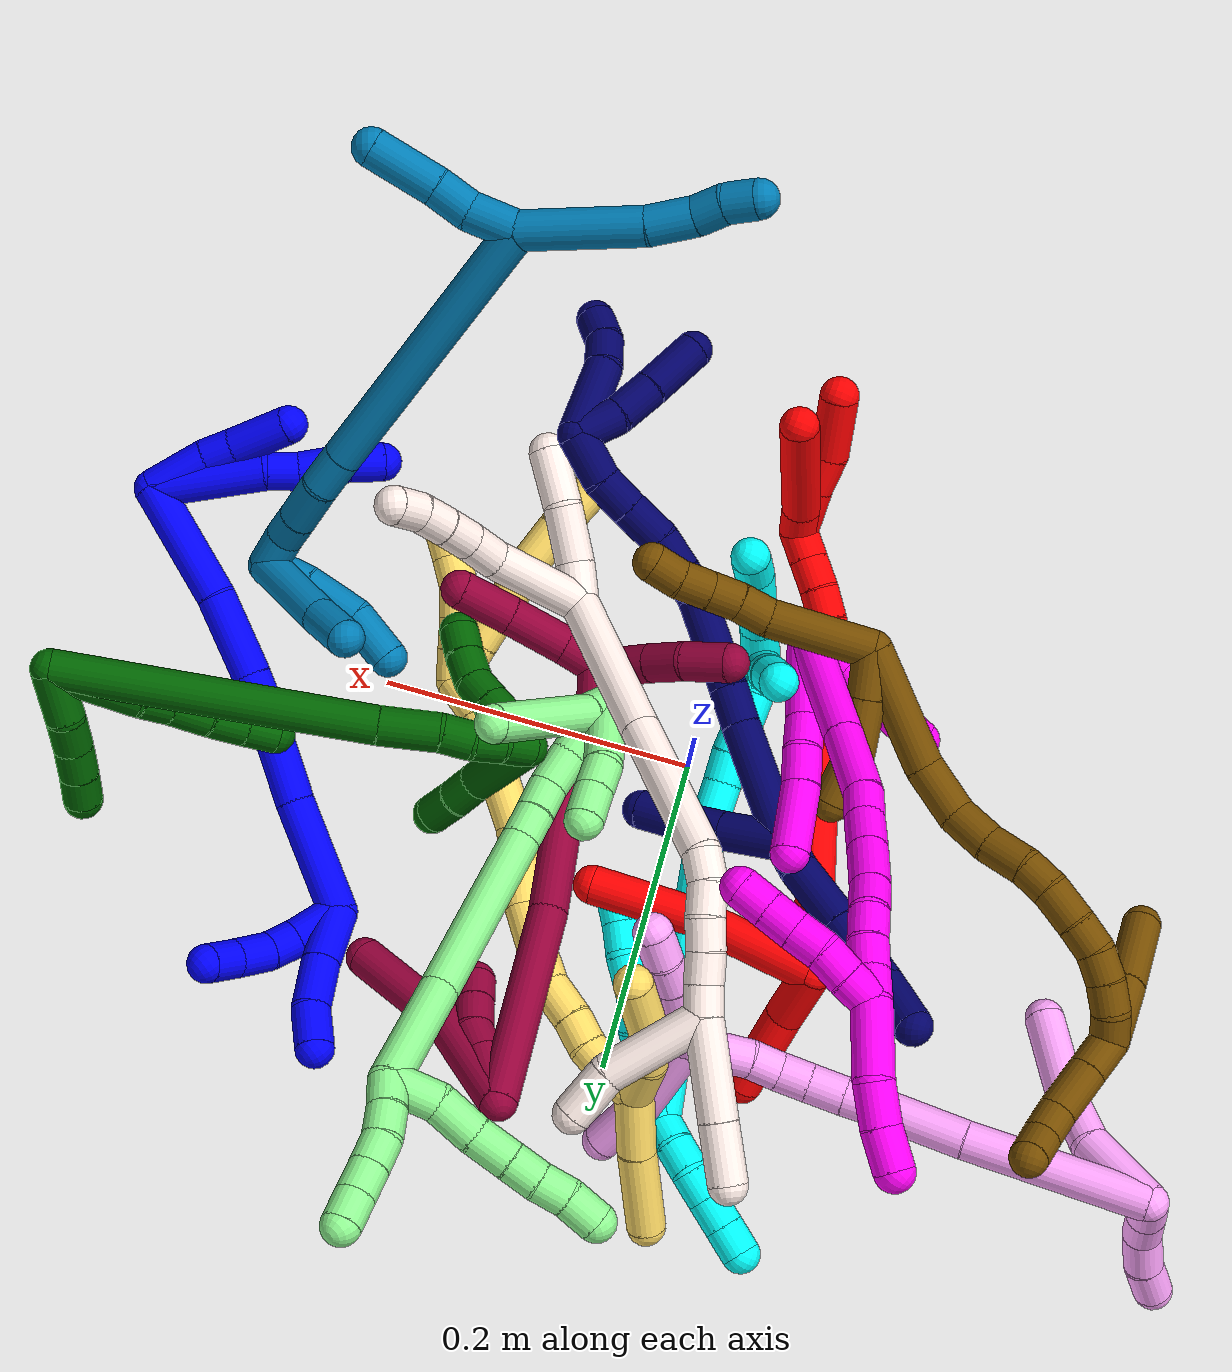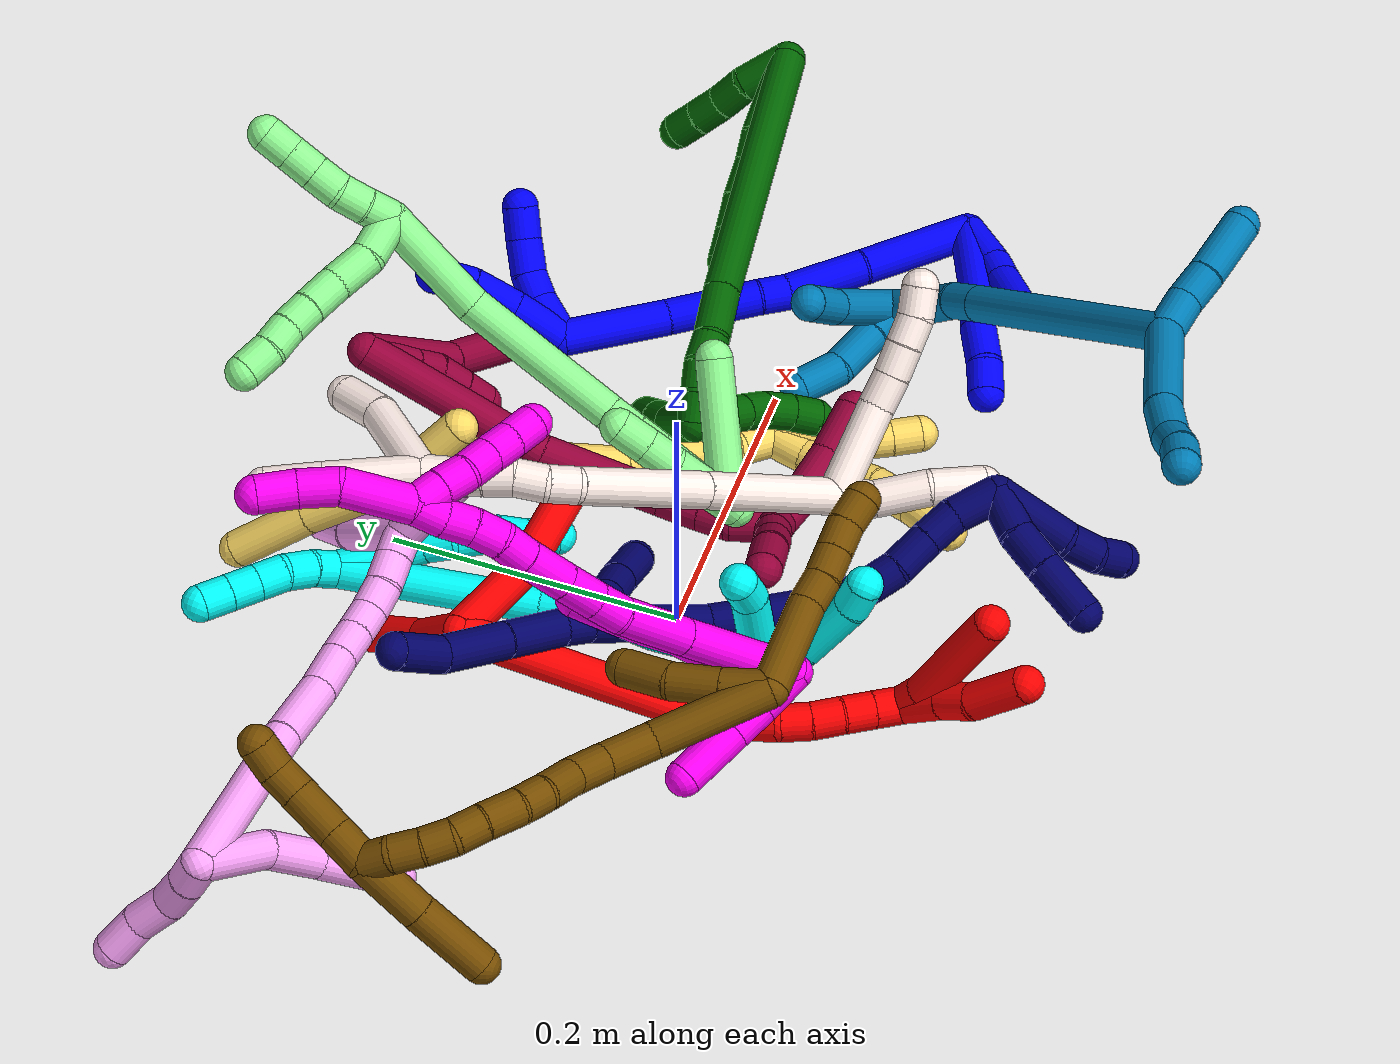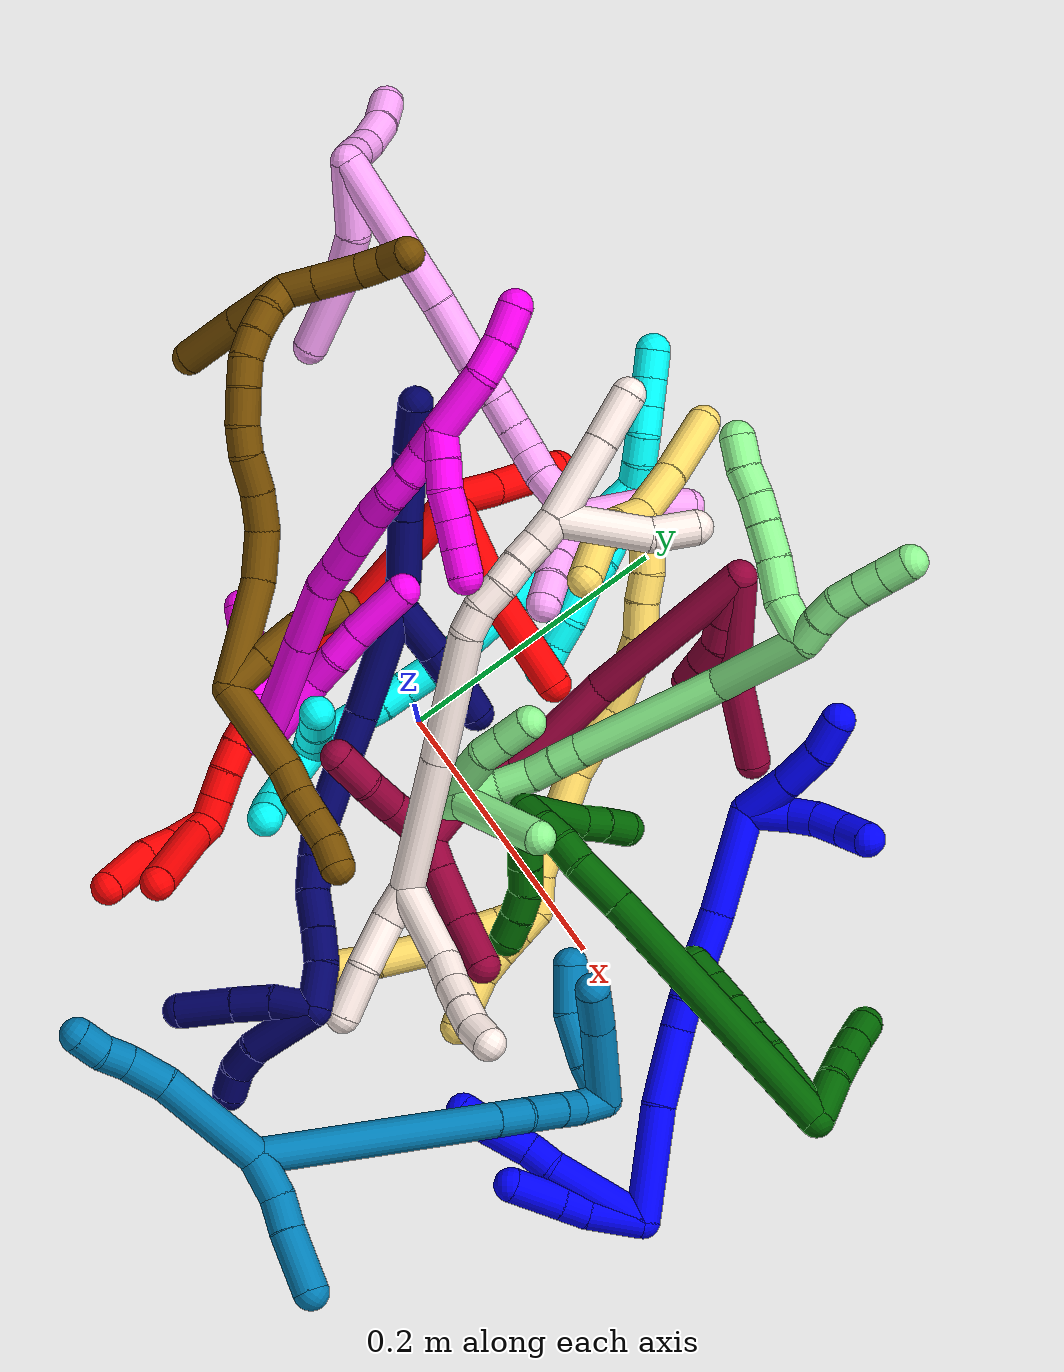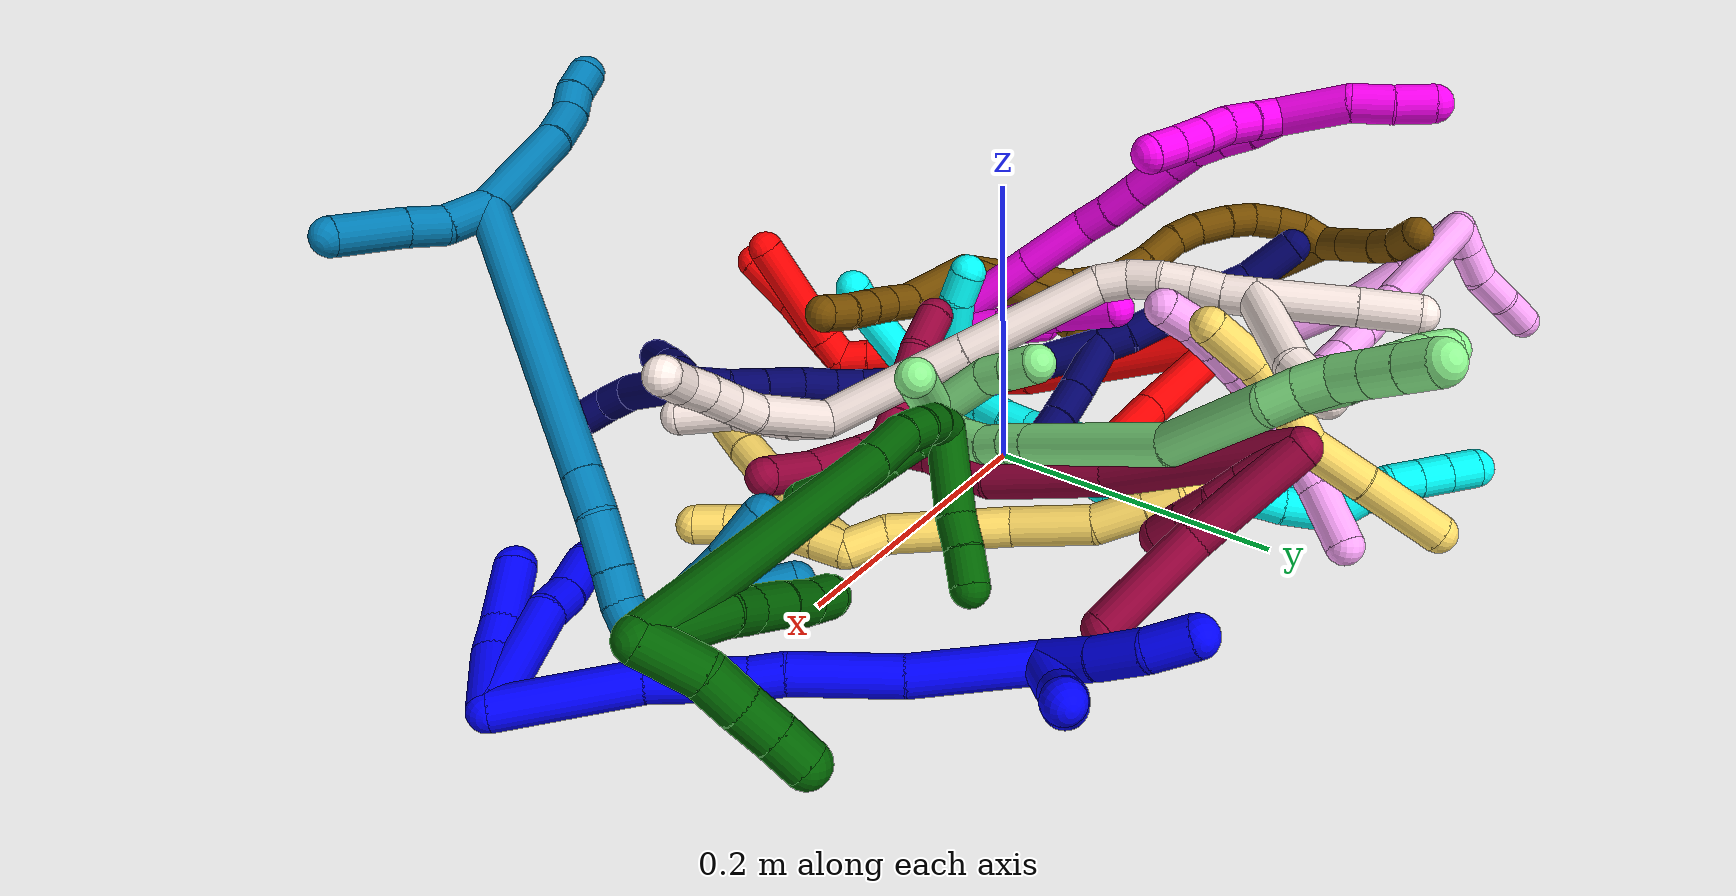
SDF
<sdf version="1.7">
 <world name="default">
  <plugin name="TubeGeneratorPlugin" filename="libtube_generator_plugin.so"/>
  <model name="photoneo_s_sensor">
   <static>1</static>
   <pose>0 0 2 1.57079 1.57079 3.14159</pose>
   <link name="link">
    <inertial><mass>0.1</mass></inertial>
    <sensor name="sensor" type="depth">
     <update_rate>30</update_rate>
     <camera>
      <horizontal_fov>1.22</horizontal_fov>
      <image><width>1920</width><height>1200</height><format>B8G8R8</format></image>
      <clip><near>0.1</near><far>4</far></clip>
      <depth_camera><output>points</output></depth_camera>
     </camera>
     <plugin name="camera_plugin" filename="libgazebo_ros_depth_camera.so">
      <baseline>0.2</baseline>
      <alwaysOn>1</alwaysOn>
      <updateRate>0.0</updateRate>
      <cameraName>camera_ir</cameraName>
      <imageTopicName>/camera/color/image_raw</imageTopicName>
      <cameraInfoTopicName>/camera/color/camera_info</cameraInfoTopicName>
      <depthImageTopicName>/camera/depth/image_raw</depthImageTopicName>
      <depthImageCameraInfoTopicName>/camera/depth/camera_info</depthImageCameraInfoTopicName>
      <pointCloudTopicName>/camera/depth/points</pointCloudTopicName>
      <frameName>fr_optical</frameName>
      <pointCloudCutoff>0.1</pointCloudCutoff>
      <pointCloudCutoffMax>2.0</pointCloudCutoffMax>
      <distortionK1>0</distortionK1>
      <distortionK2>0</distortionK2>
      <distortionK3>0</distortionK3>
      <distortionT1>0</distortionT1>
      <distortionT2>0</distortionT2>
      <CxPrime>0</CxPrime>
      <Cx>0</Cx>
      <Cy>0</Cy>
      <focalLength>0</focalLength>
      <hackBaseline>0</hackBaseline>
     </plugin>
    </sensor>
   </link>
  </model>
  <gravity>0 0 -9.8</gravity>
  <magnetic_field>6e-06 2.3e-05 -4.2e-05</magnetic_field>
  <atmosphere type="adiabatic"/>
  <physics name="default_physics" default="0" type="ode">
   <max_step_size>0.003</max_step_size>
   <real_time_factor>1</real_time_factor>
   <real_time_update_rate>1000</real_time_update_rate>
   <max_contacts>10000</max_contacts>
   <ode>
    <solver>
     <type>quick</type>
     <iters>100</iters>
     <sor>1.3</sor>
     <use_dynamic_moi_rescaling>0</use_dynamic_moi_rescaling>
    </solver>
    <constraints>
     <contact_max_correcting_vel>0</contact_max_correcting_vel>
     <contact_surface_layer>0.001</contact_surface_layer>
     <cfm>0</cfm>
     <erp>0.2</erp>
    </constraints>
   </ode>
  </physics>
  <scene><ambient>0.4 0.4 0.4 1</ambient><background>0.7 0.7 0.7 1</background><shadows>0</shadows></scene>
  <audio><device>default</device></audio>
  <spherical_coordinates>
   <surface_model>EARTH_WGS84</surface_model>
   <latitude_deg>0</latitude_deg>
   <longitude_deg>0</longitude_deg>
   <elevation>0</elevation>
   <heading_deg>0</heading_deg>
  </spherical_coordinates>
  <model name="bin">
   <static>1</static>
   <link name="bottom">
    <collision name="collision-bottom">
     <pose>0 0 -0.01 0 -0 0</pose>
     <geometry><box><size>0.8 0.6 0.02</size></box></geometry>
     <surface>
      <friction><ode><mu>100</mu><mu2>100</mu2></ode></friction>
      <contact><collide_bitmask>65535</collide_bitmask></contact>
     </surface>
    </collision>
   </link>
   <link name="west_wall">
    <collision name="collision-west_wall">
     <pose>-0.41 0 0.1 0 -0 0</pose>
     <geometry><box><size>0.02 0.6 0.2</size></box></geometry>
     <surface>
      <friction><ode><mu>100</mu><mu2>100</mu2></ode></friction>
      <contact><collide_bitmask>65535</collide_bitmask></contact>
     </surface>
    </collision>
   </link>
   <link name="east_wall">
    <collision name="collision-east_wall">
     <pose>0.41 0 0.1 0 -0 0</pose>
     <geometry><box><size>0.02 0.6 0.2</size></box></geometry>
     <surface>
      <friction><ode><mu>100</mu><mu2>100</mu2></ode></friction>
      <contact><collide_bitmask>65535</collide_bitmask></contact>
     </surface>
    </collision>
   </link>
   <link name="south_wall">
    <collision name="collision-south_wall">
     <pose>0 -0.31 0.1 0 -0 0</pose>
     <geometry><box><size>0.8 0.02 0.2</size></box></geometry>
     <surface>
      <friction><ode><mu>100</mu><mu2>100</mu2></ode></friction>
      <contact><collide_bitmask>65535</collide_bitmask></contact>
     </surface>
    </collision>
   </link>
   <link name="north_wall">
    <collision name="collision-north_wall">
     <pose>0 0.31 0.1 0 -0 0</pose>
     <geometry><box><size>0.8 0.02 0.2</size></box></geometry>
     <surface>
      <friction><ode><mu>100</mu><mu2>100</mu2></ode></friction>
      <contact><collide_bitmask>65535</collide_bitmask></contact>
     </surface>
    </collision>
   </link>
  </model>
  <model name="1">
   <static>0</static>
   <link name="1">
    <collision name="collision-cylinder-e_1_2_8">
     <pose>-0.010073 0.019786 -0.029981 -2.55824 -0.273391 0.859212</pose>
     <geometry><cylinder><radius>0.0125</radius><length>0.074614</length></cylinder></geometry>
     <surface>
      <friction><ode><mu>1.16</mu><mu2>1.16</mu2><slip1>0</slip1><slip2>0</slip2></ode></friction>
      <contact><ode><kp>1e+06</kp><kd>1</kd><max_vel>0</max_vel><min_depth>0.001</min_depth></ode></contact>
     </surface>
    </collision>
    <visual name="visual-cylinder-e_1_2_8">
     <pose>-0.010073 0.019786 -0.029981 -2.55824 -0.273391 0.859212</pose>
     <geometry><cylinder><radius>0.0125</radius><length>0.074614</length></cylinder></geometry>
     <material><ambient>0 0 1 1</ambient></material>
    </visual>
    <collision name="collision-cylinder-e_2_8_9">
     <pose>-0.020118 0.045854 -0.068234 -2.49218 0.002673 -0.00794</pose>
     <geometry><cylinder><radius>0.0125</radius><length>0.020774</length></cylinder></geometry>
     <surface>
      <friction><ode><mu>1.16</mu><mu2>1.16</mu2><slip1>0</slip1><slip2>0</slip2></ode></friction>
      <contact><ode><kp>1e+06</kp><kd>1</kd><max_vel>0</max_vel><min_depth>0.001</min_depth></ode></contact>
     </surface>
    </collision>
    <visual name="visual-cylinder-e_2_8_9">
     <pose>-0.020118 0.045854 -0.068234 -2.49218 0.002673 -0.00794</pose>
     <geometry><cylinder><radius>0.0125</radius><length>0.020774</length></cylinder></geometry>
     <material><ambient>0 0 1 1</ambient></material>
    </visual>
    <collision name="collision-cylinder-e_3_9_10">
     <pose>-0.022739 0.060161 -0.090298 -2.61457 -0.164509 0.593134</pose>
     <geometry><cylinder><radius>0.0125</radius><length>0.032351</length></cylinder></geometry>
     <surface>
      <friction><ode><mu>1.16</mu><mu2>1.16</mu2><slip1>0</slip1><slip2>0</slip2></ode></friction>
      <contact><ode><kp>1e+06</kp><kd>1</kd><max_vel>0</max_vel><min_depth>0.001</min_depth></ode></contact>
     </surface>
    </collision>
    <visual name="visual-cylinder-e_3_9_10">
     <pose>-0.022739 0.060161 -0.090298 -2.61457 -0.164509 0.593134</pose>
     <geometry><cylinder><radius>0.0125</radius><length>0.032351</length></cylinder></geometry>
     <material><ambient>0 0 1 1</ambient></material>
    </visual>
    <collision name="collision-cylinder-e_4_10_6">
     <pose>-0.02421 0.074092 -0.113451 -2.57877 0.10604 -0.363119</pose>
     <geometry><cylinder><radius>0.0125</radius><length>0.022262</length></cylinder></geometry>
     <surface>
      <friction><ode><mu>1.16</mu><mu2>1.16</mu2><slip1>0</slip1><slip2>0</slip2></ode></friction>
      <contact><ode><kp>1e+06</kp><kd>1</kd><max_vel>0</max_vel><min_depth>0.001</min_depth></ode></contact>
     </surface>
    </collision>
    <visual name="visual-cylinder-e_4_10_6">
     <pose>-0.02421 0.074092 -0.113451 -2.57877 0.10604 -0.363119</pose>
     <geometry><cylinder><radius>0.0125</radius><length>0.022262</length></cylinder></geometry>
     <material><ambient>0 0 1 1</ambient></material>
    </visual>
    <collision name="collision-cylinder-e_1_2_11">
     <pose>-0.00692 0.003866 -0.018296 -2.93335 -0.354446 2.08524</pose>
     <geometry><cylinder><radius>0.0125</radius><length>0.039878</length></cylinder></geometry>
     <surface>
      <friction><ode><mu>1.16</mu><mu2>1.16</mu2><slip1>0</slip1><slip2>0</slip2></ode></friction>
      <contact><ode><kp>1e+06</kp><kd>1</kd><max_vel>0</max_vel><min_depth>0.001</min_depth></ode></contact>
     </surface>
    </collision>
    <visual name="visual-cylinder-e_1_2_11">
     <pose>-0.00692 0.003866 -0.018296 -2.93335 -0.354446 2.08524</pose>
     <geometry><cylinder><radius>0.0125</radius><length>0.039878</length></cylinder></geometry>
     <material><ambient>0 0 1 1</ambient></material>
    </visual>
    <collision name="collision-cylinder-e_2_11_12">
     <pose>-0.018074 0.011462 -0.045232 -2.73412 -0.422677 1.60849</pose>
     <geometry><cylinder><radius>0.0125</radius><length>0.02064</length></cylinder></geometry>
     <surface>
      <friction><ode><mu>1.16</mu><mu2>1.16</mu2><slip1>0</slip1><slip2>0</slip2></ode></friction>
      <contact><ode><kp>1e+06</kp><kd>1</kd><max_vel>0</max_vel><min_depth>0.001</min_depth></ode></contact>
     </surface>
    </collision>
    <visual name="visual-cylinder-e_2_11_12">
     <pose>-0.018074 0.011462 -0.045232 -2.73412 -0.422677 1.60849</pose>
     <geometry><cylinder><radius>0.0125</radius><length>0.02064</length></cylinder></geometry>
     <material><ambient>0 0 1 1</ambient></material>
    </visual>
    <collision name="collision-cylinder-e_3_12_5">
     <pose>-0.032364 0.022336 -0.069285 -2.70748 -0.534554 1.7856</pose>
     <geometry><cylinder><radius>0.0125</radius><length>0.039482</length></cylinder></geometry>
     <surface>
      <friction><ode><mu>1.16</mu><mu2>1.16</mu2><slip1>0</slip1><slip2>0</slip2></ode></friction>
      <contact><ode><kp>1e+06</kp><kd>1</kd><max_vel>0</max_vel><min_depth>0.001</min_depth></ode></contact>
     </surface>
    </collision>
    <visual name="visual-cylinder-e_3_12_5">
     <pose>-0.032364 0.022336 -0.069285 -2.70748 -0.534554 1.7856</pose>
     <geometry><cylinder><radius>0.0125</radius><length>0.039482</length></cylinder></geometry>
     <material><ambient>0 0 1 1</ambient></material>
    </visual>
    <collision name="collision-cylinder-e_1_2_13">
     <pose>0.002417 0.040566 0.005952 -1.42512 0.05889 -0.050884</pose>
     <geometry><cylinder><radius>0.0125</radius><length>0.082144</length></cylinder></geometry>
     <surface>
      <friction><ode><mu>1.16</mu><mu2>1.16</mu2><slip1>0</slip1><slip2>0</slip2></ode></friction>
      <contact><ode><kp>1e+06</kp><kd>1</kd><max_vel>0</max_vel><min_depth>0.001</min_depth></ode></contact>
     </surface>
    </collision>
    <visual name="visual-cylinder-e_1_2_13">
     <pose>0.002417 0.040566 0.005952 -1.42512 0.05889 -0.050884</pose>
     <geometry><cylinder><radius>0.0125</radius><length>0.082144</length></cylinder></geometry>
     <material><ambient>0 0 1 1</ambient></material>
    </visual>
    <collision name="collision-cylinder-e_2_13_14">
     <pose>0.010316 0.108002 0.018123 -1.34334 0.1962 -0.156159</pose>
     <geometry><cylinder><radius>0.0125</radius><length>0.056239</length></cylinder></geometry>
     <surface>
      <friction><ode><mu>1.16</mu><mu2>1.16</mu2><slip1>0</slip1><slip2>0</slip2></ode></friction>
      <contact><ode><kp>1e+06</kp><kd>1</kd><max_vel>0</max_vel><min_depth>0.001</min_depth></ode></contact>
     </surface>
    </collision>
    <visual name="visual-cylinder-e_2_13_14">
     <pose>0.010316 0.108002 0.018123 -1.34334 0.1962 -0.156159</pose>
     <geometry><cylinder><radius>0.0125</radius><length>0.056239</length></cylinder></geometry>
     <material><ambient>0 0 1 1</ambient></material>
    </visual>
    <collision name="collision-cylinder-e_3_14_15">
     <pose>0.016151 0.144793 0.027392 -1.27255 0.033953 -0.025084</pose>
     <geometry><cylinder><radius>0.0125</radius><length>0.02077</length></cylinder></geometry>
     <surface>
      <friction><ode><mu>1.16</mu><mu2>1.16</mu2><slip1>0</slip1><slip2>0</slip2></ode></friction>
      <contact><ode><kp>1e+06</kp><kd>1</kd><max_vel>0</max_vel><min_depth>0.001</min_depth></ode></contact>
     </surface>
    </collision>
    <visual name="visual-cylinder-e_3_14_15">
     <pose>0.016151 0.144793 0.027392 -1.27255 0.033953 -0.025084</pose>
     <geometry><cylinder><radius>0.0125</radius><length>0.02077</length></cylinder></geometry>
     <material><ambient>0 0 1 1</ambient></material>
    </visual>
    <collision name="collision-cylinder-e_4_15_16">
     <pose>0.022626 0.184789 0.040998 -1.23323 0.189773 -0.134714</pose>
     <geometry><cylinder><radius>0.0125</radius><length>0.064912</length></cylinder></geometry>
     <surface>
      <friction><ode><mu>1.16</mu><mu2>1.16</mu2><slip1>0</slip1><slip2>0</slip2></ode></friction>
      <contact><ode><kp>1e+06</kp><kd>1</kd><max_vel>0</max_vel><min_depth>0.001</min_depth></ode></contact>
     </surface>
    </collision>
    <visual name="visual-cylinder-e_4_15_16">
     <pose>0.022626 0.184789 0.040998 -1.23323 0.189773 -0.134714</pose>
     <geometry><cylinder><radius>0.0125</radius><length>0.064912</length></cylinder></geometry>
     <material><ambient>0 0 1 1</ambient></material>
    </visual>
    <collision name="collision-cylinder-e_5_16_1">
     <pose>0.031528 0.251099 0.062543 -1.27633 0.073289 -0.054369</pose>
     <geometry><cylinder><radius>0.0125</radius><length>0.075935</length></cylinder></geometry>
     <surface>
      <friction><ode><mu>1.16</mu><mu2>1.16</mu2><slip1>0</slip1><slip2>0</slip2></ode></friction>
      <contact><ode><kp>1e+06</kp><kd>1</kd><max_vel>0</max_vel><min_depth>0.001</min_depth></ode></contact>
     </surface>
    </collision>
    <visual name="visual-cylinder-e_5_16_1">
     <pose>0.031528 0.251099 0.062543 -1.27633 0.073289 -0.054369</pose>
     <geometry><cylinder><radius>0.0125</radius><length>0.075935</length></cylinder></geometry>
     <material><ambient>0 0 1 1</ambient></material>
    </visual>
    <collision name="collision-cylinder-e_1_1_17">
     <pose>0.02956 0.297584 0.089021 -0.58458 -0.250309 0.07568</pose>
     <geometry><cylinder><radius>0.0125</radius><length>0.038339</length></cylinder></geometry>
     <surface>
      <friction><ode><mu>1.16</mu><mu2>1.16</mu2><slip1>0</slip1><slip2>0</slip2></ode></friction>
      <contact><ode><kp>1e+06</kp><kd>1</kd><max_vel>0</max_vel><min_depth>0.001</min_depth></ode></contact>
     </surface>
    </collision>
    <visual name="visual-cylinder-e_1_1_17">
     <pose>0.02956 0.297584 0.089021 -0.58458 -0.250309 0.07568</pose>
     <geometry><cylinder><radius>0.0125</radius><length>0.038339</length></cylinder></geometry>
     <material><ambient>0 0 1 1</ambient></material>
    </visual>
    <collision name="collision-cylinder-e_2_17_18">
     <pose>0.02007 0.318172 0.11695 -0.693408 -0.285091 0.103613</pose>
     <geometry><cylinder><radius>0.0125</radius><length>0.033715</length></cylinder></geometry>
     <surface>
      <friction><ode><mu>1.16</mu><mu2>1.16</mu2><slip1>0</slip1><slip2>0</slip2></ode></friction>
      <contact><ode><kp>1e+06</kp><kd>1</kd><max_vel>0</max_vel><min_depth>0.001</min_depth></ode></contact>
     </surface>
    </collision>
    <visual name="visual-cylinder-e_2_17_18">
     <pose>0.02007 0.318172 0.11695 -0.693408 -0.285091 0.103613</pose>
     <geometry><cylinder><radius>0.0125</radius><length>0.033715</length></cylinder></geometry>
     <material><ambient>0 0 1 1</ambient></material>
    </visual>
    <collision name="collision-cylinder-e_3_18_4">
     <pose>0.011595 0.339671 0.136926 -0.976913 -0.270517 0.144386</pose>
     <geometry><cylinder><radius>0.0125</radius><length>0.027946</length></cylinder></geometry>
     <surface>
      <friction><ode><mu>1.16</mu><mu2>1.16</mu2><slip1>0</slip1><slip2>0</slip2></ode></friction>
      <contact><ode><kp>1e+06</kp><kd>1</kd><max_vel>0</max_vel><min_depth>0.001</min_depth></ode></contact>
     </surface>
    </collision>
    <visual name="visual-cylinder-e_3_18_4">
     <pose>0.011595 0.339671 0.136926 -0.976913 -0.270517 0.144386</pose>
     <geometry><cylinder><radius>0.0125</radius><length>0.027946</length></cylinder></geometry>
     <material><ambient>0 0 1 1</ambient></material>
    </visual>
    <collision name="collision-cylinder-e_1_1_19">
     <pose>0.034986 0.285618 0.089674 0.105976 0.041715 0.002213</pose>
     <geometry><cylinder><radius>0.0125</radius><length>0.032492</length></cylinder></geometry>
     <surface>
      <friction><ode><mu>1.16</mu><mu2>1.16</mu2><slip1>0</slip1><slip2>0</slip2></ode></friction>
      <contact><ode><kp>1e+06</kp><kd>1</kd><max_vel>0</max_vel><min_depth>0.001</min_depth></ode></contact>
     </surface>
    </collision>
    <visual name="visual-cylinder-e_1_1_19">
     <pose>0.034986 0.285618 0.089674 0.105976 0.041715 0.002213</pose>
     <geometry><cylinder><radius>0.0125</radius><length>0.032492</length></cylinder></geometry>
     <material><ambient>0 0 1 1</ambient></material>
    </visual>
    <collision name="collision-cylinder-e_2_19_20">
     <pose>0.032965 0.282478 0.11534 0.148248 -0.273196 -0.020414</pose>
     <geometry><cylinder><radius>0.0125</radius><length>0.020003</length></cylinder></geometry>
     <surface>
      <friction><ode><mu>1.16</mu><mu2>1.16</mu2><slip1>0</slip1><slip2>0</slip2></ode></friction>
      <contact><ode><kp>1e+06</kp><kd>1</kd><max_vel>0</max_vel><min_depth>0.001</min_depth></ode></contact>
     </surface>
    </collision>
    <visual name="visual-cylinder-e_2_19_20">
     <pose>0.032965 0.282478 0.11534 0.148248 -0.273196 -0.020414</pose>
     <geometry><cylinder><radius>0.0125</radius><length>0.020003</length></cylinder></geometry>
     <material><ambient>0 0 1 1</ambient></material>
    </visual>
    <collision name="collision-cylinder-e_3_20_21">
     <pose>0.025471 0.277171 0.135543 0.348934 -0.399321 -0.071304</pose>
     <geometry><cylinder><radius>0.0125</radius><length>0.024666</length></cylinder></geometry>
     <surface>
      <friction><ode><mu>1.16</mu><mu2>1.16</mu2><slip1>0</slip1><slip2>0</slip2></ode></friction>
      <contact><ode><kp>1e+06</kp><kd>1</kd><max_vel>0</max_vel><min_depth>0.001</min_depth></ode></contact>
     </surface>
    </collision>
    <visual name="visual-cylinder-e_3_20_21">
     <pose>0.025471 0.277171 0.135543 0.348934 -0.399321 -0.071304</pose>
     <geometry><cylinder><radius>0.0125</radius><length>0.024666</length></cylinder></geometry>
     <material><ambient>0 0 1 1</ambient></material>
    </visual>
    <collision name="collision-cylinder-e_4_21_3">
     <pose>0.014107 0.270295 0.15507 0.325977 -0.61287 -0.103969</pose>
     <geometry><cylinder><radius>0.0125</radius><length>0.022839</length></cylinder></geometry>
     <surface>
      <friction><ode><mu>1.16</mu><mu2>1.16</mu2><slip1>0</slip1><slip2>0</slip2></ode></friction>
      <contact><ode><kp>1e+06</kp><kd>1</kd><max_vel>0</max_vel><min_depth>0.001</min_depth></ode></contact>
     </surface>
    </collision>
    <visual name="visual-cylinder-e_4_21_3">
     <pose>0.014107 0.270295 0.15507 0.325977 -0.61287 -0.103969</pose>
     <geometry><cylinder><radius>0.0125</radius><length>0.022839</length></cylinder></geometry>
     <material><ambient>0 0 1 1</ambient></material>
    </visual>
    <collision name="collision-sphere-3">
     <pose>0.007539 0.267303 0.163919 0 -0 0</pose>
     <geometry><sphere><radius>0.0125</radius></sphere></geometry>
     <surface>
      <friction><ode><mu>1.16</mu><mu2>1.16</mu2><slip1>0</slip1><slip2>0</slip2></ode></friction>
      <contact><ode><kp>1e+06</kp><kd>1</kd><max_vel>0</max_vel><min_depth>0.001</min_depth></ode></contact>
     </surface>
    </collision>
    <visual name="visual-sphere-3">
     <pose>0.007539 0.267303 0.163919 0 -0 0</pose>
     <geometry><sphere><radius>0.0125</radius></sphere></geometry>
     <material><ambient>0 0 1 1</ambient></material>
    </visual>
    <collision name="collision-sphere-21">
     <pose>0.020676 0.273286 0.146221 0 -0 0</pose>
     <geometry><sphere><radius>0.0125</radius></sphere></geometry>
     <surface>
      <friction><ode><mu>1.16</mu><mu2>1.16</mu2><slip1>0</slip1><slip2>0</slip2></ode></friction>
      <contact><ode><kp>1e+06</kp><kd>1</kd><max_vel>0</max_vel><min_depth>0.001</min_depth></ode></contact>
     </surface>
    </collision>
    <visual name="visual-sphere-21">
     <pose>0.020676 0.273286 0.146221 0 -0 0</pose>
     <geometry><sphere><radius>0.0125</radius></sphere></geometry>
     <material><ambient>0 0 1 1</ambient></material>
    </visual>
    <collision name="collision-sphere-20">
     <pose>0.030266 0.281056 0.124865 0 -0 0</pose>
     <geometry><sphere><radius>0.0125</radius></sphere></geometry>
     <surface>
      <friction><ode><mu>1.16</mu><mu2>1.16</mu2><slip1>0</slip1><slip2>0</slip2></ode></friction>
      <contact><ode><kp>1e+06</kp><kd>1</kd><max_vel>0</max_vel><min_depth>0.001</min_depth></ode></contact>
     </surface>
    </collision>
    <visual name="visual-sphere-20">
     <pose>0.030266 0.281056 0.124865 0 -0 0</pose>
     <geometry><sphere><radius>0.0125</radius></sphere></geometry>
     <material><ambient>0 0 1 1</ambient></material>
    </visual>
    <collision name="collision-sphere-19">
     <pose>0.035663 0.283901 0.105814 0 -0 0</pose>
     <geometry><sphere><radius>0.0125</radius></sphere></geometry>
     <surface>
      <friction><ode><mu>1.16</mu><mu2>1.16</mu2><slip1>0</slip1><slip2>0</slip2></ode></friction>
      <contact><ode><kp>1e+06</kp><kd>1</kd><max_vel>0</max_vel><min_depth>0.001</min_depth></ode></contact>
     </surface>
    </collision>
    <visual name="visual-sphere-19">
     <pose>0.035663 0.283901 0.105814 0 -0 0</pose>
     <geometry><sphere><radius>0.0125</radius></sphere></geometry>
     <material><ambient>0 0 1 1</ambient></material>
    </visual>
    <collision name="collision-sphere-11">
     <pose>-0.013841 0.007732 -0.036591 0 -0 0</pose>
     <geometry><sphere><radius>0.0125</radius></sphere></geometry>
     <surface>
      <friction><ode><mu>1.16</mu><mu2>1.16</mu2><slip1>0</slip1><slip2>0</slip2></ode></friction>
      <contact><ode><kp>1e+06</kp><kd>1</kd><max_vel>0</max_vel><min_depth>0.001</min_depth></ode></contact>
     </surface>
    </collision>
    <visual name="visual-sphere-11">
     <pose>-0.013841 0.007732 -0.036591 0 -0 0</pose>
     <geometry><sphere><radius>0.0125</radius></sphere></geometry>
     <material><ambient>0 0 1 1</ambient></material>
    </visual>
    <collision name="collision-sphere-6">
     <pose>-0.023032 0.079998 -0.122812 0 -0 0</pose>
     <geometry><sphere><radius>0.0125</radius></sphere></geometry>
     <surface>
      <friction><ode><mu>1.16</mu><mu2>1.16</mu2><slip1>0</slip1><slip2>0</slip2></ode></friction>
      <contact><ode><kp>1e+06</kp><kd>1</kd><max_vel>0</max_vel><min_depth>0.001</min_depth></ode></contact>
     </surface>
    </collision>
    <visual name="visual-sphere-6">
     <pose>-0.023032 0.079998 -0.122812 0 -0 0</pose>
     <geometry><sphere><radius>0.0125</radius></sphere></geometry>
     <material><ambient>0 0 1 1</ambient></material>
    </visual>
    <collision name="collision-sphere-10">
     <pose>-0.025388 0.068186 -0.10409 0 -0 0</pose>
     <geometry><sphere><radius>0.0125</radius></sphere></geometry>
     <surface>
      <friction><ode><mu>1.16</mu><mu2>1.16</mu2><slip1>0</slip1><slip2>0</slip2></ode></friction>
      <contact><ode><kp>1e+06</kp><kd>1</kd><max_vel>0</max_vel><min_depth>0.001</min_depth></ode></contact>
     </surface>
    </collision>
    <visual name="visual-sphere-10">
     <pose>-0.025388 0.068186 -0.10409 0 -0 0</pose>
     <geometry><sphere><radius>0.0125</radius></sphere></geometry>
     <material><ambient>0 0 1 1</ambient></material>
    </visual>
    <collision name="collision-sphere-9">
     <pose>-0.02009 0.052135 -0.076506 0 -0 0</pose>
     <geometry><sphere><radius>0.0125</radius></sphere></geometry>
     <surface>
      <friction><ode><mu>1.16</mu><mu2>1.16</mu2><slip1>0</slip1><slip2>0</slip2></ode></friction>
      <contact><ode><kp>1e+06</kp><kd>1</kd><max_vel>0</max_vel><min_depth>0.001</min_depth></ode></contact>
     </surface>
    </collision>
    <visual name="visual-sphere-9">
     <pose>-0.02009 0.052135 -0.076506 0 -0 0</pose>
     <geometry><sphere><radius>0.0125</radius></sphere></geometry>
     <material><ambient>0 0 1 1</ambient></material>
    </visual>
    <collision name="collision-sphere-2">
     <geometry><sphere><radius>0.0125</radius></sphere></geometry>
     <surface>
      <friction><ode><mu>1.16</mu><mu2>1.16</mu2><slip1>0</slip1><slip2>0</slip2></ode></friction>
      <contact><ode><kp>1e+06</kp><kd>1</kd><max_vel>0</max_vel><min_depth>0.001</min_depth></ode></contact>
     </surface>
    </collision>
    <visual name="visual-sphere-2">
     <geometry><sphere><radius>0.0125</radius></sphere></geometry>
     <material><ambient>0 0 1 1</ambient></material>
    </visual>
    <collision name="collision-sphere-8">
     <pose>-0.020145 0.039573 -0.059961 0 -0 0</pose>
     <geometry><sphere><radius>0.0125</radius></sphere></geometry>
     <surface>
      <friction><ode><mu>1.16</mu><mu2>1.16</mu2><slip1>0</slip1><slip2>0</slip2></ode></friction>
      <contact><ode><kp>1e+06</kp><kd>1</kd><max_vel>0</max_vel><min_depth>0.001</min_depth></ode></contact>
     </surface>
    </collision>
    <visual name="visual-sphere-8">
     <pose>-0.020145 0.039573 -0.059961 0 -0 0</pose>
     <geometry><sphere><radius>0.0125</radius></sphere></geometry>
     <material><ambient>0 0 1 1</ambient></material>
    </visual>
    <collision name="collision-sphere-12">
     <pose>-0.022307 0.015192 -0.053874 0 -0 0</pose>
     <geometry><sphere><radius>0.0125</radius></sphere></geometry>
     <surface>
      <friction><ode><mu>1.16</mu><mu2>1.16</mu2><slip1>0</slip1><slip2>0</slip2></ode></friction>
      <contact><ode><kp>1e+06</kp><kd>1</kd><max_vel>0</max_vel><min_depth>0.001</min_depth></ode></contact>
     </surface>
    </collision>
    <visual name="visual-sphere-12">
     <pose>-0.022307 0.015192 -0.053874 0 -0 0</pose>
     <geometry><sphere><radius>0.0125</radius></sphere></geometry>
     <material><ambient>0 0 1 1</ambient></material>
    </visual>
    <collision name="collision-sphere-5">
     <pose>-0.042421 0.029481 -0.084696 0 -0 0</pose>
     <geometry><sphere><radius>0.0125</radius></sphere></geometry>
     <surface>
      <friction><ode><mu>1.16</mu><mu2>1.16</mu2><slip1>0</slip1><slip2>0</slip2></ode></friction>
      <contact><ode><kp>1e+06</kp><kd>1</kd><max_vel>0</max_vel><min_depth>0.001</min_depth></ode></contact>
     </surface>
    </collision>
    <visual name="visual-sphere-5">
     <pose>-0.042421 0.029481 -0.084696 0 -0 0</pose>
     <geometry><sphere><radius>0.0125</radius></sphere></geometry>
     <material><ambient>0 0 1 1</ambient></material>
    </visual>
    <collision name="collision-sphere-13">
     <pose>0.004835 0.081133 0.011903 0 -0 0</pose>
     <geometry><sphere><radius>0.0125</radius></sphere></geometry>
     <surface>
      <friction><ode><mu>1.16</mu><mu2>1.16</mu2><slip1>0</slip1><slip2>0</slip2></ode></friction>
      <contact><ode><kp>1e+06</kp><kd>1</kd><max_vel>0</max_vel><min_depth>0.001</min_depth></ode></contact>
     </surface>
    </collision>
    <visual name="visual-sphere-13">
     <pose>0.004835 0.081133 0.011903 0 -0 0</pose>
     <geometry><sphere><radius>0.0125</radius></sphere></geometry>
     <material><ambient>0 0 1 1</ambient></material>
    </visual>
    <collision name="collision-sphere-14">
     <pose>0.015798 0.134872 0.024342 0 -0 0</pose>
     <geometry><sphere><radius>0.0125</radius></sphere></geometry>
     <surface>
      <friction><ode><mu>1.16</mu><mu2>1.16</mu2><slip1>0</slip1><slip2>0</slip2></ode></friction>
      <contact><ode><kp>1e+06</kp><kd>1</kd><max_vel>0</max_vel><min_depth>0.001</min_depth></ode></contact>
     </surface>
    </collision>
    <visual name="visual-sphere-14">
     <pose>0.015798 0.134872 0.024342 0 -0 0</pose>
     <geometry><sphere><radius>0.0125</radius></sphere></geometry>
     <material><ambient>0 0 1 1</ambient></material>
    </visual>
    <collision name="collision-sphere-15">
     <pose>0.016503 0.154714 0.030442 0 -0 0</pose>
     <geometry><sphere><radius>0.0125</radius></sphere></geometry>
     <surface>
      <friction><ode><mu>1.16</mu><mu2>1.16</mu2><slip1>0</slip1><slip2>0</slip2></ode></friction>
      <contact><ode><kp>1e+06</kp><kd>1</kd><max_vel>0</max_vel><min_depth>0.001</min_depth></ode></contact>
     </surface>
    </collision>
    <visual name="visual-sphere-15">
     <pose>0.016503 0.154714 0.030442 0 -0 0</pose>
     <geometry><sphere><radius>0.0125</radius></sphere></geometry>
     <material><ambient>0 0 1 1</ambient></material>
    </visual>
    <collision name="collision-sphere-16">
     <pose>0.028748 0.214863 0.051554 0 -0 0</pose>
     <geometry><sphere><radius>0.0125</radius></sphere></geometry>
     <surface>
      <friction><ode><mu>1.16</mu><mu2>1.16</mu2><slip1>0</slip1><slip2>0</slip2></ode></friction>
      <contact><ode><kp>1e+06</kp><kd>1</kd><max_vel>0</max_vel><min_depth>0.001</min_depth></ode></contact>
     </surface>
    </collision>
    <visual name="visual-sphere-16">
     <pose>0.028748 0.214863 0.051554 0 -0 0</pose>
     <geometry><sphere><radius>0.0125</radius></sphere></geometry>
     <material><ambient>0 0 1 1</ambient></material>
    </visual>
    <collision name="collision-sphere-1">
     <pose>0.034308 0.287335 0.073533 0 -0 0</pose>
     <geometry><sphere><radius>0.0125</radius></sphere></geometry>
     <surface>
      <friction><ode><mu>1.16</mu><mu2>1.16</mu2><slip1>0</slip1><slip2>0</slip2></ode></friction>
      <contact><ode><kp>1e+06</kp><kd>1</kd><max_vel>0</max_vel><min_depth>0.001</min_depth></ode></contact>
     </surface>
    </collision>
    <visual name="visual-sphere-1">
     <pose>0.034308 0.287335 0.073533 0 -0 0</pose>
     <geometry><sphere><radius>0.0125</radius></sphere></geometry>
     <material><ambient>0 0 1 1</ambient></material>
    </visual>
    <collision name="collision-sphere-18">
     <pose>0.015329 0.328512 0.129392 0 -0 0</pose>
     <geometry><sphere><radius>0.0125</radius></sphere></geometry>
     <surface>
      <friction><ode><mu>1.16</mu><mu2>1.16</mu2><slip1>0</slip1><slip2>0</slip2></ode></friction>
      <contact><ode><kp>1e+06</kp><kd>1</kd><max_vel>0</max_vel><min_depth>0.001</min_depth></ode></contact>
     </surface>
    </collision>
    <visual name="visual-sphere-18">
     <pose>0.015329 0.328512 0.129392 0 -0 0</pose>
     <geometry><sphere><radius>0.0125</radius></sphere></geometry>
     <material><ambient>0 0 1 1</ambient></material>
    </visual>
    <collision name="collision-sphere-17">
     <pose>0.024811 0.307833 0.104509 0 -0 0</pose>
     <geometry><sphere><radius>0.0125</radius></sphere></geometry>
     <surface>
      <friction><ode><mu>1.16</mu><mu2>1.16</mu2><slip1>0</slip1><slip2>0</slip2></ode></friction>
      <contact><ode><kp>1e+06</kp><kd>1</kd><max_vel>0</max_vel><min_depth>0.001</min_depth></ode></contact>
     </surface>
    </collision>
    <visual name="visual-sphere-17">
     <pose>0.024811 0.307833 0.104509 0 -0 0</pose>
     <geometry><sphere><radius>0.0125</radius></sphere></geometry>
     <material><ambient>0 0 1 1</ambient></material>
    </visual>
    <collision name="collision-sphere-4">
     <pose>0.007861 0.350831 0.144461 0 -0 0</pose>
     <geometry><sphere><radius>0.0125</radius></sphere></geometry>
     <surface>
      <friction><ode><mu>1.16</mu><mu2>1.16</mu2><slip1>0</slip1><slip2>0</slip2></ode></friction>
      <contact><ode><kp>1e+06</kp><kd>1</kd><max_vel>0</max_vel><min_depth>0.001</min_depth></ode></contact>
     </surface>
    </collision>
    <visual name="visual-sphere-4">
     <pose>0.007861 0.350831 0.144461 0 -0 0</pose>
     <geometry><sphere><radius>0.0125</radius></sphere></geometry>
     <material><ambient>0 0 1 1</ambient></material>
    </visual>
    <inertial>
     <pose>0.007316 0.147123 0.025701 0 -0 0</pose>
     <mass>0.75</mass>
     <inertia>
      <ixx>0.000204</ixx>
      <ixy>0</ixy>
      <ixz>0</ixz>
      <iyy>0.000104</iyy>
      <iyz>0</iyz>
      <izz>-0.000151</izz>
     </inertia>
    </inertial>
   </link>
   <pose>0.37905 -0.079014 0.012455 0.312514 1.32514 1.26553</pose>
  </model>
  <model name="2">
   <static>0</static>
   <link name="2">
    <collision name="collision-cylinder-e_1_2_8">
     <pose>0.013719 -0.004224 0.038084 0.110471 0.343815 0.019199</pose>
     <geometry><cylinder><radius>0.0125</radius><length>0.0814</length></cylinder></geometry>
     <surface>
      <friction><ode><mu>1.16</mu><mu2>1.16</mu2><slip1>0</slip1><slip2>0</slip2></ode></friction>
      <contact><ode><kp>1e+06</kp><kd>1</kd><max_vel>0</max_vel><min_depth>0.001</min_depth></ode></contact>
     </surface>
    </collision>
    <visual name="visual-cylinder-e_1_2_8">
     <pose>0.013719 -0.004224 0.038084 0.110471 0.343815 0.019199</pose>
     <geometry><cylinder><radius>0.0125</radius><length>0.0814</length></cylinder></geometry>
     <material><ambient>1 0 0 1</ambient></material>
    </visual>
    <collision name="collision-cylinder-e_2_8_6">
     <pose>0.034398 -0.006861 0.109718 -0.047291 0.204324 -0.004849</pose>
     <geometry><cylinder><radius>0.0125</radius><length>0.0686</length></cylinder></geometry>
     <surface>
      <friction><ode><mu>1.16</mu><mu2>1.16</mu2><slip1>0</slip1><slip2>0</slip2></ode></friction>
      <contact><ode><kp>1e+06</kp><kd>1</kd><max_vel>0</max_vel><min_depth>0.001</min_depth></ode></contact>
     </surface>
    </collision>
    <visual name="visual-cylinder-e_2_8_6">
     <pose>0.034398 -0.006861 0.109718 -0.047291 0.204324 -0.004849</pose>
     <geometry><cylinder><radius>0.0125</radius><length>0.0686</length></cylinder></geometry>
     <material><ambient>1 0 0 1</ambient></material>
    </visual>
    <collision name="collision-cylinder-e_1_2_9">
     <pose>0.014941 0.0144 0.00139 -1.47458 0.801525 -0.734616</pose>
     <geometry><cylinder><radius>0.0125</radius><length>0.041594</length></cylinder></geometry>
     <surface>
      <friction><ode><mu>1.16</mu><mu2>1.16</mu2><slip1>0</slip1><slip2>0</slip2></ode></friction>
      <contact><ode><kp>1e+06</kp><kd>1</kd><max_vel>0</max_vel><min_depth>0.001</min_depth></ode></contact>
     </surface>
    </collision>
    <visual name="visual-cylinder-e_1_2_9">
     <pose>0.014941 0.0144 0.00139 -1.47458 0.801525 -0.734616</pose>
     <geometry><cylinder><radius>0.0125</radius><length>0.041594</length></cylinder></geometry>
     <material><ambient>1 0 0 1</ambient></material>
    </visual>
    <collision name="collision-cylinder-e_2_9_5">
     <pose>0.045762 0.053174 0.005337 -1.46626 0.574932 -0.520444</pose>
     <geometry><cylinder><radius>0.0125</radius><length>0.058406</length></cylinder></geometry>
     <surface>
      <friction><ode><mu>1.16</mu><mu2>1.16</mu2><slip1>0</slip1><slip2>0</slip2></ode></friction>
      <contact><ode><kp>1e+06</kp><kd>1</kd><max_vel>0</max_vel><min_depth>0.001</min_depth></ode></contact>
     </surface>
    </collision>
    <visual name="visual-cylinder-e_2_9_5">
     <pose>0.045762 0.053174 0.005337 -1.46626 0.574932 -0.520444</pose>
     <geometry><cylinder><radius>0.0125</radius><length>0.058406</length></cylinder></geometry>
     <material><ambient>1 0 0 1</ambient></material>
    </visual>
    <collision name="collision-cylinder-e_1_2_10">
     <pose>0.028753 -0.068805 0.017911 1.31614 0.384304 0.298546</pose>
     <geometry><cylinder><radius>0.0125</radius><length>0.153383</length></cylinder></geometry>
     <surface>
      <friction><ode><mu>1.16</mu><mu2>1.16</mu2><slip1>0</slip1><slip2>0</slip2></ode></friction>
      <contact><ode><kp>1e+06</kp><kd>1</kd><max_vel>0</max_vel><min_depth>0.001</min_depth></ode></contact>
     </surface>
    </collision>
    <visual name="visual-cylinder-e_1_2_10">
     <pose>0.028753 -0.068805 0.017911 1.31614 0.384304 0.298546</pose>
     <geometry><cylinder><radius>0.0125</radius><length>0.153383</length></cylinder></geometry>
     <material><ambient>1 0 0 1</ambient></material>
    </visual>
    <collision name="collision-cylinder-e_2_10_11">
     <pose>0.059514 -0.147092 0.039046 1.24304 0.197865 0.141937</pose>
     <geometry><cylinder><radius>0.0125</radius><length>0.02043</length></cylinder></geometry>
     <surface>
      <friction><ode><mu>1.16</mu><mu2>1.16</mu2><slip1>0</slip1><slip2>0</slip2></ode></friction>
      <contact><ode><kp>1e+06</kp><kd>1</kd><max_vel>0</max_vel><min_depth>0.001</min_depth></ode></contact>
     </surface>
    </collision>
    <visual name="visual-cylinder-e_2_10_11">
     <pose>0.059514 -0.147092 0.039046 1.24304 0.197865 0.141937</pose>
     <geometry><cylinder><radius>0.0125</radius><length>0.02043</length></cylinder></geometry>
     <material><ambient>1 0 0 1</ambient></material>
    </visual>
    <collision name="collision-cylinder-e_3_11_12">
     <pose>0.061589 -0.168805 0.044183 1.41563 0.005468 0.004679</pose>
     <geometry><cylinder><radius>0.0125</radius><length>0.024758</length></cylinder></geometry>
     <surface>
      <friction><ode><mu>1.16</mu><mu2>1.16</mu2><slip1>0</slip1><slip2>0</slip2></ode></friction>
      <contact><ode><kp>1e+06</kp><kd>1</kd><max_vel>0</max_vel><min_depth>0.001</min_depth></ode></contact>
     </surface>
    </collision>
    <visual name="visual-cylinder-e_3_11_12">
     <pose>0.061589 -0.168805 0.044183 1.41563 0.005468 0.004679</pose>
     <geometry><cylinder><radius>0.0125</radius><length>0.024758</length></cylinder></geometry>
     <material><ambient>1 0 0 1</ambient></material>
    </visual>
    <collision name="collision-cylinder-e_4_12_13">
     <pose>0.05972 -0.190576 0.048423 1.33165 -0.1948 -0.153197</pose>
     <geometry><cylinder><radius>0.0125</radius><length>0.020019</length></cylinder></geometry>
     <surface>
      <friction><ode><mu>1.16</mu><mu2>1.16</mu2><slip1>0</slip1><slip2>0</slip2></ode></friction>
      <contact><ode><kp>1e+06</kp><kd>1</kd><max_vel>0</max_vel><min_depth>0.001</min_depth></ode></contact>
     </surface>
    </collision>
    <visual name="visual-cylinder-e_4_12_13">
     <pose>0.05972 -0.190576 0.048423 1.33165 -0.1948 -0.153197</pose>
     <geometry><cylinder><radius>0.0125</radius><length>0.020019</length></cylinder></geometry>
     <material><ambient>1 0 0 1</ambient></material>
    </visual>
    <collision name="collision-cylinder-e_5_13_14">
     <pose>0.058091 -0.209134 0.05565 1.07296 0.030131 0.017919</pose>
     <geometry><cylinder><radius>0.0125</radius><length>0.020535</length></cylinder></geometry>
     <surface>
      <friction><ode><mu>1.16</mu><mu2>1.16</mu2><slip1>0</slip1><slip2>0</slip2></ode></friction>
      <contact><ode><kp>1e+06</kp><kd>1</kd><max_vel>0</max_vel><min_depth>0.001</min_depth></ode></contact>
     </surface>
    </collision>
    <visual name="visual-cylinder-e_5_13_14">
     <pose>0.058091 -0.209134 0.05565 1.07296 0.030131 0.017919</pose>
     <geometry><cylinder><radius>0.0125</radius><length>0.020535</length></cylinder></geometry>
     <material><ambient>1 0 0 1</ambient></material>
    </visual>
    <collision name="collision-cylinder-e_6_14_15">
     <pose>0.058377 -0.226588 0.066642 0.945466 -0.002281 -0.001167</pose>
     <geometry><cylinder><radius>0.0125</radius><length>0.020812</length></cylinder></geometry>
     <surface>
      <friction><ode><mu>1.16</mu><mu2>1.16</mu2><slip1>0</slip1><slip2>0</slip2></ode></friction>
      <contact><ode><kp>1e+06</kp><kd>1</kd><max_vel>0</max_vel><min_depth>0.001</min_depth></ode></contact>
     </surface>
    </collision>
    <visual name="visual-cylinder-e_6_14_15">
     <pose>0.058377 -0.226588 0.066642 0.945466 -0.002281 -0.001167</pose>
     <geometry><cylinder><radius>0.0125</radius><length>0.020812</length></cylinder></geometry>
     <material><ambient>1 0 0 1</ambient></material>
    </visual>
    <collision name="collision-cylinder-e_7_15_16">
     <pose>0.059498 -0.24276 0.078995 0.890331 0.114493 0.054671</pose>
     <geometry><cylinder><radius>0.0125</radius><length>0.020036</length></cylinder></geometry>
     <surface>
      <friction><ode><mu>1.16</mu><mu2>1.16</mu2><slip1>0</slip1><slip2>0</slip2></ode></friction>
      <contact><ode><kp>1e+06</kp><kd>1</kd><max_vel>0</max_vel><min_depth>0.001</min_depth></ode></contact>
     </surface>
    </collision>
    <visual name="visual-cylinder-e_7_15_16">
     <pose>0.059498 -0.24276 0.078995 0.890331 0.114493 0.054671</pose>
     <geometry><cylinder><radius>0.0125</radius><length>0.020036</length></cylinder></geometry>
     <material><ambient>1 0 0 1</ambient></material>
    </visual>
    <collision name="collision-cylinder-e_8_16_1">
     <pose>0.061755 -0.258248 0.091496 0.893098 0.111325 0.053346</pose>
     <geometry><cylinder><radius>0.0125</radius><length>0.020026</length></cylinder></geometry>
     <surface>
      <friction><ode><mu>1.16</mu><mu2>1.16</mu2><slip1>0</slip1><slip2>0</slip2></ode></friction>
      <contact><ode><kp>1e+06</kp><kd>1</kd><max_vel>0</max_vel><min_depth>0.001</min_depth></ode></contact>
     </surface>
    </collision>
    <visual name="visual-cylinder-e_8_16_1">
     <pose>0.061755 -0.258248 0.091496 0.893098 0.111325 0.053346</pose>
     <geometry><cylinder><radius>0.0125</radius><length>0.020026</length></cylinder></geometry>
     <material><ambient>1 0 0 1</ambient></material>
    </visual>
    <collision name="collision-cylinder-e_1_1_17">
     <pose>0.053266 -0.279595 0.099099 1.47081 -0.612531 -0.557273</pose>
     <geometry><cylinder><radius>0.0125</radius><length>0.033398</length></cylinder></geometry>
     <surface>
      <friction><ode><mu>1.16</mu><mu2>1.16</mu2><slip1>0</slip1><slip2>0</slip2></ode></friction>
      <contact><ode><kp>1e+06</kp><kd>1</kd><max_vel>0</max_vel><min_depth>0.001</min_depth></ode></contact>
     </surface>
    </collision>
    <visual name="visual-cylinder-e_1_1_17">
     <pose>0.053266 -0.279595 0.099099 1.47081 -0.612531 -0.557273</pose>
     <geometry><cylinder><radius>0.0125</radius><length>0.033398</length></cylinder></geometry>
     <material><ambient>1 0 0 1</ambient></material>
    </visual>
    <collision name="collision-cylinder-e_2_17_18">
     <pose>0.037196 -0.303515 0.100128 1.6032 -0.559466 -0.576902</pose>
     <geometry><cylinder><radius>0.0125</radius><length>0.024378</length></cylinder></geometry>
     <surface>
      <friction><ode><mu>1.16</mu><mu2>1.16</mu2><slip1>0</slip1><slip2>0</slip2></ode></friction>
      <contact><ode><kp>1e+06</kp><kd>1</kd><max_vel>0</max_vel><min_depth>0.001</min_depth></ode></contact>
     </surface>
    </collision>
    <visual name="visual-cylinder-e_2_17_18">
     <pose>0.037196 -0.303515 0.100128 1.6032 -0.559466 -0.576902</pose>
     <geometry><cylinder><radius>0.0125</radius><length>0.024378</length></cylinder></geometry>
     <material><ambient>1 0 0 1</ambient></material>
    </visual>
    <collision name="collision-cylinder-e_3_18_4">
     <pose>0.017352 -0.329461 0.104573 1.27387 -0.686079 -0.516643</pose>
     <geometry><cylinder><radius>0.0125</radius><length>0.042224</length></cylinder></geometry>
     <surface>
      <friction><ode><mu>1.16</mu><mu2>1.16</mu2><slip1>0</slip1><slip2>0</slip2></ode></friction>
      <contact><ode><kp>1e+06</kp><kd>1</kd><max_vel>0</max_vel><min_depth>0.001</min_depth></ode></contact>
     </surface>
    </collision>
    <visual name="visual-cylinder-e_3_18_4">
     <pose>0.017352 -0.329461 0.104573 1.27387 -0.686079 -0.516643</pose>
     <geometry><cylinder><radius>0.0125</radius><length>0.042224</length></cylinder></geometry>
     <material><ambient>1 0 0 1</ambient></material>
    </visual>
    <collision name="collision-cylinder-e_1_1_19">
     <pose>0.055208 -0.271947 0.100247 1.17118 -0.870437 -0.598199</pose>
     <geometry><cylinder><radius>0.0125</radius><length>0.020034</length></cylinder></geometry>
     <surface>
      <friction><ode><mu>1.16</mu><mu2>1.16</mu2><slip1>0</slip1><slip2>0</slip2></ode></friction>
      <contact><ode><kp>1e+06</kp><kd>1</kd><max_vel>0</max_vel><min_depth>0.001</min_depth></ode></contact>
     </surface>
    </collision>
    <visual name="visual-cylinder-e_1_1_19">
     <pose>0.055208 -0.271947 0.100247 1.17118 -0.870437 -0.598199</pose>
     <geometry><cylinder><radius>0.0125</radius><length>0.020034</length></cylinder></geometry>
     <material><ambient>1 0 0 1</ambient></material>
    </visual>
    <collision name="collision-cylinder-e_2_19_3">
     <pose>0.013921 -0.29534 0.115544 0.938351 -0.999226 -0.539859</pose>
     <geometry><cylinder><radius>0.0125</radius><length>0.079966</length></cylinder></geometry>
     <surface>
      <friction><ode><mu>1.16</mu><mu2>1.16</mu2><slip1>0</slip1><slip2>0</slip2></ode></friction>
      <contact><ode><kp>1e+06</kp><kd>1</kd><max_vel>0</max_vel><min_depth>0.001</min_depth></ode></contact>
     </surface>
    </collision>
    <visual name="visual-cylinder-e_2_19_3">
     <pose>0.013921 -0.29534 0.115544 0.938351 -0.999226 -0.539859</pose>
     <geometry><cylinder><radius>0.0125</radius><length>0.079966</length></cylinder></geometry>
     <material><ambient>1 0 0 1</ambient></material>
    </visual>
    <collision name="collision-sphere-3">
     <pose>-0.019707 -0.312786 0.128329 0 -0 0</pose>
     <geometry><sphere><radius>0.0125</radius></sphere></geometry>
     <surface>
      <friction><ode><mu>1.16</mu><mu2>1.16</mu2><slip1>0</slip1><slip2>0</slip2></ode></friction>
      <contact><ode><kp>1e+06</kp><kd>1</kd><max_vel>0</max_vel><min_depth>0.001</min_depth></ode></contact>
     </surface>
    </collision>
    <visual name="visual-sphere-3">
     <pose>-0.019707 -0.312786 0.128329 0 -0 0</pose>
     <geometry><sphere><radius>0.0125</radius></sphere></geometry>
     <material><ambient>1 0 0 1</ambient></material>
    </visual>
    <collision name="collision-sphere-19">
     <pose>0.047549 -0.277895 0.102759 0 -0 0</pose>
     <geometry><sphere><radius>0.0125</radius></sphere></geometry>
     <surface>
      <friction><ode><mu>1.16</mu><mu2>1.16</mu2><slip1>0</slip1><slip2>0</slip2></ode></friction>
      <contact><ode><kp>1e+06</kp><kd>1</kd><max_vel>0</max_vel><min_depth>0.001</min_depth></ode></contact>
     </surface>
    </collision>
    <visual name="visual-sphere-19">
     <pose>0.047549 -0.277895 0.102759 0 -0 0</pose>
     <geometry><sphere><radius>0.0125</radius></sphere></geometry>
     <material><ambient>1 0 0 1</ambient></material>
    </visual>
    <collision name="collision-sphere-10">
     <pose>0.057506 -0.13761 0.035822 0 -0 0</pose>
     <geometry><sphere><radius>0.0125</radius></sphere></geometry>
     <surface>
      <friction><ode><mu>1.16</mu><mu2>1.16</mu2><slip1>0</slip1><slip2>0</slip2></ode></friction>
      <contact><ode><kp>1e+06</kp><kd>1</kd><max_vel>0</max_vel><min_depth>0.001</min_depth></ode></contact>
     </surface>
    </collision>
    <visual name="visual-sphere-10">
     <pose>0.057506 -0.13761 0.035822 0 -0 0</pose>
     <geometry><sphere><radius>0.0125</radius></sphere></geometry>
     <material><ambient>1 0 0 1</ambient></material>
    </visual>
    <collision name="collision-sphere-5">
     <pose>0.061642 0.077548 0.007894 0 -0 0</pose>
     <geometry><sphere><radius>0.0125</radius></sphere></geometry>
     <surface>
      <friction><ode><mu>1.16</mu><mu2>1.16</mu2><slip1>0</slip1><slip2>0</slip2></ode></friction>
      <contact><ode><kp>1e+06</kp><kd>1</kd><max_vel>0</max_vel><min_depth>0.001</min_depth></ode></contact>
     </surface>
    </collision>
    <visual name="visual-sphere-5">
     <pose>0.061642 0.077548 0.007894 0 -0 0</pose>
     <geometry><sphere><radius>0.0125</radius></sphere></geometry>
     <material><ambient>1 0 0 1</ambient></material>
    </visual>
    <collision name="collision-sphere-6">
     <pose>0.041358 -0.005273 0.143267 0 -0 0</pose>
     <geometry><sphere><radius>0.0125</radius></sphere></geometry>
     <surface>
      <friction><ode><mu>1.16</mu><mu2>1.16</mu2><slip1>0</slip1><slip2>0</slip2></ode></friction>
      <contact><ode><kp>1e+06</kp><kd>1</kd><max_vel>0</max_vel><min_depth>0.001</min_depth></ode></contact>
     </surface>
    </collision>
    <visual name="visual-sphere-6">
     <pose>0.041358 -0.005273 0.143267 0 -0 0</pose>
     <geometry><sphere><radius>0.0125</radius></sphere></geometry>
     <material><ambient>1 0 0 1</ambient></material>
    </visual>
    <collision name="collision-sphere-9">
     <pose>0.029882 0.028799 0.00278 0 -0 0</pose>
     <geometry><sphere><radius>0.0125</radius></sphere></geometry>
     <surface>
      <friction><ode><mu>1.16</mu><mu2>1.16</mu2><slip1>0</slip1><slip2>0</slip2></ode></friction>
      <contact><ode><kp>1e+06</kp><kd>1</kd><max_vel>0</max_vel><min_depth>0.001</min_depth></ode></contact>
     </surface>
    </collision>
    <visual name="visual-sphere-9">
     <pose>0.029882 0.028799 0.00278 0 -0 0</pose>
     <geometry><sphere><radius>0.0125</radius></sphere></geometry>
     <material><ambient>1 0 0 1</ambient></material>
    </visual>
    <collision name="collision-sphere-2">
     <geometry><sphere><radius>0.0125</radius></sphere></geometry>
     <surface>
      <friction><ode><mu>1.16</mu><mu2>1.16</mu2><slip1>0</slip1><slip2>0</slip2></ode></friction>
      <contact><ode><kp>1e+06</kp><kd>1</kd><max_vel>0</max_vel><min_depth>0.001</min_depth></ode></contact>
     </surface>
    </collision>
    <visual name="visual-sphere-2">
     <geometry><sphere><radius>0.0125</radius></sphere></geometry>
     <material><ambient>1 0 0 1</ambient></material>
    </visual>
    <collision name="collision-sphere-8">
     <pose>0.027438 -0.008449 0.076169 0 -0 0</pose>
     <geometry><sphere><radius>0.0125</radius></sphere></geometry>
     <surface>
      <friction><ode><mu>1.16</mu><mu2>1.16</mu2><slip1>0</slip1><slip2>0</slip2></ode></friction>
      <contact><ode><kp>1e+06</kp><kd>1</kd><max_vel>0</max_vel><min_depth>0.001</min_depth></ode></contact>
     </surface>
    </collision>
    <visual name="visual-sphere-8">
     <pose>0.027438 -0.008449 0.076169 0 -0 0</pose>
     <geometry><sphere><radius>0.0125</radius></sphere></geometry>
     <material><ambient>1 0 0 1</ambient></material>
    </visual>
    <collision name="collision-sphere-11">
     <pose>0.061522 -0.156575 0.04227 0 -0 0</pose>
     <geometry><sphere><radius>0.0125</radius></sphere></geometry>
     <surface>
      <friction><ode><mu>1.16</mu><mu2>1.16</mu2><slip1>0</slip1><slip2>0</slip2></ode></friction>
      <contact><ode><kp>1e+06</kp><kd>1</kd><max_vel>0</max_vel><min_depth>0.001</min_depth></ode></contact>
     </surface>
    </collision>
    <visual name="visual-sphere-11">
     <pose>0.061522 -0.156575 0.04227 0 -0 0</pose>
     <geometry><sphere><radius>0.0125</radius></sphere></geometry>
     <material><ambient>1 0 0 1</ambient></material>
    </visual>
    <collision name="collision-sphere-12">
     <pose>0.061657 -0.181035 0.046096 0 -0 0</pose>
     <geometry><sphere><radius>0.0125</radius></sphere></geometry>
     <surface>
      <friction><ode><mu>1.16</mu><mu2>1.16</mu2><slip1>0</slip1><slip2>0</slip2></ode></friction>
      <contact><ode><kp>1e+06</kp><kd>1</kd><max_vel>0</max_vel><min_depth>0.001</min_depth></ode></contact>
     </surface>
    </collision>
    <visual name="visual-sphere-12">
     <pose>0.061657 -0.181035 0.046096 0 -0 0</pose>
     <geometry><sphere><radius>0.0125</radius></sphere></geometry>
     <material><ambient>1 0 0 1</ambient></material>
    </visual>
    <collision name="collision-sphere-13">
     <pose>0.057782 -0.200116 0.050749 0 -0 0</pose>
     <geometry><sphere><radius>0.0125</radius></sphere></geometry>
     <surface>
      <friction><ode><mu>1.16</mu><mu2>1.16</mu2><slip1>0</slip1><slip2>0</slip2></ode></friction>
      <contact><ode><kp>1e+06</kp><kd>1</kd><max_vel>0</max_vel><min_depth>0.001</min_depth></ode></contact>
     </surface>
    </collision>
    <visual name="visual-sphere-13">
     <pose>0.057782 -0.200116 0.050749 0 -0 0</pose>
     <geometry><sphere><radius>0.0125</radius></sphere></geometry>
     <material><ambient>1 0 0 1</ambient></material>
    </visual>
    <collision name="collision-sphere-14">
     <pose>0.058401 -0.218151 0.060551 0 -0 0</pose>
     <geometry><sphere><radius>0.0125</radius></sphere></geometry>
     <surface>
      <friction><ode><mu>1.16</mu><mu2>1.16</mu2><slip1>0</slip1><slip2>0</slip2></ode></friction>
      <contact><ode><kp>1e+06</kp><kd>1</kd><max_vel>0</max_vel><min_depth>0.001</min_depth></ode></contact>
     </surface>
    </collision>
    <visual name="visual-sphere-14">
     <pose>0.058401 -0.218151 0.060551 0 -0 0</pose>
     <geometry><sphere><radius>0.0125</radius></sphere></geometry>
     <material><ambient>1 0 0 1</ambient></material>
    </visual>
    <collision name="collision-sphere-15">
     <pose>0.058353 -0.235024 0.072733 0 -0 0</pose>
     <geometry><sphere><radius>0.0125</radius></sphere></geometry>
     <surface>
      <friction><ode><mu>1.16</mu><mu2>1.16</mu2><slip1>0</slip1><slip2>0</slip2></ode></friction>
      <contact><ode><kp>1e+06</kp><kd>1</kd><max_vel>0</max_vel><min_depth>0.001</min_depth></ode></contact>
     </surface>
    </collision>
    <visual name="visual-sphere-15">
     <pose>0.058353 -0.235024 0.072733 0 -0 0</pose>
     <geometry><sphere><radius>0.0125</radius></sphere></geometry>
     <material><ambient>1 0 0 1</ambient></material>
    </visual>
    <collision name="collision-sphere-16">
     <pose>0.060642 -0.250496 0.085256 0 -0 0</pose>
     <geometry><sphere><radius>0.0125</radius></sphere></geometry>
     <surface>
      <friction><ode><mu>1.16</mu><mu2>1.16</mu2><slip1>0</slip1><slip2>0</slip2></ode></friction>
      <contact><ode><kp>1e+06</kp><kd>1</kd><max_vel>0</max_vel><min_depth>0.001</min_depth></ode></contact>
     </surface>
    </collision>
    <visual name="visual-sphere-16">
     <pose>0.060642 -0.250496 0.085256 0 -0 0</pose>
     <geometry><sphere><radius>0.0125</radius></sphere></geometry>
     <material><ambient>1 0 0 1</ambient></material>
    </visual>
    <collision name="collision-sphere-1">
     <pose>0.062867 -0.266 0.097735 0 -0 0</pose>
     <geometry><sphere><radius>0.0125</radius></sphere></geometry>
     <surface>
      <friction><ode><mu>1.16</mu><mu2>1.16</mu2><slip1>0</slip1><slip2>0</slip2></ode></friction>
      <contact><ode><kp>1e+06</kp><kd>1</kd><max_vel>0</max_vel><min_depth>0.001</min_depth></ode></contact>
     </surface>
    </collision>
    <visual name="visual-sphere-1">
     <pose>0.062867 -0.266 0.097735 0 -0 0</pose>
     <geometry><sphere><radius>0.0125</radius></sphere></geometry>
     <material><ambient>1 0 0 1</ambient></material>
    </visual>
    <collision name="collision-sphere-18">
     <pose>0.030727 -0.31384 0.099794 0 -0 0</pose>
     <geometry><sphere><radius>0.0125</radius></sphere></geometry>
     <surface>
      <friction><ode><mu>1.16</mu><mu2>1.16</mu2><slip1>0</slip1><slip2>0</slip2></ode></friction>
      <contact><ode><kp>1e+06</kp><kd>1</kd><max_vel>0</max_vel><min_depth>0.001</min_depth></ode></contact>
     </surface>
    </collision>
    <visual name="visual-sphere-18">
     <pose>0.030727 -0.31384 0.099794 0 -0 0</pose>
     <geometry><sphere><radius>0.0125</radius></sphere></geometry>
     <material><ambient>1 0 0 1</ambient></material>
    </visual>
    <collision name="collision-sphere-17">
     <pose>0.043665 -0.29319 0.100463 0 -0 0</pose>
     <geometry><sphere><radius>0.0125</radius></sphere></geometry>
     <surface>
      <friction><ode><mu>1.16</mu><mu2>1.16</mu2><slip1>0</slip1><slip2>0</slip2></ode></friction>
      <contact><ode><kp>1e+06</kp><kd>1</kd><max_vel>0</max_vel><min_depth>0.001</min_depth></ode></contact>
     </surface>
    </collision>
    <visual name="visual-sphere-17">
     <pose>0.043665 -0.29319 0.100463 0 -0 0</pose>
     <geometry><sphere><radius>0.0125</radius></sphere></geometry>
     <material><ambient>1 0 0 1</ambient></material>
    </visual>
    <collision name="collision-sphere-4">
     <pose>0.003978 -0.345081 0.109352 0 -0 0</pose>
     <geometry><sphere><radius>0.0125</radius></sphere></geometry>
     <surface>
      <friction><ode><mu>1.16</mu><mu2>1.16</mu2><slip1>0</slip1><slip2>0</slip2></ode></friction>
      <contact><ode><kp>1e+06</kp><kd>1</kd><max_vel>0</max_vel><min_depth>0.001</min_depth></ode></contact>
     </surface>
    </collision>
    <visual name="visual-sphere-4">
     <pose>0.003978 -0.345081 0.109352 0 -0 0</pose>
     <geometry><sphere><radius>0.0125</radius></sphere></geometry>
     <material><ambient>1 0 0 1</ambient></material>
    </visual>
    <inertial>
     <pose>0.034122 -0.129897 0.058618 0 -0 0</pose>
     <mass>0.75</mass>
     <inertia>
      <ixx>0.000463</ixx>
      <ixy>0</ixy>
      <ixz>0</ixz>
      <iyy>0.000276</iyy>
      <iyz>0</iyz>
      <izz>0.000217</izz>
     </inertia>
    </inertial>
   </link>
   <pose>-0.108697 0.108809 0.07144 0.176673 1.46808 0.090035</pose>
  </model>
  <model name="3">
   <static>0</static>
   <link name="3">
    <collision name="collision-cylinder-e_1_2_8">
     <pose>0.007345 -0.010879 0.009837 0.835688 0.464266 0.209148</pose>
     <geometry><cylinder><radius>0.0125</radius><length>0.032807</length></cylinder></geometry>
     <surface>
      <friction><ode><mu>1.16</mu><mu2>1.16</mu2><slip1>0</slip1><slip2>0</slip2></ode></friction>
      <contact><ode><kp>1e+06</kp><kd>1</kd><max_vel>0</max_vel><min_depth>0.001</min_depth></ode></contact>
     </surface>
    </collision>
    <visual name="visual-cylinder-e_1_2_8">
     <pose>0.007345 -0.010879 0.009837 0.835688 0.464266 0.209148</pose>
     <geometry><cylinder><radius>0.0125</radius><length>0.032807</length></cylinder></geometry>
     <material><ambient>0.003922 1 0.996078 1</ambient></material>
    </visual>
    <collision name="collision-cylinder-e_2_8_9">
     <pose>0.019166 -0.03165 0.028644 0.834187 0.32342 0.144316</pose>
     <geometry><cylinder><radius>0.0125</radius><length>0.028167</length></cylinder></geometry>
     <surface>
      <friction><ode><mu>1.16</mu><mu2>1.16</mu2><slip1>0</slip1><slip2>0</slip2></ode></friction>
      <contact><ode><kp>1e+06</kp><kd>1</kd><max_vel>0</max_vel><min_depth>0.001</min_depth></ode></contact>
     </surface>
    </collision>
    <visual name="visual-cylinder-e_2_8_9">
     <pose>0.019166 -0.03165 0.028644 0.834187 0.32342 0.144316</pose>
     <geometry><cylinder><radius>0.0125</radius><length>0.028167</length></cylinder></geometry>
     <material><ambient>0.003922 1 0.996078 1</ambient></material>
    </visual>
    <collision name="collision-cylinder-e_3_9_10">
     <pose>0.02657 -0.050114 0.04282 1.02506 0.284071 0.16058</pose>
     <geometry><cylinder><radius>0.0125</radius><length>0.020896</length></cylinder></geometry>
     <surface>
      <friction><ode><mu>1.16</mu><mu2>1.16</mu2><slip1>0</slip1><slip2>0</slip2></ode></friction>
      <contact><ode><kp>1e+06</kp><kd>1</kd><max_vel>0</max_vel><min_depth>0.001</min_depth></ode></contact>
     </surface>
    </collision>
    <visual name="visual-cylinder-e_3_9_10">
     <pose>0.02657 -0.050114 0.04282 1.02506 0.284071 0.16058</pose>
     <geometry><cylinder><radius>0.0125</radius><length>0.020896</length></cylinder></geometry>
     <material><ambient>0.003922 1 0.996078 1</ambient></material>
    </visual>
    <collision name="collision-cylinder-e_4_10_11">
     <pose>0.037071 -0.06755 0.055173 0.892206 0.586913 0.287053</pose>
     <geometry><cylinder><radius>0.0125</radius><length>0.027349</length></cylinder></geometry>
     <surface>
      <friction><ode><mu>1.16</mu><mu2>1.16</mu2><slip1>0</slip1><slip2>0</slip2></ode></friction>
      <contact><ode><kp>1e+06</kp><kd>1</kd><max_vel>0</max_vel><min_depth>0.001</min_depth></ode></contact>
     </surface>
    </collision>
    <visual name="visual-cylinder-e_4_10_11">
     <pose>0.037071 -0.06755 0.055173 0.892206 0.586913 0.287053</pose>
     <geometry><cylinder><radius>0.0125</radius><length>0.027349</length></cylinder></geometry>
     <material><ambient>0.003922 1 0.996078 1</ambient></material>
    </visual>
    <collision name="collision-cylinder-e_5_11_12">
     <pose>0.052051 -0.082958 0.064955 1.18792 0.809744 0.563412</pose>
     <geometry><cylinder><radius>0.0125</radius><length>0.020459</length></cylinder></geometry>
     <surface>
      <friction><ode><mu>1.16</mu><mu2>1.16</mu2><slip1>0</slip1><slip2>0</slip2></ode></friction>
      <contact><ode><kp>1e+06</kp><kd>1</kd><max_vel>0</max_vel><min_depth>0.001</min_depth></ode></contact>
     </surface>
    </collision>
    <visual name="visual-cylinder-e_5_11_12">
     <pose>0.052051 -0.082958 0.064955 1.18792 0.809744 0.563412</pose>
     <geometry><cylinder><radius>0.0125</radius><length>0.020459</length></cylinder></geometry>
     <material><ambient>0.003922 1 0.996078 1</ambient></material>
    </visual>
    <collision name="collision-cylinder-e_6_12_6">
     <pose>0.065743 -0.096125 0.072051 0.978153 0.666867 0.364581</pose>
     <geometry><cylinder><radius>0.0125</radius><length>0.020323</length></cylinder></geometry>
     <surface>
      <friction><ode><mu>1.16</mu><mu2>1.16</mu2><slip1>0</slip1><slip2>0</slip2></ode></friction>
      <contact><ode><kp>1e+06</kp><kd>1</kd><max_vel>0</max_vel><min_depth>0.001</min_depth></ode></contact>
     </surface>
    </collision>
    <visual name="visual-cylinder-e_6_12_6">
     <pose>0.065743 -0.096125 0.072051 0.978153 0.666867 0.364581</pose>
     <geometry><cylinder><radius>0.0125</radius><length>0.020323</length></cylinder></geometry>
     <material><ambient>0.003922 1 0.996078 1</ambient></material>
    </visual>
    <collision name="collision-cylinder-e_1_2_13">
     <pose>-0.009143 0.002691 -0.003027 -2.41487 -1.15379 2.08396</pose>
     <geometry><cylinder><radius>0.0125</radius><length>0.02</length></cylinder></geometry>
     <surface>
      <friction><ode><mu>1.16</mu><mu2>1.16</mu2><slip1>0</slip1><slip2>0</slip2></ode></friction>
      <contact><ode><kp>1e+06</kp><kd>1</kd><max_vel>0</max_vel><min_depth>0.001</min_depth></ode></contact>
     </surface>
    </collision>
    <visual name="visual-cylinder-e_1_2_13">
     <pose>-0.009143 0.002691 -0.003027 -2.41487 -1.15379 2.08396</pose>
     <geometry><cylinder><radius>0.0125</radius><length>0.02</length></cylinder></geometry>
     <material><ambient>0.003922 1 0.996078 1</ambient></material>
    </visual>
    <collision name="collision-cylinder-e_2_13_14">
     <pose>-0.026546 0.008587 -0.010691 -2.53674 -0.971977 2.0746</pose>
     <geometry><cylinder><radius>0.0125</radius><length>0.02</length></cylinder></geometry>
     <surface>
      <friction><ode><mu>1.16</mu><mu2>1.16</mu2><slip1>0</slip1><slip2>0</slip2></ode></friction>
      <contact><ode><kp>1e+06</kp><kd>1</kd><max_vel>0</max_vel><min_depth>0.001</min_depth></ode></contact>
     </surface>
    </collision>
    <visual name="visual-cylinder-e_2_13_14">
     <pose>-0.026546 0.008587 -0.010691 -2.53674 -0.971977 2.0746</pose>
     <geometry><cylinder><radius>0.0125</radius><length>0.02</length></cylinder></geometry>
     <material><ambient>0.003922 1 0.996078 1</ambient></material>
    </visual>
    <collision name="collision-cylinder-e_3_14_15">
     <pose>-0.041201 0.015745 -0.021921 -2.60166 -0.693837 1.83502</pose>
     <geometry><cylinder><radius>0.0125</radius><length>0.02</length></cylinder></geometry>
     <surface>
      <friction><ode><mu>1.16</mu><mu2>1.16</mu2><slip1>0</slip1><slip2>0</slip2></ode></friction>
      <contact><ode><kp>1e+06</kp><kd>1</kd><max_vel>0</max_vel><min_depth>0.001</min_depth></ode></contact>
     </surface>
    </collision>
    <visual name="visual-cylinder-e_3_14_15">
     <pose>-0.041201 0.015745 -0.021921 -2.60166 -0.693837 1.83502</pose>
     <geometry><cylinder><radius>0.0125</radius><length>0.02</length></cylinder></geometry>
     <material><ambient>0.003922 1 0.996078 1</ambient></material>
    </visual>
    <collision name="collision-cylinder-e_4_15_16">
     <pose>-0.054037 0.023615 -0.035086 -2.60383 -0.69985 1.84814</pose>
     <geometry><cylinder><radius>0.0125</radius><length>0.02</length></cylinder></geometry>
     <surface>
      <friction><ode><mu>1.16</mu><mu2>1.16</mu2><slip1>0</slip1><slip2>0</slip2></ode></friction>
      <contact><ode><kp>1e+06</kp><kd>1</kd><max_vel>0</max_vel><min_depth>0.001</min_depth></ode></contact>
     </surface>
    </collision>
    <visual name="visual-cylinder-e_4_15_16">
     <pose>-0.054037 0.023615 -0.035086 -2.60383 -0.69985 1.84814</pose>
     <geometry><cylinder><radius>0.0125</radius><length>0.02</length></cylinder></geometry>
     <material><ambient>0.003922 1 0.996078 1</ambient></material>
    </visual>
    <collision name="collision-cylinder-e_5_16_5">
     <pose>-0.066903 0.031474 -0.048228 -2.60144 -0.697693 1.84042</pose>
     <geometry><cylinder><radius>0.0125</radius><length>0.02</length></cylinder></geometry>
     <surface>
      <friction><ode><mu>1.16</mu><mu2>1.16</mu2><slip1>0</slip1><slip2>0</slip2></ode></friction>
      <contact><ode><kp>1e+06</kp><kd>1</kd><max_vel>0</max_vel><min_depth>0.001</min_depth></ode></contact>
     </surface>
    </collision>
    <visual name="visual-cylinder-e_5_16_5">
     <pose>-0.066903 0.031474 -0.048228 -2.60144 -0.697693 1.84042</pose>
     <geometry><cylinder><radius>0.0125</radius><length>0.02</length></cylinder></geometry>
     <material><ambient>0.003922 1 0.996078 1</ambient></material>
    </visual>
    <collision name="collision-cylinder-e_1_2_17">
     <pose>0.029626 -0.061307 0.015104 1.32924 0.438707 0.345873</pose>
     <geometry><cylinder><radius>0.0125</radius><length>0.13949</length></cylinder></geometry>
     <surface>
      <friction><ode><mu>1.16</mu><mu2>1.16</mu2><slip1>0</slip1><slip2>0</slip2></ode></friction>
      <contact><ode><kp>1e+06</kp><kd>1</kd><max_vel>0</max_vel><min_depth>0.001</min_depth></ode></contact>
     </surface>
    </collision>
    <visual name="visual-cylinder-e_1_2_17">
     <pose>0.029626 -0.061307 0.015104 1.32924 0.438707 0.345873</pose>
     <geometry><cylinder><radius>0.0125</radius><length>0.13949</length></cylinder></geometry>
     <material><ambient>0.003922 1 0.996078 1</ambient></material>
    </visual>
    <collision name="collision-cylinder-e_2_17_18">
     <pose>0.065256 -0.139528 0.035214 1.2831 0.328103 0.246053</pose>
     <geometry><cylinder><radius>0.0125</radius><length>0.037267</length></cylinder></geometry>
     <surface>
      <friction><ode><mu>1.16</mu><mu2>1.16</mu2><slip1>0</slip1><slip2>0</slip2></ode></friction>
      <contact><ode><kp>1e+06</kp><kd>1</kd><max_vel>0</max_vel><min_depth>0.001</min_depth></ode></contact>
     </surface>
    </collision>
    <visual name="visual-cylinder-e_2_17_18">
     <pose>0.065256 -0.139528 0.035214 1.2831 0.328103 0.246053</pose>
     <geometry><cylinder><radius>0.0125</radius><length>0.037267</length></cylinder></geometry>
     <material><ambient>0.003922 1 0.996078 1</ambient></material>
    </visual>
    <collision name="collision-cylinder-e_3_18_19">
     <pose>0.075712 -0.16576 0.041218 1.46391 0.443532 0.399743</pose>
     <geometry><cylinder><radius>0.0125</radius><length>0.020749</length></cylinder></geometry>
     <surface>
      <friction><ode><mu>1.16</mu><mu2>1.16</mu2><slip1>0</slip1><slip2>0</slip2></ode></friction>
      <contact><ode><kp>1e+06</kp><kd>1</kd><max_vel>0</max_vel><min_depth>0.001</min_depth></ode></contact>
     </surface>
    </collision>
    <visual name="visual-cylinder-e_3_18_19">
     <pose>0.075712 -0.16576 0.041218 1.46391 0.443532 0.399743</pose>
     <geometry><cylinder><radius>0.0125</radius><length>0.020749</length></cylinder></geometry>
     <material><ambient>0.003922 1 0.996078 1</ambient></material>
    </visual>
    <collision name="collision-cylinder-e_4_19_20">
     <pose>0.084543 -0.184306 0.042359 1.55553 0.442956 0.436458</pose>
     <geometry><cylinder><radius>0.0125</radius><length>0.020433</length></cylinder></geometry>
     <surface>
      <friction><ode><mu>1.16</mu><mu2>1.16</mu2><slip1>0</slip1><slip2>0</slip2></ode></friction>
      <contact><ode><kp>1e+06</kp><kd>1</kd><max_vel>0</max_vel><min_depth>0.001</min_depth></ode></contact>
     </surface>
    </collision>
    <visual name="visual-cylinder-e_4_19_20">
     <pose>0.084543 -0.184306 0.042359 1.55553 0.442956 0.436458</pose>
     <geometry><cylinder><radius>0.0125</radius><length>0.020433</length></cylinder></geometry>
     <material><ambient>0.003922 1 0.996078 1</ambient></material>
    </visual>
    <collision name="collision-cylinder-e_5_20_21">
     <pose>0.092129 -0.203124 0.043978 1.41782 0.319299 0.274456</pose>
     <geometry><cylinder><radius>0.0125</radius><length>0.020438</length></cylinder></geometry>
     <surface>
      <friction><ode><mu>1.16</mu><mu2>1.16</mu2><slip1>0</slip1><slip2>0</slip2></ode></friction>
      <contact><ode><kp>1e+06</kp><kd>1</kd><max_vel>0</max_vel><min_depth>0.001</min_depth></ode></contact>
     </surface>
    </collision>
    <visual name="visual-cylinder-e_5_20_21">
     <pose>0.092129 -0.203124 0.043978 1.41782 0.319299 0.274456</pose>
     <geometry><cylinder><radius>0.0125</radius><length>0.020438</length></cylinder></geometry>
     <material><ambient>0.003922 1 0.996078 1</ambient></material>
    </visual>
    <collision name="collision-cylinder-e_6_21_22">
     <pose>0.097669 -0.222504 0.046106 1.50461 0.233338 0.218507</pose>
     <geometry><cylinder><radius>0.0125</radius><length>0.020171</length></cylinder></geometry>
     <surface>
      <friction><ode><mu>1.16</mu><mu2>1.16</mu2><slip1>0</slip1><slip2>0</slip2></ode></friction>
      <contact><ode><kp>1e+06</kp><kd>1</kd><max_vel>0</max_vel><min_depth>0.001</min_depth></ode></contact>
     </surface>
    </collision>
    <visual name="visual-cylinder-e_6_21_22">
     <pose>0.097669 -0.222504 0.046106 1.50461 0.233338 0.218507</pose>
     <geometry><cylinder><radius>0.0125</radius><length>0.020171</length></cylinder></geometry>
     <material><ambient>0.003922 1 0.996078 1</ambient></material>
    </visual>
    <collision name="collision-cylinder-e_7_22_23">
     <pose>0.10304 -0.24222 0.047372 1.50871 0.296616 0.278986</pose>
     <geometry><cylinder><radius>0.0125</radius><length>0.020795</length></cylinder></geometry>
     <surface>
      <friction><ode><mu>1.16</mu><mu2>1.16</mu2><slip1>0</slip1><slip2>0</slip2></ode></friction>
      <contact><ode><kp>1e+06</kp><kd>1</kd><max_vel>0</max_vel><min_depth>0.001</min_depth></ode></contact>
     </surface>
    </collision>
    <visual name="visual-cylinder-e_7_22_23">
     <pose>0.10304 -0.24222 0.047372 1.50871 0.296616 0.278986</pose>
     <geometry><cylinder><radius>0.0125</radius><length>0.020795</length></cylinder></geometry>
     <material><ambient>0.003922 1 0.996078 1</ambient></material>
    </visual>
    <collision name="collision-cylinder-e_8_23_1">
     <pose>0.111674 -0.260794 0.048734 1.4848 0.572373 0.5274</pose>
     <geometry><cylinder><radius>0.0125</radius><length>0.020658</length></cylinder></geometry>
     <surface>
      <friction><ode><mu>1.16</mu><mu2>1.16</mu2><slip1>0</slip1><slip2>0</slip2></ode></friction>
      <contact><ode><kp>1e+06</kp><kd>1</kd><max_vel>0</max_vel><min_depth>0.001</min_depth></ode></contact>
     </surface>
    </collision>
    <visual name="visual-cylinder-e_8_23_1">
     <pose>0.111674 -0.260794 0.048734 1.4848 0.572373 0.5274</pose>
     <geometry><cylinder><radius>0.0125</radius><length>0.020658</length></cylinder></geometry>
     <material><ambient>0.003922 1 0.996078 1</ambient></material>
    </visual>
    <collision name="collision-cylinder-e_1_1_24">
     <pose>0.113838 -0.280111 0.059957 0.794381 -0.225535 -0.09494</pose>
     <geometry><cylinder><radius>0.0125</radius><length>0.030678</length></cylinder></geometry>
     <surface>
      <friction><ode><mu>1.16</mu><mu2>1.16</mu2><slip1>0</slip1><slip2>0</slip2></ode></friction>
      <contact><ode><kp>1e+06</kp><kd>1</kd><max_vel>0</max_vel><min_depth>0.001</min_depth></ode></contact>
     </surface>
    </collision>
    <visual name="visual-cylinder-e_1_1_24">
     <pose>0.113838 -0.280111 0.059957 0.794381 -0.225535 -0.09494</pose>
     <geometry><cylinder><radius>0.0125</radius><length>0.030678</length></cylinder></geometry>
     <material><ambient>0.003922 1 0.996078 1</ambient></material>
    </visual>
    <collision name="collision-cylinder-e_2_24_25">
     <pose>0.102425 -0.30597 0.087776 0.71939 -0.333304 -0.126346</pose>
     <geometry><cylinder><radius>0.0125</radius><length>0.048797</length></cylinder></geometry>
     <surface>
      <friction><ode><mu>1.16</mu><mu2>1.16</mu2><slip1>0</slip1><slip2>0</slip2></ode></friction>
      <contact><ode><kp>1e+06</kp><kd>1</kd><max_vel>0</max_vel><min_depth>0.001</min_depth></ode></contact>
     </surface>
    </collision>
    <visual name="visual-cylinder-e_2_24_25">
     <pose>0.102425 -0.30597 0.087776 0.71939 -0.333304 -0.126346</pose>
     <geometry><cylinder><radius>0.0125</radius><length>0.048797</length></cylinder></geometry>
     <material><ambient>0.003922 1 0.996078 1</ambient></material>
    </visual>
    <collision name="collision-cylinder-e_3_25_4">
     <pose>0.089512 -0.325805 0.112828 0.542062 -0.501229 -0.142028</pose>
     <geometry><cylinder><radius>0.0125</radius><length>0.020525</length></cylinder></geometry>
     <surface>
      <friction><ode><mu>1.16</mu><mu2>1.16</mu2><slip1>0</slip1><slip2>0</slip2></ode></friction>
      <contact><ode><kp>1e+06</kp><kd>1</kd><max_vel>0</max_vel><min_depth>0.001</min_depth></ode></contact>
     </surface>
    </collision>
    <visual name="visual-cylinder-e_3_25_4">
     <pose>0.089512 -0.325805 0.112828 0.542062 -0.501229 -0.142028</pose>
     <geometry><cylinder><radius>0.0125</radius><length>0.020525</length></cylinder></geometry>
     <material><ambient>0.003922 1 0.996078 1</ambient></material>
    </visual>
    <collision name="collision-cylinder-e_1_1_26">
     <pose>0.102232 -0.270212 0.055465 0.127476 -1.1892 -0.086267</pose>
     <geometry><cylinder><radius>0.0125</radius><length>0.032404</length></cylinder></geometry>
     <surface>
      <friction><ode><mu>1.16</mu><mu2>1.16</mu2><slip1>0</slip1><slip2>0</slip2></ode></friction>
      <contact><ode><kp>1e+06</kp><kd>1</kd><max_vel>0</max_vel><min_depth>0.001</min_depth></ode></contact>
     </surface>
    </collision>
    <visual name="visual-cylinder-e_1_1_26">
     <pose>0.102232 -0.270212 0.055465 0.127476 -1.1892 -0.086267</pose>
     <geometry><cylinder><radius>0.0125</radius><length>0.032404</length></cylinder></geometry>
     <material><ambient>0.003922 1 0.996078 1</ambient></material>
    </visual>
    <collision name="collision-cylinder-e_2_26_27">
     <pose>0.067446 -0.274189 0.07321 0.266486 -1.0178 -0.149285</pose>
     <geometry><cylinder><radius>0.0125</radius><length>0.046417</length></cylinder></geometry>
     <surface>
      <friction><ode><mu>1.16</mu><mu2>1.16</mu2><slip1>0</slip1><slip2>0</slip2></ode></friction>
      <contact><ode><kp>1e+06</kp><kd>1</kd><max_vel>0</max_vel><min_depth>0.001</min_depth></ode></contact>
     </surface>
    </collision>
    <visual name="visual-cylinder-e_2_26_27">
     <pose>0.067446 -0.274189 0.07321 0.266486 -1.0178 -0.149285</pose>
     <geometry><cylinder><radius>0.0125</radius><length>0.046417</length></cylinder></geometry>
     <material><ambient>0.003922 1 0.996078 1</ambient></material>
    </visual>
    <collision name="collision-cylinder-e_3_27_3">
     <pose>0.037515 -0.278325 0.087731 0.32341 -1.29218 -0.244787</pose>
     <geometry><cylinder><radius>0.0125</radius><length>0.021179</length></cylinder></geometry>
     <surface>
      <friction><ode><mu>1.16</mu><mu2>1.16</mu2><slip1>0</slip1><slip2>0</slip2></ode></friction>
      <contact><ode><kp>1e+06</kp><kd>1</kd><max_vel>0</max_vel><min_depth>0.001</min_depth></ode></contact>
     </surface>
    </collision>
    <visual name="visual-cylinder-e_3_27_3">
     <pose>0.037515 -0.278325 0.087731 0.32341 -1.29218 -0.244787</pose>
     <geometry><cylinder><radius>0.0125</radius><length>0.021179</length></cylinder></geometry>
     <material><ambient>0.003922 1 0.996078 1</ambient></material>
    </visual>
    <collision name="collision-sphere-3">
     <pose>0.027334 -0.279251 0.090492 0 -0 0</pose>
     <geometry><sphere><radius>0.0125</radius></sphere></geometry>
     <surface>
      <friction><ode><mu>1.16</mu><mu2>1.16</mu2><slip1>0</slip1><slip2>0</slip2></ode></friction>
      <contact><ode><kp>1e+06</kp><kd>1</kd><max_vel>0</max_vel><min_depth>0.001</min_depth></ode></contact>
     </surface>
    </collision>
    <visual name="visual-sphere-3">
     <pose>0.027334 -0.279251 0.090492 0 -0 0</pose>
     <geometry><sphere><radius>0.0125</radius></sphere></geometry>
     <material><ambient>0.003922 1 0.996078 1</ambient></material>
    </visual>
    <collision name="collision-sphere-27">
     <pose>0.047696 -0.2774 0.084969 0 -0 0</pose>
     <geometry><sphere><radius>0.0125</radius></sphere></geometry>
     <surface>
      <friction><ode><mu>1.16</mu><mu2>1.16</mu2><slip1>0</slip1><slip2>0</slip2></ode></friction>
      <contact><ode><kp>1e+06</kp><kd>1</kd><max_vel>0</max_vel><min_depth>0.001</min_depth></ode></contact>
     </surface>
    </collision>
    <visual name="visual-sphere-27">
     <pose>0.047696 -0.2774 0.084969 0 -0 0</pose>
     <geometry><sphere><radius>0.0125</radius></sphere></geometry>
     <material><ambient>0.003922 1 0.996078 1</ambient></material>
    </visual>
    <collision name="collision-sphere-26">
     <pose>0.087195 -0.270979 0.06145 0 -0 0</pose>
     <geometry><sphere><radius>0.0125</radius></sphere></geometry>
     <surface>
      <friction><ode><mu>1.16</mu><mu2>1.16</mu2><slip1>0</slip1><slip2>0</slip2></ode></friction>
      <contact><ode><kp>1e+06</kp><kd>1</kd><max_vel>0</max_vel><min_depth>0.001</min_depth></ode></contact>
     </surface>
    </collision>
    <visual name="visual-sphere-26">
     <pose>0.087195 -0.270979 0.06145 0 -0 0</pose>
     <geometry><sphere><radius>0.0125</radius></sphere></geometry>
     <material><ambient>0.003922 1 0.996078 1</ambient></material>
    </visual>
    <collision name="collision-sphere-4">
     <pose>0.084581 -0.330448 0.120538 0 -0 0</pose>
     <geometry><sphere><radius>0.0125</radius></sphere></geometry>
     <surface>
      <friction><ode><mu>1.16</mu><mu2>1.16</mu2><slip1>0</slip1><slip2>0</slip2></ode></friction>
      <contact><ode><kp>1e+06</kp><kd>1</kd><max_vel>0</max_vel><min_depth>0.001</min_depth></ode></contact>
     </surface>
    </collision>
    <visual name="visual-sphere-4">
     <pose>0.084581 -0.330448 0.120538 0 -0 0</pose>
     <geometry><sphere><radius>0.0125</radius></sphere></geometry>
     <material><ambient>0.003922 1 0.996078 1</ambient></material>
    </visual>
    <collision name="collision-sphere-25">
     <pose>0.094443 -0.321162 0.105118 0 -0 0</pose>
     <geometry><sphere><radius>0.0125</radius></sphere></geometry>
     <surface>
      <friction><ode><mu>1.16</mu><mu2>1.16</mu2><slip1>0</slip1><slip2>0</slip2></ode></friction>
      <contact><ode><kp>1e+06</kp><kd>1</kd><max_vel>0</max_vel><min_depth>0.001</min_depth></ode></contact>
     </surface>
    </collision>
    <visual name="visual-sphere-25">
     <pose>0.094443 -0.321162 0.105118 0 -0 0</pose>
     <geometry><sphere><radius>0.0125</radius></sphere></geometry>
     <material><ambient>0.003922 1 0.996078 1</ambient></material>
    </visual>
    <collision name="collision-sphere-24">
     <pose>0.110408 -0.290778 0.070433 0 -0 0</pose>
     <geometry><sphere><radius>0.0125</radius></sphere></geometry>
     <surface>
      <friction><ode><mu>1.16</mu><mu2>1.16</mu2><slip1>0</slip1><slip2>0</slip2></ode></friction>
      <contact><ode><kp>1e+06</kp><kd>1</kd><max_vel>0</max_vel><min_depth>0.001</min_depth></ode></contact>
     </surface>
    </collision>
    <visual name="visual-sphere-24">
     <pose>0.110408 -0.290778 0.070433 0 -0 0</pose>
     <geometry><sphere><radius>0.0125</radius></sphere></geometry>
     <material><ambient>0.003922 1 0.996078 1</ambient></material>
    </visual>
    <collision name="collision-sphere-1">
     <pose>0.117268 -0.269445 0.04948 0 -0 0</pose>
     <geometry><sphere><radius>0.0125</radius></sphere></geometry>
     <surface>
      <friction><ode><mu>1.16</mu><mu2>1.16</mu2><slip1>0</slip1><slip2>0</slip2></ode></friction>
      <contact><ode><kp>1e+06</kp><kd>1</kd><max_vel>0</max_vel><min_depth>0.001</min_depth></ode></contact>
     </surface>
    </collision>
    <visual name="visual-sphere-1">
     <pose>0.117268 -0.269445 0.04948 0 -0 0</pose>
     <geometry><sphere><radius>0.0125</radius></sphere></geometry>
     <material><ambient>0.003922 1 0.996078 1</ambient></material>
    </visual>
    <collision name="collision-sphere-23">
     <pose>0.106079 -0.252144 0.047989 0 -0 0</pose>
     <geometry><sphere><radius>0.0125</radius></sphere></geometry>
     <surface>
      <friction><ode><mu>1.16</mu><mu2>1.16</mu2><slip1>0</slip1><slip2>0</slip2></ode></friction>
      <contact><ode><kp>1e+06</kp><kd>1</kd><max_vel>0</max_vel><min_depth>0.001</min_depth></ode></contact>
     </surface>
    </collision>
    <visual name="visual-sphere-23">
     <pose>0.106079 -0.252144 0.047989 0 -0 0</pose>
     <geometry><sphere><radius>0.0125</radius></sphere></geometry>
     <material><ambient>0.003922 1 0.996078 1</ambient></material>
    </visual>
    <collision name="collision-sphere-22">
     <pose>0.100001 -0.232295 0.046755 0 -0 0</pose>
     <geometry><sphere><radius>0.0125</radius></sphere></geometry>
     <surface>
      <friction><ode><mu>1.16</mu><mu2>1.16</mu2><slip1>0</slip1><slip2>0</slip2></ode></friction>
      <contact><ode><kp>1e+06</kp><kd>1</kd><max_vel>0</max_vel><min_depth>0.001</min_depth></ode></contact>
     </surface>
    </collision>
    <visual name="visual-sphere-22">
     <pose>0.100001 -0.232295 0.046755 0 -0 0</pose>
     <geometry><sphere><radius>0.0125</radius></sphere></geometry>
     <material><ambient>0.003922 1 0.996078 1</ambient></material>
    </visual>
    <collision name="collision-sphere-21">
     <pose>0.095337 -0.212714 0.045457 0 -0 0</pose>
     <geometry><sphere><radius>0.0125</radius></sphere></geometry>
     <surface>
      <friction><ode><mu>1.16</mu><mu2>1.16</mu2><slip1>0</slip1><slip2>0</slip2></ode></friction>
      <contact><ode><kp>1e+06</kp><kd>1</kd><max_vel>0</max_vel><min_depth>0.001</min_depth></ode></contact>
     </surface>
    </collision>
    <visual name="visual-sphere-21">
     <pose>0.095337 -0.212714 0.045457 0 -0 0</pose>
     <geometry><sphere><radius>0.0125</radius></sphere></geometry>
     <material><ambient>0.003922 1 0.996078 1</ambient></material>
    </visual>
    <collision name="collision-sphere-12">
     <pose>0.059458 -0.089502 0.067591 0 -0 0</pose>
     <geometry><sphere><radius>0.0125</radius></sphere></geometry>
     <surface>
      <friction><ode><mu>1.16</mu><mu2>1.16</mu2><slip1>0</slip1><slip2>0</slip2></ode></friction>
      <contact><ode><kp>1e+06</kp><kd>1</kd><max_vel>0</max_vel><min_depth>0.001</min_depth></ode></contact>
     </surface>
    </collision>
    <visual name="visual-sphere-12">
     <pose>0.059458 -0.089502 0.067591 0 -0 0</pose>
     <geometry><sphere><radius>0.0125</radius></sphere></geometry>
     <material><ambient>0.003922 1 0.996078 1</ambient></material>
    </visual>
    <collision name="collision-sphere-11">
     <pose>0.044644 -0.076414 0.06232 0 -0 0</pose>
     <geometry><sphere><radius>0.0125</radius></sphere></geometry>
     <surface>
      <friction><ode><mu>1.16</mu><mu2>1.16</mu2><slip1>0</slip1><slip2>0</slip2></ode></friction>
      <contact><ode><kp>1e+06</kp><kd>1</kd><max_vel>0</max_vel><min_depth>0.001</min_depth></ode></contact>
     </surface>
    </collision>
    <visual name="visual-sphere-11">
     <pose>0.044644 -0.076414 0.06232 0 -0 0</pose>
     <geometry><sphere><radius>0.0125</radius></sphere></geometry>
     <material><ambient>0.003922 1 0.996078 1</ambient></material>
    </visual>
    <collision name="collision-sphere-10">
     <pose>0.029498 -0.058687 0.048026 0 -0 0</pose>
     <geometry><sphere><radius>0.0125</radius></sphere></geometry>
     <surface>
      <friction><ode><mu>1.16</mu><mu2>1.16</mu2><slip1>0</slip1><slip2>0</slip2></ode></friction>
      <contact><ode><kp>1e+06</kp><kd>1</kd><max_vel>0</max_vel><min_depth>0.001</min_depth></ode></contact>
     </surface>
    </collision>
    <visual name="visual-sphere-10">
     <pose>0.029498 -0.058687 0.048026 0 -0 0</pose>
     <geometry><sphere><radius>0.0125</radius></sphere></geometry>
     <material><ambient>0.003922 1 0.996078 1</ambient></material>
    </visual>
    <collision name="collision-sphere-9">
     <pose>0.023642 -0.041542 0.037614 0 -0 0</pose>
     <geometry><sphere><radius>0.0125</radius></sphere></geometry>
     <surface>
      <friction><ode><mu>1.16</mu><mu2>1.16</mu2><slip1>0</slip1><slip2>0</slip2></ode></friction>
      <contact><ode><kp>1e+06</kp><kd>1</kd><max_vel>0</max_vel><min_depth>0.001</min_depth></ode></contact>
     </surface>
    </collision>
    <visual name="visual-sphere-9">
     <pose>0.023642 -0.041542 0.037614 0 -0 0</pose>
     <geometry><sphere><radius>0.0125</radius></sphere></geometry>
     <material><ambient>0.003922 1 0.996078 1</ambient></material>
    </visual>
    <collision name="collision-sphere-2">
     <geometry><sphere><radius>0.0125</radius></sphere></geometry>
     <surface>
      <friction><ode><mu>1.16</mu><mu2>1.16</mu2><slip1>0</slip1><slip2>0</slip2></ode></friction>
      <contact><ode><kp>1e+06</kp><kd>1</kd><max_vel>0</max_vel><min_depth>0.001</min_depth></ode></contact>
     </surface>
    </collision>
    <visual name="visual-sphere-2">
     <geometry><sphere><radius>0.0125</radius></sphere></geometry>
     <material><ambient>0.003922 1 0.996078 1</ambient></material>
    </visual>
    <collision name="collision-sphere-19">
     <pose>0.080164 -0.175077 0.042218 0 -0 0</pose>
     <geometry><sphere><radius>0.0125</radius></sphere></geometry>
     <surface>
      <friction><ode><mu>1.16</mu><mu2>1.16</mu2><slip1>0</slip1><slip2>0</slip2></ode></friction>
      <contact><ode><kp>1e+06</kp><kd>1</kd><max_vel>0</max_vel><min_depth>0.001</min_depth></ode></contact>
     </surface>
    </collision>
    <visual name="visual-sphere-19">
     <pose>0.080164 -0.175077 0.042218 0 -0 0</pose>
     <geometry><sphere><radius>0.0125</radius></sphere></geometry>
     <material><ambient>0.003922 1 0.996078 1</ambient></material>
    </visual>
    <collision name="collision-sphere-8">
     <pose>0.01469 -0.021759 0.019674 0 -0 0</pose>
     <geometry><sphere><radius>0.0125</radius></sphere></geometry>
     <surface>
      <friction><ode><mu>1.16</mu><mu2>1.16</mu2><slip1>0</slip1><slip2>0</slip2></ode></friction>
      <contact><ode><kp>1e+06</kp><kd>1</kd><max_vel>0</max_vel><min_depth>0.001</min_depth></ode></contact>
     </surface>
    </collision>
    <visual name="visual-sphere-8">
     <pose>0.01469 -0.021759 0.019674 0 -0 0</pose>
     <geometry><sphere><radius>0.0125</radius></sphere></geometry>
     <material><ambient>0.003922 1 0.996078 1</ambient></material>
    </visual>
    <collision name="collision-sphere-6">
     <pose>0.072028 -0.102748 0.076511 0 -0 0</pose>
     <geometry><sphere><radius>0.0125</radius></sphere></geometry>
     <surface>
      <friction><ode><mu>1.16</mu><mu2>1.16</mu2><slip1>0</slip1><slip2>0</slip2></ode></friction>
      <contact><ode><kp>1e+06</kp><kd>1</kd><max_vel>0</max_vel><min_depth>0.001</min_depth></ode></contact>
     </surface>
    </collision>
    <visual name="visual-sphere-6">
     <pose>0.072028 -0.102748 0.076511 0 -0 0</pose>
     <geometry><sphere><radius>0.0125</radius></sphere></geometry>
     <material><ambient>0.003922 1 0.996078 1</ambient></material>
    </visual>
    <collision name="collision-sphere-13">
     <pose>-0.018286 0.005382 -0.006054 0 -0 0</pose>
     <geometry><sphere><radius>0.0125</radius></sphere></geometry>
     <surface>
      <friction><ode><mu>1.16</mu><mu2>1.16</mu2><slip1>0</slip1><slip2>0</slip2></ode></friction>
      <contact><ode><kp>1e+06</kp><kd>1</kd><max_vel>0</max_vel><min_depth>0.001</min_depth></ode></contact>
     </surface>
    </collision>
    <visual name="visual-sphere-13">
     <pose>-0.018286 0.005382 -0.006054 0 -0 0</pose>
     <geometry><sphere><radius>0.0125</radius></sphere></geometry>
     <material><ambient>0.003922 1 0.996078 1</ambient></material>
    </visual>
    <collision name="collision-sphere-14">
     <pose>-0.034806 0.011793 -0.015327 0 -0 0</pose>
     <geometry><sphere><radius>0.0125</radius></sphere></geometry>
     <surface>
      <friction><ode><mu>1.16</mu><mu2>1.16</mu2><slip1>0</slip1><slip2>0</slip2></ode></friction>
      <contact><ode><kp>1e+06</kp><kd>1</kd><max_vel>0</max_vel><min_depth>0.001</min_depth></ode></contact>
     </surface>
    </collision>
    <visual name="visual-sphere-14">
     <pose>-0.034806 0.011793 -0.015327 0 -0 0</pose>
     <geometry><sphere><radius>0.0125</radius></sphere></geometry>
     <material><ambient>0.003922 1 0.996078 1</ambient></material>
    </visual>
    <collision name="collision-sphere-15">
     <pose>-0.047596 0.019697 -0.028516 0 -0 0</pose>
     <geometry><sphere><radius>0.0125</radius></sphere></geometry>
     <surface>
      <friction><ode><mu>1.16</mu><mu2>1.16</mu2><slip1>0</slip1><slip2>0</slip2></ode></friction>
      <contact><ode><kp>1e+06</kp><kd>1</kd><max_vel>0</max_vel><min_depth>0.001</min_depth></ode></contact>
     </surface>
    </collision>
    <visual name="visual-sphere-15">
     <pose>-0.047596 0.019697 -0.028516 0 -0 0</pose>
     <geometry><sphere><radius>0.0125</radius></sphere></geometry>
     <material><ambient>0.003922 1 0.996078 1</ambient></material>
    </visual>
    <collision name="collision-sphere-16">
     <pose>-0.060478 0.027533 -0.041655 0 -0 0</pose>
     <geometry><sphere><radius>0.0125</radius></sphere></geometry>
     <surface>
      <friction><ode><mu>1.16</mu><mu2>1.16</mu2><slip1>0</slip1><slip2>0</slip2></ode></friction>
      <contact><ode><kp>1e+06</kp><kd>1</kd><max_vel>0</max_vel><min_depth>0.001</min_depth></ode></contact>
     </surface>
    </collision>
    <visual name="visual-sphere-16">
     <pose>-0.060478 0.027533 -0.041655 0 -0 0</pose>
     <geometry><sphere><radius>0.0125</radius></sphere></geometry>
     <material><ambient>0.003922 1 0.996078 1</ambient></material>
    </visual>
    <collision name="collision-sphere-5">
     <pose>-0.073327 0.035415 -0.0548 0 -0 0</pose>
     <geometry><sphere><radius>0.0125</radius></sphere></geometry>
     <surface>
      <friction><ode><mu>1.16</mu><mu2>1.16</mu2><slip1>0</slip1><slip2>0</slip2></ode></friction>
      <contact><ode><kp>1e+06</kp><kd>1</kd><max_vel>0</max_vel><min_depth>0.001</min_depth></ode></contact>
     </surface>
    </collision>
    <visual name="visual-sphere-5">
     <pose>-0.073327 0.035415 -0.0548 0 -0 0</pose>
     <geometry><sphere><radius>0.0125</radius></sphere></geometry>
     <material><ambient>0.003922 1 0.996078 1</ambient></material>
    </visual>
    <collision name="collision-sphere-17">
     <pose>0.059251 -0.122614 0.030209 0 -0 0</pose>
     <geometry><sphere><radius>0.0125</radius></sphere></geometry>
     <surface>
      <friction><ode><mu>1.16</mu><mu2>1.16</mu2><slip1>0</slip1><slip2>0</slip2></ode></friction>
      <contact><ode><kp>1e+06</kp><kd>1</kd><max_vel>0</max_vel><min_depth>0.001</min_depth></ode></contact>
     </surface>
    </collision>
    <visual name="visual-sphere-17">
     <pose>0.059251 -0.122614 0.030209 0 -0 0</pose>
     <geometry><sphere><radius>0.0125</radius></sphere></geometry>
     <material><ambient>0.003922 1 0.996078 1</ambient></material>
    </visual>
    <collision name="collision-sphere-18">
     <pose>0.07126 -0.156443 0.040219 0 -0 0</pose>
     <geometry><sphere><radius>0.0125</radius></sphere></geometry>
     <surface>
      <friction><ode><mu>1.16</mu><mu2>1.16</mu2><slip1>0</slip1><slip2>0</slip2></ode></friction>
      <contact><ode><kp>1e+06</kp><kd>1</kd><max_vel>0</max_vel><min_depth>0.001</min_depth></ode></contact>
     </surface>
    </collision>
    <visual name="visual-sphere-18">
     <pose>0.07126 -0.156443 0.040219 0 -0 0</pose>
     <geometry><sphere><radius>0.0125</radius></sphere></geometry>
     <material><ambient>0.003922 1 0.996078 1</ambient></material>
    </visual>
    <collision name="collision-sphere-20">
     <pose>0.088922 -0.193535 0.0425 0 -0 0</pose>
     <geometry><sphere><radius>0.0125</radius></sphere></geometry>
     <surface>
      <friction><ode><mu>1.16</mu><mu2>1.16</mu2><slip1>0</slip1><slip2>0</slip2></ode></friction>
      <contact><ode><kp>1e+06</kp><kd>1</kd><max_vel>0</max_vel><min_depth>0.001</min_depth></ode></contact>
     </surface>
    </collision>
    <visual name="visual-sphere-20">
     <pose>0.088922 -0.193535 0.0425 0 -0 0</pose>
     <geometry><sphere><radius>0.0125</radius></sphere></geometry>
     <material><ambient>0.003922 1 0.996078 1</ambient></material>
    </visual>
    <inertial>
     <pose>0.0487 -0.138348 0.037866 0 -0 0</pose>
     <mass>0.75</mass>
     <inertia>
      <ixx>0.000323</ixx>
      <ixy>0</ixy>
      <ixz>0</ixz>
      <iyy>0.00018</iyy>
      <iyz>0</iyz>
      <izz>0.000165</izz>
     </inertia>
    </inertial>
   </link>
   <pose>-0.044395 0.222192 0.011496 -0.422712 0.91998 -0.656937</pose>
  </model>
  <model name="4">
   <static>0</static>
   <link name="4">
    <collision name="collision-cylinder-e_1_2_8">
     <pose>-0.003989 0.01712 -0.020996 -2.45752 -0.146211 0.405745</pose>
     <geometry><cylinder><radius>0.0125</radius><length>0.054766</length></cylinder></geometry>
     <surface>
      <friction><ode><mu>1.16</mu><mu2>1.16</mu2><slip1>0</slip1><slip2>0</slip2></ode></friction>
      <contact><ode><kp>1e+06</kp><kd>1</kd><max_vel>0</max_vel><min_depth>0.001</min_depth></ode></contact>
     </surface>
    </collision>
    <visual name="visual-cylinder-e_1_2_8">
     <pose>-0.003989 0.01712 -0.020996 -2.45752 -0.146211 0.405745</pose>
     <geometry><cylinder><radius>0.0125</radius><length>0.054766</length></cylinder></geometry>
     <material><ambient>1 0.65098 0.996078 1</ambient></material>
    </visual>
    <collision name="collision-cylinder-e_2_8_9">
     <pose>-0.017264 0.045181 -0.055808 -2.47184 -0.484898 1.23576</pose>
     <geometry><cylinder><radius>0.0125</radius><length>0.039839</length></cylinder></geometry>
     <surface>
      <friction><ode><mu>1.16</mu><mu2>1.16</mu2><slip1>0</slip1><slip2>0</slip2></ode></friction>
      <contact><ode><kp>1e+06</kp><kd>1</kd><max_vel>0</max_vel><min_depth>0.001</min_depth></ode></contact>
     </surface>
    </collision>
    <visual name="visual-cylinder-e_2_8_9">
     <pose>-0.017264 0.045181 -0.055808 -2.47184 -0.484898 1.23576</pose>
     <geometry><cylinder><radius>0.0125</radius><length>0.039839</length></cylinder></geometry>
     <material><ambient>1 0.65098 0.996078 1</ambient></material>
    </visual>
    <collision name="collision-cylinder-e_3_9_6">
     <pose>-0.041725 0.06691 -0.090128 -2.65725 -0.579875 1.75847</pose>
     <geometry><cylinder><radius>0.0125</radius><length>0.055395</length></cylinder></geometry>
     <surface>
      <friction><ode><mu>1.16</mu><mu2>1.16</mu2><slip1>0</slip1><slip2>0</slip2></ode></friction>
      <contact><ode><kp>1e+06</kp><kd>1</kd><max_vel>0</max_vel><min_depth>0.001</min_depth></ode></contact>
     </surface>
    </collision>
    <visual name="visual-cylinder-e_3_9_6">
     <pose>-0.041725 0.06691 -0.090128 -2.65725 -0.579875 1.75847</pose>
     <geometry><cylinder><radius>0.0125</radius><length>0.055395</length></cylinder></geometry>
     <material><ambient>1 0.65098 0.996078 1</ambient></material>
    </visual>
    <collision name="collision-cylinder-e_1_2_10">
     <pose>-0.002871 0.008143 0.005512 -0.975773 -0.284049 0.15147</pose>
     <geometry><cylinder><radius>0.0125</radius><length>0.020487</length></cylinder></geometry>
     <surface>
      <friction><ode><mu>1.16</mu><mu2>1.16</mu2><slip1>0</slip1><slip2>0</slip2></ode></friction>
      <contact><ode><kp>1e+06</kp><kd>1</kd><max_vel>0</max_vel><min_depth>0.001</min_depth></ode></contact>
     </surface>
    </collision>
    <visual name="visual-cylinder-e_1_2_10">
     <pose>-0.002871 0.008143 0.005512 -0.975773 -0.284049 0.15147</pose>
     <geometry><cylinder><radius>0.0125</radius><length>0.020487</length></cylinder></geometry>
     <material><ambient>1 0.65098 0.996078 1</ambient></material>
    </visual>
    <collision name="collision-cylinder-e_2_10_11">
     <pose>-0.00827 0.026213 0.017973 -0.960051 -0.205741 0.107394</pose>
     <geometry><cylinder><radius>0.0125</radius><length>0.024758</length></cylinder></geometry>
     <surface>
      <friction><ode><mu>1.16</mu><mu2>1.16</mu2><slip1>0</slip1><slip2>0</slip2></ode></friction>
      <contact><ode><kp>1e+06</kp><kd>1</kd><max_vel>0</max_vel><min_depth>0.001</min_depth></ode></contact>
     </surface>
    </collision>
    <visual name="visual-cylinder-e_2_10_11">
     <pose>-0.00827 0.026213 0.017973 -0.960051 -0.205741 0.107394</pose>
     <geometry><cylinder><radius>0.0125</radius><length>0.024758</length></cylinder></geometry>
     <material><ambient>1 0.65098 0.996078 1</ambient></material>
    </visual>
    <collision name="collision-cylinder-e_3_11_12">
     <pose>-0.011808 0.04476 0.035801 -0.670016 -0.072543 0.025264</pose>
     <geometry><cylinder><radius>0.0125</radius><length>0.027832</length></cylinder></geometry>
     <surface>
      <friction><ode><mu>1.16</mu><mu2>1.16</mu2><slip1>0</slip1><slip2>0</slip2></ode></friction>
      <contact><ode><kp>1e+06</kp><kd>1</kd><max_vel>0</max_vel><min_depth>0.001</min_depth></ode></contact>
     </surface>
    </collision>
    <visual name="visual-cylinder-e_3_11_12">
     <pose>-0.011808 0.04476 0.035801 -0.670016 -0.072543 0.025264</pose>
     <geometry><cylinder><radius>0.0125</radius><length>0.027832</length></cylinder></geometry>
     <material><ambient>1 0.65098 0.996078 1</ambient></material>
    </visual>
    <collision name="collision-cylinder-e_4_12_5">
     <pose>-0.016364 0.060576 0.057489 -0.587425 -0.266659 0.081091</pose>
     <geometry><cylinder><radius>0.0125</radius><length>0.026923</length></cylinder></geometry>
     <surface>
      <friction><ode><mu>1.16</mu><mu2>1.16</mu2><slip1>0</slip1><slip2>0</slip2></ode></friction>
      <contact><ode><kp>1e+06</kp><kd>1</kd><max_vel>0</max_vel><min_depth>0.001</min_depth></ode></contact>
     </surface>
    </collision>
    <visual name="visual-cylinder-e_4_12_5">
     <pose>-0.016364 0.060576 0.057489 -0.587425 -0.266659 0.081091</pose>
     <geometry><cylinder><radius>0.0125</radius><length>0.026923</length></cylinder></geometry>
     <material><ambient>1 0.65098 0.996078 1</ambient></material>
    </visual>
    <collision name="collision-cylinder-e_1_2_13">
     <pose>0.026459 0.031276 -0.041968 -2.50115 0.468047 -1.24651</pose>
     <geometry><cylinder><radius>0.0125</radius><length>0.117295</length></cylinder></geometry>
     <surface>
      <friction><ode><mu>1.16</mu><mu2>1.16</mu2><slip1>0</slip1><slip2>0</slip2></ode></friction>
      <contact><ode><kp>1e+06</kp><kd>1</kd><max_vel>0</max_vel><min_depth>0.001</min_depth></ode></contact>
     </surface>
    </collision>
    <visual name="visual-cylinder-e_1_2_13">
     <pose>0.026459 0.031276 -0.041968 -2.50115 0.468047 -1.24651</pose>
     <geometry><cylinder><radius>0.0125</radius><length>0.117295</length></cylinder></geometry>
     <material><ambient>1 0.65098 0.996078 1</ambient></material>
    </visual>
    <collision name="collision-cylinder-e_2_13_14">
     <pose>0.062256 0.076203 -0.101265 -2.47435 0.40046 -1.0595</pose>
     <geometry><cylinder><radius>0.0125</radius><length>0.04791</length></cylinder></geometry>
     <surface>
      <friction><ode><mu>1.16</mu><mu2>1.16</mu2><slip1>0</slip1><slip2>0</slip2></ode></friction>
      <contact><ode><kp>1e+06</kp><kd>1</kd><max_vel>0</max_vel><min_depth>0.001</min_depth></ode></contact>
     </surface>
    </collision>
    <visual name="visual-cylinder-e_2_13_14">
     <pose>0.062256 0.076203 -0.101265 -2.47435 0.40046 -1.0595</pose>
     <geometry><cylinder><radius>0.0125</radius><length>0.04791</length></cylinder></geometry>
     <material><ambient>1 0.65098 0.996078 1</ambient></material>
    </visual>
    <collision name="collision-cylinder-e_3_14_15">
     <pose>0.078878 0.097733 -0.129677 -2.52361 0.491749 -1.33249</pose>
     <geometry><cylinder><radius>0.0125</radius><length>0.030853</length></cylinder></geometry>
     <surface>
      <friction><ode><mu>1.16</mu><mu2>1.16</mu2><slip1>0</slip1><slip2>0</slip2></ode></friction>
      <contact><ode><kp>1e+06</kp><kd>1</kd><max_vel>0</max_vel><min_depth>0.001</min_depth></ode></contact>
     </surface>
    </collision>
    <visual name="visual-cylinder-e_3_14_15">
     <pose>0.078878 0.097733 -0.129677 -2.52361 0.491749 -1.33249</pose>
     <geometry><cylinder><radius>0.0125</radius><length>0.030853</length></cylinder></geometry>
     <material><ambient>1 0.65098 0.996078 1</ambient></material>
    </visual>
    <collision name="collision-cylinder-e_4_15_16">
     <pose>0.091312 0.111293 -0.149336 -2.55644 0.464149 -1.33054</pose>
     <geometry><cylinder><radius>0.0125</radius><length>0.023008</length></cylinder></geometry>
     <surface>
      <friction><ode><mu>1.16</mu><mu2>1.16</mu2><slip1>0</slip1><slip2>0</slip2></ode></friction>
      <contact><ode><kp>1e+06</kp><kd>1</kd><max_vel>0</max_vel><min_depth>0.001</min_depth></ode></contact>
     </surface>
    </collision>
    <visual name="visual-cylinder-e_4_15_16">
     <pose>0.091312 0.111293 -0.149336 -2.55644 0.464149 -1.33054</pose>
     <geometry><cylinder><radius>0.0125</radius><length>0.023008</length></cylinder></geometry>
     <material><ambient>1 0.65098 0.996078 1</ambient></material>
    </visual>
    <collision name="collision-cylinder-e_5_16_17">
     <pose>0.101346 0.12172 -0.165735 -2.59639 0.490301 -1.45999</pose>
     <geometry><cylinder><radius>0.0125</radius><length>0.020745</length></cylinder></geometry>
     <surface>
      <friction><ode><mu>1.16</mu><mu2>1.16</mu2><slip1>0</slip1><slip2>0</slip2></ode></friction>
      <contact><ode><kp>1e+06</kp><kd>1</kd><max_vel>0</max_vel><min_depth>0.001</min_depth></ode></contact>
     </surface>
    </collision>
    <visual name="visual-cylinder-e_5_16_17">
     <pose>0.101346 0.12172 -0.165735 -2.59639 0.490301 -1.45999</pose>
     <geometry><cylinder><radius>0.0125</radius><length>0.020745</length></cylinder></geometry>
     <material><ambient>1 0.65098 0.996078 1</ambient></material>
    </visual>
    <collision name="collision-cylinder-e_6_17_18">
     <pose>0.111976 0.128301 -0.181547 -2.91576 0.611373 -2.45166</pose>
     <geometry><cylinder><radius>0.0125</radius><length>0.020021</length></cylinder></geometry>
     <surface>
      <friction><ode><mu>1.16</mu><mu2>1.16</mu2><slip1>0</slip1><slip2>0</slip2></ode></friction>
      <contact><ode><kp>1e+06</kp><kd>1</kd><max_vel>0</max_vel><min_depth>0.001</min_depth></ode></contact>
     </surface>
    </collision>
    <visual name="visual-cylinder-e_6_17_18">
     <pose>0.111976 0.128301 -0.181547 -2.91576 0.611373 -2.45166</pose>
     <geometry><cylinder><radius>0.0125</radius><length>0.020021</length></cylinder></geometry>
     <material><ambient>1 0.65098 0.996078 1</ambient></material>
    </visual>
    <collision name="collision-cylinder-e_7_18_19">
     <pose>0.124344 0.13314 -0.196432 -2.7308 0.721864 -2.13294</pose>
     <geometry><cylinder><radius>0.0125</radius><length>0.020043</length></cylinder></geometry>
     <surface>
      <friction><ode><mu>1.16</mu><mu2>1.16</mu2><slip1>0</slip1><slip2>0</slip2></ode></friction>
      <contact><ode><kp>1e+06</kp><kd>1</kd><max_vel>0</max_vel><min_depth>0.001</min_depth></ode></contact>
     </surface>
    </collision>
    <visual name="visual-cylinder-e_7_18_19">
     <pose>0.124344 0.13314 -0.196432 -2.7308 0.721864 -2.13294</pose>
     <geometry><cylinder><radius>0.0125</radius><length>0.020043</length></cylinder></geometry>
     <material><ambient>1 0.65098 0.996078 1</ambient></material>
    </visual>
    <collision name="collision-cylinder-e_8_19_1">
     <pose>0.137556 0.139241 -0.210274 -2.72217 0.71404 -2.10453</pose>
     <geometry><cylinder><radius>0.0125</radius><length>0.020126</length></cylinder></geometry>
     <surface>
      <friction><ode><mu>1.16</mu><mu2>1.16</mu2><slip1>0</slip1><slip2>0</slip2></ode></friction>
      <contact><ode><kp>1e+06</kp><kd>1</kd><max_vel>0</max_vel><min_depth>0.001</min_depth></ode></contact>
     </surface>
    </collision>
    <visual name="visual-cylinder-e_8_19_1">
     <pose>0.137556 0.139241 -0.210274 -2.72217 0.71404 -2.10453</pose>
     <geometry><cylinder><radius>0.0125</radius><length>0.020126</length></cylinder></geometry>
     <material><ambient>1 0.65098 0.996078 1</ambient></material>
    </visual>
    <collision name="collision-cylinder-e_1_1_20">
     <pose>0.15441 0.167401 -0.205027 -1.11803 0.352833 -0.222125</pose>
     <geometry><cylinder><radius>0.0125</radius><length>0.059402</length></cylinder></geometry>
     <surface>
      <friction><ode><mu>1.16</mu><mu2>1.16</mu2><slip1>0</slip1><slip2>0</slip2></ode></friction>
      <contact><ode><kp>1e+06</kp><kd>1</kd><max_vel>0</max_vel><min_depth>0.001</min_depth></ode></contact>
     </surface>
    </collision>
    <visual name="visual-cylinder-e_1_1_20">
     <pose>0.15441 0.167401 -0.205027 -1.11803 0.352833 -0.222125</pose>
     <geometry><cylinder><radius>0.0125</radius><length>0.059402</length></cylinder></geometry>
     <material><ambient>1 0.65098 0.996078 1</ambient></material>
    </visual>
    <collision name="collision-cylinder-e_2_20_4">
     <pose>0.173776 0.209855 -0.187664 -1.28182 0.464994 -0.349649</pose>
     <geometry><cylinder><radius>0.0125</radius><length>0.040598</length></cylinder></geometry>
     <surface>
      <friction><ode><mu>1.16</mu><mu2>1.16</mu2><slip1>0</slip1><slip2>0</slip2></ode></friction>
      <contact><ode><kp>1e+06</kp><kd>1</kd><max_vel>0</max_vel><min_depth>0.001</min_depth></ode></contact>
     </surface>
    </collision>
    <visual name="visual-cylinder-e_2_20_4">
     <pose>0.173776 0.209855 -0.187664 -1.28182 0.464994 -0.349649</pose>
     <geometry><cylinder><radius>0.0125</radius><length>0.040598</length></cylinder></geometry>
     <material><ambient>1 0.65098 0.996078 1</ambient></material>
    </visual>
    <collision name="collision-cylinder-e_1_1_21">
     <pose>0.147812 0.130789 -0.229912 2.40331 0.210459 0.533023</pose>
     <geometry><cylinder><radius>0.0125</radius><length>0.035095</length></cylinder></geometry>
     <surface>
      <friction><ode><mu>1.16</mu><mu2>1.16</mu2><slip1>0</slip1><slip2>0</slip2></ode></friction>
      <contact><ode><kp>1e+06</kp><kd>1</kd><max_vel>0</max_vel><min_depth>0.001</min_depth></ode></contact>
     </surface>
    </collision>
    <visual name="visual-cylinder-e_1_1_21">
     <pose>0.147812 0.130789 -0.229912 2.40331 0.210459 0.533023</pose>
     <geometry><cylinder><radius>0.0125</radius><length>0.035095</length></cylinder></geometry>
     <material><ambient>1 0.65098 0.996078 1</ambient></material>
    </visual>
    <collision name="collision-cylinder-e_2_21_22">
     <pose>0.153375 0.112215 -0.251047 2.44763 0.171053 0.46559</pose>
     <geometry><cylinder><radius>0.0125</radius><length>0.022291</length></cylinder></geometry>
     <surface>
      <friction><ode><mu>1.16</mu><mu2>1.16</mu2><slip1>0</slip1><slip2>0</slip2></ode></friction>
      <contact><ode><kp>1e+06</kp><kd>1</kd><max_vel>0</max_vel><min_depth>0.001</min_depth></ode></contact>
     </surface>
    </collision>
    <visual name="visual-cylinder-e_2_21_22">
     <pose>0.153375 0.112215 -0.251047 2.44763 0.171053 0.46559</pose>
     <geometry><cylinder><radius>0.0125</radius><length>0.022291</length></cylinder></geometry>
     <material><ambient>1 0.65098 0.996078 1</ambient></material>
    </visual>
    <collision name="collision-cylinder-e_3_22_23">
     <pose>0.157564 0.099169 -0.268253 2.53963 0.212298 0.661297</pose>
     <geometry><cylinder><radius>0.0125</radius><length>0.021753</length></cylinder></geometry>
     <surface>
      <friction><ode><mu>1.16</mu><mu2>1.16</mu2><slip1>0</slip1><slip2>0</slip2></ode></friction>
      <contact><ode><kp>1e+06</kp><kd>1</kd><max_vel>0</max_vel><min_depth>0.001</min_depth></ode></contact>
     </surface>
    </collision>
    <visual name="visual-cylinder-e_3_22_23">
     <pose>0.157564 0.099169 -0.268253 2.53963 0.212298 0.661297</pose>
     <geometry><cylinder><radius>0.0125</radius><length>0.021753</length></cylinder></geometry>
     <material><ambient>1 0.65098 0.996078 1</ambient></material>
    </visual>
    <collision name="collision-cylinder-e_4_23_3">
     <pose>0.161124 0.088478 -0.286256 2.6735 0.121895 0.501146</pose>
     <geometry><cylinder><radius>0.0125</radius><length>0.02086</length></cylinder></geometry>
     <surface>
      <friction><ode><mu>1.16</mu><mu2>1.16</mu2><slip1>0</slip1><slip2>0</slip2></ode></friction>
      <contact><ode><kp>1e+06</kp><kd>1</kd><max_vel>0</max_vel><min_depth>0.001</min_depth></ode></contact>
     </surface>
    </collision>
    <visual name="visual-cylinder-e_4_23_3">
     <pose>0.161124 0.088478 -0.286256 2.6735 0.121895 0.501146</pose>
     <geometry><cylinder><radius>0.0125</radius><length>0.02086</length></cylinder></geometry>
     <material><ambient>1 0.65098 0.996078 1</ambient></material>
    </visual>
    <collision name="collision-sphere-3">
     <pose>0.162392 0.083807 -0.295495 0 -0 0</pose>
     <geometry><sphere><radius>0.0125</radius></sphere></geometry>
     <surface>
      <friction><ode><mu>1.16</mu><mu2>1.16</mu2><slip1>0</slip1><slip2>0</slip2></ode></friction>
      <contact><ode><kp>1e+06</kp><kd>1</kd><max_vel>0</max_vel><min_depth>0.001</min_depth></ode></contact>
     </surface>
    </collision>
    <visual name="visual-sphere-3">
     <pose>0.162392 0.083807 -0.295495 0 -0 0</pose>
     <geometry><sphere><radius>0.0125</radius></sphere></geometry>
     <material><ambient>1 0.65098 0.996078 1</ambient></material>
    </visual>
    <collision name="collision-sphere-23">
     <pose>0.159856 0.093149 -0.277017 0 -0 0</pose>
     <geometry><sphere><radius>0.0125</radius></sphere></geometry>
     <surface>
      <friction><ode><mu>1.16</mu><mu2>1.16</mu2><slip1>0</slip1><slip2>0</slip2></ode></friction>
      <contact><ode><kp>1e+06</kp><kd>1</kd><max_vel>0</max_vel><min_depth>0.001</min_depth></ode></contact>
     </surface>
    </collision>
    <visual name="visual-sphere-23">
     <pose>0.159856 0.093149 -0.277017 0 -0 0</pose>
     <geometry><sphere><radius>0.0125</radius></sphere></geometry>
     <material><ambient>1 0.65098 0.996078 1</ambient></material>
    </visual>
    <collision name="collision-sphere-22">
     <pose>0.155273 0.10519 -0.25949 0 -0 0</pose>
     <geometry><sphere><radius>0.0125</radius></sphere></geometry>
     <surface>
      <friction><ode><mu>1.16</mu><mu2>1.16</mu2><slip1>0</slip1><slip2>0</slip2></ode></friction>
      <contact><ode><kp>1e+06</kp><kd>1</kd><max_vel>0</max_vel><min_depth>0.001</min_depth></ode></contact>
     </surface>
    </collision>
    <visual name="visual-sphere-22">
     <pose>0.155273 0.10519 -0.25949 0 -0 0</pose>
     <geometry><sphere><radius>0.0125</radius></sphere></geometry>
     <material><ambient>1 0.65098 0.996078 1</ambient></material>
    </visual>
    <collision name="collision-sphere-21">
     <pose>0.151478 0.119239 -0.242604 0 -0 0</pose>
     <geometry><sphere><radius>0.0125</radius></sphere></geometry>
     <surface>
      <friction><ode><mu>1.16</mu><mu2>1.16</mu2><slip1>0</slip1><slip2>0</slip2></ode></friction>
      <contact><ode><kp>1e+06</kp><kd>1</kd><max_vel>0</max_vel><min_depth>0.001</min_depth></ode></contact>
     </surface>
    </collision>
    <visual name="visual-sphere-21">
     <pose>0.151478 0.119239 -0.242604 0 -0 0</pose>
     <geometry><sphere><radius>0.0125</radius></sphere></geometry>
     <material><ambient>1 0.65098 0.996078 1</ambient></material>
    </visual>
    <collision name="collision-sphere-4">
     <pose>0.182878 0.227247 -0.182494 0 -0 0</pose>
     <geometry><sphere><radius>0.0125</radius></sphere></geometry>
     <surface>
      <friction><ode><mu>1.16</mu><mu2>1.16</mu2><slip1>0</slip1><slip2>0</slip2></ode></friction>
      <contact><ode><kp>1e+06</kp><kd>1</kd><max_vel>0</max_vel><min_depth>0.001</min_depth></ode></contact>
     </surface>
    </collision>
    <visual name="visual-sphere-4">
     <pose>0.182878 0.227247 -0.182494 0 -0 0</pose>
     <geometry><sphere><radius>0.0125</radius></sphere></geometry>
     <material><ambient>1 0.65098 0.996078 1</ambient></material>
    </visual>
    <collision name="collision-sphere-20">
     <pose>0.164673 0.192464 -0.192835 0 -0 0</pose>
     <geometry><sphere><radius>0.0125</radius></sphere></geometry>
     <surface>
      <friction><ode><mu>1.16</mu><mu2>1.16</mu2><slip1>0</slip1><slip2>0</slip2></ode></friction>
      <contact><ode><kp>1e+06</kp><kd>1</kd><max_vel>0</max_vel><min_depth>0.001</min_depth></ode></contact>
     </surface>
    </collision>
    <visual name="visual-sphere-20">
     <pose>0.164673 0.192464 -0.192835 0 -0 0</pose>
     <geometry><sphere><radius>0.0125</radius></sphere></geometry>
     <material><ambient>1 0.65098 0.996078 1</ambient></material>
    </visual>
    <collision name="collision-sphere-11">
     <pose>-0.010799 0.036141 0.024922 0 -0 0</pose>
     <geometry><sphere><radius>0.0125</radius></sphere></geometry>
     <surface>
      <friction><ode><mu>1.16</mu><mu2>1.16</mu2><slip1>0</slip1><slip2>0</slip2></ode></friction>
      <contact><ode><kp>1e+06</kp><kd>1</kd><max_vel>0</max_vel><min_depth>0.001</min_depth></ode></contact>
     </surface>
    </collision>
    <visual name="visual-sphere-11">
     <pose>-0.010799 0.036141 0.024922 0 -0 0</pose>
     <geometry><sphere><radius>0.0125</radius></sphere></geometry>
     <material><ambient>1 0.65098 0.996078 1</ambient></material>
    </visual>
    <collision name="collision-sphere-10">
     <pose>-0.005741 0.016286 0.011023 0 -0 0</pose>
     <geometry><sphere><radius>0.0125</radius></sphere></geometry>
     <surface>
      <friction><ode><mu>1.16</mu><mu2>1.16</mu2><slip1>0</slip1><slip2>0</slip2></ode></friction>
      <contact><ode><kp>1e+06</kp><kd>1</kd><max_vel>0</max_vel><min_depth>0.001</min_depth></ode></contact>
     </surface>
    </collision>
    <visual name="visual-sphere-10">
     <pose>-0.005741 0.016286 0.011023 0 -0 0</pose>
     <geometry><sphere><radius>0.0125</radius></sphere></geometry>
     <material><ambient>1 0.65098 0.996078 1</ambient></material>
    </visual>
    <collision name="collision-sphere-6">
     <pose>-0.0569 0.077698 -0.110633 0 -0 0</pose>
     <geometry><sphere><radius>0.0125</radius></sphere></geometry>
     <surface>
      <friction><ode><mu>1.16</mu><mu2>1.16</mu2><slip1>0</slip1><slip2>0</slip2></ode></friction>
      <contact><ode><kp>1e+06</kp><kd>1</kd><max_vel>0</max_vel><min_depth>0.001</min_depth></ode></contact>
     </surface>
    </collision>
    <visual name="visual-sphere-6">
     <pose>-0.0569 0.077698 -0.110633 0 -0 0</pose>
     <geometry><sphere><radius>0.0125</radius></sphere></geometry>
     <material><ambient>1 0.65098 0.996078 1</ambient></material>
    </visual>
    <collision name="collision-sphere-9">
     <pose>-0.026549 0.056121 -0.069624 0 -0 0</pose>
     <geometry><sphere><radius>0.0125</radius></sphere></geometry>
     <surface>
      <friction><ode><mu>1.16</mu><mu2>1.16</mu2><slip1>0</slip1><slip2>0</slip2></ode></friction>
      <contact><ode><kp>1e+06</kp><kd>1</kd><max_vel>0</max_vel><min_depth>0.001</min_depth></ode></contact>
     </surface>
    </collision>
    <visual name="visual-sphere-9">
     <pose>-0.026549 0.056121 -0.069624 0 -0 0</pose>
     <geometry><sphere><radius>0.0125</radius></sphere></geometry>
     <material><ambient>1 0.65098 0.996078 1</ambient></material>
    </visual>
    <collision name="collision-sphere-2">
     <geometry><sphere><radius>0.0125</radius></sphere></geometry>
     <surface>
      <friction><ode><mu>1.16</mu><mu2>1.16</mu2><slip1>0</slip1><slip2>0</slip2></ode></friction>
      <contact><ode><kp>1e+06</kp><kd>1</kd><max_vel>0</max_vel><min_depth>0.001</min_depth></ode></contact>
     </surface>
    </collision>
    <visual name="visual-sphere-2">
     <geometry><sphere><radius>0.0125</radius></sphere></geometry>
     <material><ambient>1 0.65098 0.996078 1</ambient></material>
    </visual>
    <collision name="collision-sphere-19">
     <pose>0.130966 0.136144 -0.203329 0 -0 0</pose>
     <geometry><sphere><radius>0.0125</radius></sphere></geometry>
     <surface>
      <friction><ode><mu>1.16</mu><mu2>1.16</mu2><slip1>0</slip1><slip2>0</slip2></ode></friction>
      <contact><ode><kp>1e+06</kp><kd>1</kd><max_vel>0</max_vel><min_depth>0.001</min_depth></ode></contact>
     </surface>
    </collision>
    <visual name="visual-sphere-19">
     <pose>0.130966 0.136144 -0.203329 0 -0 0</pose>
     <geometry><sphere><radius>0.0125</radius></sphere></geometry>
     <material><ambient>1 0.65098 0.996078 1</ambient></material>
    </visual>
    <collision name="collision-sphere-8">
     <pose>-0.007979 0.03424 -0.041991 0 -0 0</pose>
     <geometry><sphere><radius>0.0125</radius></sphere></geometry>
     <surface>
      <friction><ode><mu>1.16</mu><mu2>1.16</mu2><slip1>0</slip1><slip2>0</slip2></ode></friction>
      <contact><ode><kp>1e+06</kp><kd>1</kd><max_vel>0</max_vel><min_depth>0.001</min_depth></ode></contact>
     </surface>
    </collision>
    <visual name="visual-sphere-8">
     <pose>-0.007979 0.03424 -0.041991 0 -0 0</pose>
     <geometry><sphere><radius>0.0125</radius></sphere></geometry>
     <material><ambient>1 0.65098 0.996078 1</ambient></material>
    </visual>
    <collision name="collision-sphere-12">
     <pose>-0.012816 0.053379 0.04668 0 -0 0</pose>
     <geometry><sphere><radius>0.0125</radius></sphere></geometry>
     <surface>
      <friction><ode><mu>1.16</mu><mu2>1.16</mu2><slip1>0</slip1><slip2>0</slip2></ode></friction>
      <contact><ode><kp>1e+06</kp><kd>1</kd><max_vel>0</max_vel><min_depth>0.001</min_depth></ode></contact>
     </surface>
    </collision>
    <visual name="visual-sphere-12">
     <pose>-0.012816 0.053379 0.04668 0 -0 0</pose>
     <geometry><sphere><radius>0.0125</radius></sphere></geometry>
     <material><ambient>1 0.65098 0.996078 1</ambient></material>
    </visual>
    <collision name="collision-sphere-5">
     <pose>-0.019911 0.067773 0.068298 0 -0 0</pose>
     <geometry><sphere><radius>0.0125</radius></sphere></geometry>
     <surface>
      <friction><ode><mu>1.16</mu><mu2>1.16</mu2><slip1>0</slip1><slip2>0</slip2></ode></friction>
      <contact><ode><kp>1e+06</kp><kd>1</kd><max_vel>0</max_vel><min_depth>0.001</min_depth></ode></contact>
     </surface>
    </collision>
    <visual name="visual-sphere-5">
     <pose>-0.019911 0.067773 0.068298 0 -0 0</pose>
     <geometry><sphere><radius>0.0125</radius></sphere></geometry>
     <material><ambient>1 0.65098 0.996078 1</ambient></material>
    </visual>
    <collision name="collision-sphere-13">
     <pose>0.052917 0.062552 -0.083936 0 -0 0</pose>
     <geometry><sphere><radius>0.0125</radius></sphere></geometry>
     <surface>
      <friction><ode><mu>1.16</mu><mu2>1.16</mu2><slip1>0</slip1><slip2>0</slip2></ode></friction>
      <contact><ode><kp>1e+06</kp><kd>1</kd><max_vel>0</max_vel><min_depth>0.001</min_depth></ode></contact>
     </surface>
    </collision>
    <visual name="visual-sphere-13">
     <pose>0.052917 0.062552 -0.083936 0 -0 0</pose>
     <geometry><sphere><radius>0.0125</radius></sphere></geometry>
     <material><ambient>1 0.65098 0.996078 1</ambient></material>
    </visual>
    <collision name="collision-sphere-14">
     <pose>0.071594 0.089854 -0.118593 0 -0 0</pose>
     <geometry><sphere><radius>0.0125</radius></sphere></geometry>
     <surface>
      <friction><ode><mu>1.16</mu><mu2>1.16</mu2><slip1>0</slip1><slip2>0</slip2></ode></friction>
      <contact><ode><kp>1e+06</kp><kd>1</kd><max_vel>0</max_vel><min_depth>0.001</min_depth></ode></contact>
     </surface>
    </collision>
    <visual name="visual-sphere-14">
     <pose>0.071594 0.089854 -0.118593 0 -0 0</pose>
     <geometry><sphere><radius>0.0125</radius></sphere></geometry>
     <material><ambient>1 0.65098 0.996078 1</ambient></material>
    </visual>
    <collision name="collision-sphere-15">
     <pose>0.086162 0.105612 -0.14076 0 -0 0</pose>
     <geometry><sphere><radius>0.0125</radius></sphere></geometry>
     <surface>
      <friction><ode><mu>1.16</mu><mu2>1.16</mu2><slip1>0</slip1><slip2>0</slip2></ode></friction>
      <contact><ode><kp>1e+06</kp><kd>1</kd><max_vel>0</max_vel><min_depth>0.001</min_depth></ode></contact>
     </surface>
    </collision>
    <visual name="visual-sphere-15">
     <pose>0.086162 0.105612 -0.14076 0 -0 0</pose>
     <geometry><sphere><radius>0.0125</radius></sphere></geometry>
     <material><ambient>1 0.65098 0.996078 1</ambient></material>
    </visual>
    <collision name="collision-sphere-16">
     <pose>0.096462 0.116975 -0.157911 0 -0 0</pose>
     <geometry><sphere><radius>0.0125</radius></sphere></geometry>
     <surface>
      <friction><ode><mu>1.16</mu><mu2>1.16</mu2><slip1>0</slip1><slip2>0</slip2></ode></friction>
      <contact><ode><kp>1e+06</kp><kd>1</kd><max_vel>0</max_vel><min_depth>0.001</min_depth></ode></contact>
     </surface>
    </collision>
    <visual name="visual-sphere-16">
     <pose>0.096462 0.116975 -0.157911 0 -0 0</pose>
     <geometry><sphere><radius>0.0125</radius></sphere></geometry>
     <material><ambient>1 0.65098 0.996078 1</ambient></material>
    </visual>
    <collision name="collision-sphere-17">
     <pose>0.10623 0.126466 -0.173558 0 -0 0</pose>
     <geometry><sphere><radius>0.0125</radius></sphere></geometry>
     <surface>
      <friction><ode><mu>1.16</mu><mu2>1.16</mu2><slip1>0</slip1><slip2>0</slip2></ode></friction>
      <contact><ode><kp>1e+06</kp><kd>1</kd><max_vel>0</max_vel><min_depth>0.001</min_depth></ode></contact>
     </surface>
    </collision>
    <visual name="visual-sphere-17">
     <pose>0.10623 0.126466 -0.173558 0 -0 0</pose>
     <geometry><sphere><radius>0.0125</radius></sphere></geometry>
     <material><ambient>1 0.65098 0.996078 1</ambient></material>
    </visual>
    <collision name="collision-sphere-18">
     <pose>0.117722 0.130137 -0.189536 0 -0 0</pose>
     <geometry><sphere><radius>0.0125</radius></sphere></geometry>
     <surface>
      <friction><ode><mu>1.16</mu><mu2>1.16</mu2><slip1>0</slip1><slip2>0</slip2></ode></friction>
      <contact><ode><kp>1e+06</kp><kd>1</kd><max_vel>0</max_vel><min_depth>0.001</min_depth></ode></contact>
     </surface>
    </collision>
    <visual name="visual-sphere-18">
     <pose>0.117722 0.130137 -0.189536 0 -0 0</pose>
     <geometry><sphere><radius>0.0125</radius></sphere></geometry>
     <material><ambient>1 0.65098 0.996078 1</ambient></material>
    </visual>
    <collision name="collision-sphere-1">
     <pose>0.144146 0.142338 -0.21722 0 -0 0</pose>
     <geometry><sphere><radius>0.0125</radius></sphere></geometry>
     <surface>
      <friction><ode><mu>1.16</mu><mu2>1.16</mu2><slip1>0</slip1><slip2>0</slip2></ode></friction>
      <contact><ode><kp>1e+06</kp><kd>1</kd><max_vel>0</max_vel><min_depth>0.001</min_depth></ode></contact>
     </surface>
    </collision>
    <visual name="visual-sphere-1">
     <pose>0.144146 0.142338 -0.21722 0 -0 0</pose>
     <geometry><sphere><radius>0.0125</radius></sphere></geometry>
     <material><ambient>1 0.65098 0.996078 1</ambient></material>
    </visual>
    <inertial>
     <pose>0.063463 0.084206 -0.110648 0 -0 0</pose>
     <mass>0.75</mass>
     <inertia>
      <ixx>-2e-06</ixx>
      <ixy>0</ixy>
      <ixz>0</ixz>
      <iyy>-7.4e-05</iyy>
      <iyz>0</iyz>
      <izz>-0.000221</izz>
     </inertia>
    </inertial>
   </link>
   <pose>-0.342389 0.188388 0.089783 -1.74444 -0.520612 0.87854</pose>
  </model>
  <model name="5">
   <static>0</static>
   <link name="5">
    <collision name="collision-cylinder-e_1_2_8">
     <pose>-0.006285 0.00115 0.012433 -0.092201 -0.466353 0.021912</pose>
     <geometry><cylinder><radius>0.0125</radius><length>0.027957</length></cylinder></geometry>
     <surface>
      <friction><ode><mu>1.16</mu><mu2>1.16</mu2><slip1>0</slip1><slip2>0</slip2></ode></friction>
      <contact><ode><kp>1e+06</kp><kd>1</kd><max_vel>0</max_vel><min_depth>0.001</min_depth></ode></contact>
     </surface>
    </collision>
    <visual name="visual-cylinder-e_1_2_8">
     <pose>-0.006285 0.00115 0.012433 -0.092201 -0.466353 0.021912</pose>
     <geometry><cylinder><radius>0.0125</radius><length>0.027957</length></cylinder></geometry>
     <material><ambient>1 0.858824 0.4 1</ambient></material>
    </visual>
    <collision name="collision-cylinder-e_2_8_9">
     <pose>-0.019168 0.00571 0.039813 -0.224348 -0.406374 0.046409</pose>
     <geometry><cylinder><radius>0.0125</radius><length>0.033384</length></cylinder></geometry>
     <surface>
      <friction><ode><mu>1.16</mu><mu2>1.16</mu2><slip1>0</slip1><slip2>0</slip2></ode></friction>
      <contact><ode><kp>1e+06</kp><kd>1</kd><max_vel>0</max_vel><min_depth>0.001</min_depth></ode></contact>
     </surface>
    </collision>
    <visual name="visual-cylinder-e_2_8_9">
     <pose>-0.019168 0.00571 0.039813 -0.224348 -0.406374 0.046409</pose>
     <geometry><cylinder><radius>0.0125</radius><length>0.033384</length></cylinder></geometry>
     <material><ambient>1 0.858824 0.4 1</ambient></material>
    </visual>
    <collision name="collision-cylinder-e_3_9_10">
     <pose>-0.029786 0.011625 0.065733 -0.224357 -0.343079 0.039027</pose>
     <geometry><cylinder><radius>0.0125</radius><length>0.023899</length></cylinder></geometry>
     <surface>
      <friction><ode><mu>1.16</mu><mu2>1.16</mu2><slip1>0</slip1><slip2>0</slip2></ode></friction>
      <contact><ode><kp>1e+06</kp><kd>1</kd><max_vel>0</max_vel><min_depth>0.001</min_depth></ode></contact>
     </surface>
    </collision>
    <visual name="visual-cylinder-e_3_9_10">
     <pose>-0.029786 0.011625 0.065733 -0.224357 -0.343079 0.039027</pose>
     <geometry><cylinder><radius>0.0125</radius><length>0.023899</length></cylinder></geometry>
     <material><ambient>1 0.858824 0.4 1</ambient></material>
    </visual>
    <collision name="collision-cylinder-e_4_10_11">
     <pose>-0.041407 0.017701 0.090509 -0.25322 -0.489752 0.063596</pose>
     <geometry><cylinder><radius>0.0125</radius><length>0.032318</length></cylinder></geometry>
     <surface>
      <friction><ode><mu>1.16</mu><mu2>1.16</mu2><slip1>0</slip1><slip2>0</slip2></ode></friction>
      <contact><ode><kp>1e+06</kp><kd>1</kd><max_vel>0</max_vel><min_depth>0.001</min_depth></ode></contact>
     </surface>
    </collision>
    <visual name="visual-cylinder-e_4_10_11">
     <pose>-0.041407 0.017701 0.090509 -0.25322 -0.489752 0.063596</pose>
     <geometry><cylinder><radius>0.0125</radius><length>0.032318</length></cylinder></geometry>
     <material><ambient>1 0.858824 0.4 1</ambient></material>
    </visual>
    <collision name="collision-cylinder-e_5_11_6">
     <pose>-0.057847 0.024793 0.117452 -0.261749 -0.576268 0.077984</pose>
     <geometry><cylinder><radius>0.0125</radius><length>0.032442</length></cylinder></geometry>
     <surface>
      <friction><ode><mu>1.16</mu><mu2>1.16</mu2><slip1>0</slip1><slip2>0</slip2></ode></friction>
      <contact><ode><kp>1e+06</kp><kd>1</kd><max_vel>0</max_vel><min_depth>0.001</min_depth></ode></contact>
     </surface>
    </collision>
    <visual name="visual-cylinder-e_5_11_6">
     <pose>-0.057847 0.024793 0.117452 -0.261749 -0.576268 0.077984</pose>
     <geometry><cylinder><radius>0.0125</radius><length>0.032442</length></cylinder></geometry>
     <material><ambient>1 0.858824 0.4 1</ambient></material>
    </visual>
    <collision name="collision-cylinder-e_1_2_12">
     <pose>-0.000232 -0.001491 0.009885 0.149699 -0.023211 -0.001741</pose>
     <geometry><cylinder><radius>0.0125</radius><length>0.02</length></cylinder></geometry>
     <surface>
      <friction><ode><mu>1.16</mu><mu2>1.16</mu2><slip1>0</slip1><slip2>0</slip2></ode></friction>
      <contact><ode><kp>1e+06</kp><kd>1</kd><max_vel>0</max_vel><min_depth>0.001</min_depth></ode></contact>
     </surface>
    </collision>
    <visual name="visual-cylinder-e_1_2_12">
     <pose>-0.000232 -0.001491 0.009885 0.149699 -0.023211 -0.001741</pose>
     <geometry><cylinder><radius>0.0125</radius><length>0.02</length></cylinder></geometry>
     <material><ambient>1 0.858824 0.4 1</ambient></material>
    </visual>
    <collision name="collision-cylinder-e_2_12_13">
     <pose>-0.000743 -0.004501 0.029651 0.152499 -0.027901 -0.002132</pose>
     <geometry><cylinder><radius>0.0125</radius><length>0.02</length></cylinder></geometry>
     <surface>
      <friction><ode><mu>1.16</mu><mu2>1.16</mu2><slip1>0</slip1><slip2>0</slip2></ode></friction>
      <contact><ode><kp>1e+06</kp><kd>1</kd><max_vel>0</max_vel><min_depth>0.001</min_depth></ode></contact>
     </surface>
    </collision>
    <visual name="visual-cylinder-e_2_12_13">
     <pose>-0.000743 -0.004501 0.029651 0.152499 -0.027901 -0.002132</pose>
     <geometry><cylinder><radius>0.0125</radius><length>0.02</length></cylinder></geometry>
     <material><ambient>1 0.858824 0.4 1</ambient></material>
    </visual>
    <collision name="collision-cylinder-e_3_13_14">
     <pose>-0.001331 -0.008553 0.0492 0.256277 -0.030886 -0.00398</pose>
     <geometry><cylinder><radius>0.0125</radius><length>0.02</length></cylinder></geometry>
     <surface>
      <friction><ode><mu>1.16</mu><mu2>1.16</mu2><slip1>0</slip1><slip2>0</slip2></ode></friction>
      <contact><ode><kp>1e+06</kp><kd>1</kd><max_vel>0</max_vel><min_depth>0.001</min_depth></ode></contact>
     </surface>
    </collision>
    <visual name="visual-cylinder-e_3_13_14">
     <pose>-0.001331 -0.008553 0.0492 0.256277 -0.030886 -0.00398</pose>
     <geometry><cylinder><radius>0.0125</radius><length>0.02</length></cylinder></geometry>
     <material><ambient>1 0.858824 0.4 1</ambient></material>
    </visual>
    <collision name="collision-cylinder-e_4_14_15">
     <pose>-0.000214 -0.015426 0.067765 0.453865 0.143029 0.03308</pose>
     <geometry><cylinder><radius>0.0125</radius><length>0.02</length></cylinder></geometry>
     <surface>
      <friction><ode><mu>1.16</mu><mu2>1.16</mu2><slip1>0</slip1><slip2>0</slip2></ode></friction>
      <contact><ode><kp>1e+06</kp><kd>1</kd><max_vel>0</max_vel><min_depth>0.001</min_depth></ode></contact>
     </surface>
    </collision>
    <visual name="visual-cylinder-e_4_14_15">
     <pose>-0.000214 -0.015426 0.067765 0.453865 0.143029 0.03308</pose>
     <geometry><cylinder><radius>0.0125</radius><length>0.02</length></cylinder></geometry>
     <material><ambient>1 0.858824 0.4 1</ambient></material>
    </visual>
    <collision name="collision-cylinder-e_5_15_5">
     <pose>0.003005 -0.024019 0.085531 0.447151 0.180388 0.041122</pose>
     <geometry><cylinder><radius>0.0125</radius><length>0.02</length></cylinder></geometry>
     <surface>
      <friction><ode><mu>1.16</mu><mu2>1.16</mu2><slip1>0</slip1><slip2>0</slip2></ode></friction>
      <contact><ode><kp>1e+06</kp><kd>1</kd><max_vel>0</max_vel><min_depth>0.001</min_depth></ode></contact>
     </surface>
    </collision>
    <visual name="visual-cylinder-e_5_15_5">
     <pose>0.003005 -0.024019 0.085531 0.447151 0.180388 0.041122</pose>
     <geometry><cylinder><radius>0.0125</radius><length>0.02</length></cylinder></geometry>
     <material><ambient>1 0.858824 0.4 1</ambient></material>
    </visual>
    <collision name="collision-cylinder-e_1_2_16">
     <pose>-0.004089 0.009435 -0.008786 -2.3206 -0.307096 0.683316</pose>
     <geometry><cylinder><radius>0.0125</radius><length>0.027051</length></cylinder></geometry>
     <surface>
      <friction><ode><mu>1.16</mu><mu2>1.16</mu2><slip1>0</slip1><slip2>0</slip2></ode></friction>
      <contact><ode><kp>1e+06</kp><kd>1</kd><max_vel>0</max_vel><min_depth>0.001</min_depth></ode></contact>
     </surface>
    </collision>
    <visual name="visual-cylinder-e_1_2_16">
     <pose>-0.004089 0.009435 -0.008786 -2.3206 -0.307096 0.683316</pose>
     <geometry><cylinder><radius>0.0125</radius><length>0.027051</length></cylinder></geometry>
     <material><ambient>1 0.858824 0.4 1</ambient></material>
    </visual>
    <collision name="collision-cylinder-e_2_16_17">
     <pose>-0.015475 0.037276 -0.050688 -2.63432 -0.190287 0.705505</pose>
     <geometry><cylinder><radius>0.0125</radius><length>0.077165</length></cylinder></geometry>
     <surface>
      <friction><ode><mu>1.16</mu><mu2>1.16</mu2><slip1>0</slip1><slip2>0</slip2></ode></friction>
      <contact><ode><kp>1e+06</kp><kd>1</kd><max_vel>0</max_vel><min_depth>0.001</min_depth></ode></contact>
     </surface>
    </collision>
    <visual name="visual-cylinder-e_2_16_17">
     <pose>-0.015475 0.037276 -0.050688 -2.63432 -0.190287 0.705505</pose>
     <geometry><cylinder><radius>0.0125</radius><length>0.077165</length></cylinder></geometry>
     <material><ambient>1 0.858824 0.4 1</ambient></material>
    </visual>
    <collision name="collision-cylinder-e_3_17_18">
     <pose>-0.022055 0.067416 -0.107012 -2.67345 0.027599 -0.115626</pose>
     <geometry><cylinder><radius>0.0125</radius><length>0.052034</length></cylinder></geometry>
     <surface>
      <friction><ode><mu>1.16</mu><mu2>1.16</mu2><slip1>0</slip1><slip2>0</slip2></ode></friction>
      <contact><ode><kp>1e+06</kp><kd>1</kd><max_vel>0</max_vel><min_depth>0.001</min_depth></ode></contact>
     </surface>
    </collision>
    <visual name="visual-cylinder-e_3_17_18">
     <pose>-0.022055 0.067416 -0.107012 -2.67345 0.027599 -0.115626</pose>
     <geometry><cylinder><radius>0.0125</radius><length>0.052034</length></cylinder></geometry>
     <material><ambient>1 0.858824 0.4 1</ambient></material>
    </visual>
    <collision name="collision-cylinder-e_4_18_19">
     <pose>-0.021096 0.090509 -0.142342 -2.38866 0.014502 -0.03668</pose>
     <geometry><cylinder><radius>0.0125</radius><length>0.033226</length></cylinder></geometry>
     <surface>
      <friction><ode><mu>1.16</mu><mu2>1.16</mu2><slip1>0</slip1><slip2>0</slip2></ode></friction>
      <contact><ode><kp>1e+06</kp><kd>1</kd><max_vel>0</max_vel><min_depth>0.001</min_depth></ode></contact>
     </surface>
    </collision>
    <visual name="visual-cylinder-e_4_18_19">
     <pose>-0.021096 0.090509 -0.142342 -2.38866 0.014502 -0.03668</pose>
     <geometry><cylinder><radius>0.0125</radius><length>0.033226</length></cylinder></geometry>
     <material><ambient>1 0.858824 0.4 1</ambient></material>
    </visual>
    <collision name="collision-cylinder-e_5_19_20">
     <pose>-0.02108 0.109727 -0.162692 -2.37912 -0.019829 0.04946</pose>
     <geometry><cylinder><radius>0.0125</radius><length>0.022762</length></cylinder></geometry>
     <surface>
      <friction><ode><mu>1.16</mu><mu2>1.16</mu2><slip1>0</slip1><slip2>0</slip2></ode></friction>
      <contact><ode><kp>1e+06</kp><kd>1</kd><max_vel>0</max_vel><min_depth>0.001</min_depth></ode></contact>
     </surface>
    </collision>
    <visual name="visual-cylinder-e_5_19_20">
     <pose>-0.02108 0.109727 -0.162692 -2.37912 -0.019829 0.04946</pose>
     <geometry><cylinder><radius>0.0125</radius><length>0.022762</length></cylinder></geometry>
     <material><ambient>1 0.858824 0.4 1</ambient></material>
    </visual>
    <collision name="collision-cylinder-e_6_20_21">
     <pose>-0.025206 0.127008 -0.179154 -2.28909 -0.302152 0.646953</pose>
     <geometry><cylinder><radius>0.0125</radius><length>0.026213</length></cylinder></geometry>
     <surface>
      <friction><ode><mu>1.16</mu><mu2>1.16</mu2><slip1>0</slip1><slip2>0</slip2></ode></friction>
      <contact><ode><kp>1e+06</kp><kd>1</kd><max_vel>0</max_vel><min_depth>0.001</min_depth></ode></contact>
     </surface>
    </collision>
    <visual name="visual-cylinder-e_6_20_21">
     <pose>-0.025206 0.127008 -0.179154 -2.28909 -0.302152 0.646953</pose>
     <geometry><cylinder><radius>0.0125</radius><length>0.026213</length></cylinder></geometry>
     <material><ambient>1 0.858824 0.4 1</ambient></material>
    </visual>
    <collision name="collision-cylinder-e_7_21_22">
     <pose>-0.03128 0.143303 -0.194758 -2.39091 -0.212425 0.528505</pose>
     <geometry><cylinder><radius>0.0125</radius><length>0.020619</length></cylinder></geometry>
     <surface>
      <friction><ode><mu>1.16</mu><mu2>1.16</mu2><slip1>0</slip1><slip2>0</slip2></ode></friction>
      <contact><ode><kp>1e+06</kp><kd>1</kd><max_vel>0</max_vel><min_depth>0.001</min_depth></ode></contact>
     </surface>
    </collision>
    <visual name="visual-cylinder-e_7_21_22">
     <pose>-0.03128 0.143303 -0.194758 -2.39091 -0.212425 0.528505</pose>
     <geometry><cylinder><radius>0.0125</radius><length>0.020619</length></cylinder></geometry>
     <material><ambient>1 0.858824 0.4 1</ambient></material>
    </visual>
    <collision name="collision-cylinder-e_8_22_23">
     <pose>-0.037572 0.157348 -0.208193 -2.27299 -0.413319 0.849025</pose>
     <geometry><cylinder><radius>0.0125</radius><length>0.02051</length></cylinder></geometry>
     <surface>
      <friction><ode><mu>1.16</mu><mu2>1.16</mu2><slip1>0</slip1><slip2>0</slip2></ode></friction>
      <contact><ode><kp>1e+06</kp><kd>1</kd><max_vel>0</max_vel><min_depth>0.001</min_depth></ode></contact>
     </surface>
    </collision>
    <visual name="visual-cylinder-e_8_22_23">
     <pose>-0.037572 0.157348 -0.208193 -2.27299 -0.413319 0.849025</pose>
     <geometry><cylinder><radius>0.0125</radius><length>0.02051</length></cylinder></geometry>
     <material><ambient>1 0.858824 0.4 1</ambient></material>
    </visual>
    <collision name="collision-cylinder-e_9_23_1">
     <pose>-0.047278 0.171431 -0.219282 -2.19913 -0.578979 1.05802</pose>
     <geometry><cylinder><radius>0.0125</radius><length>0.020419</length></cylinder></geometry>
     <surface>
      <friction><ode><mu>1.16</mu><mu2>1.16</mu2><slip1>0</slip1><slip2>0</slip2></ode></friction>
      <contact><ode><kp>1e+06</kp><kd>1</kd><max_vel>0</max_vel><min_depth>0.001</min_depth></ode></contact>
     </surface>
    </collision>
    <visual name="visual-cylinder-e_9_23_1">
     <pose>-0.047278 0.171431 -0.219282 -2.19913 -0.578979 1.05802</pose>
     <geometry><cylinder><radius>0.0125</radius><length>0.020419</length></cylinder></geometry>
     <material><ambient>1 0.858824 0.4 1</ambient></material>
    </visual>
    <collision name="collision-cylinder-e_1_1_24">
     <pose>-0.049429 0.188405 -0.211677 -0.672688 0.209635 -0.073531</pose>
     <geometry><cylinder><radius>0.0125</radius><length>0.033015</length></cylinder></geometry>
     <surface>
      <friction><ode><mu>1.16</mu><mu2>1.16</mu2><slip1>0</slip1><slip2>0</slip2></ode></friction>
      <contact><ode><kp>1e+06</kp><kd>1</kd><max_vel>0</max_vel><min_depth>0.001</min_depth></ode></contact>
     </surface>
    </collision>
    <visual name="visual-cylinder-e_1_1_24">
     <pose>-0.049429 0.188405 -0.211677 -0.672688 0.209635 -0.073531</pose>
     <geometry><cylinder><radius>0.0125</radius><length>0.033015</length></cylinder></geometry>
     <material><ambient>1 0.858824 0.4 1</ambient></material>
    </visual>
    <collision name="collision-cylinder-e_2_24_25">
     <pose>-0.040984 0.203704 -0.187622 -0.429843 0.379245 -0.083744</pose>
     <geometry><cylinder><radius>0.0125</radius><length>0.027064</length></cylinder></geometry>
     <surface>
      <friction><ode><mu>1.16</mu><mu2>1.16</mu2><slip1>0</slip1><slip2>0</slip2></ode></friction>
      <contact><ode><kp>1e+06</kp><kd>1</kd><max_vel>0</max_vel><min_depth>0.001</min_depth></ode></contact>
     </surface>
    </collision>
    <visual name="visual-cylinder-e_2_24_25">
     <pose>-0.040984 0.203704 -0.187622 -0.429843 0.379245 -0.083744</pose>
     <geometry><cylinder><radius>0.0125</radius><length>0.027064</length></cylinder></geometry>
     <material><ambient>1 0.858824 0.4 1</ambient></material>
    </visual>
    <collision name="collision-cylinder-e_3_25_4">
     <pose>-0.025038 0.213273 -0.160068 -0.262329 0.579827 -0.078669</pose>
     <geometry><cylinder><radius>0.0125</radius><length>0.039922</length></cylinder></geometry>
     <surface>
      <friction><ode><mu>1.16</mu><mu2>1.16</mu2><slip1>0</slip1><slip2>0</slip2></ode></friction>
      <contact><ode><kp>1e+06</kp><kd>1</kd><max_vel>0</max_vel><min_depth>0.001</min_depth></ode></contact>
     </surface>
    </collision>
    <visual name="visual-cylinder-e_3_25_4">
     <pose>-0.025038 0.213273 -0.160068 -0.262329 0.579827 -0.078669</pose>
     <geometry><cylinder><radius>0.0125</radius><length>0.039922</length></cylinder></geometry>
     <material><ambient>1 0.858824 0.4 1</ambient></material>
    </visual>
    <collision name="collision-cylinder-e_1_1_26">
     <pose>-0.059019 0.175066 -0.244188 2.97816 -0.296396 -2.13811</pose>
     <geometry><cylinder><radius>0.0125</radius><length>0.042141</length></cylinder></geometry>
     <surface>
      <friction><ode><mu>1.16</mu><mu2>1.16</mu2><slip1>0</slip1><slip2>0</slip2></ode></friction>
      <contact><ode><kp>1e+06</kp><kd>1</kd><max_vel>0</max_vel><min_depth>0.001</min_depth></ode></contact>
     </surface>
    </collision>
    <visual name="visual-cylinder-e_1_1_26">
     <pose>-0.059019 0.175066 -0.244188 2.97816 -0.296396 -2.13811</pose>
     <geometry><cylinder><radius>0.0125</radius><length>0.042141</length></cylinder></geometry>
     <material><ambient>1 0.858824 0.4 1</ambient></material>
    </visual>
    <collision name="collision-cylinder-e_2_26_3">
     <pose>-0.075666 0.167448 -0.290679 2.97994 -0.371198 -2.32702</pose>
     <geometry><cylinder><radius>0.0125</radius><length>0.057859</length></cylinder></geometry>
     <surface>
      <friction><ode><mu>1.16</mu><mu2>1.16</mu2><slip1>0</slip1><slip2>0</slip2></ode></friction>
      <contact><ode><kp>1e+06</kp><kd>1</kd><max_vel>0</max_vel><min_depth>0.001</min_depth></ode></contact>
     </surface>
    </collision>
    <visual name="visual-cylinder-e_2_26_3">
     <pose>-0.075666 0.167448 -0.290679 2.97994 -0.371198 -2.32702</pose>
     <geometry><cylinder><radius>0.0125</radius><length>0.057859</length></cylinder></geometry>
     <material><ambient>1 0.858824 0.4 1</ambient></material>
    </visual>
    <collision name="collision-sphere-3">
     <pose>-0.08616 0.163109 -0.317287 0 -0 0</pose>
     <geometry><sphere><radius>0.0125</radius></sphere></geometry>
     <surface>
      <friction><ode><mu>1.16</mu><mu2>1.16</mu2><slip1>0</slip1><slip2>0</slip2></ode></friction>
      <contact><ode><kp>1e+06</kp><kd>1</kd><max_vel>0</max_vel><min_depth>0.001</min_depth></ode></contact>
     </surface>
    </collision>
    <visual name="visual-sphere-3">
     <pose>-0.08616 0.163109 -0.317287 0 -0 0</pose>
     <geometry><sphere><radius>0.0125</radius></sphere></geometry>
     <material><ambient>1 0.858824 0.4 1</ambient></material>
    </visual>
    <collision name="collision-sphere-26">
     <pose>-0.065173 0.171787 -0.264071 0 -0 0</pose>
     <geometry><sphere><radius>0.0125</radius></sphere></geometry>
     <surface>
      <friction><ode><mu>1.16</mu><mu2>1.16</mu2><slip1>0</slip1><slip2>0</slip2></ode></friction>
      <contact><ode><kp>1e+06</kp><kd>1</kd><max_vel>0</max_vel><min_depth>0.001</min_depth></ode></contact>
     </surface>
    </collision>
    <visual name="visual-sphere-26">
     <pose>-0.065173 0.171787 -0.264071 0 -0 0</pose>
     <geometry><sphere><radius>0.0125</radius></sphere></geometry>
     <material><ambient>1 0.858824 0.4 1</ambient></material>
    </visual>
    <collision name="collision-sphere-4">
     <pose>-0.014102 0.217603 -0.143941 0 -0 0</pose>
     <geometry><sphere><radius>0.0125</radius></sphere></geometry>
     <surface>
      <friction><ode><mu>1.16</mu><mu2>1.16</mu2><slip1>0</slip1><slip2>0</slip2></ode></friction>
      <contact><ode><kp>1e+06</kp><kd>1</kd><max_vel>0</max_vel><min_depth>0.001</min_depth></ode></contact>
     </surface>
    </collision>
    <visual name="visual-sphere-4">
     <pose>-0.014102 0.217603 -0.143941 0 -0 0</pose>
     <geometry><sphere><radius>0.0125</radius></sphere></geometry>
     <material><ambient>1 0.858824 0.4 1</ambient></material>
    </visual>
    <collision name="collision-sphere-25">
     <pose>-0.035974 0.208942 -0.176195 0 -0 0</pose>
     <geometry><sphere><radius>0.0125</radius></sphere></geometry>
     <surface>
      <friction><ode><mu>1.16</mu><mu2>1.16</mu2><slip1>0</slip1><slip2>0</slip2></ode></friction>
      <contact><ode><kp>1e+06</kp><kd>1</kd><max_vel>0</max_vel><min_depth>0.001</min_depth></ode></contact>
     </surface>
    </collision>
    <visual name="visual-sphere-25">
     <pose>-0.035974 0.208942 -0.176195 0 -0 0</pose>
     <geometry><sphere><radius>0.0125</radius></sphere></geometry>
     <material><ambient>1 0.858824 0.4 1</ambient></material>
    </visual>
    <collision name="collision-sphere-24">
     <pose>-0.045994 0.198465 -0.199048 0 -0 0</pose>
     <geometry><sphere><radius>0.0125</radius></sphere></geometry>
     <surface>
      <friction><ode><mu>1.16</mu><mu2>1.16</mu2><slip1>0</slip1><slip2>0</slip2></ode></friction>
      <contact><ode><kp>1e+06</kp><kd>1</kd><max_vel>0</max_vel><min_depth>0.001</min_depth></ode></contact>
     </surface>
    </collision>
    <visual name="visual-sphere-24">
     <pose>-0.045994 0.198465 -0.199048 0 -0 0</pose>
     <geometry><sphere><radius>0.0125</radius></sphere></geometry>
     <material><ambient>1 0.858824 0.4 1</ambient></material>
    </visual>
    <collision name="collision-sphere-1">
     <pose>-0.052864 0.178345 -0.224305 0 -0 0</pose>
     <geometry><sphere><radius>0.0125</radius></sphere></geometry>
     <surface>
      <friction><ode><mu>1.16</mu><mu2>1.16</mu2><slip1>0</slip1><slip2>0</slip2></ode></friction>
      <contact><ode><kp>1e+06</kp><kd>1</kd><max_vel>0</max_vel><min_depth>0.001</min_depth></ode></contact>
     </surface>
    </collision>
    <visual name="visual-sphere-1">
     <pose>-0.052864 0.178345 -0.224305 0 -0 0</pose>
     <geometry><sphere><radius>0.0125</radius></sphere></geometry>
     <material><ambient>1 0.858824 0.4 1</ambient></material>
    </visual>
    <collision name="collision-sphere-23">
     <pose>-0.041691 0.164517 -0.214259 0 -0 0</pose>
     <geometry><sphere><radius>0.0125</radius></sphere></geometry>
     <surface>
      <friction><ode><mu>1.16</mu><mu2>1.16</mu2><slip1>0</slip1><slip2>0</slip2></ode></friction>
      <contact><ode><kp>1e+06</kp><kd>1</kd><max_vel>0</max_vel><min_depth>0.001</min_depth></ode></contact>
     </surface>
    </collision>
    <visual name="visual-sphere-23">
     <pose>-0.041691 0.164517 -0.214259 0 -0 0</pose>
     <geometry><sphere><radius>0.0125</radius></sphere></geometry>
     <material><ambient>1 0.858824 0.4 1</ambient></material>
    </visual>
    <collision name="collision-sphere-22">
     <pose>-0.033453 0.150178 -0.202127 0 -0 0</pose>
     <geometry><sphere><radius>0.0125</radius></sphere></geometry>
     <surface>
      <friction><ode><mu>1.16</mu><mu2>1.16</mu2><slip1>0</slip1><slip2>0</slip2></ode></friction>
      <contact><ode><kp>1e+06</kp><kd>1</kd><max_vel>0</max_vel><min_depth>0.001</min_depth></ode></contact>
     </surface>
    </collision>
    <visual name="visual-sphere-22">
     <pose>-0.033453 0.150178 -0.202127 0 -0 0</pose>
     <geometry><sphere><radius>0.0125</radius></sphere></geometry>
     <material><ambient>1 0.858824 0.4 1</ambient></material>
    </visual>
    <collision name="collision-sphere-21">
     <pose>-0.029106 0.136429 -0.187389 0 -0 0</pose>
     <geometry><sphere><radius>0.0125</radius></sphere></geometry>
     <surface>
      <friction><ode><mu>1.16</mu><mu2>1.16</mu2><slip1>0</slip1><slip2>0</slip2></ode></friction>
      <contact><ode><kp>1e+06</kp><kd>1</kd><max_vel>0</max_vel><min_depth>0.001</min_depth></ode></contact>
     </surface>
    </collision>
    <visual name="visual-sphere-21">
     <pose>-0.029106 0.136429 -0.187389 0 -0 0</pose>
     <geometry><sphere><radius>0.0125</radius></sphere></geometry>
     <material><ambient>1 0.858824 0.4 1</ambient></material>
    </visual>
    <collision name="collision-sphere-6">
     <pose>-0.066686 0.028312 0.13059 0 -0 0</pose>
     <geometry><sphere><radius>0.0125</radius></sphere></geometry>
     <surface>
      <friction><ode><mu>1.16</mu><mu2>1.16</mu2><slip1>0</slip1><slip2>0</slip2></ode></friction>
      <contact><ode><kp>1e+06</kp><kd>1</kd><max_vel>0</max_vel><min_depth>0.001</min_depth></ode></contact>
     </surface>
    </collision>
    <visual name="visual-sphere-6">
     <pose>-0.066686 0.028312 0.13059 0 -0 0</pose>
     <geometry><sphere><radius>0.0125</radius></sphere></geometry>
     <material><ambient>1 0.858824 0.4 1</ambient></material>
    </visual>
    <collision name="collision-sphere-11">
     <pose>-0.049008 0.021273 0.104314 0 -0 0</pose>
     <geometry><sphere><radius>0.0125</radius></sphere></geometry>
     <surface>
      <friction><ode><mu>1.16</mu><mu2>1.16</mu2><slip1>0</slip1><slip2>0</slip2></ode></friction>
      <contact><ode><kp>1e+06</kp><kd>1</kd><max_vel>0</max_vel><min_depth>0.001</min_depth></ode></contact>
     </surface>
    </collision>
    <visual name="visual-sphere-11">
     <pose>-0.049008 0.021273 0.104314 0 -0 0</pose>
     <geometry><sphere><radius>0.0125</radius></sphere></geometry>
     <material><ambient>1 0.858824 0.4 1</ambient></material>
    </visual>
    <collision name="collision-sphere-10">
     <pose>-0.033806 0.014128 0.076704 0 -0 0</pose>
     <geometry><sphere><radius>0.0125</radius></sphere></geometry>
     <surface>
      <friction><ode><mu>1.16</mu><mu2>1.16</mu2><slip1>0</slip1><slip2>0</slip2></ode></friction>
      <contact><ode><kp>1e+06</kp><kd>1</kd><max_vel>0</max_vel><min_depth>0.001</min_depth></ode></contact>
     </surface>
    </collision>
    <visual name="visual-sphere-10">
     <pose>-0.033806 0.014128 0.076704 0 -0 0</pose>
     <geometry><sphere><radius>0.0125</radius></sphere></geometry>
     <material><ambient>1 0.858824 0.4 1</ambient></material>
    </visual>
    <collision name="collision-sphere-9">
     <pose>-0.025766 0.009121 0.054762 0 -0 0</pose>
     <geometry><sphere><radius>0.0125</radius></sphere></geometry>
     <surface>
      <friction><ode><mu>1.16</mu><mu2>1.16</mu2><slip1>0</slip1><slip2>0</slip2></ode></friction>
      <contact><ode><kp>1e+06</kp><kd>1</kd><max_vel>0</max_vel><min_depth>0.001</min_depth></ode></contact>
     </surface>
    </collision>
    <visual name="visual-sphere-9">
     <pose>-0.025766 0.009121 0.054762 0 -0 0</pose>
     <geometry><sphere><radius>0.0125</radius></sphere></geometry>
     <material><ambient>1 0.858824 0.4 1</ambient></material>
    </visual>
    <collision name="collision-sphere-2">
     <geometry><sphere><radius>0.0125</radius></sphere></geometry>
     <surface>
      <friction><ode><mu>1.16</mu><mu2>1.16</mu2><slip1>0</slip1><slip2>0</slip2></ode></friction>
      <contact><ode><kp>1e+06</kp><kd>1</kd><max_vel>0</max_vel><min_depth>0.001</min_depth></ode></contact>
     </surface>
    </collision>
    <visual name="visual-sphere-2">
     <geometry><sphere><radius>0.0125</radius></sphere></geometry>
     <material><ambient>1 0.858824 0.4 1</ambient></material>
    </visual>
    <collision name="collision-sphere-19">
     <pose>-0.020855 0.101868 -0.154463 0 -0 0</pose>
     <geometry><sphere><radius>0.0125</radius></sphere></geometry>
     <surface>
      <friction><ode><mu>1.16</mu><mu2>1.16</mu2><slip1>0</slip1><slip2>0</slip2></ode></friction>
      <contact><ode><kp>1e+06</kp><kd>1</kd><max_vel>0</max_vel><min_depth>0.001</min_depth></ode></contact>
     </surface>
    </collision>
    <visual name="visual-sphere-19">
     <pose>-0.020855 0.101868 -0.154463 0 -0 0</pose>
     <geometry><sphere><radius>0.0125</radius></sphere></geometry>
     <material><ambient>1 0.858824 0.4 1</ambient></material>
    </visual>
    <collision name="collision-sphere-8">
     <pose>-0.01257 0.002299 0.024865 0 -0 0</pose>
     <geometry><sphere><radius>0.0125</radius></sphere></geometry>
     <surface>
      <friction><ode><mu>1.16</mu><mu2>1.16</mu2><slip1>0</slip1><slip2>0</slip2></ode></friction>
      <contact><ode><kp>1e+06</kp><kd>1</kd><max_vel>0</max_vel><min_depth>0.001</min_depth></ode></contact>
     </surface>
    </collision>
    <visual name="visual-sphere-8">
     <pose>-0.01257 0.002299 0.024865 0 -0 0</pose>
     <geometry><sphere><radius>0.0125</radius></sphere></geometry>
     <material><ambient>1 0.858824 0.4 1</ambient></material>
    </visual>
    <collision name="collision-sphere-12">
     <pose>-0.000464 -0.002982 0.019771 0 -0 0</pose>
     <geometry><sphere><radius>0.0125</radius></sphere></geometry>
     <surface>
      <friction><ode><mu>1.16</mu><mu2>1.16</mu2><slip1>0</slip1><slip2>0</slip2></ode></friction>
      <contact><ode><kp>1e+06</kp><kd>1</kd><max_vel>0</max_vel><min_depth>0.001</min_depth></ode></contact>
     </surface>
    </collision>
    <visual name="visual-sphere-12">
     <pose>-0.000464 -0.002982 0.019771 0 -0 0</pose>
     <geometry><sphere><radius>0.0125</radius></sphere></geometry>
     <material><ambient>1 0.858824 0.4 1</ambient></material>
    </visual>
    <collision name="collision-sphere-13">
     <pose>-0.001022 -0.006019 0.039531 0 -0 0</pose>
     <geometry><sphere><radius>0.0125</radius></sphere></geometry>
     <surface>
      <friction><ode><mu>1.16</mu><mu2>1.16</mu2><slip1>0</slip1><slip2>0</slip2></ode></friction>
      <contact><ode><kp>1e+06</kp><kd>1</kd><max_vel>0</max_vel><min_depth>0.001</min_depth></ode></contact>
     </surface>
    </collision>
    <visual name="visual-sphere-13">
     <pose>-0.001022 -0.006019 0.039531 0 -0 0</pose>
     <geometry><sphere><radius>0.0125</radius></sphere></geometry>
     <material><ambient>1 0.858824 0.4 1</ambient></material>
    </visual>
    <collision name="collision-sphere-14">
     <pose>-0.00164 -0.011086 0.058869 0 -0 0</pose>
     <geometry><sphere><radius>0.0125</radius></sphere></geometry>
     <surface>
      <friction><ode><mu>1.16</mu><mu2>1.16</mu2><slip1>0</slip1><slip2>0</slip2></ode></friction>
      <contact><ode><kp>1e+06</kp><kd>1</kd><max_vel>0</max_vel><min_depth>0.001</min_depth></ode></contact>
     </surface>
    </collision>
    <visual name="visual-sphere-14">
     <pose>-0.00164 -0.011086 0.058869 0 -0 0</pose>
     <geometry><sphere><radius>0.0125</radius></sphere></geometry>
     <material><ambient>1 0.858824 0.4 1</ambient></material>
    </visual>
    <collision name="collision-sphere-15">
     <pose>0.001211 -0.019766 0.07666 0 -0 0</pose>
     <geometry><sphere><radius>0.0125</radius></sphere></geometry>
     <surface>
      <friction><ode><mu>1.16</mu><mu2>1.16</mu2><slip1>0</slip1><slip2>0</slip2></ode></friction>
      <contact><ode><kp>1e+06</kp><kd>1</kd><max_vel>0</max_vel><min_depth>0.001</min_depth></ode></contact>
     </surface>
    </collision>
    <visual name="visual-sphere-15">
     <pose>0.001211 -0.019766 0.07666 0 -0 0</pose>
     <geometry><sphere><radius>0.0125</radius></sphere></geometry>
     <material><ambient>1 0.858824 0.4 1</ambient></material>
    </visual>
    <collision name="collision-sphere-5">
     <pose>0.004799 -0.028273 0.094401 0 -0 0</pose>
     <geometry><sphere><radius>0.0125</radius></sphere></geometry>
     <surface>
      <friction><ode><mu>1.16</mu><mu2>1.16</mu2><slip1>0</slip1><slip2>0</slip2></ode></friction>
      <contact><ode><kp>1e+06</kp><kd>1</kd><max_vel>0</max_vel><min_depth>0.001</min_depth></ode></contact>
     </surface>
    </collision>
    <visual name="visual-sphere-5">
     <pose>0.004799 -0.028273 0.094401 0 -0 0</pose>
     <geometry><sphere><radius>0.0125</radius></sphere></geometry>
     <material><ambient>1 0.858824 0.4 1</ambient></material>
    </visual>
    <collision name="collision-sphere-16">
     <pose>-0.008177 0.018871 -0.017573 0 -0 0</pose>
     <geometry><sphere><radius>0.0125</radius></sphere></geometry>
     <surface>
      <friction><ode><mu>1.16</mu><mu2>1.16</mu2><slip1>0</slip1><slip2>0</slip2></ode></friction>
      <contact><ode><kp>1e+06</kp><kd>1</kd><max_vel>0</max_vel><min_depth>0.001</min_depth></ode></contact>
     </surface>
    </collision>
    <visual name="visual-sphere-16">
     <pose>-0.008177 0.018871 -0.017573 0 -0 0</pose>
     <geometry><sphere><radius>0.0125</radius></sphere></geometry>
     <material><ambient>1 0.858824 0.4 1</ambient></material>
    </visual>
    <collision name="collision-sphere-17">
     <pose>-0.022773 0.05568 -0.083804 0 -0 0</pose>
     <geometry><sphere><radius>0.0125</radius></sphere></geometry>
     <surface>
      <friction><ode><mu>1.16</mu><mu2>1.16</mu2><slip1>0</slip1><slip2>0</slip2></ode></friction>
      <contact><ode><kp>1e+06</kp><kd>1</kd><max_vel>0</max_vel><min_depth>0.001</min_depth></ode></contact>
     </surface>
    </collision>
    <visual name="visual-sphere-17">
     <pose>-0.022773 0.05568 -0.083804 0 -0 0</pose>
     <geometry><sphere><radius>0.0125</radius></sphere></geometry>
     <material><ambient>1 0.858824 0.4 1</ambient></material>
    </visual>
    <collision name="collision-sphere-18">
     <pose>-0.021337 0.079151 -0.130221 0 -0 0</pose>
     <geometry><sphere><radius>0.0125</radius></sphere></geometry>
     <surface>
      <friction><ode><mu>1.16</mu><mu2>1.16</mu2><slip1>0</slip1><slip2>0</slip2></ode></friction>
      <contact><ode><kp>1e+06</kp><kd>1</kd><max_vel>0</max_vel><min_depth>0.001</min_depth></ode></contact>
     </surface>
    </collision>
    <visual name="visual-sphere-18">
     <pose>-0.021337 0.079151 -0.130221 0 -0 0</pose>
     <geometry><sphere><radius>0.0125</radius></sphere></geometry>
     <material><ambient>1 0.858824 0.4 1</ambient></material>
    </visual>
    <collision name="collision-sphere-20">
     <pose>-0.021306 0.117587 -0.17092 0 -0 0</pose>
     <geometry><sphere><radius>0.0125</radius></sphere></geometry>
     <surface>
      <friction><ode><mu>1.16</mu><mu2>1.16</mu2><slip1>0</slip1><slip2>0</slip2></ode></friction>
      <contact><ode><kp>1e+06</kp><kd>1</kd><max_vel>0</max_vel><min_depth>0.001</min_depth></ode></contact>
     </surface>
    </collision>
    <visual name="visual-sphere-20">
     <pose>-0.021306 0.117587 -0.17092 0 -0 0</pose>
     <geometry><sphere><radius>0.0125</radius></sphere></geometry>
     <material><ambient>1 0.858824 0.4 1</ambient></material>
    </visual>
    <inertial>
     <pose>-0.029351 0.084355 -0.088468 0 -0 0</pose>
     <mass>0.75</mass>
     <inertia><ixx>8e-05</ixx><ixy>0</ixy><ixz>0</ixz><iyy>3.7e-05</iyy><iyz>0</iyz><izz>-1.9e-05</izz></inertia>
    </inertial>
   </link>
   <pose>0.157839 -0.01184 0.011488 1.27466 -0.594066 0.316628</pose>
  </model>
  <model name="6">
   <static>0</static>
   <link name="6">
    <collision name="collision-cylinder-e_1_2_8">
     <pose>0.0019 -0.002079 -0.029008 3.07004 0.065245 1.47856</pose>
     <geometry><cylinder><radius>0.0125</radius><length>0.05829</length></cylinder></geometry>
     <surface>
      <friction><ode><mu>1.16</mu><mu2>1.16</mu2><slip1>0</slip1><slip2>0</slip2></ode></friction>
      <contact><ode><kp>1e+06</kp><kd>1</kd><max_vel>0</max_vel><min_depth>0.001</min_depth></ode></contact>
     </surface>
    </collision>
    <visual name="visual-cylinder-e_1_2_8">
     <pose>0.0019 -0.002079 -0.029008 3.07004 0.065245 1.47856</pose>
     <geometry><cylinder><radius>0.0125</radius><length>0.05829</length></cylinder></geometry>
     <material><ambient>0 0.392157 0.003922 1</ambient></material>
    </visual>
    <collision name="collision-cylinder-e_2_8_9">
     <pose>0.006336 -0.005017 -0.06776 3.05368 0.253686 2.47735</pose>
     <geometry><cylinder><radius>0.0125</radius><length>0.020208</length></cylinder></geometry>
     <surface>
      <friction><ode><mu>1.16</mu><mu2>1.16</mu2><slip1>0</slip1><slip2>0</slip2></ode></friction>
      <contact><ode><kp>1e+06</kp><kd>1</kd><max_vel>0</max_vel><min_depth>0.001</min_depth></ode></contact>
     </surface>
    </collision>
    <visual name="visual-cylinder-e_2_8_9">
     <pose>0.006336 -0.005017 -0.06776 3.05368 0.253686 2.47735</pose>
     <geometry><cylinder><radius>0.0125</radius><length>0.020208</length></cylinder></geometry>
     <material><ambient>0 0.392157 0.003922 1</ambient></material>
    </visual>
    <collision name="collision-cylinder-e_3_9_10">
     <pose>0.011035 -0.006425 -0.090249 3.09851 0.16791 2.64038</pose>
     <geometry><cylinder><radius>0.0125</radius><length>0.02588</length></cylinder></geometry>
     <surface>
      <friction><ode><mu>1.16</mu><mu2>1.16</mu2><slip1>0</slip1><slip2>0</slip2></ode></friction>
      <contact><ode><kp>1e+06</kp><kd>1</kd><max_vel>0</max_vel><min_depth>0.001</min_depth></ode></contact>
     </surface>
    </collision>
    <visual name="visual-cylinder-e_3_9_10">
     <pose>0.011035 -0.006425 -0.090249 3.09851 0.16791 2.64038</pose>
     <geometry><cylinder><radius>0.0125</radius><length>0.02588</length></cylinder></geometry>
     <material><ambient>0 0.392157 0.003922 1</ambient></material>
    </visual>
    <collision name="collision-cylinder-e_4_10_11">
     <pose>0.016459 -0.007601 -0.114633 3.08782 0.272878 2.7547</pose>
     <geometry><cylinder><radius>0.0125</radius><length>0.024204</length></cylinder></geometry>
     <surface>
      <friction><ode><mu>1.16</mu><mu2>1.16</mu2><slip1>0</slip1><slip2>0</slip2></ode></friction>
      <contact><ode><kp>1e+06</kp><kd>1</kd><max_vel>0</max_vel><min_depth>0.001</min_depth></ode></contact>
     </surface>
    </collision>
    <visual name="visual-cylinder-e_4_10_11">
     <pose>0.016459 -0.007601 -0.114633 3.08782 0.272878 2.7547</pose>
     <geometry><cylinder><radius>0.0125</radius><length>0.024204</length></cylinder></geometry>
     <material><ambient>0 0.392157 0.003922 1</ambient></material>
    </visual>
    <collision name="collision-cylinder-e_5_11_6">
     <pose>0.021531 -0.009512 -0.136746 3.01959 0.169925 1.89729</pose>
     <geometry><cylinder><radius>0.0125</radius><length>0.021418</length></cylinder></geometry>
     <surface>
      <friction><ode><mu>1.16</mu><mu2>1.16</mu2><slip1>0</slip1><slip2>0</slip2></ode></friction>
      <contact><ode><kp>1e+06</kp><kd>1</kd><max_vel>0</max_vel><min_depth>0.001</min_depth></ode></contact>
     </surface>
    </collision>
    <visual name="visual-cylinder-e_5_11_6">
     <pose>0.021531 -0.009512 -0.136746 3.01959 0.169925 1.89729</pose>
     <geometry><cylinder><radius>0.0125</radius><length>0.021418</length></cylinder></geometry>
     <material><ambient>0 0.392157 0.003922 1</ambient></material>
    </visual>
    <collision name="collision-cylinder-e_1_2_12">
     <pose>0.001255 0.013287 -0.011096 -2.26658 0.072366 -0.154475</pose>
     <geometry><cylinder><radius>0.0125</radius><length>0.034711</length></cylinder></geometry>
     <surface>
      <friction><ode><mu>1.16</mu><mu2>1.16</mu2><slip1>0</slip1><slip2>0</slip2></ode></friction>
      <contact><ode><kp>1e+06</kp><kd>1</kd><max_vel>0</max_vel><min_depth>0.001</min_depth></ode></contact>
     </surface>
    </collision>
    <visual name="visual-cylinder-e_1_2_12">
     <pose>0.001255 0.013287 -0.011096 -2.26658 0.072366 -0.154475</pose>
     <geometry><cylinder><radius>0.0125</radius><length>0.034711</length></cylinder></geometry>
     <material><ambient>0 0.392157 0.003922 1</ambient></material>
    </visual>
    <collision name="collision-cylinder-e_2_12_13">
     <pose>0.006281 0.035321 -0.028594 -2.2026 0.334824 -0.643083</pose>
     <geometry><cylinder><radius>0.0125</radius><length>0.022955</length></cylinder></geometry>
     <surface>
      <friction><ode><mu>1.16</mu><mu2>1.16</mu2><slip1>0</slip1><slip2>0</slip2></ode></friction>
      <contact><ode><kp>1e+06</kp><kd>1</kd><max_vel>0</max_vel><min_depth>0.001</min_depth></ode></contact>
     </surface>
    </collision>
    <visual name="visual-cylinder-e_2_12_13">
     <pose>0.006281 0.035321 -0.028594 -2.2026 0.334824 -0.643083</pose>
     <geometry><cylinder><radius>0.0125</radius><length>0.022955</length></cylinder></geometry>
     <material><ambient>0 0.392157 0.003922 1</ambient></material>
    </visual>
    <collision name="collision-cylinder-e_3_13_14">
     <pose>0.01279 0.052783 -0.040887 -2.16521 0.254568 -0.47294</pose>
     <geometry><cylinder><radius>0.0125</radius><length>0.021738</length></cylinder></geometry>
     <surface>
      <friction><ode><mu>1.16</mu><mu2>1.16</mu2><slip1>0</slip1><slip2>0</slip2></ode></friction>
      <contact><ode><kp>1e+06</kp><kd>1</kd><max_vel>0</max_vel><min_depth>0.001</min_depth></ode></contact>
     </surface>
    </collision>
    <visual name="visual-cylinder-e_3_13_14">
     <pose>0.01279 0.052783 -0.040887 -2.16521 0.254568 -0.47294</pose>
     <geometry><cylinder><radius>0.0125</radius><length>0.021738</length></cylinder></geometry>
     <material><ambient>0 0.392157 0.003922 1</ambient></material>
    </visual>
    <collision name="collision-cylinder-e_4_14_5">
     <pose>0.018336 0.069927 -0.051983 -2.12407 0.276296 -0.488608</pose>
     <geometry><cylinder><radius>0.0125</radius><length>0.020595</length></cylinder></geometry>
     <surface>
      <friction><ode><mu>1.16</mu><mu2>1.16</mu2><slip1>0</slip1><slip2>0</slip2></ode></friction>
      <contact><ode><kp>1e+06</kp><kd>1</kd><max_vel>0</max_vel><min_depth>0.001</min_depth></ode></contact>
     </surface>
    </collision>
    <visual name="visual-cylinder-e_4_14_5">
     <pose>0.018336 0.069927 -0.051983 -2.12407 0.276296 -0.488608</pose>
     <geometry><cylinder><radius>0.0125</radius><length>0.020595</length></cylinder></geometry>
     <material><ambient>0 0.392157 0.003922 1</ambient></material>
    </visual>
    <collision name="collision-cylinder-e_1_2_15">
     <pose>-0.011576 -0.02901 -0.095833 2.84765 -0.1151 -0.74229</pose>
     <geometry><cylinder><radius>0.0125</radius><length>0.201588</length></cylinder></geometry>
     <surface>
      <friction><ode><mu>1.16</mu><mu2>1.16</mu2><slip1>0</slip1><slip2>0</slip2></ode></friction>
      <contact><ode><kp>1e+06</kp><kd>1</kd><max_vel>0</max_vel><min_depth>0.001</min_depth></ode></contact>
     </surface>
    </collision>
    <visual name="visual-cylinder-e_1_2_15">
     <pose>-0.011576 -0.02901 -0.095833 2.84765 -0.1151 -0.74229</pose>
     <geometry><cylinder><radius>0.0125</radius><length>0.201588</length></cylinder></geometry>
     <material><ambient>0 0.392157 0.003922 1</ambient></material>
    </visual>
    <collision name="collision-cylinder-e_2_15_16">
     <pose>-0.025516 -0.064629 -0.209408 2.78498 -0.124219 -0.664558</pose>
     <geometry><cylinder><radius>0.0125</radius><length>0.038162</length></cylinder></geometry>
     <surface>
      <friction><ode><mu>1.16</mu><mu2>1.16</mu2><slip1>0</slip1><slip2>0</slip2></ode></friction>
      <contact><ode><kp>1e+06</kp><kd>1</kd><max_vel>0</max_vel><min_depth>0.001</min_depth></ode></contact>
     </surface>
    </collision>
    <visual name="visual-cylinder-e_2_15_16">
     <pose>-0.025516 -0.064629 -0.209408 2.78498 -0.124219 -0.664558</pose>
     <geometry><cylinder><radius>0.0125</radius><length>0.038162</length></cylinder></geometry>
     <material><ambient>0 0.392157 0.003922 1</ambient></material>
    </visual>
    <collision name="collision-cylinder-e_3_16_17">
     <pose>-0.027972 -0.072889 -0.237076 2.9768 -0.009166 -0.110879</pose>
     <geometry><cylinder><radius>0.0125</radius><length>0.020124</length></cylinder></geometry>
     <surface>
      <friction><ode><mu>1.16</mu><mu2>1.16</mu2><slip1>0</slip1><slip2>0</slip2></ode></friction>
      <contact><ode><kp>1e+06</kp><kd>1</kd><max_vel>0</max_vel><min_depth>0.001</min_depth></ode></contact>
     </surface>
    </collision>
    <visual name="visual-cylinder-e_3_16_17">
     <pose>-0.027972 -0.072889 -0.237076 2.9768 -0.009166 -0.110879</pose>
     <geometry><cylinder><radius>0.0125</radius><length>0.020124</length></cylinder></geometry>
     <material><ambient>0 0.392157 0.003922 1</ambient></material>
    </visual>
    <collision name="collision-cylinder-e_4_17_18">
     <pose>-0.026114 -0.077005 -0.256524 2.88831 0.195748 1.31383</pose>
     <geometry><cylinder><radius>0.0125</radius><length>0.020057</length></cylinder></geometry>
     <surface>
      <friction><ode><mu>1.16</mu><mu2>1.16</mu2><slip1>0</slip1><slip2>0</slip2></ode></friction>
      <contact><ode><kp>1e+06</kp><kd>1</kd><max_vel>0</max_vel><min_depth>0.001</min_depth></ode></contact>
     </surface>
    </collision>
    <visual name="visual-cylinder-e_4_17_18">
     <pose>-0.026114 -0.077005 -0.256524 2.88831 0.195748 1.31383</pose>
     <geometry><cylinder><radius>0.0125</radius><length>0.020057</length></cylinder></geometry>
     <material><ambient>0 0.392157 0.003922 1</ambient></material>
    </visual>
    <collision name="collision-cylinder-e_5_18_1">
     <pose>-0.020096 -0.080418 -0.275171 3.03809 0.417358 2.66182</pose>
     <geometry><cylinder><radius>0.0125</radius><length>0.02007</length></cylinder></geometry>
     <surface>
      <friction><ode><mu>1.16</mu><mu2>1.16</mu2><slip1>0</slip1><slip2>0</slip2></ode></friction>
      <contact><ode><kp>1e+06</kp><kd>1</kd><max_vel>0</max_vel><min_depth>0.001</min_depth></ode></contact>
     </surface>
    </collision>
    <visual name="visual-cylinder-e_5_18_1">
     <pose>-0.020096 -0.080418 -0.275171 3.03809 0.417358 2.66182</pose>
     <geometry><cylinder><radius>0.0125</radius><length>0.02007</length></cylinder></geometry>
     <material><ambient>0 0.392157 0.003922 1</ambient></material>
    </visual>
    <collision name="collision-cylinder-e_1_1_19">
     <pose>-0.00023 -0.059169 -0.27936 -1.35202 0.6072 -0.492368</pose>
     <geometry><cylinder><radius>0.0125</radius><length>0.055375</length></cylinder></geometry>
     <surface>
      <friction><ode><mu>1.16</mu><mu2>1.16</mu2><slip1>0</slip1><slip2>0</slip2></ode></friction>
      <contact><ode><kp>1e+06</kp><kd>1</kd><max_vel>0</max_vel><min_depth>0.001</min_depth></ode></contact>
     </surface>
    </collision>
    <visual name="visual-cylinder-e_1_1_19">
     <pose>-0.00023 -0.059169 -0.27936 -1.35202 0.6072 -0.492368</pose>
     <geometry><cylinder><radius>0.0125</radius><length>0.055375</length></cylinder></geometry>
     <material><ambient>0 0.392157 0.003922 1</ambient></material>
    </visual>
    <collision name="collision-cylinder-e_2_19_20">
     <pose>0.019795 -0.027543 -0.272044 -1.32337 0.41008 -0.321139</pose>
     <geometry><cylinder><radius>0.0125</radius><length>0.021211</length></cylinder></geometry>
     <surface>
      <friction><ode><mu>1.16</mu><mu2>1.16</mu2><slip1>0</slip1><slip2>0</slip2></ode></friction>
      <contact><ode><kp>1e+06</kp><kd>1</kd><max_vel>0</max_vel><min_depth>0.001</min_depth></ode></contact>
     </surface>
    </collision>
    <visual name="visual-cylinder-e_2_19_20">
     <pose>0.019795 -0.027543 -0.272044 -1.32337 0.41008 -0.321139</pose>
     <geometry><cylinder><radius>0.0125</radius><length>0.021211</length></cylinder></geometry>
     <material><ambient>0 0.392157 0.003922 1</ambient></material>
    </visual>
    <collision name="collision-cylinder-e_3_20_4">
     <pose>0.029633 -0.008197 -0.266968 -1.30556 0.49972 -0.3854</pose>
     <geometry><cylinder><radius>0.0125</radius><length>0.023414</length></cylinder></geometry>
     <surface>
      <friction><ode><mu>1.16</mu><mu2>1.16</mu2><slip1>0</slip1><slip2>0</slip2></ode></friction>
      <contact><ode><kp>1e+06</kp><kd>1</kd><max_vel>0</max_vel><min_depth>0.001</min_depth></ode></contact>
     </surface>
    </collision>
    <visual name="visual-cylinder-e_3_20_4">
     <pose>0.029633 -0.008197 -0.266968 -1.30556 0.49972 -0.3854</pose>
     <geometry><cylinder><radius>0.0125</radius><length>0.023414</length></cylinder></geometry>
     <material><ambient>0 0.392157 0.003922 1</ambient></material>
    </visual>
    <collision name="collision-cylinder-e_1_1_21">
     <pose>-0.009401 -0.084168 -0.277351 0.383643 0.724409 0.146916</pose>
     <geometry><cylinder><radius>0.0125</radius><length>0.02</length></cylinder></geometry>
     <surface>
      <friction><ode><mu>1.16</mu><mu2>1.16</mu2><slip1>0</slip1><slip2>0</slip2></ode></friction>
      <contact><ode><kp>1e+06</kp><kd>1</kd><max_vel>0</max_vel><min_depth>0.001</min_depth></ode></contact>
     </surface>
    </collision>
    <visual name="visual-cylinder-e_1_1_21">
     <pose>-0.009401 -0.084168 -0.277351 0.383643 0.724409 0.146916</pose>
     <geometry><cylinder><radius>0.0125</radius><length>0.02</length></cylinder></geometry>
     <material><ambient>0 0.392157 0.003922 1</ambient></material>
    </visual>
    <collision name="collision-cylinder-e_2_21_22">
     <pose>0.004967 -0.088217 -0.2642 0.198045 0.885402 0.094128</pose>
     <geometry><cylinder><radius>0.0125</radius><length>0.02</length></cylinder></geometry>
     <surface>
      <friction><ode><mu>1.16</mu><mu2>1.16</mu2><slip1>0</slip1><slip2>0</slip2></ode></friction>
      <contact><ode><kp>1e+06</kp><kd>1</kd><max_vel>0</max_vel><min_depth>0.001</min_depth></ode></contact>
     </surface>
    </collision>
    <visual name="visual-cylinder-e_2_21_22">
     <pose>0.004967 -0.088217 -0.2642 0.198045 0.885402 0.094128</pose>
     <geometry><cylinder><radius>0.0125</radius><length>0.02</length></cylinder></geometry>
     <material><ambient>0 0.392157 0.003922 1</ambient></material>
    </visual>
    <collision name="collision-cylinder-e_3_22_23">
     <pose>0.020594 -0.090741 -0.251978 0.209385 0.908369 0.102512</pose>
     <geometry><cylinder><radius>0.0125</radius><length>0.02</length></cylinder></geometry>
     <surface>
      <friction><ode><mu>1.16</mu><mu2>1.16</mu2><slip1>0</slip1><slip2>0</slip2></ode></friction>
      <contact><ode><kp>1e+06</kp><kd>1</kd><max_vel>0</max_vel><min_depth>0.001</min_depth></ode></contact>
     </surface>
    </collision>
    <visual name="visual-cylinder-e_3_22_23">
     <pose>0.020594 -0.090741 -0.251978 0.209385 0.908369 0.102512</pose>
     <geometry><cylinder><radius>0.0125</radius><length>0.02</length></cylinder></geometry>
     <material><ambient>0 0.392157 0.003922 1</ambient></material>
    </visual>
    <collision name="collision-cylinder-e_4_23_24">
     <pose>0.036499 -0.096065 -0.241568 0.744128 0.930641 0.386971</pose>
     <geometry><cylinder><radius>0.0125</radius><length>0.02</length></cylinder></geometry>
     <surface>
      <friction><ode><mu>1.16</mu><mu2>1.16</mu2><slip1>0</slip1><slip2>0</slip2></ode></friction>
      <contact><ode><kp>1e+06</kp><kd>1</kd><max_vel>0</max_vel><min_depth>0.001</min_depth></ode></contact>
     </surface>
    </collision>
    <visual name="visual-cylinder-e_4_23_24">
     <pose>0.036499 -0.096065 -0.241568 0.744128 0.930641 0.386971</pose>
     <geometry><cylinder><radius>0.0125</radius><length>0.02</length></cylinder></geometry>
     <material><ambient>0 0.392157 0.003922 1</ambient></material>
    </visual>
    <collision name="collision-cylinder-e_5_24_3">
     <pose>0.052755 -0.104558 -0.233653 0.901156 0.967656 0.49788</pose>
     <geometry><cylinder><radius>0.0125</radius><length>0.02</length></cylinder></geometry>
     <surface>
      <friction><ode><mu>1.16</mu><mu2>1.16</mu2><slip1>0</slip1><slip2>0</slip2></ode></friction>
      <contact><ode><kp>1e+06</kp><kd>1</kd><max_vel>0</max_vel><min_depth>0.001</min_depth></ode></contact>
     </surface>
    </collision>
    <visual name="visual-cylinder-e_5_24_3">
     <pose>0.052755 -0.104558 -0.233653 0.901156 0.967656 0.49788</pose>
     <geometry><cylinder><radius>0.0125</radius><length>0.02</length></cylinder></geometry>
     <material><ambient>0 0.392157 0.003922 1</ambient></material>
    </visual>
    <collision name="collision-sphere-3">
     <pose>0.06099 -0.109005 -0.230132 0 -0 0</pose>
     <geometry><sphere><radius>0.0125</radius></sphere></geometry>
     <surface>
      <friction><ode><mu>1.16</mu><mu2>1.16</mu2><slip1>0</slip1><slip2>0</slip2></ode></friction>
      <contact><ode><kp>1e+06</kp><kd>1</kd><max_vel>0</max_vel><min_depth>0.001</min_depth></ode></contact>
     </surface>
    </collision>
    <visual name="visual-sphere-3">
     <pose>0.06099 -0.109005 -0.230132 0 -0 0</pose>
     <geometry><sphere><radius>0.0125</radius></sphere></geometry>
     <material><ambient>0 0.392157 0.003922 1</ambient></material>
    </visual>
    <collision name="collision-sphere-24">
     <pose>0.044519 -0.100111 -0.237174 0 -0 0</pose>
     <geometry><sphere><radius>0.0125</radius></sphere></geometry>
     <surface>
      <friction><ode><mu>1.16</mu><mu2>1.16</mu2><slip1>0</slip1><slip2>0</slip2></ode></friction>
      <contact><ode><kp>1e+06</kp><kd>1</kd><max_vel>0</max_vel><min_depth>0.001</min_depth></ode></contact>
     </surface>
    </collision>
    <visual name="visual-sphere-24">
     <pose>0.044519 -0.100111 -0.237174 0 -0 0</pose>
     <geometry><sphere><radius>0.0125</radius></sphere></geometry>
     <material><ambient>0 0.392157 0.003922 1</ambient></material>
    </visual>
    <collision name="collision-sphere-23">
     <pose>0.028479 -0.092019 -0.245962 0 -0 0</pose>
     <geometry><sphere><radius>0.0125</radius></sphere></geometry>
     <surface>
      <friction><ode><mu>1.16</mu><mu2>1.16</mu2><slip1>0</slip1><slip2>0</slip2></ode></friction>
      <contact><ode><kp>1e+06</kp><kd>1</kd><max_vel>0</max_vel><min_depth>0.001</min_depth></ode></contact>
     </surface>
    </collision>
    <visual name="visual-sphere-23">
     <pose>0.028479 -0.092019 -0.245962 0 -0 0</pose>
     <geometry><sphere><radius>0.0125</radius></sphere></geometry>
     <material><ambient>0 0.392157 0.003922 1</ambient></material>
    </visual>
    <collision name="collision-sphere-22">
     <pose>0.012709 -0.089462 -0.257994 0 -0 0</pose>
     <geometry><sphere><radius>0.0125</radius></sphere></geometry>
     <surface>
      <friction><ode><mu>1.16</mu><mu2>1.16</mu2><slip1>0</slip1><slip2>0</slip2></ode></friction>
      <contact><ode><kp>1e+06</kp><kd>1</kd><max_vel>0</max_vel><min_depth>0.001</min_depth></ode></contact>
     </surface>
    </collision>
    <visual name="visual-sphere-22">
     <pose>0.012709 -0.089462 -0.257994 0 -0 0</pose>
     <geometry><sphere><radius>0.0125</radius></sphere></geometry>
     <material><ambient>0 0.392157 0.003922 1</ambient></material>
    </visual>
    <collision name="collision-sphere-21">
     <pose>-0.002774 -0.086972 -0.270406 0 -0 0</pose>
     <geometry><sphere><radius>0.0125</radius></sphere></geometry>
     <surface>
      <friction><ode><mu>1.16</mu><mu2>1.16</mu2><slip1>0</slip1><slip2>0</slip2></ode></friction>
      <contact><ode><kp>1e+06</kp><kd>1</kd><max_vel>0</max_vel><min_depth>0.001</min_depth></ode></contact>
     </surface>
    </collision>
    <visual name="visual-sphere-21">
     <pose>-0.002774 -0.086972 -0.270406 0 -0 0</pose>
     <geometry><sphere><radius>0.0125</radius></sphere></geometry>
     <material><ambient>0 0.392157 0.003922 1</ambient></material>
    </visual>
    <collision name="collision-sphere-4">
     <pose>0.035243 0.00172 -0.264274 0 -0 0</pose>
     <geometry><sphere><radius>0.0125</radius></sphere></geometry>
     <surface>
      <friction><ode><mu>1.16</mu><mu2>1.16</mu2><slip1>0</slip1><slip2>0</slip2></ode></friction>
      <contact><ode><kp>1e+06</kp><kd>1</kd><max_vel>0</max_vel><min_depth>0.001</min_depth></ode></contact>
     </surface>
    </collision>
    <visual name="visual-sphere-4">
     <pose>0.035243 0.00172 -0.264274 0 -0 0</pose>
     <geometry><sphere><radius>0.0125</radius></sphere></geometry>
     <material><ambient>0 0.392157 0.003922 1</ambient></material>
    </visual>
    <collision name="collision-sphere-20">
     <pose>0.024023 -0.018113 -0.269662 0 -0 0</pose>
     <geometry><sphere><radius>0.0125</radius></sphere></geometry>
     <surface>
      <friction><ode><mu>1.16</mu><mu2>1.16</mu2><slip1>0</slip1><slip2>0</slip2></ode></friction>
      <contact><ode><kp>1e+06</kp><kd>1</kd><max_vel>0</max_vel><min_depth>0.001</min_depth></ode></contact>
     </surface>
    </collision>
    <visual name="visual-sphere-20">
     <pose>0.024023 -0.018113 -0.269662 0 -0 0</pose>
     <geometry><sphere><radius>0.0125</radius></sphere></geometry>
     <material><ambient>0 0.392157 0.003922 1</ambient></material>
    </visual>
    <collision name="collision-sphere-6">
     <pose>0.023342 -0.010797 -0.147223 0 -0 0</pose>
     <geometry><sphere><radius>0.0125</radius></sphere></geometry>
     <surface>
      <friction><ode><mu>1.16</mu><mu2>1.16</mu2><slip1>0</slip1><slip2>0</slip2></ode></friction>
      <contact><ode><kp>1e+06</kp><kd>1</kd><max_vel>0</max_vel><min_depth>0.001</min_depth></ode></contact>
     </surface>
    </collision>
    <visual name="visual-sphere-6">
     <pose>0.023342 -0.010797 -0.147223 0 -0 0</pose>
     <geometry><sphere><radius>0.0125</radius></sphere></geometry>
     <material><ambient>0 0.392157 0.003922 1</ambient></material>
    </visual>
    <collision name="collision-sphere-11">
     <pose>0.01972 -0.008228 -0.12627 0 -0 0</pose>
     <geometry><sphere><radius>0.0125</radius></sphere></geometry>
     <surface>
      <friction><ode><mu>1.16</mu><mu2>1.16</mu2><slip1>0</slip1><slip2>0</slip2></ode></friction>
      <contact><ode><kp>1e+06</kp><kd>1</kd><max_vel>0</max_vel><min_depth>0.001</min_depth></ode></contact>
     </surface>
    </collision>
    <visual name="visual-sphere-11">
     <pose>0.01972 -0.008228 -0.12627 0 -0 0</pose>
     <geometry><sphere><radius>0.0125</radius></sphere></geometry>
     <material><ambient>0 0.392157 0.003922 1</ambient></material>
    </visual>
    <collision name="collision-sphere-10">
     <pose>0.013197 -0.006975 -0.102995 0 -0 0</pose>
     <geometry><sphere><radius>0.0125</radius></sphere></geometry>
     <surface>
      <friction><ode><mu>1.16</mu><mu2>1.16</mu2><slip1>0</slip1><slip2>0</slip2></ode></friction>
      <contact><ode><kp>1e+06</kp><kd>1</kd><max_vel>0</max_vel><min_depth>0.001</min_depth></ode></contact>
     </surface>
    </collision>
    <visual name="visual-sphere-10">
     <pose>0.013197 -0.006975 -0.102995 0 -0 0</pose>
     <geometry><sphere><radius>0.0125</radius></sphere></geometry>
     <material><ambient>0 0.392157 0.003922 1</ambient></material>
    </visual>
    <collision name="collision-sphere-9">
     <pose>0.008872 -0.005876 -0.077503 0 -0 0</pose>
     <geometry><sphere><radius>0.0125</radius></sphere></geometry>
     <surface>
      <friction><ode><mu>1.16</mu><mu2>1.16</mu2><slip1>0</slip1><slip2>0</slip2></ode></friction>
      <contact><ode><kp>1e+06</kp><kd>1</kd><max_vel>0</max_vel><min_depth>0.001</min_depth></ode></contact>
     </surface>
    </collision>
    <visual name="visual-sphere-9">
     <pose>0.008872 -0.005876 -0.077503 0 -0 0</pose>
     <geometry><sphere><radius>0.0125</radius></sphere></geometry>
     <material><ambient>0 0.392157 0.003922 1</ambient></material>
    </visual>
    <collision name="collision-sphere-2">
     <geometry><sphere><radius>0.0125</radius></sphere></geometry>
     <surface>
      <friction><ode><mu>1.16</mu><mu2>1.16</mu2><slip1>0</slip1><slip2>0</slip2></ode></friction>
      <contact><ode><kp>1e+06</kp><kd>1</kd><max_vel>0</max_vel><min_depth>0.001</min_depth></ode></contact>
     </surface>
    </collision>
    <visual name="visual-sphere-2">
     <geometry><sphere><radius>0.0125</radius></sphere></geometry>
     <material><ambient>0 0.392157 0.003922 1</ambient></material>
    </visual>
    <collision name="collision-sphere-19">
     <pose>0.015567 -0.036973 -0.274426 0 -0 0</pose>
     <geometry><sphere><radius>0.0125</radius></sphere></geometry>
     <surface>
      <friction><ode><mu>1.16</mu><mu2>1.16</mu2><slip1>0</slip1><slip2>0</slip2></ode></friction>
      <contact><ode><kp>1e+06</kp><kd>1</kd><max_vel>0</max_vel><min_depth>0.001</min_depth></ode></contact>
     </surface>
    </collision>
    <visual name="visual-sphere-19">
     <pose>0.015567 -0.036973 -0.274426 0 -0 0</pose>
     <geometry><sphere><radius>0.0125</radius></sphere></geometry>
     <material><ambient>0 0.392157 0.003922 1</ambient></material>
    </visual>
    <collision name="collision-sphere-8">
     <pose>0.0038 -0.004158 -0.058017 0 -0 0</pose>
     <geometry><sphere><radius>0.0125</radius></sphere></geometry>
     <surface>
      <friction><ode><mu>1.16</mu><mu2>1.16</mu2><slip1>0</slip1><slip2>0</slip2></ode></friction>
      <contact><ode><kp>1e+06</kp><kd>1</kd><max_vel>0</max_vel><min_depth>0.001</min_depth></ode></contact>
     </surface>
    </collision>
    <visual name="visual-sphere-8">
     <pose>0.0038 -0.004158 -0.058017 0 -0 0</pose>
     <geometry><sphere><radius>0.0125</radius></sphere></geometry>
     <material><ambient>0 0.392157 0.003922 1</ambient></material>
    </visual>
    <collision name="collision-sphere-12">
     <pose>0.00251 0.026573 -0.022191 0 -0 0</pose>
     <geometry><sphere><radius>0.0125</radius></sphere></geometry>
     <surface>
      <friction><ode><mu>1.16</mu><mu2>1.16</mu2><slip1>0</slip1><slip2>0</slip2></ode></friction>
      <contact><ode><kp>1e+06</kp><kd>1</kd><max_vel>0</max_vel><min_depth>0.001</min_depth></ode></contact>
     </surface>
    </collision>
    <visual name="visual-sphere-12">
     <pose>0.00251 0.026573 -0.022191 0 -0 0</pose>
     <geometry><sphere><radius>0.0125</radius></sphere></geometry>
     <material><ambient>0 0.392157 0.003922 1</ambient></material>
    </visual>
    <collision name="collision-sphere-13">
     <pose>0.010053 0.044068 -0.034996 0 -0 0</pose>
     <geometry><sphere><radius>0.0125</radius></sphere></geometry>
     <surface>
      <friction><ode><mu>1.16</mu><mu2>1.16</mu2><slip1>0</slip1><slip2>0</slip2></ode></friction>
      <contact><ode><kp>1e+06</kp><kd>1</kd><max_vel>0</max_vel><min_depth>0.001</min_depth></ode></contact>
     </surface>
    </collision>
    <visual name="visual-sphere-13">
     <pose>0.010053 0.044068 -0.034996 0 -0 0</pose>
     <geometry><sphere><radius>0.0125</radius></sphere></geometry>
     <material><ambient>0 0.392157 0.003922 1</ambient></material>
    </visual>
    <collision name="collision-sphere-14">
     <pose>0.015527 0.061498 -0.046777 0 -0 0</pose>
     <geometry><sphere><radius>0.0125</radius></sphere></geometry>
     <surface>
      <friction><ode><mu>1.16</mu><mu2>1.16</mu2><slip1>0</slip1><slip2>0</slip2></ode></friction>
      <contact><ode><kp>1e+06</kp><kd>1</kd><max_vel>0</max_vel><min_depth>0.001</min_depth></ode></contact>
     </surface>
    </collision>
    <visual name="visual-sphere-14">
     <pose>0.015527 0.061498 -0.046777 0 -0 0</pose>
     <geometry><sphere><radius>0.0125</radius></sphere></geometry>
     <material><ambient>0 0.392157 0.003922 1</ambient></material>
    </visual>
    <collision name="collision-sphere-5">
     <pose>0.021145 0.078356 -0.057189 0 -0 0</pose>
     <geometry><sphere><radius>0.0125</radius></sphere></geometry>
     <surface>
      <friction><ode><mu>1.16</mu><mu2>1.16</mu2><slip1>0</slip1><slip2>0</slip2></ode></friction>
      <contact><ode><kp>1e+06</kp><kd>1</kd><max_vel>0</max_vel><min_depth>0.001</min_depth></ode></contact>
     </surface>
    </collision>
    <visual name="visual-sphere-5">
     <pose>0.021145 0.078356 -0.057189 0 -0 0</pose>
     <geometry><sphere><radius>0.0125</radius></sphere></geometry>
     <material><ambient>0 0.392157 0.003922 1</ambient></material>
    </visual>
    <collision name="collision-sphere-15">
     <pose>-0.023152 -0.058019 -0.191665 0 -0 0</pose>
     <geometry><sphere><radius>0.0125</radius></sphere></geometry>
     <surface>
      <friction><ode><mu>1.16</mu><mu2>1.16</mu2><slip1>0</slip1><slip2>0</slip2></ode></friction>
      <contact><ode><kp>1e+06</kp><kd>1</kd><max_vel>0</max_vel><min_depth>0.001</min_depth></ode></contact>
     </surface>
    </collision>
    <visual name="visual-sphere-15">
     <pose>-0.023152 -0.058019 -0.191665 0 -0 0</pose>
     <geometry><sphere><radius>0.0125</radius></sphere></geometry>
     <material><ambient>0 0.392157 0.003922 1</ambient></material>
    </visual>
    <collision name="collision-sphere-16">
     <pose>-0.02788 -0.071239 -0.227151 0 -0 0</pose>
     <geometry><sphere><radius>0.0125</radius></sphere></geometry>
     <surface>
      <friction><ode><mu>1.16</mu><mu2>1.16</mu2><slip1>0</slip1><slip2>0</slip2></ode></friction>
      <contact><ode><kp>1e+06</kp><kd>1</kd><max_vel>0</max_vel><min_depth>0.001</min_depth></ode></contact>
     </surface>
    </collision>
    <visual name="visual-sphere-16">
     <pose>-0.02788 -0.071239 -0.227151 0 -0 0</pose>
     <geometry><sphere><radius>0.0125</radius></sphere></geometry>
     <material><ambient>0 0.392157 0.003922 1</ambient></material>
    </visual>
    <collision name="collision-sphere-17">
     <pose>-0.028064 -0.07454 -0.247001 0 -0 0</pose>
     <geometry><sphere><radius>0.0125</radius></sphere></geometry>
     <surface>
      <friction><ode><mu>1.16</mu><mu2>1.16</mu2><slip1>0</slip1><slip2>0</slip2></ode></friction>
      <contact><ode><kp>1e+06</kp><kd>1</kd><max_vel>0</max_vel><min_depth>0.001</min_depth></ode></contact>
     </surface>
    </collision>
    <visual name="visual-sphere-17">
     <pose>-0.028064 -0.07454 -0.247001 0 -0 0</pose>
     <geometry><sphere><radius>0.0125</radius></sphere></geometry>
     <material><ambient>0 0.392157 0.003922 1</ambient></material>
    </visual>
    <collision name="collision-sphere-18">
     <pose>-0.024163 -0.07947 -0.266047 0 -0 0</pose>
     <geometry><sphere><radius>0.0125</radius></sphere></geometry>
     <surface>
      <friction><ode><mu>1.16</mu><mu2>1.16</mu2><slip1>0</slip1><slip2>0</slip2></ode></friction>
      <contact><ode><kp>1e+06</kp><kd>1</kd><max_vel>0</max_vel><min_depth>0.001</min_depth></ode></contact>
     </surface>
    </collision>
    <visual name="visual-sphere-18">
     <pose>-0.024163 -0.07947 -0.266047 0 -0 0</pose>
     <geometry><sphere><radius>0.0125</radius></sphere></geometry>
     <material><ambient>0 0.392157 0.003922 1</ambient></material>
    </visual>
    <collision name="collision-sphere-1">
     <pose>-0.016028 -0.081365 -0.284295 0 -0 0</pose>
     <geometry><sphere><radius>0.0125</radius></sphere></geometry>
     <surface>
      <friction><ode><mu>1.16</mu><mu2>1.16</mu2><slip1>0</slip1><slip2>0</slip2></ode></friction>
      <contact><ode><kp>1e+06</kp><kd>1</kd><max_vel>0</max_vel><min_depth>0.001</min_depth></ode></contact>
     </surface>
    </collision>
    <visual name="visual-sphere-1">
     <pose>-0.016028 -0.081365 -0.284295 0 -0 0</pose>
     <geometry><sphere><radius>0.0125</radius></sphere></geometry>
     <material><ambient>0 0.392157 0.003922 1</ambient></material>
    </visual>
    <inertial>
     <pose>0.000852 -0.030912 -0.146286 0 -0 0</pose>
     <mass>0.75</mass>
     <inertia>
      <ixx>9.5e-05</ixx>
      <ixy>0</ixy>
      <ixz>0</ixz>
      <iyy>-0.00091</iyy>
      <iyz>0</iyz>
      <izz>0.000207</izz>
     </inertia>
    </inertial>
   </link>
   <pose>0.388502 0.058017 0.126968 -0.844097 1.07597 -1.02376</pose>
  </model>
  <model name="7">
   <static>0</static>
   <link name="7">
    <collision name="collision-cylinder-e_1_2_8">
     <pose>-0.00744 0.000831 -0.007007 -3.02354 -0.811874 2.86833</pose>
     <geometry><cylinder><radius>0.0125</radius><length>0.020508</length></cylinder></geometry>
     <surface>
      <friction><ode><mu>1.16</mu><mu2>1.16</mu2><slip1>0</slip1><slip2>0</slip2></ode></friction>
      <contact><ode><kp>1e+06</kp><kd>1</kd><max_vel>0</max_vel><min_depth>0.001</min_depth></ode></contact>
     </surface>
    </collision>
    <visual name="visual-cylinder-e_1_2_8">
     <pose>-0.00744 0.000831 -0.007007 -3.02354 -0.811874 2.86833</pose>
     <geometry><cylinder><radius>0.0125</radius><length>0.020508</length></cylinder></geometry>
     <material><ambient>0.003922 0 0.403922 1</ambient></material>
    </visual>
    <collision name="collision-cylinder-e_2_8_9">
     <pose>-0.028332 0.002514 -0.031385 -3.0926 -0.65834 2.99838</pose>
     <geometry><cylinder><radius>0.0125</radius><length>0.043973</length></cylinder></geometry>
     <surface>
      <friction><ode><mu>1.16</mu><mu2>1.16</mu2><slip1>0</slip1><slip2>0</slip2></ode></friction>
      <contact><ode><kp>1e+06</kp><kd>1</kd><max_vel>0</max_vel><min_depth>0.001</min_depth></ode></contact>
     </surface>
    </collision>
    <visual name="visual-cylinder-e_2_8_9">
     <pose>-0.028332 0.002514 -0.031385 -3.0926 -0.65834 2.99838</pose>
     <geometry><cylinder><radius>0.0125</radius><length>0.043973</length></cylinder></geometry>
     <material><ambient>0.003922 0 0.403922 1</ambient></material>
    </visual>
    <collision name="collision-cylinder-e_3_9_10">
     <pose>-0.057293 0.005109 -0.067107 -3.04686 -0.699463 2.88311</pose>
     <geometry><cylinder><radius>0.0125</radius><length>0.048184</length></cylinder></geometry>
     <surface>
      <friction><ode><mu>1.16</mu><mu2>1.16</mu2><slip1>0</slip1><slip2>0</slip2></ode></friction>
      <contact><ode><kp>1e+06</kp><kd>1</kd><max_vel>0</max_vel><min_depth>0.001</min_depth></ode></contact>
     </surface>
    </collision>
    <visual name="visual-cylinder-e_3_9_10">
     <pose>-0.057293 0.005109 -0.067107 -3.04686 -0.699463 2.88311</pose>
     <geometry><cylinder><radius>0.0125</radius><length>0.048184</length></cylinder></geometry>
     <material><ambient>0.003922 0 0.403922 1</ambient></material>
    </visual>
    <collision name="collision-cylinder-e_4_10_6">
     <pose>-0.084415 0.002521 -0.09942 2.84073 -0.671299 -2.3218</pose>
     <geometry><cylinder><radius>0.0125</radius><length>0.037336</length></cylinder></geometry>
     <surface>
      <friction><ode><mu>1.16</mu><mu2>1.16</mu2><slip1>0</slip1><slip2>0</slip2></ode></friction>
      <contact><ode><kp>1e+06</kp><kd>1</kd><max_vel>0</max_vel><min_depth>0.001</min_depth></ode></contact>
     </surface>
    </collision>
    <visual name="visual-cylinder-e_4_10_6">
     <pose>-0.084415 0.002521 -0.09942 2.84073 -0.671299 -2.3218</pose>
     <geometry><cylinder><radius>0.0125</radius><length>0.037336</length></cylinder></geometry>
     <material><ambient>0.003922 0 0.403922 1</ambient></material>
    </visual>
    <collision name="collision-cylinder-e_1_2_11">
     <pose>-0.000213 0.000607 0.020662 -0.029355 -0.010283 0.000151</pose>
     <geometry><cylinder><radius>0.0125</radius><length>0.041345</length></cylinder></geometry>
     <surface>
      <friction><ode><mu>1.16</mu><mu2>1.16</mu2><slip1>0</slip1><slip2>0</slip2></ode></friction>
      <contact><ode><kp>1e+06</kp><kd>1</kd><max_vel>0</max_vel><min_depth>0.001</min_depth></ode></contact>
     </surface>
    </collision>
    <visual name="visual-cylinder-e_1_2_11">
     <pose>-0.000213 0.000607 0.020662 -0.029355 -0.010283 0.000151</pose>
     <geometry><cylinder><radius>0.0125</radius><length>0.041345</length></cylinder></geometry>
     <material><ambient>0.003922 0 0.403922 1</ambient></material>
    </visual>
    <collision name="collision-cylinder-e_2_11_12">
     <pose>-0.00019 0.001228 0.053537 -0.001185 0.019236 -1.1e-05</pose>
     <geometry><cylinder><radius>0.0125</radius><length>0.024428</length></cylinder></geometry>
     <surface>
      <friction><ode><mu>1.16</mu><mu2>1.16</mu2><slip1>0</slip1><slip2>0</slip2></ode></friction>
      <contact><ode><kp>1e+06</kp><kd>1</kd><max_vel>0</max_vel><min_depth>0.001</min_depth></ode></contact>
     </surface>
    </collision>
    <visual name="visual-cylinder-e_2_11_12">
     <pose>-0.00019 0.001228 0.053537 -0.001185 0.019236 -1.1e-05</pose>
     <geometry><cylinder><radius>0.0125</radius><length>0.024428</length></cylinder></geometry>
     <material><ambient>0.003922 0 0.403922 1</ambient></material>
    </visual>
    <collision name="collision-cylinder-e_3_12_5">
     <pose>0.001395 0.00139 0.082808 -0.008626 0.078993 -0.000341</pose>
     <geometry><cylinder><radius>0.0125</radius><length>0.034227</length></cylinder></geometry>
     <surface>
      <friction><ode><mu>1.16</mu><mu2>1.16</mu2><slip1>0</slip1><slip2>0</slip2></ode></friction>
      <contact><ode><kp>1e+06</kp><kd>1</kd><max_vel>0</max_vel><min_depth>0.001</min_depth></ode></contact>
     </surface>
    </collision>
    <visual name="visual-cylinder-e_3_12_5">
     <pose>0.001395 0.00139 0.082808 -0.008626 0.078993 -0.000341</pose>
     <geometry><cylinder><radius>0.0125</radius><length>0.034227</length></cylinder></geometry>
     <material><ambient>0.003922 0 0.403922 1</ambient></material>
    </visual>
    <collision name="collision-cylinder-e_1_2_13">
     <pose>0.033555 -0.000436 0.024014 0.018142 0.94955 0.009325</pose>
     <geometry><cylinder><radius>0.0125</radius><length>0.08253</length></cylinder></geometry>
     <surface>
      <friction><ode><mu>1.16</mu><mu2>1.16</mu2><slip1>0</slip1><slip2>0</slip2></ode></friction>
      <contact><ode><kp>1e+06</kp><kd>1</kd><max_vel>0</max_vel><min_depth>0.001</min_depth></ode></contact>
     </surface>
    </collision>
    <visual name="visual-cylinder-e_1_2_13">
     <pose>0.033555 -0.000436 0.024014 0.018142 0.94955 0.009325</pose>
     <geometry><cylinder><radius>0.0125</radius><length>0.08253</length></cylinder></geometry>
     <material><ambient>0.003922 0 0.403922 1</ambient></material>
    </visual>
    <collision name="collision-cylinder-e_2_13_14">
     <pose>0.077982 -0.003894 0.054501 0.436917 0.989486 0.238402</pose>
     <geometry><cylinder><radius>0.0125</radius><length>0.026019</length></cylinder></geometry>
     <surface>
      <friction><ode><mu>1.16</mu><mu2>1.16</mu2><slip1>0</slip1><slip2>0</slip2></ode></friction>
      <contact><ode><kp>1e+06</kp><kd>1</kd><max_vel>0</max_vel><min_depth>0.001</min_depth></ode></contact>
     </surface>
    </collision>
    <visual name="visual-cylinder-e_2_13_14">
     <pose>0.077982 -0.003894 0.054501 0.436917 0.989486 0.238402</pose>
     <geometry><cylinder><radius>0.0125</radius><length>0.026019</length></cylinder></geometry>
     <material><ambient>0.003922 0 0.403922 1</ambient></material>
    </visual>
    <collision name="collision-cylinder-e_3_14_15">
     <pose>0.114134 -0.014583 0.076611 0.455828 0.967546 0.242538</pose>
     <geometry><cylinder><radius>0.0125</radius><length>0.061395</length></cylinder></geometry>
     <surface>
      <friction><ode><mu>1.16</mu><mu2>1.16</mu2><slip1>0</slip1><slip2>0</slip2></ode></friction>
      <contact><ode><kp>1e+06</kp><kd>1</kd><max_vel>0</max_vel><min_depth>0.001</min_depth></ode></contact>
     </surface>
    </collision>
    <visual name="visual-cylinder-e_3_14_15">
     <pose>0.114134 -0.014583 0.076611 0.455828 0.967546 0.242538</pose>
     <geometry><cylinder><radius>0.0125</radius><length>0.061395</length></cylinder></geometry>
     <material><ambient>0.003922 0 0.403922 1</ambient></material>
    </visual>
    <collision name="collision-cylinder-e_4_15_16">
     <pose>0.146227 -0.027099 0.098008 0.699771 0.735563 0.279369</pose>
     <geometry><cylinder><radius>0.0125</radius><length>0.020311</length></cylinder></geometry>
     <surface>
      <friction><ode><mu>1.16</mu><mu2>1.16</mu2><slip1>0</slip1><slip2>0</slip2></ode></friction>
      <contact><ode><kp>1e+06</kp><kd>1</kd><max_vel>0</max_vel><min_depth>0.001</min_depth></ode></contact>
     </surface>
    </collision>
    <visual name="visual-cylinder-e_4_15_16">
     <pose>0.146227 -0.027099 0.098008 0.699771 0.735563 0.279369</pose>
     <geometry><cylinder><radius>0.0125</radius><length>0.020311</length></cylinder></geometry>
     <material><ambient>0.003922 0 0.403922 1</ambient></material>
    </visual>
    <collision name="collision-cylinder-e_5_16_17">
     <pose>0.160338 -0.038874 0.110693 0.785435 0.640304 0.272978</pose>
     <geometry><cylinder><radius>0.0125</radius><length>0.024426</length></cylinder></geometry>
     <surface>
      <friction><ode><mu>1.16</mu><mu2>1.16</mu2><slip1>0</slip1><slip2>0</slip2></ode></friction>
      <contact><ode><kp>1e+06</kp><kd>1</kd><max_vel>0</max_vel><min_depth>0.001</min_depth></ode></contact>
     </surface>
    </collision>
    <visual name="visual-cylinder-e_5_16_17">
     <pose>0.160338 -0.038874 0.110693 0.785435 0.640304 0.272978</pose>
     <geometry><cylinder><radius>0.0125</radius><length>0.024426</length></cylinder></geometry>
     <material><ambient>0.003922 0 0.403922 1</ambient></material>
    </visual>
    <collision name="collision-cylinder-e_6_17_18">
     <pose>0.173335 -0.054359 0.127083 0.735237 0.420103 0.163847</pose>
     <geometry><cylinder><radius>0.0125</radius><length>0.027952</length></cylinder></geometry>
     <surface>
      <friction><ode><mu>1.16</mu><mu2>1.16</mu2><slip1>0</slip1><slip2>0</slip2></ode></friction>
      <contact><ode><kp>1e+06</kp><kd>1</kd><max_vel>0</max_vel><min_depth>0.001</min_depth></ode></contact>
     </surface>
    </collision>
    <visual name="visual-cylinder-e_6_17_18">
     <pose>0.173335 -0.054359 0.127083 0.735237 0.420103 0.163847</pose>
     <geometry><cylinder><radius>0.0125</radius><length>0.027952</length></cylinder></geometry>
     <material><ambient>0.003922 0 0.403922 1</ambient></material>
    </visual>
    <collision name="collision-cylinder-e_7_18_19">
     <pose>0.184615 -0.070158 0.144722 0.724799 0.472431 0.182023</pose>
     <geometry><cylinder><radius>0.0125</radius><length>0.024527</length></cylinder></geometry>
     <surface>
      <friction><ode><mu>1.16</mu><mu2>1.16</mu2><slip1>0</slip1><slip2>0</slip2></ode></friction>
      <contact><ode><kp>1e+06</kp><kd>1</kd><max_vel>0</max_vel><min_depth>0.001</min_depth></ode></contact>
     </surface>
    </collision>
    <visual name="visual-cylinder-e_7_18_19">
     <pose>0.184615 -0.070158 0.144722 0.724799 0.472431 0.182023</pose>
     <geometry><cylinder><radius>0.0125</radius><length>0.024527</length></cylinder></geometry>
     <material><ambient>0.003922 0 0.403922 1</ambient></material>
    </visual>
    <collision name="collision-cylinder-e_8_19_1">
     <pose>0.201184 -0.086002 0.161549 0.78261 0.733129 0.314183</pose>
     <geometry><cylinder><radius>0.0125</radius><length>0.032841</length></cylinder></geometry>
     <surface>
      <friction><ode><mu>1.16</mu><mu2>1.16</mu2><slip1>0</slip1><slip2>0</slip2></ode></friction>
      <contact><ode><kp>1e+06</kp><kd>1</kd><max_vel>0</max_vel><min_depth>0.001</min_depth></ode></contact>
     </surface>
    </collision>
    <visual name="visual-cylinder-e_8_19_1">
     <pose>0.201184 -0.086002 0.161549 0.78261 0.733129 0.314183</pose>
     <geometry><cylinder><radius>0.0125</radius><length>0.032841</length></cylinder></geometry>
     <material><ambient>0.003922 0 0.403922 1</ambient></material>
    </visual>
    <collision name="collision-cylinder-e_1_1_20">
     <pose>0.222527 -0.087599 0.161768 -2.4483 0.756745 -1.6664</pose>
     <geometry><cylinder><radius>0.0125</radius><length>0.030161</length></cylinder></geometry>
     <surface>
      <friction><ode><mu>1.16</mu><mu2>1.16</mu2><slip1>0</slip1><slip2>0</slip2></ode></friction>
      <contact><ode><kp>1e+06</kp><kd>1</kd><max_vel>0</max_vel><min_depth>0.001</min_depth></ode></contact>
     </surface>
    </collision>
    <visual name="visual-cylinder-e_1_1_20">
     <pose>0.222527 -0.087599 0.161768 -2.4483 0.756745 -1.6664</pose>
     <geometry><cylinder><radius>0.0125</radius><length>0.030161</length></cylinder></geometry>
     <material><ambient>0.003922 0 0.403922 1</ambient></material>
    </visual>
    <collision name="collision-cylinder-e_2_20_21">
     <pose>0.244966 -0.075304 0.147582 -2.39829 0.996858 -1.89865</pose>
     <geometry><cylinder><radius>0.0125</radius><length>0.028783</length></cylinder></geometry>
     <surface>
      <friction><ode><mu>1.16</mu><mu2>1.16</mu2><slip1>0</slip1><slip2>0</slip2></ode></friction>
      <contact><ode><kp>1e+06</kp><kd>1</kd><max_vel>0</max_vel><min_depth>0.001</min_depth></ode></contact>
     </surface>
    </collision>
    <visual name="visual-cylinder-e_2_20_21">
     <pose>0.244966 -0.075304 0.147582 -2.39829 0.996858 -1.89865</pose>
     <geometry><cylinder><radius>0.0125</radius><length>0.028783</length></cylinder></geometry>
     <material><ambient>0.003922 0 0.403922 1</ambient></material>
    </visual>
    <collision name="collision-cylinder-e_3_21_4">
     <pose>0.274625 -0.062214 0.13464 -2.31533 1.02765 -1.82086</pose>
     <geometry><cylinder><radius>0.0125</radius><length>0.041057</length></cylinder></geometry>
     <surface>
      <friction><ode><mu>1.16</mu><mu2>1.16</mu2><slip1>0</slip1><slip2>0</slip2></ode></friction>
      <contact><ode><kp>1e+06</kp><kd>1</kd><max_vel>0</max_vel><min_depth>0.001</min_depth></ode></contact>
     </surface>
    </collision>
    <visual name="visual-cylinder-e_3_21_4">
     <pose>0.274625 -0.062214 0.13464 -2.31533 1.02765 -1.82086</pose>
     <geometry><cylinder><radius>0.0125</radius><length>0.041057</length></cylinder></geometry>
     <material><ambient>0.003922 0 0.403922 1</ambient></material>
    </visual>
    <collision name="collision-cylinder-e_1_1_22">
     <pose>0.238407 -0.085478 0.172358 -1.33877 1.22742 -1.01702</pose>
     <geometry><cylinder><radius>0.0125</radius><length>0.055719</length></cylinder></geometry>
     <surface>
      <friction><ode><mu>1.16</mu><mu2>1.16</mu2><slip1>0</slip1><slip2>0</slip2></ode></friction>
      <contact><ode><kp>1e+06</kp><kd>1</kd><max_vel>0</max_vel><min_depth>0.001</min_depth></ode></contact>
     </surface>
    </collision>
    <visual name="visual-cylinder-e_1_1_22">
     <pose>0.238407 -0.085478 0.172358 -1.33877 1.22742 -1.01702</pose>
     <geometry><cylinder><radius>0.0125</radius><length>0.055719</length></cylinder></geometry>
     <material><ambient>0.003922 0 0.403922 1</ambient></material>
    </visual>
    <collision name="collision-cylinder-e_2_22_23">
     <pose>0.274865 -0.072418 0.17881 -0.741216 1.05313 -0.444297</pose>
     <geometry><cylinder><radius>0.0125</radius><length>0.023534</length></cylinder></geometry>
     <surface>
      <friction><ode><mu>1.16</mu><mu2>1.16</mu2><slip1>0</slip1><slip2>0</slip2></ode></friction>
      <contact><ode><kp>1e+06</kp><kd>1</kd><max_vel>0</max_vel><min_depth>0.001</min_depth></ode></contact>
     </surface>
    </collision>
    <visual name="visual-cylinder-e_2_22_23">
     <pose>0.274865 -0.072418 0.17881 -0.741216 1.05313 -0.444297</pose>
     <geometry><cylinder><radius>0.0125</radius><length>0.023534</length></cylinder></geometry>
     <material><ambient>0.003922 0 0.403922 1</ambient></material>
    </visual>
    <collision name="collision-cylinder-e_3_23_3">
     <pose>0.292851 -0.066269 0.189621 -0.328062 0.845328 -0.148616</pose>
     <geometry><cylinder><radius>0.0125</radius><length>0.020747</length></cylinder></geometry>
     <surface>
      <friction><ode><mu>1.16</mu><mu2>1.16</mu2><slip1>0</slip1><slip2>0</slip2></ode></friction>
      <contact><ode><kp>1e+06</kp><kd>1</kd><max_vel>0</max_vel><min_depth>0.001</min_depth></ode></contact>
     </surface>
    </collision>
    <visual name="visual-cylinder-e_3_23_3">
     <pose>0.292851 -0.066269 0.189621 -0.328062 0.845328 -0.148616</pose>
     <geometry><cylinder><radius>0.0125</radius><length>0.020747</length></cylinder></geometry>
     <material><ambient>0.003922 0 0.403922 1</ambient></material>
    </visual>
    <collision name="collision-sphere-3">
     <pose>0.300613 -0.064052 0.196136 0 -0 0</pose>
     <geometry><sphere><radius>0.0125</radius></sphere></geometry>
     <surface>
      <friction><ode><mu>1.16</mu><mu2>1.16</mu2><slip1>0</slip1><slip2>0</slip2></ode></friction>
      <contact><ode><kp>1e+06</kp><kd>1</kd><max_vel>0</max_vel><min_depth>0.001</min_depth></ode></contact>
     </surface>
    </collision>
    <visual name="visual-sphere-3">
     <pose>0.300613 -0.064052 0.196136 0 -0 0</pose>
     <geometry><sphere><radius>0.0125</radius></sphere></geometry>
     <material><ambient>0.003922 0 0.403922 1</ambient></material>
    </visual>
    <collision name="collision-sphere-23">
     <pose>0.28509 -0.068487 0.183105 0 -0 0</pose>
     <geometry><sphere><radius>0.0125</radius></sphere></geometry>
     <surface>
      <friction><ode><mu>1.16</mu><mu2>1.16</mu2><slip1>0</slip1><slip2>0</slip2></ode></friction>
      <contact><ode><kp>1e+06</kp><kd>1</kd><max_vel>0</max_vel><min_depth>0.001</min_depth></ode></contact>
     </surface>
    </collision>
    <visual name="visual-sphere-23">
     <pose>0.28509 -0.068487 0.183105 0 -0 0</pose>
     <geometry><sphere><radius>0.0125</radius></sphere></geometry>
     <material><ambient>0.003922 0 0.403922 1</ambient></material>
    </visual>
    <collision name="collision-sphere-22">
     <pose>0.26464 -0.07635 0.174515 0 -0 0</pose>
     <geometry><sphere><radius>0.0125</radius></sphere></geometry>
     <surface>
      <friction><ode><mu>1.16</mu><mu2>1.16</mu2><slip1>0</slip1><slip2>0</slip2></ode></friction>
      <contact><ode><kp>1e+06</kp><kd>1</kd><max_vel>0</max_vel><min_depth>0.001</min_depth></ode></contact>
     </surface>
    </collision>
    <visual name="visual-sphere-22">
     <pose>0.26464 -0.07635 0.174515 0 -0 0</pose>
     <geometry><sphere><radius>0.0125</radius></sphere></geometry>
     <material><ambient>0.003922 0 0.403922 1</ambient></material>
    </visual>
    <collision name="collision-sphere-4">
     <pose>0.292199 -0.054412 0.12745 0 -0 0</pose>
     <geometry><sphere><radius>0.0125</radius></sphere></geometry>
     <surface>
      <friction><ode><mu>1.16</mu><mu2>1.16</mu2><slip1>0</slip1><slip2>0</slip2></ode></friction>
      <contact><ode><kp>1e+06</kp><kd>1</kd><max_vel>0</max_vel><min_depth>0.001</min_depth></ode></contact>
     </surface>
    </collision>
    <visual name="visual-sphere-4">
     <pose>0.292199 -0.054412 0.12745 0 -0 0</pose>
     <geometry><sphere><radius>0.0125</radius></sphere></geometry>
     <material><ambient>0.003922 0 0.403922 1</ambient></material>
    </visual>
    <collision name="collision-sphere-21">
     <pose>0.257051 -0.070017 0.141829 0 -0 0</pose>
     <geometry><sphere><radius>0.0125</radius></sphere></geometry>
     <surface>
      <friction><ode><mu>1.16</mu><mu2>1.16</mu2><slip1>0</slip1><slip2>0</slip2></ode></friction>
      <contact><ode><kp>1e+06</kp><kd>1</kd><max_vel>0</max_vel><min_depth>0.001</min_depth></ode></contact>
     </surface>
    </collision>
    <visual name="visual-sphere-21">
     <pose>0.257051 -0.070017 0.141829 0 -0 0</pose>
     <geometry><sphere><radius>0.0125</radius></sphere></geometry>
     <material><ambient>0.003922 0 0.403922 1</ambient></material>
    </visual>
    <collision name="collision-sphere-20">
     <pose>0.23288 -0.080592 0.153335 0 -0 0</pose>
     <geometry><sphere><radius>0.0125</radius></sphere></geometry>
     <surface>
      <friction><ode><mu>1.16</mu><mu2>1.16</mu2><slip1>0</slip1><slip2>0</slip2></ode></friction>
      <contact><ode><kp>1e+06</kp><kd>1</kd><max_vel>0</max_vel><min_depth>0.001</min_depth></ode></contact>
     </surface>
    </collision>
    <visual name="visual-sphere-20">
     <pose>0.23288 -0.080592 0.153335 0 -0 0</pose>
     <geometry><sphere><radius>0.0125</radius></sphere></geometry>
     <material><ambient>0.003922 0 0.403922 1</ambient></material>
    </visual>
    <collision name="collision-sphere-11">
     <pose>-0.000425 0.001213 0.041325 0 -0 0</pose>
     <geometry><sphere><radius>0.0125</radius></sphere></geometry>
     <surface>
      <friction><ode><mu>1.16</mu><mu2>1.16</mu2><slip1>0</slip1><slip2>0</slip2></ode></friction>
      <contact><ode><kp>1e+06</kp><kd>1</kd><max_vel>0</max_vel><min_depth>0.001</min_depth></ode></contact>
     </surface>
    </collision>
    <visual name="visual-sphere-11">
     <pose>-0.000425 0.001213 0.041325 0 -0 0</pose>
     <geometry><sphere><radius>0.0125</radius></sphere></geometry>
     <material><ambient>0.003922 0 0.403922 1</ambient></material>
    </visual>
    <collision name="collision-sphere-6">
     <pose>-0.096027 -0.00181 -0.113381 0 -0 0</pose>
     <geometry><sphere><radius>0.0125</radius></sphere></geometry>
     <surface>
      <friction><ode><mu>1.16</mu><mu2>1.16</mu2><slip1>0</slip1><slip2>0</slip2></ode></friction>
      <contact><ode><kp>1e+06</kp><kd>1</kd><max_vel>0</max_vel><min_depth>0.001</min_depth></ode></contact>
     </surface>
    </collision>
    <visual name="visual-sphere-6">
     <pose>-0.096027 -0.00181 -0.113381 0 -0 0</pose>
     <geometry><sphere><radius>0.0125</radius></sphere></geometry>
     <material><ambient>0.003922 0 0.403922 1</ambient></material>
    </visual>
    <collision name="collision-sphere-10">
     <pose>-0.072804 0.006853 -0.08546 0 -0 0</pose>
     <geometry><sphere><radius>0.0125</radius></sphere></geometry>
     <surface>
      <friction><ode><mu>1.16</mu><mu2>1.16</mu2><slip1>0</slip1><slip2>0</slip2></ode></friction>
      <contact><ode><kp>1e+06</kp><kd>1</kd><max_vel>0</max_vel><min_depth>0.001</min_depth></ode></contact>
     </surface>
    </collision>
    <visual name="visual-sphere-10">
     <pose>-0.072804 0.006853 -0.08546 0 -0 0</pose>
     <geometry><sphere><radius>0.0125</radius></sphere></geometry>
     <material><ambient>0.003922 0 0.403922 1</ambient></material>
    </visual>
    <collision name="collision-sphere-9">
     <pose>-0.041783 0.003366 -0.048755 0 -0 0</pose>
     <geometry><sphere><radius>0.0125</radius></sphere></geometry>
     <surface>
      <friction><ode><mu>1.16</mu><mu2>1.16</mu2><slip1>0</slip1><slip2>0</slip2></ode></friction>
      <contact><ode><kp>1e+06</kp><kd>1</kd><max_vel>0</max_vel><min_depth>0.001</min_depth></ode></contact>
     </surface>
    </collision>
    <visual name="visual-sphere-9">
     <pose>-0.041783 0.003366 -0.048755 0 -0 0</pose>
     <geometry><sphere><radius>0.0125</radius></sphere></geometry>
     <material><ambient>0.003922 0 0.403922 1</ambient></material>
    </visual>
    <collision name="collision-sphere-2">
     <geometry><sphere><radius>0.0125</radius></sphere></geometry>
     <surface>
      <friction><ode><mu>1.16</mu><mu2>1.16</mu2><slip1>0</slip1><slip2>0</slip2></ode></friction>
      <contact><ode><kp>1e+06</kp><kd>1</kd><max_vel>0</max_vel><min_depth>0.001</min_depth></ode></contact>
     </surface>
    </collision>
    <visual name="visual-sphere-2">
     <geometry><sphere><radius>0.0125</radius></sphere></geometry>
     <material><ambient>0.003922 0 0.403922 1</ambient></material>
    </visual>
    <collision name="collision-sphere-19">
     <pose>0.190196 -0.077398 0.152897 0 -0 0</pose>
     <geometry><sphere><radius>0.0125</radius></sphere></geometry>
     <surface>
      <friction><ode><mu>1.16</mu><mu2>1.16</mu2><slip1>0</slip1><slip2>0</slip2></ode></friction>
      <contact><ode><kp>1e+06</kp><kd>1</kd><max_vel>0</max_vel><min_depth>0.001</min_depth></ode></contact>
     </surface>
    </collision>
    <visual name="visual-sphere-19">
     <pose>0.190196 -0.077398 0.152897 0 -0 0</pose>
     <geometry><sphere><radius>0.0125</radius></sphere></geometry>
     <material><ambient>0.003922 0 0.403922 1</ambient></material>
    </visual>
    <collision name="collision-sphere-8">
     <pose>-0.01488 0.001662 -0.014014 0 -0 0</pose>
     <geometry><sphere><radius>0.0125</radius></sphere></geometry>
     <surface>
      <friction><ode><mu>1.16</mu><mu2>1.16</mu2><slip1>0</slip1><slip2>0</slip2></ode></friction>
      <contact><ode><kp>1e+06</kp><kd>1</kd><max_vel>0</max_vel><min_depth>0.001</min_depth></ode></contact>
     </surface>
    </collision>
    <visual name="visual-sphere-8">
     <pose>-0.01488 0.001662 -0.014014 0 -0 0</pose>
     <geometry><sphere><radius>0.0125</radius></sphere></geometry>
     <material><ambient>0.003922 0 0.403922 1</ambient></material>
    </visual>
    <collision name="collision-sphere-12">
     <pose>4.5e-05 0.001242 0.065749 0 -0 0</pose>
     <geometry><sphere><radius>0.0125</radius></sphere></geometry>
     <surface>
      <friction><ode><mu>1.16</mu><mu2>1.16</mu2><slip1>0</slip1><slip2>0</slip2></ode></friction>
      <contact><ode><kp>1e+06</kp><kd>1</kd><max_vel>0</max_vel><min_depth>0.001</min_depth></ode></contact>
     </surface>
    </collision>
    <visual name="visual-sphere-12">
     <pose>4.5e-05 0.001242 0.065749 0 -0 0</pose>
     <geometry><sphere><radius>0.0125</radius></sphere></geometry>
     <material><ambient>0.003922 0 0.403922 1</ambient></material>
    </visual>
    <collision name="collision-sphere-5">
     <pose>0.002746 0.001537 0.099867 0 -0 0</pose>
     <geometry><sphere><radius>0.0125</radius></sphere></geometry>
     <surface>
      <friction><ode><mu>1.16</mu><mu2>1.16</mu2><slip1>0</slip1><slip2>0</slip2></ode></friction>
      <contact><ode><kp>1e+06</kp><kd>1</kd><max_vel>0</max_vel><min_depth>0.001</min_depth></ode></contact>
     </surface>
    </collision>
    <visual name="visual-sphere-5">
     <pose>0.002746 0.001537 0.099867 0 -0 0</pose>
     <geometry><sphere><radius>0.0125</radius></sphere></geometry>
     <material><ambient>0.003922 0 0.403922 1</ambient></material>
    </visual>
    <collision name="collision-sphere-13">
     <pose>0.067109 -0.000871 0.048028 0 -0 0</pose>
     <geometry><sphere><radius>0.0125</radius></sphere></geometry>
     <surface>
      <friction><ode><mu>1.16</mu><mu2>1.16</mu2><slip1>0</slip1><slip2>0</slip2></ode></friction>
      <contact><ode><kp>1e+06</kp><kd>1</kd><max_vel>0</max_vel><min_depth>0.001</min_depth></ode></contact>
     </surface>
    </collision>
    <visual name="visual-sphere-13">
     <pose>0.067109 -0.000871 0.048028 0 -0 0</pose>
     <geometry><sphere><radius>0.0125</radius></sphere></geometry>
     <material><ambient>0.003922 0 0.403922 1</ambient></material>
    </visual>
    <collision name="collision-sphere-14">
     <pose>0.088854 -0.006917 0.060974 0 -0 0</pose>
     <geometry><sphere><radius>0.0125</radius></sphere></geometry>
     <surface>
      <friction><ode><mu>1.16</mu><mu2>1.16</mu2><slip1>0</slip1><slip2>0</slip2></ode></friction>
      <contact><ode><kp>1e+06</kp><kd>1</kd><max_vel>0</max_vel><min_depth>0.001</min_depth></ode></contact>
     </surface>
    </collision>
    <visual name="visual-sphere-14">
     <pose>0.088854 -0.006917 0.060974 0 -0 0</pose>
     <geometry><sphere><radius>0.0125</radius></sphere></geometry>
     <material><ambient>0.003922 0 0.403922 1</ambient></material>
    </visual>
    <collision name="collision-sphere-15">
     <pose>0.139413 -0.02225 0.092248 0 -0 0</pose>
     <geometry><sphere><radius>0.0125</radius></sphere></geometry>
     <surface>
      <friction><ode><mu>1.16</mu><mu2>1.16</mu2><slip1>0</slip1><slip2>0</slip2></ode></friction>
      <contact><ode><kp>1e+06</kp><kd>1</kd><max_vel>0</max_vel><min_depth>0.001</min_depth></ode></contact>
     </surface>
    </collision>
    <visual name="visual-sphere-15">
     <pose>0.139413 -0.02225 0.092248 0 -0 0</pose>
     <geometry><sphere><radius>0.0125</radius></sphere></geometry>
     <material><ambient>0.003922 0 0.403922 1</ambient></material>
    </visual>
    <collision name="collision-sphere-16">
     <pose>0.153041 -0.031949 0.103768 0 -0 0</pose>
     <geometry><sphere><radius>0.0125</radius></sphere></geometry>
     <surface>
      <friction><ode><mu>1.16</mu><mu2>1.16</mu2><slip1>0</slip1><slip2>0</slip2></ode></friction>
      <contact><ode><kp>1e+06</kp><kd>1</kd><max_vel>0</max_vel><min_depth>0.001</min_depth></ode></contact>
     </surface>
    </collision>
    <visual name="visual-sphere-16">
     <pose>0.153041 -0.031949 0.103768 0 -0 0</pose>
     <geometry><sphere><radius>0.0125</radius></sphere></geometry>
     <material><ambient>0.003922 0 0.403922 1</ambient></material>
    </visual>
    <collision name="collision-sphere-17">
     <pose>0.167635 -0.0458 0.117619 0 -0 0</pose>
     <geometry><sphere><radius>0.0125</radius></sphere></geometry>
     <surface>
      <friction><ode><mu>1.16</mu><mu2>1.16</mu2><slip1>0</slip1><slip2>0</slip2></ode></friction>
      <contact><ode><kp>1e+06</kp><kd>1</kd><max_vel>0</max_vel><min_depth>0.001</min_depth></ode></contact>
     </surface>
    </collision>
    <visual name="visual-sphere-17">
     <pose>0.167635 -0.0458 0.117619 0 -0 0</pose>
     <geometry><sphere><radius>0.0125</radius></sphere></geometry>
     <material><ambient>0.003922 0 0.403922 1</ambient></material>
    </visual>
    <collision name="collision-sphere-18">
     <pose>0.179035 -0.062918 0.136547 0 -0 0</pose>
     <geometry><sphere><radius>0.0125</radius></sphere></geometry>
     <surface>
      <friction><ode><mu>1.16</mu><mu2>1.16</mu2><slip1>0</slip1><slip2>0</slip2></ode></friction>
      <contact><ode><kp>1e+06</kp><kd>1</kd><max_vel>0</max_vel><min_depth>0.001</min_depth></ode></contact>
     </surface>
    </collision>
    <visual name="visual-sphere-18">
     <pose>0.179035 -0.062918 0.136547 0 -0 0</pose>
     <geometry><sphere><radius>0.0125</radius></sphere></geometry>
     <material><ambient>0.003922 0 0.403922 1</ambient></material>
    </visual>
    <collision name="collision-sphere-1">
     <pose>0.212173 -0.094606 0.170201 0 -0 0</pose>
     <geometry><sphere><radius>0.0125</radius></sphere></geometry>
     <surface>
      <friction><ode><mu>1.16</mu><mu2>1.16</mu2><slip1>0</slip1><slip2>0</slip2></ode></friction>
      <contact><ode><kp>1e+06</kp><kd>1</kd><max_vel>0</max_vel><min_depth>0.001</min_depth></ode></contact>
     </surface>
    </collision>
    <visual name="visual-sphere-1">
     <pose>0.212173 -0.094606 0.170201 0 -0 0</pose>
     <geometry><sphere><radius>0.0125</radius></sphere></geometry>
     <material><ambient>0.003922 0 0.403922 1</ambient></material>
    </visual>
    <inertial>
     <pose>0.104349 -0.030977 0.072177 0 -0 0</pose>
     <mass>0.75</mass>
     <inertia>
      <ixx>6.6e-05</ixx>
      <ixy>0</ixy>
      <ixz>0</ixz>
      <iyy>0.000143</iyy>
      <iyz>0</iyz>
      <izz>-6.8e-05</izz>
     </inertia>
    </inertial>
   </link>
   <pose>-0.070278 0.034534 0.065267 -1.98759 0.106968 -1.57122</pose>
  </model>
  <model name="8">
   <static>0</static>
   <link name="8">
    <collision name="collision-cylinder-e_1_2_8">
     <pose>0.004337 0.008872 -0.037481 -2.90918 0.112132 -0.896332</pose>
     <geometry><cylinder><radius>0.0125</radius><length>0.077521</length></cylinder></geometry>
     <surface>
      <friction><ode><mu>1.16</mu><mu2>1.16</mu2><slip1>0</slip1><slip2>0</slip2></ode></friction>
      <contact><ode><kp>1e+06</kp><kd>1</kd><max_vel>0</max_vel><min_depth>0.001</min_depth></ode></contact>
     </surface>
    </collision>
    <visual name="visual-cylinder-e_1_2_8">
     <pose>0.004337 0.008872 -0.037481 -2.90918 0.112132 -0.896332</pose>
     <geometry><cylinder><radius>0.0125</radius><length>0.077521</length></cylinder></geometry>
     <material><ambient>0.584314 0 0.227451 1</ambient></material>
    </visual>
    <collision name="collision-cylinder-e_2_8_6">
     <pose>0.020027 0.032218 -0.106186 -2.7075 0.318631 -1.25937</pose>
     <geometry><cylinder><radius>0.0125</radius><length>0.072479</length></cylinder></geometry>
     <surface>
      <friction><ode><mu>1.16</mu><mu2>1.16</mu2><slip1>0</slip1><slip2>0</slip2></ode></friction>
      <contact><ode><kp>1e+06</kp><kd>1</kd><max_vel>0</max_vel><min_depth>0.001</min_depth></ode></contact>
     </surface>
    </collision>
    <visual name="visual-cylinder-e_2_8_6">
     <pose>0.020027 0.032218 -0.106186 -2.7075 0.318631 -1.25937</pose>
     <geometry><cylinder><radius>0.0125</radius><length>0.072479</length></cylinder></geometry>
     <material><ambient>0.584314 0 0.227451 1</ambient></material>
    </visual>
    <collision name="collision-cylinder-e_1_2_9">
     <pose>2.1e-05 0.000609 -0.018937 -3.10943 0.001112 -0.069125</pose>
     <geometry><cylinder><radius>0.0125</radius><length>0.037894</length></cylinder></geometry>
     <surface>
      <friction><ode><mu>1.16</mu><mu2>1.16</mu2><slip1>0</slip1><slip2>0</slip2></ode></friction>
      <contact><ode><kp>1e+06</kp><kd>1</kd><max_vel>0</max_vel><min_depth>0.001</min_depth></ode></contact>
     </surface>
    </collision>
    <visual name="visual-cylinder-e_1_2_9">
     <pose>2.1e-05 0.000609 -0.018937 -3.10943 0.001112 -0.069125</pose>
     <geometry><cylinder><radius>0.0125</radius><length>0.037894</length></cylinder></geometry>
     <material><ambient>0.584314 0 0.227451 1</ambient></material>
    </visual>
    <collision name="collision-cylinder-e_2_9_10">
     <pose>0.000543 0.002014 -0.047919 -3.06251 0.049703 -1.12192</pose>
     <geometry><cylinder><radius>0.0125</radius><length>0.020177</length></cylinder></geometry>
     <surface>
      <friction><ode><mu>1.16</mu><mu2>1.16</mu2><slip1>0</slip1><slip2>0</slip2></ode></friction>
      <contact><ode><kp>1e+06</kp><kd>1</kd><max_vel>0</max_vel><min_depth>0.001</min_depth></ode></contact>
     </surface>
    </collision>
    <visual name="visual-cylinder-e_2_9_10">
     <pose>0.000543 0.002014 -0.047919 -3.06251 0.049703 -1.12192</pose>
     <geometry><cylinder><radius>0.0125</radius><length>0.020177</length></cylinder></geometry>
     <material><ambient>0.584314 0 0.227451 1</ambient></material>
    </visual>
    <collision name="collision-cylinder-e_3_10_11">
     <pose>-0.001271 0.001438 -0.068483 3.01185 -0.214934 -2.05758</pose>
     <geometry><cylinder><radius>0.0125</radius><length>0.021718</length></cylinder></geometry>
     <surface>
      <friction><ode><mu>1.16</mu><mu2>1.16</mu2><slip1>0</slip1><slip2>0</slip2></ode></friction>
      <contact><ode><kp>1e+06</kp><kd>1</kd><max_vel>0</max_vel><min_depth>0.001</min_depth></ode></contact>
     </surface>
    </collision>
    <visual name="visual-cylinder-e_3_10_11">
     <pose>-0.001271 0.001438 -0.068483 3.01185 -0.214934 -2.05758</pose>
     <geometry><cylinder><radius>0.0125</radius><length>0.021718</length></cylinder></geometry>
     <material><ambient>0.584314 0 0.227451 1</ambient></material>
    </visual>
    <collision name="collision-cylinder-e_4_11_5">
     <pose>-0.005996 -0.001077 -0.088751 3.02498 -0.240635 -2.24199</pose>
     <geometry><cylinder><radius>0.0125</radius><length>0.020211</length></cylinder></geometry>
     <surface>
      <friction><ode><mu>1.16</mu><mu2>1.16</mu2><slip1>0</slip1><slip2>0</slip2></ode></friction>
      <contact><ode><kp>1e+06</kp><kd>1</kd><max_vel>0</max_vel><min_depth>0.001</min_depth></ode></contact>
     </surface>
    </collision>
    <visual name="visual-cylinder-e_4_11_5">
     <pose>-0.005996 -0.001077 -0.088751 3.02498 -0.240635 -2.24199</pose>
     <geometry><cylinder><radius>0.0125</radius><length>0.020211</length></cylinder></geometry>
     <material><ambient>0.584314 0 0.227451 1</ambient></material>
    </visual>
    <collision name="collision-cylinder-e_1_2_12">
     <pose>-0.01047 -0.03006 -0.058763 2.66875 -0.157314 -0.632352</pose>
     <geometry><cylinder><radius>0.0125</radius><length>0.133662</length></cylinder></geometry>
     <surface>
      <friction><ode><mu>1.16</mu><mu2>1.16</mu2><slip1>0</slip1><slip2>0</slip2></ode></friction>
      <contact><ode><kp>1e+06</kp><kd>1</kd><max_vel>0</max_vel><min_depth>0.001</min_depth></ode></contact>
     </surface>
    </collision>
    <visual name="visual-cylinder-e_1_2_12">
     <pose>-0.01047 -0.03006 -0.058763 2.66875 -0.157314 -0.632352</pose>
     <geometry><cylinder><radius>0.0125</radius><length>0.133662</length></cylinder></geometry>
     <material><ambient>0.584314 0 0.227451 1</ambient></material>
    </visual>
    <collision name="collision-cylinder-e_2_12_13">
     <pose>-0.0205 -0.08132 -0.154538 2.62143 0.010331 0.038817</pose>
     <geometry><cylinder><radius>0.0125</radius><length>0.08531</length></cylinder></geometry>
     <surface>
      <friction><ode><mu>1.16</mu><mu2>1.16</mu2><slip1>0</slip1><slip2>0</slip2></ode></friction>
      <contact><ode><kp>1e+06</kp><kd>1</kd><max_vel>0</max_vel><min_depth>0.001</min_depth></ode></contact>
     </surface>
    </collision>
    <visual name="visual-cylinder-e_2_12_13">
     <pose>-0.0205 -0.08132 -0.154538 2.62143 0.010331 0.038817</pose>
     <geometry><cylinder><radius>0.0125</radius><length>0.08531</length></cylinder></geometry>
     <material><ambient>0.584314 0 0.227451 1</ambient></material>
    </visual>
    <collision name="collision-cylinder-e_3_13_14">
     <pose>-0.019285 -0.113655 -0.201077 2.27848 0.052768 0.114489</pose>
     <geometry><cylinder><radius>0.0125</radius><length>0.029352</length></cylinder></geometry>
     <surface>
      <friction><ode><mu>1.16</mu><mu2>1.16</mu2><slip1>0</slip1><slip2>0</slip2></ode></friction>
      <contact><ode><kp>1e+06</kp><kd>1</kd><max_vel>0</max_vel><min_depth>0.001</min_depth></ode></contact>
     </surface>
    </collision>
    <visual name="visual-cylinder-e_3_13_14">
     <pose>-0.019285 -0.113655 -0.201077 2.27848 0.052768 0.114489</pose>
     <geometry><cylinder><radius>0.0125</radius><length>0.029352</length></cylinder></geometry>
     <material><ambient>0.584314 0 0.227451 1</ambient></material>
    </visual>
    <collision name="collision-cylinder-e_4_14_15">
     <pose>-0.017557 -0.132806 -0.216783 2.2276 0.093966 0.190662</pose>
     <geometry><cylinder><radius>0.0125</radius><length>0.020329</length></cylinder></geometry>
     <surface>
      <friction><ode><mu>1.16</mu><mu2>1.16</mu2><slip1>0</slip1><slip2>0</slip2></ode></friction>
      <contact><ode><kp>1e+06</kp><kd>1</kd><max_vel>0</max_vel><min_depth>0.001</min_depth></ode></contact>
     </surface>
    </collision>
    <visual name="visual-cylinder-e_4_14_15">
     <pose>-0.017557 -0.132806 -0.216783 2.2276 0.093966 0.190662</pose>
     <geometry><cylinder><radius>0.0125</radius><length>0.020329</length></cylinder></geometry>
     <material><ambient>0.584314 0 0.227451 1</ambient></material>
    </visual>
    <collision name="collision-cylinder-e_5_15_1">
     <pose>-0.01103 -0.150123 -0.234278 2.45356 0.36356 0.948078</pose>
     <geometry><cylinder><radius>0.0125</radius><length>0.031347</length></cylinder></geometry>
     <surface>
      <friction><ode><mu>1.16</mu><mu2>1.16</mu2><slip1>0</slip1><slip2>0</slip2></ode></friction>
      <contact><ode><kp>1e+06</kp><kd>1</kd><max_vel>0</max_vel><min_depth>0.001</min_depth></ode></contact>
     </surface>
    </collision>
    <visual name="visual-cylinder-e_5_15_1">
     <pose>-0.01103 -0.150123 -0.234278 2.45356 0.36356 0.948078</pose>
     <geometry><cylinder><radius>0.0125</radius><length>0.031347</length></cylinder></geometry>
     <material><ambient>0.584314 0 0.227451 1</ambient></material>
    </visual>
    <collision name="collision-cylinder-e_1_1_16">
     <pose>-0.007276 -0.167966 -0.238711 0.892469 -0.164423 -0.0788</pose>
     <geometry><cylinder><radius>0.0125</radius><length>0.02224</length></cylinder></geometry>
     <surface>
      <friction><ode><mu>1.16</mu><mu2>1.16</mu2><slip1>0</slip1><slip2>0</slip2></ode></friction>
      <contact><ode><kp>1e+06</kp><kd>1</kd><max_vel>0</max_vel><min_depth>0.001</min_depth></ode></contact>
     </surface>
    </collision>
    <visual name="visual-cylinder-e_1_1_16">
     <pose>-0.007276 -0.167966 -0.238711 0.892469 -0.164423 -0.0788</pose>
     <geometry><cylinder><radius>0.0125</radius><length>0.02224</length></cylinder></geometry>
     <material><ambient>0.584314 0 0.227451 1</ambient></material>
    </visual>
    <collision name="collision-cylinder-e_2_16_17">
     <pose>-0.010537 -0.185256 -0.226286 1.00618 -0.138203 -0.07614</pose>
     <geometry><cylinder><radius>0.0125</radius><length>0.020911</length></cylinder></geometry>
     <surface>
      <friction><ode><mu>1.16</mu><mu2>1.16</mu2><slip1>0</slip1><slip2>0</slip2></ode></friction>
      <contact><ode><kp>1e+06</kp><kd>1</kd><max_vel>0</max_vel><min_depth>0.001</min_depth></ode></contact>
     </surface>
    </collision>
    <visual name="visual-cylinder-e_2_16_17">
     <pose>-0.010537 -0.185256 -0.226286 1.00618 -0.138203 -0.07614</pose>
     <geometry><cylinder><radius>0.0125</radius><length>0.020911</length></cylinder></geometry>
     <material><ambient>0.584314 0 0.227451 1</ambient></material>
    </visual>
    <collision name="collision-cylinder-e_3_17_18">
     <pose>-0.013293 -0.204759 -0.212927 0.942209 -0.098633 -0.05027</pose>
     <geometry><cylinder><radius>0.0125</radius><length>0.026722</length></cylinder></geometry>
     <surface>
      <friction><ode><mu>1.16</mu><mu2>1.16</mu2><slip1>0</slip1><slip2>0</slip2></ode></friction>
      <contact><ode><kp>1e+06</kp><kd>1</kd><max_vel>0</max_vel><min_depth>0.001</min_depth></ode></contact>
     </surface>
    </collision>
    <visual name="visual-cylinder-e_3_17_18">
     <pose>-0.013293 -0.204759 -0.212927 0.942209 -0.098633 -0.05027</pose>
     <geometry><cylinder><radius>0.0125</radius><length>0.026722</length></cylinder></geometry>
     <material><ambient>0.584314 0 0.227451 1</ambient></material>
    </visual>
    <collision name="collision-cylinder-e_4_18_4">
     <pose>-0.019819 -0.227216 -0.197183 0.975437 -0.353172 -0.188753</pose>
     <geometry><cylinder><radius>0.0125</radius><length>0.030128</length></cylinder></geometry>
     <surface>
      <friction><ode><mu>1.16</mu><mu2>1.16</mu2><slip1>0</slip1><slip2>0</slip2></ode></friction>
      <contact><ode><kp>1e+06</kp><kd>1</kd><max_vel>0</max_vel><min_depth>0.001</min_depth></ode></contact>
     </surface>
    </collision>
    <visual name="visual-cylinder-e_4_18_4">
     <pose>-0.019819 -0.227216 -0.197183 0.975437 -0.353172 -0.188753</pose>
     <geometry><cylinder><radius>0.0125</radius><length>0.030128</length></cylinder></geometry>
     <material><ambient>0.584314 0 0.227451 1</ambient></material>
    </visual>
    <collision name="collision-cylinder-e_1_1_19">
     <pose>0.003447 -0.155995 -0.252172 -2.66097 0.87616 -2.17765</pose>
     <geometry><cylinder><radius>0.0125</radius><length>0.023177</length></cylinder></geometry>
     <surface>
      <friction><ode><mu>1.16</mu><mu2>1.16</mu2><slip1>0</slip1><slip2>0</slip2></ode></friction>
      <contact><ode><kp>1e+06</kp><kd>1</kd><max_vel>0</max_vel><min_depth>0.001</min_depth></ode></contact>
     </surface>
    </collision>
    <visual name="visual-cylinder-e_1_1_19">
     <pose>0.003447 -0.155995 -0.252172 -2.66097 0.87616 -2.17765</pose>
     <geometry><cylinder><radius>0.0125</radius><length>0.023177</length></cylinder></geometry>
     <material><ambient>0.584314 0 0.227451 1</ambient></material>
    </visual>
    <collision name="collision-cylinder-e_2_19_20">
     <pose>0.029059 -0.146603 -0.268114 -2.57459 0.98434 -2.1461</pose>
     <geometry><cylinder><radius>0.0125</radius><length>0.040121</length></cylinder></geometry>
     <surface>
      <friction><ode><mu>1.16</mu><mu2>1.16</mu2><slip1>0</slip1><slip2>0</slip2></ode></friction>
      <contact><ode><kp>1e+06</kp><kd>1</kd><max_vel>0</max_vel><min_depth>0.001</min_depth></ode></contact>
     </surface>
    </collision>
    <visual name="visual-cylinder-e_2_19_20">
     <pose>0.029059 -0.146603 -0.268114 -2.57459 0.98434 -2.1461</pose>
     <geometry><cylinder><radius>0.0125</radius><length>0.040121</length></cylinder></geometry>
     <material><ambient>0.584314 0 0.227451 1</ambient></material>
    </visual>
    <collision name="collision-cylinder-e_3_20_3">
     <pose>0.062634 -0.13629 -0.283254 -2.49602 1.16579 -2.20262</pose>
     <geometry><cylinder><radius>0.0125</radius><length>0.036703</length></cylinder></geometry>
     <surface>
      <friction><ode><mu>1.16</mu><mu2>1.16</mu2><slip1>0</slip1><slip2>0</slip2></ode></friction>
      <contact><ode><kp>1e+06</kp><kd>1</kd><max_vel>0</max_vel><min_depth>0.001</min_depth></ode></contact>
     </surface>
    </collision>
    <visual name="visual-cylinder-e_3_20_3">
     <pose>0.062634 -0.13629 -0.283254 -2.49602 1.16579 -2.20262</pose>
     <geometry><cylinder><radius>0.0125</radius><length>0.036703</length></cylinder></geometry>
     <material><ambient>0.584314 0 0.227451 1</ambient></material>
    </visual>
    <collision name="collision-sphere-3">
     <pose>0.0795 -0.13194 -0.28903 0 -0 0</pose>
     <geometry><sphere><radius>0.0125</radius></sphere></geometry>
     <surface>
      <friction><ode><mu>1.16</mu><mu2>1.16</mu2><slip1>0</slip1><slip2>0</slip2></ode></friction>
      <contact><ode><kp>1e+06</kp><kd>1</kd><max_vel>0</max_vel><min_depth>0.001</min_depth></ode></contact>
     </surface>
    </collision>
    <visual name="visual-sphere-3">
     <pose>0.0795 -0.13194 -0.28903 0 -0 0</pose>
     <geometry><sphere><radius>0.0125</radius></sphere></geometry>
     <material><ambient>0.584314 0 0.227451 1</ambient></material>
    </visual>
    <collision name="collision-sphere-20">
     <pose>0.045767 -0.14064 -0.277478 0 -0 0</pose>
     <geometry><sphere><radius>0.0125</radius></sphere></geometry>
     <surface>
      <friction><ode><mu>1.16</mu><mu2>1.16</mu2><slip1>0</slip1><slip2>0</slip2></ode></friction>
      <contact><ode><kp>1e+06</kp><kd>1</kd><max_vel>0</max_vel><min_depth>0.001</min_depth></ode></contact>
     </surface>
    </collision>
    <visual name="visual-sphere-20">
     <pose>0.045767 -0.14064 -0.277478 0 -0 0</pose>
     <geometry><sphere><radius>0.0125</radius></sphere></geometry>
     <material><ambient>0.584314 0 0.227451 1</ambient></material>
    </visual>
    <collision name="collision-sphere-19">
     <pose>0.01235 -0.152566 -0.25875 0 -0 0</pose>
     <geometry><sphere><radius>0.0125</radius></sphere></geometry>
     <surface>
      <friction><ode><mu>1.16</mu><mu2>1.16</mu2><slip1>0</slip1><slip2>0</slip2></ode></friction>
      <contact><ode><kp>1e+06</kp><kd>1</kd><max_vel>0</max_vel><min_depth>0.001</min_depth></ode></contact>
     </surface>
    </collision>
    <visual name="visual-sphere-19">
     <pose>0.01235 -0.152566 -0.25875 0 -0 0</pose>
     <geometry><sphere><radius>0.0125</radius></sphere></geometry>
     <material><ambient>0.584314 0 0.227451 1</ambient></material>
    </visual>
    <collision name="collision-sphere-11">
     <pose>-0.003588 6.5e-05 -0.079003 0 -0 0</pose>
     <geometry><sphere><radius>0.0125</radius></sphere></geometry>
     <surface>
      <friction><ode><mu>1.16</mu><mu2>1.16</mu2><slip1>0</slip1><slip2>0</slip2></ode></friction>
      <contact><ode><kp>1e+06</kp><kd>1</kd><max_vel>0</max_vel><min_depth>0.001</min_depth></ode></contact>
     </surface>
    </collision>
    <visual name="visual-sphere-11">
     <pose>-0.003588 6.5e-05 -0.079003 0 -0 0</pose>
     <geometry><sphere><radius>0.0125</radius></sphere></geometry>
     <material><ambient>0.584314 0 0.227451 1</ambient></material>
    </visual>
    <collision name="collision-sphere-10">
     <pose>0.001045 0.00281 -0.057964 0 -0 0</pose>
     <geometry><sphere><radius>0.0125</radius></sphere></geometry>
     <surface>
      <friction><ode><mu>1.16</mu><mu2>1.16</mu2><slip1>0</slip1><slip2>0</slip2></ode></friction>
      <contact><ode><kp>1e+06</kp><kd>1</kd><max_vel>0</max_vel><min_depth>0.001</min_depth></ode></contact>
     </surface>
    </collision>
    <visual name="visual-sphere-10">
     <pose>0.001045 0.00281 -0.057964 0 -0 0</pose>
     <geometry><sphere><radius>0.0125</radius></sphere></geometry>
     <material><ambient>0.584314 0 0.227451 1</ambient></material>
    </visual>
    <collision name="collision-sphere-6">
     <pose>0.03138 0.046692 -0.13741 0 -0 0</pose>
     <geometry><sphere><radius>0.0125</radius></sphere></geometry>
     <surface>
      <friction><ode><mu>1.16</mu><mu2>1.16</mu2><slip1>0</slip1><slip2>0</slip2></ode></friction>
      <contact><ode><kp>1e+06</kp><kd>1</kd><max_vel>0</max_vel><min_depth>0.001</min_depth></ode></contact>
     </surface>
    </collision>
    <visual name="visual-sphere-6">
     <pose>0.03138 0.046692 -0.13741 0 -0 0</pose>
     <geometry><sphere><radius>0.0125</radius></sphere></geometry>
     <material><ambient>0.584314 0 0.227451 1</ambient></material>
    </visual>
    <collision name="collision-sphere-9">
     <pose>4.2e-05 0.001218 -0.037875 0 -0 0</pose>
     <geometry><sphere><radius>0.0125</radius></sphere></geometry>
     <surface>
      <friction><ode><mu>1.16</mu><mu2>1.16</mu2><slip1>0</slip1><slip2>0</slip2></ode></friction>
      <contact><ode><kp>1e+06</kp><kd>1</kd><max_vel>0</max_vel><min_depth>0.001</min_depth></ode></contact>
     </surface>
    </collision>
    <visual name="visual-sphere-9">
     <pose>4.2e-05 0.001218 -0.037875 0 -0 0</pose>
     <geometry><sphere><radius>0.0125</radius></sphere></geometry>
     <material><ambient>0.584314 0 0.227451 1</ambient></material>
    </visual>
    <collision name="collision-sphere-2">
     <geometry><sphere><radius>0.0125</radius></sphere></geometry>
     <surface>
      <friction><ode><mu>1.16</mu><mu2>1.16</mu2><slip1>0</slip1><slip2>0</slip2></ode></friction>
      <contact><ode><kp>1e+06</kp><kd>1</kd><max_vel>0</max_vel><min_depth>0.001</min_depth></ode></contact>
     </surface>
    </collision>
    <visual name="visual-sphere-2">
     <geometry><sphere><radius>0.0125</radius></sphere></geometry>
     <material><ambient>0.584314 0 0.227451 1</ambient></material>
    </visual>
    <collision name="collision-sphere-8">
     <pose>0.008674 0.017743 -0.074963 0 -0 0</pose>
     <geometry><sphere><radius>0.0125</radius></sphere></geometry>
     <surface>
      <friction><ode><mu>1.16</mu><mu2>1.16</mu2><slip1>0</slip1><slip2>0</slip2></ode></friction>
      <contact><ode><kp>1e+06</kp><kd>1</kd><max_vel>0</max_vel><min_depth>0.001</min_depth></ode></contact>
     </surface>
    </collision>
    <visual name="visual-sphere-8">
     <pose>0.008674 0.017743 -0.074963 0 -0 0</pose>
     <geometry><sphere><radius>0.0125</radius></sphere></geometry>
     <material><ambient>0.584314 0 0.227451 1</ambient></material>
    </visual>
    <collision name="collision-sphere-5">
     <pose>-0.008404 -0.002219 -0.098499 0 -0 0</pose>
     <geometry><sphere><radius>0.0125</radius></sphere></geometry>
     <surface>
      <friction><ode><mu>1.16</mu><mu2>1.16</mu2><slip1>0</slip1><slip2>0</slip2></ode></friction>
      <contact><ode><kp>1e+06</kp><kd>1</kd><max_vel>0</max_vel><min_depth>0.001</min_depth></ode></contact>
     </surface>
    </collision>
    <visual name="visual-sphere-5">
     <pose>-0.008404 -0.002219 -0.098499 0 -0 0</pose>
     <geometry><sphere><radius>0.0125</radius></sphere></geometry>
     <material><ambient>0.584314 0 0.227451 1</ambient></material>
    </visual>
    <collision name="collision-sphere-12">
     <pose>-0.02094 -0.060121 -0.117526 0 -0 0</pose>
     <geometry><sphere><radius>0.0125</radius></sphere></geometry>
     <surface>
      <friction><ode><mu>1.16</mu><mu2>1.16</mu2><slip1>0</slip1><slip2>0</slip2></ode></friction>
      <contact><ode><kp>1e+06</kp><kd>1</kd><max_vel>0</max_vel><min_depth>0.001</min_depth></ode></contact>
     </surface>
    </collision>
    <visual name="visual-sphere-12">
     <pose>-0.02094 -0.060121 -0.117526 0 -0 0</pose>
     <geometry><sphere><radius>0.0125</radius></sphere></geometry>
     <material><ambient>0.584314 0 0.227451 1</ambient></material>
    </visual>
    <collision name="collision-sphere-13">
     <pose>-0.020059 -0.102519 -0.19155 0 -0 0</pose>
     <geometry><sphere><radius>0.0125</radius></sphere></geometry>
     <surface>
      <friction><ode><mu>1.16</mu><mu2>1.16</mu2><slip1>0</slip1><slip2>0</slip2></ode></friction>
      <contact><ode><kp>1e+06</kp><kd>1</kd><max_vel>0</max_vel><min_depth>0.001</min_depth></ode></contact>
     </surface>
    </collision>
    <visual name="visual-sphere-13">
     <pose>-0.020059 -0.102519 -0.19155 0 -0 0</pose>
     <geometry><sphere><radius>0.0125</radius></sphere></geometry>
     <material><ambient>0.584314 0 0.227451 1</ambient></material>
    </visual>
    <collision name="collision-sphere-14">
     <pose>-0.018511 -0.124791 -0.210604 0 -0 0</pose>
     <geometry><sphere><radius>0.0125</radius></sphere></geometry>
     <surface>
      <friction><ode><mu>1.16</mu><mu2>1.16</mu2><slip1>0</slip1><slip2>0</slip2></ode></friction>
      <contact><ode><kp>1e+06</kp><kd>1</kd><max_vel>0</max_vel><min_depth>0.001</min_depth></ode></contact>
     </surface>
    </collision>
    <visual name="visual-sphere-14">
     <pose>-0.018511 -0.124791 -0.210604 0 -0 0</pose>
     <geometry><sphere><radius>0.0125</radius></sphere></geometry>
     <material><ambient>0.584314 0 0.227451 1</ambient></material>
    </visual>
    <collision name="collision-sphere-15">
     <pose>-0.016603 -0.14082 -0.222962 0 -0 0</pose>
     <geometry><sphere><radius>0.0125</radius></sphere></geometry>
     <surface>
      <friction><ode><mu>1.16</mu><mu2>1.16</mu2><slip1>0</slip1><slip2>0</slip2></ode></friction>
      <contact><ode><kp>1e+06</kp><kd>1</kd><max_vel>0</max_vel><min_depth>0.001</min_depth></ode></contact>
     </surface>
    </collision>
    <visual name="visual-sphere-15">
     <pose>-0.016603 -0.14082 -0.222962 0 -0 0</pose>
     <geometry><sphere><radius>0.0125</radius></sphere></geometry>
     <material><ambient>0.584314 0 0.227451 1</ambient></material>
    </visual>
    <collision name="collision-sphere-1">
     <pose>-0.005456 -0.159425 -0.245595 0 -0 0</pose>
     <geometry><sphere><radius>0.0125</radius></sphere></geometry>
     <surface>
      <friction><ode><mu>1.16</mu><mu2>1.16</mu2><slip1>0</slip1><slip2>0</slip2></ode></friction>
      <contact><ode><kp>1e+06</kp><kd>1</kd><max_vel>0</max_vel><min_depth>0.001</min_depth></ode></contact>
     </surface>
    </collision>
    <visual name="visual-sphere-1">
     <pose>-0.005456 -0.159425 -0.245595 0 -0 0</pose>
     <geometry><sphere><radius>0.0125</radius></sphere></geometry>
     <material><ambient>0.584314 0 0.227451 1</ambient></material>
    </visual>
    <collision name="collision-sphere-18">
     <pose>-0.014609 -0.215514 -0.205109 0 -0 0</pose>
     <geometry><sphere><radius>0.0125</radius></sphere></geometry>
     <surface>
      <friction><ode><mu>1.16</mu><mu2>1.16</mu2><slip1>0</slip1><slip2>0</slip2></ode></friction>
      <contact><ode><kp>1e+06</kp><kd>1</kd><max_vel>0</max_vel><min_depth>0.001</min_depth></ode></contact>
     </surface>
    </collision>
    <visual name="visual-sphere-18">
     <pose>-0.014609 -0.215514 -0.205109 0 -0 0</pose>
     <geometry><sphere><radius>0.0125</radius></sphere></geometry>
     <material><ambient>0.584314 0 0.227451 1</ambient></material>
    </visual>
    <collision name="collision-sphere-16">
     <pose>-0.009097 -0.176508 -0.231828 0 -0 0</pose>
     <geometry><sphere><radius>0.0125</radius></sphere></geometry>
     <surface>
      <friction><ode><mu>1.16</mu><mu2>1.16</mu2><slip1>0</slip1><slip2>0</slip2></ode></friction>
      <contact><ode><kp>1e+06</kp><kd>1</kd><max_vel>0</max_vel><min_depth>0.001</min_depth></ode></contact>
     </surface>
    </collision>
    <visual name="visual-sphere-16">
     <pose>-0.009097 -0.176508 -0.231828 0 -0 0</pose>
     <geometry><sphere><radius>0.0125</radius></sphere></geometry>
     <material><ambient>0.584314 0 0.227451 1</ambient></material>
    </visual>
    <collision name="collision-sphere-17">
     <pose>-0.011977 -0.194004 -0.220745 0 -0 0</pose>
     <geometry><sphere><radius>0.0125</radius></sphere></geometry>
     <surface>
      <friction><ode><mu>1.16</mu><mu2>1.16</mu2><slip1>0</slip1><slip2>0</slip2></ode></friction>
      <contact><ode><kp>1e+06</kp><kd>1</kd><max_vel>0</max_vel><min_depth>0.001</min_depth></ode></contact>
     </surface>
    </collision>
    <visual name="visual-sphere-17">
     <pose>-0.011977 -0.194004 -0.220745 0 -0 0</pose>
     <geometry><sphere><radius>0.0125</radius></sphere></geometry>
     <material><ambient>0.584314 0 0.227451 1</ambient></material>
    </visual>
    <collision name="collision-sphere-4">
     <pose>-0.025029 -0.238918 -0.189256 0 -0 0</pose>
     <geometry><sphere><radius>0.0125</radius></sphere></geometry>
     <surface>
      <friction><ode><mu>1.16</mu><mu2>1.16</mu2><slip1>0</slip1><slip2>0</slip2></ode></friction>
      <contact><ode><kp>1e+06</kp><kd>1</kd><max_vel>0</max_vel><min_depth>0.001</min_depth></ode></contact>
     </surface>
    </collision>
    <visual name="visual-sphere-4">
     <pose>-0.025029 -0.238918 -0.189256 0 -0 0</pose>
     <geometry><sphere><radius>0.0125</radius></sphere></geometry>
     <material><ambient>0.584314 0 0.227451 1</ambient></material>
    </visual>
    <inertial>
     <pose>-0.000742 -0.070703 -0.137236 0 -0 0</pose>
     <mass>0.75</mass>
     <inertia>
      <ixx>8.8e-05</ixx>
      <ixy>0</ixy>
      <ixz>0</ixz>
      <iyy>-0.000408</iyy>
      <iyz>0</iyz>
      <izz>7.3e-05</izz>
     </inertia>
    </inertial>
   </link>
   <pose>0.055711 0.235902 0.116508 -0.615539 -0.735688 -0.187171</pose>
  </model>
  <model name="9">
   <static>0</static>
   <link name="9">
    <collision name="collision-cylinder-e_1_2_8">
     <pose>-0.004038 -0.001485 0.039366 0.037715 -0.102147 -0.001928</pose>
     <geometry><cylinder><radius>0.0125</radius><length>0.0792</length></cylinder></geometry>
     <surface>
      <friction><ode><mu>1.16</mu><mu2>1.16</mu2><slip1>0</slip1><slip2>0</slip2></ode></friction>
      <contact><ode><kp>1e+06</kp><kd>1</kd><max_vel>0</max_vel><min_depth>0.001</min_depth></ode></contact>
     </surface>
    </collision>
    <visual name="visual-cylinder-e_1_2_8">
     <pose>-0.004038 -0.001485 0.039366 0.037715 -0.102147 -0.001928</pose>
     <geometry><cylinder><radius>0.0125</radius><length>0.0792</length></cylinder></geometry>
     <material><ambient>0 0.490196 0.709804 1</ambient></material>
    </visual>
    <collision name="collision-cylinder-e_2_8_9">
     <pose>-0.009593 -0.000998 0.093685 -0.131199 -0.100207 0.006588</pose>
     <geometry><cylinder><radius>0.0125</radius><length>0.030318</length></cylinder></geometry>
     <surface>
      <friction><ode><mu>1.16</mu><mu2>1.16</mu2><slip1>0</slip1><slip2>0</slip2></ode></friction>
      <contact><ode><kp>1e+06</kp><kd>1</kd><max_vel>0</max_vel><min_depth>0.001</min_depth></ode></contact>
     </surface>
    </collision>
    <visual name="visual-cylinder-e_2_8_9">
     <pose>-0.009593 -0.000998 0.093685 -0.131199 -0.100207 0.006588</pose>
     <geometry><cylinder><radius>0.0125</radius><length>0.030318</length></cylinder></geometry>
     <material><ambient>0 0.490196 0.709804 1</ambient></material>
    </visual>
    <collision name="collision-cylinder-e_3_9_10">
     <pose>-0.014755 0.00348 0.117719 -0.269117 -0.369324 0.050563</pose>
     <geometry><cylinder><radius>0.0125</radius><length>0.020203</length></cylinder></geometry>
     <surface>
      <friction><ode><mu>1.16</mu><mu2>1.16</mu2><slip1>0</slip1><slip2>0</slip2></ode></friction>
      <contact><ode><kp>1e+06</kp><kd>1</kd><max_vel>0</max_vel><min_depth>0.001</min_depth></ode></contact>
     </surface>
    </collision>
    <visual name="visual-cylinder-e_3_9_10">
     <pose>-0.014755 0.00348 0.117719 -0.269117 -0.369324 0.050563</pose>
     <geometry><cylinder><radius>0.0125</radius><length>0.020203</length></cylinder></geometry>
     <material><ambient>0 0.490196 0.709804 1</ambient></material>
    </visual>
    <collision name="collision-cylinder-e_4_10_6">
     <pose>-0.020977 0.006289 0.136603 -0.031024 -0.2568 0.004006</pose>
     <geometry><cylinder><radius>0.0125</radius><length>0.020279</length></cylinder></geometry>
     <surface>
      <friction><ode><mu>1.16</mu><mu2>1.16</mu2><slip1>0</slip1><slip2>0</slip2></ode></friction>
      <contact><ode><kp>1e+06</kp><kd>1</kd><max_vel>0</max_vel><min_depth>0.001</min_depth></ode></contact>
     </surface>
    </collision>
    <visual name="visual-cylinder-e_4_10_6">
     <pose>-0.020977 0.006289 0.136603 -0.031024 -0.2568 0.004006</pose>
     <geometry><cylinder><radius>0.0125</radius><length>0.020279</length></cylinder></geometry>
     <material><ambient>0 0.490196 0.709804 1</ambient></material>
    </visual>
    <collision name="collision-cylinder-e_1_2_11">
     <pose>-0.000399 0.006584 -0.014126 -2.7054 -0.025615 0.11546</pose>
     <geometry><cylinder><radius>0.0125</radius><length>0.03118</length></cylinder></geometry>
     <surface>
      <friction><ode><mu>1.16</mu><mu2>1.16</mu2><slip1>0</slip1><slip2>0</slip2></ode></friction>
      <contact><ode><kp>1e+06</kp><kd>1</kd><max_vel>0</max_vel><min_depth>0.001</min_depth></ode></contact>
     </surface>
    </collision>
    <visual name="visual-cylinder-e_1_2_11">
     <pose>-0.000399 0.006584 -0.014126 -2.7054 -0.025615 0.11546</pose>
     <geometry><cylinder><radius>0.0125</radius><length>0.03118</length></cylinder></geometry>
     <material><ambient>0 0.490196 0.709804 1</ambient></material>
    </visual>
    <collision name="collision-cylinder-e_2_11_12">
     <pose>-0.004035 0.020469 -0.037587 -2.47792 -0.266618 0.742302</pose>
     <geometry><cylinder><radius>0.0125</radius><length>0.024571</length></cylinder></geometry>
     <surface>
      <friction><ode><mu>1.16</mu><mu2>1.16</mu2><slip1>0</slip1><slip2>0</slip2></ode></friction>
      <contact><ode><kp>1e+06</kp><kd>1</kd><max_vel>0</max_vel><min_depth>0.001</min_depth></ode></contact>
     </surface>
    </collision>
    <visual name="visual-cylinder-e_2_11_12">
     <pose>-0.004035 0.020469 -0.037587 -2.47792 -0.266618 0.742302</pose>
     <geometry><cylinder><radius>0.0125</radius><length>0.024571</length></cylinder></geometry>
     <material><ambient>0 0.490196 0.709804 1</ambient></material>
    </visual>
    <collision name="collision-cylinder-e_3_12_5">
     <pose>-0.012257 0.039519 -0.064995 -2.56514 -0.227245 0.734834</pose>
     <geometry><cylinder><radius>0.0125</radius><length>0.044249</length></cylinder></geometry>
     <surface>
      <friction><ode><mu>1.16</mu><mu2>1.16</mu2><slip1>0</slip1><slip2>0</slip2></ode></friction>
      <contact><ode><kp>1e+06</kp><kd>1</kd><max_vel>0</max_vel><min_depth>0.001</min_depth></ode></contact>
     </surface>
    </collision>
    <visual name="visual-cylinder-e_3_12_5">
     <pose>-0.012257 0.039519 -0.064995 -2.56514 -0.227245 0.734834</pose>
     <geometry><cylinder><radius>0.0125</radius><length>0.044249</length></cylinder></geometry>
     <material><ambient>0 0.490196 0.709804 1</ambient></material>
    </visual>
    <collision name="collision-cylinder-e_1_2_13">
     <pose>0.043386 -0.059904 -0.062931 2.38083 0.463128 1.06562</pose>
     <geometry><cylinder><radius>0.0125</radius><length>0.194228</length></cylinder></geometry>
     <surface>
      <friction><ode><mu>1.16</mu><mu2>1.16</mu2><slip1>0</slip1><slip2>0</slip2></ode></friction>
      <contact><ode><kp>1e+06</kp><kd>1</kd><max_vel>0</max_vel><min_depth>0.001</min_depth></ode></contact>
     </surface>
    </collision>
    <visual name="visual-cylinder-e_1_2_13">
     <pose>0.043386 -0.059904 -0.062931 2.38083 0.463128 1.06562</pose>
     <geometry><cylinder><radius>0.0125</radius><length>0.194228</length></cylinder></geometry>
     <material><ambient>0 0.490196 0.709804 1</ambient></material>
    </visual>
    <collision name="collision-cylinder-e_2_13_14">
     <pose>0.093001 -0.128029 -0.134496 2.38079 0.481544 1.10134</pose>
     <geometry><cylinder><radius>0.0125</radius><length>0.026903</length></cylinder></geometry>
     <surface>
      <friction><ode><mu>1.16</mu><mu2>1.16</mu2><slip1>0</slip1><slip2>0</slip2></ode></friction>
      <contact><ode><kp>1e+06</kp><kd>1</kd><max_vel>0</max_vel><min_depth>0.001</min_depth></ode></contact>
     </surface>
    </collision>
    <visual name="visual-cylinder-e_2_13_14">
     <pose>0.093001 -0.128029 -0.134496 2.38079 0.481544 1.10134</pose>
     <geometry><cylinder><radius>0.0125</radius><length>0.026903</length></cylinder></geometry>
     <material><ambient>0 0.490196 0.709804 1</ambient></material>
    </visual>
    <collision name="collision-cylinder-e_3_14_15">
     <pose>0.10969 -0.144974 -0.152578 2.39589 0.682789 1.47484</pose>
     <geometry><cylinder><radius>0.0125</radius><length>0.033152</length></cylinder></geometry>
     <surface>
      <friction><ode><mu>1.16</mu><mu2>1.16</mu2><slip1>0</slip1><slip2>0</slip2></ode></friction>
      <contact><ode><kp>1e+06</kp><kd>1</kd><max_vel>0</max_vel><min_depth>0.001</min_depth></ode></contact>
     </surface>
    </collision>
    <visual name="visual-cylinder-e_3_14_15">
     <pose>0.10969 -0.144974 -0.152578 2.39589 0.682789 1.47484</pose>
     <geometry><cylinder><radius>0.0125</radius><length>0.033152</length></cylinder></geometry>
     <material><ambient>0 0.490196 0.709804 1</ambient></material>
    </visual>
    <collision name="collision-cylinder-e_4_15_16">
     <pose>0.126729 -0.158739 -0.167846 2.42801 0.707148 1.56093</pose>
     <geometry><cylinder><radius>0.0125</radius><length>0.020257</length></cylinder></geometry>
     <surface>
      <friction><ode><mu>1.16</mu><mu2>1.16</mu2><slip1>0</slip1><slip2>0</slip2></ode></friction>
      <contact><ode><kp>1e+06</kp><kd>1</kd><max_vel>0</max_vel><min_depth>0.001</min_depth></ode></contact>
     </surface>
    </collision>
    <visual name="visual-cylinder-e_4_15_16">
     <pose>0.126729 -0.158739 -0.167846 2.42801 0.707148 1.56093</pose>
     <geometry><cylinder><radius>0.0125</radius><length>0.020257</length></cylinder></geometry>
     <material><ambient>0 0.490196 0.709804 1</ambient></material>
    </visual>
    <collision name="collision-cylinder-e_5_16_1">
     <pose>0.13941 -0.172319 -0.180872 2.27162 0.499814 1.00461</pose>
     <geometry><cylinder><radius>0.0125</radius><length>0.02546</length></cylinder></geometry>
     <surface>
      <friction><ode><mu>1.16</mu><mu2>1.16</mu2><slip1>0</slip1><slip2>0</slip2></ode></friction>
      <contact><ode><kp>1e+06</kp><kd>1</kd><max_vel>0</max_vel><min_depth>0.001</min_depth></ode></contact>
     </surface>
    </collision>
    <visual name="visual-cylinder-e_5_16_1">
     <pose>0.13941 -0.172319 -0.180872 2.27162 0.499814 1.00461</pose>
     <geometry><cylinder><radius>0.0125</radius><length>0.02546</length></cylinder></geometry>
     <material><ambient>0 0.490196 0.709804 1</ambient></material>
    </visual>
    <collision name="collision-cylinder-e_1_1_17">
     <pose>0.126257 -0.199401 -0.167835 0.741612 -0.611654 -0.244285</pose>
     <geometry><cylinder><radius>0.0125</radius><length>0.067061</length></cylinder></geometry>
     <surface>
      <friction><ode><mu>1.16</mu><mu2>1.16</mu2><slip1>0</slip1><slip2>0</slip2></ode></friction>
      <contact><ode><kp>1e+06</kp><kd>1</kd><max_vel>0</max_vel><min_depth>0.001</min_depth></ode></contact>
     </surface>
    </collision>
    <visual name="visual-cylinder-e_1_1_17">
     <pose>0.126257 -0.199401 -0.167835 0.741612 -0.611654 -0.244285</pose>
     <geometry><cylinder><radius>0.0125</radius><length>0.067061</length></cylinder></geometry>
     <material><ambient>0 0.490196 0.709804 1</ambient></material>
    </visual>
    <collision name="collision-cylinder-e_2_17_4">
     <pose>0.096215 -0.225662 -0.137832 0.669089 -0.714271 -0.257972</pose>
     <geometry><cylinder><radius>0.0125</radius><length>0.032939</length></cylinder></geometry>
     <surface>
      <friction><ode><mu>1.16</mu><mu2>1.16</mu2><slip1>0</slip1><slip2>0</slip2></ode></friction>
      <contact><ode><kp>1e+06</kp><kd>1</kd><max_vel>0</max_vel><min_depth>0.001</min_depth></ode></contact>
     </surface>
    </collision>
    <visual name="visual-cylinder-e_2_17_4">
     <pose>0.096215 -0.225662 -0.137832 0.669089 -0.714271 -0.257972</pose>
     <geometry><cylinder><radius>0.0125</radius><length>0.032939</length></cylinder></geometry>
     <material><ambient>0 0.490196 0.709804 1</ambient></material>
    </visual>
    <collision name="collision-cylinder-e_1_1_18">
     <pose>0.14655 -0.187615 -0.175441 0.491011 0.072344 0.018134</pose>
     <geometry><cylinder><radius>0.0125</radius><length>0.028733</length></cylinder></geometry>
     <surface>
      <friction><ode><mu>1.16</mu><mu2>1.16</mu2><slip1>0</slip1><slip2>0</slip2></ode></friction>
      <contact><ode><kp>1e+06</kp><kd>1</kd><max_vel>0</max_vel><min_depth>0.001</min_depth></ode></contact>
     </surface>
    </collision>
    <visual name="visual-cylinder-e_1_1_18">
     <pose>0.14655 -0.187615 -0.175441 0.491011 0.072344 0.018134</pose>
     <geometry><cylinder><radius>0.0125</radius><length>0.028733</length></cylinder></geometry>
     <material><ambient>0 0.490196 0.709804 1</ambient></material>
    </visual>
    <collision name="collision-cylinder-e_2_18_19">
     <pose>0.14868 -0.205411 -0.147706 0.631335 0.058295 0.019043</pose>
     <geometry><cylinder><radius>0.0125</radius><length>0.037475</length></cylinder></geometry>
     <surface>
      <friction><ode><mu>1.16</mu><mu2>1.16</mu2><slip1>0</slip1><slip2>0</slip2></ode></friction>
      <contact><ode><kp>1e+06</kp><kd>1</kd><max_vel>0</max_vel><min_depth>0.001</min_depth></ode></contact>
     </surface>
    </collision>
    <visual name="visual-cylinder-e_2_18_19">
     <pose>0.14868 -0.205411 -0.147706 0.631335 0.058295 0.019043</pose>
     <geometry><cylinder><radius>0.0125</radius><length>0.037475</length></cylinder></geometry>
     <material><ambient>0 0.490196 0.709804 1</ambient></material>
    </visual>
    <collision name="collision-cylinder-e_3_19_3">
     <pose>0.14913 -0.229937 -0.122446 0.925102 -0.037943 -0.018921</pose>
     <geometry><cylinder><radius>0.0125</radius><length>0.033793</length></cylinder></geometry>
     <surface>
      <friction><ode><mu>1.16</mu><mu2>1.16</mu2><slip1>0</slip1><slip2>0</slip2></ode></friction>
      <contact><ode><kp>1e+06</kp><kd>1</kd><max_vel>0</max_vel><min_depth>0.001</min_depth></ode></contact>
     </surface>
    </collision>
    <visual name="visual-cylinder-e_3_19_3">
     <pose>0.14913 -0.229937 -0.122446 0.925102 -0.037943 -0.018921</pose>
     <geometry><cylinder><radius>0.0125</radius><length>0.033793</length></cylinder></geometry>
     <material><ambient>0 0.490196 0.709804 1</ambient></material>
    </visual>
    <collision name="collision-sphere-3">
     <pose>0.148489 -0.243422 -0.112286 0 -0 0</pose>
     <geometry><sphere><radius>0.0125</radius></sphere></geometry>
     <surface>
      <friction><ode><mu>1.16</mu><mu2>1.16</mu2><slip1>0</slip1><slip2>0</slip2></ode></friction>
      <contact><ode><kp>1e+06</kp><kd>1</kd><max_vel>0</max_vel><min_depth>0.001</min_depth></ode></contact>
     </surface>
    </collision>
    <visual name="visual-sphere-3">
     <pose>0.148489 -0.243422 -0.112286 0 -0 0</pose>
     <geometry><sphere><radius>0.0125</radius></sphere></geometry>
     <material><ambient>0 0.490196 0.709804 1</ambient></material>
    </visual>
    <collision name="collision-sphere-19">
     <pose>0.149771 -0.216452 -0.132606 0 -0 0</pose>
     <geometry><sphere><radius>0.0125</radius></sphere></geometry>
     <surface>
      <friction><ode><mu>1.16</mu><mu2>1.16</mu2><slip1>0</slip1><slip2>0</slip2></ode></friction>
      <contact><ode><kp>1e+06</kp><kd>1</kd><max_vel>0</max_vel><min_depth>0.001</min_depth></ode></contact>
     </surface>
    </collision>
    <visual name="visual-sphere-19">
     <pose>0.149771 -0.216452 -0.132606 0 -0 0</pose>
     <geometry><sphere><radius>0.0125</radius></sphere></geometry>
     <material><ambient>0 0.490196 0.709804 1</ambient></material>
    </visual>
    <collision name="collision-sphere-11">
     <pose>-0.000799 0.013169 -0.028251 0 -0 0</pose>
     <geometry><sphere><radius>0.0125</radius></sphere></geometry>
     <surface>
      <friction><ode><mu>1.16</mu><mu2>1.16</mu2><slip1>0</slip1><slip2>0</slip2></ode></friction>
      <contact><ode><kp>1e+06</kp><kd>1</kd><max_vel>0</max_vel><min_depth>0.001</min_depth></ode></contact>
     </surface>
    </collision>
    <visual name="visual-sphere-11">
     <pose>-0.000799 0.013169 -0.028251 0 -0 0</pose>
     <geometry><sphere><radius>0.0125</radius></sphere></geometry>
     <material><ambient>0 0.490196 0.709804 1</ambient></material>
    </visual>
    <collision name="collision-sphere-6">
     <pose>-0.023553 0.006593 0.146405 0 -0 0</pose>
     <geometry><sphere><radius>0.0125</radius></sphere></geometry>
     <surface>
      <friction><ode><mu>1.16</mu><mu2>1.16</mu2><slip1>0</slip1><slip2>0</slip2></ode></friction>
      <contact><ode><kp>1e+06</kp><kd>1</kd><max_vel>0</max_vel><min_depth>0.001</min_depth></ode></contact>
     </surface>
    </collision>
    <visual name="visual-sphere-6">
     <pose>-0.023553 0.006593 0.146405 0 -0 0</pose>
     <geometry><sphere><radius>0.0125</radius></sphere></geometry>
     <material><ambient>0 0.490196 0.709804 1</ambient></material>
    </visual>
    <collision name="collision-sphere-10">
     <pose>-0.018402 0.005985 0.1268 0 -0 0</pose>
     <geometry><sphere><radius>0.0125</radius></sphere></geometry>
     <surface>
      <friction><ode><mu>1.16</mu><mu2>1.16</mu2><slip1>0</slip1><slip2>0</slip2></ode></friction>
      <contact><ode><kp>1e+06</kp><kd>1</kd><max_vel>0</max_vel><min_depth>0.001</min_depth></ode></contact>
     </surface>
    </collision>
    <visual name="visual-sphere-10">
     <pose>-0.018402 0.005985 0.1268 0 -0 0</pose>
     <geometry><sphere><radius>0.0125</radius></sphere></geometry>
     <material><ambient>0 0.490196 0.709804 1</ambient></material>
    </visual>
    <collision name="collision-sphere-9">
     <pose>-0.011109 0.000976 0.108638 0 -0 0</pose>
     <geometry><sphere><radius>0.0125</radius></sphere></geometry>
     <surface>
      <friction><ode><mu>1.16</mu><mu2>1.16</mu2><slip1>0</slip1><slip2>0</slip2></ode></friction>
      <contact><ode><kp>1e+06</kp><kd>1</kd><max_vel>0</max_vel><min_depth>0.001</min_depth></ode></contact>
     </surface>
    </collision>
    <visual name="visual-sphere-9">
     <pose>-0.011109 0.000976 0.108638 0 -0 0</pose>
     <geometry><sphere><radius>0.0125</radius></sphere></geometry>
     <material><ambient>0 0.490196 0.709804 1</ambient></material>
    </visual>
    <collision name="collision-sphere-2">
     <geometry><sphere><radius>0.0125</radius></sphere></geometry>
     <surface>
      <friction><ode><mu>1.16</mu><mu2>1.16</mu2><slip1>0</slip1><slip2>0</slip2></ode></friction>
      <contact><ode><kp>1e+06</kp><kd>1</kd><max_vel>0</max_vel><min_depth>0.001</min_depth></ode></contact>
     </surface>
    </collision>
    <visual name="visual-sphere-2">
     <geometry><sphere><radius>0.0125</radius></sphere></geometry>
     <material><ambient>0 0.490196 0.709804 1</ambient></material>
    </visual>
    <collision name="collision-sphere-8">
     <pose>-0.008076 -0.002971 0.078732 0 -0 0</pose>
     <geometry><sphere><radius>0.0125</radius></sphere></geometry>
     <surface>
      <friction><ode><mu>1.16</mu><mu2>1.16</mu2><slip1>0</slip1><slip2>0</slip2></ode></friction>
      <contact><ode><kp>1e+06</kp><kd>1</kd><max_vel>0</max_vel><min_depth>0.001</min_depth></ode></contact>
     </surface>
    </collision>
    <visual name="visual-sphere-8">
     <pose>-0.008076 -0.002971 0.078732 0 -0 0</pose>
     <geometry><sphere><radius>0.0125</radius></sphere></geometry>
     <material><ambient>0 0.490196 0.709804 1</ambient></material>
    </visual>
    <collision name="collision-sphere-12">
     <pose>-0.007272 0.02777 -0.046923 0 -0 0</pose>
     <geometry><sphere><radius>0.0125</radius></sphere></geometry>
     <surface>
      <friction><ode><mu>1.16</mu><mu2>1.16</mu2><slip1>0</slip1><slip2>0</slip2></ode></friction>
      <contact><ode><kp>1e+06</kp><kd>1</kd><max_vel>0</max_vel><min_depth>0.001</min_depth></ode></contact>
     </surface>
    </collision>
    <visual name="visual-sphere-12">
     <pose>-0.007272 0.02777 -0.046923 0 -0 0</pose>
     <geometry><sphere><radius>0.0125</radius></sphere></geometry>
     <material><ambient>0 0.490196 0.709804 1</ambient></material>
    </visual>
    <collision name="collision-sphere-5">
     <pose>-0.017241 0.051268 -0.083068 0 -0 0</pose>
     <geometry><sphere><radius>0.0125</radius></sphere></geometry>
     <surface>
      <friction><ode><mu>1.16</mu><mu2>1.16</mu2><slip1>0</slip1><slip2>0</slip2></ode></friction>
      <contact><ode><kp>1e+06</kp><kd>1</kd><max_vel>0</max_vel><min_depth>0.001</min_depth></ode></contact>
     </surface>
    </collision>
    <visual name="visual-sphere-5">
     <pose>-0.017241 0.051268 -0.083068 0 -0 0</pose>
     <geometry><sphere><radius>0.0125</radius></sphere></geometry>
     <material><ambient>0 0.490196 0.709804 1</ambient></material>
    </visual>
    <collision name="collision-sphere-13">
     <pose>0.086771 -0.119809 -0.125862 0 -0 0</pose>
     <geometry><sphere><radius>0.0125</radius></sphere></geometry>
     <surface>
      <friction><ode><mu>1.16</mu><mu2>1.16</mu2><slip1>0</slip1><slip2>0</slip2></ode></friction>
      <contact><ode><kp>1e+06</kp><kd>1</kd><max_vel>0</max_vel><min_depth>0.001</min_depth></ode></contact>
     </surface>
    </collision>
    <visual name="visual-sphere-13">
     <pose>0.086771 -0.119809 -0.125862 0 -0 0</pose>
     <geometry><sphere><radius>0.0125</radius></sphere></geometry>
     <material><ambient>0 0.490196 0.709804 1</ambient></material>
    </visual>
    <collision name="collision-sphere-14">
     <pose>0.099231 -0.136249 -0.143131 0 -0 0</pose>
     <geometry><sphere><radius>0.0125</radius></sphere></geometry>
     <surface>
      <friction><ode><mu>1.16</mu><mu2>1.16</mu2><slip1>0</slip1><slip2>0</slip2></ode></friction>
      <contact><ode><kp>1e+06</kp><kd>1</kd><max_vel>0</max_vel><min_depth>0.001</min_depth></ode></contact>
     </surface>
    </collision>
    <visual name="visual-sphere-14">
     <pose>0.099231 -0.136249 -0.143131 0 -0 0</pose>
     <geometry><sphere><radius>0.0125</radius></sphere></geometry>
     <material><ambient>0 0.490196 0.709804 1</ambient></material>
    </visual>
    <collision name="collision-sphere-15">
     <pose>0.120148 -0.153699 -0.162025 0 -0 0</pose>
     <geometry><sphere><radius>0.0125</radius></sphere></geometry>
     <surface>
      <friction><ode><mu>1.16</mu><mu2>1.16</mu2><slip1>0</slip1><slip2>0</slip2></ode></friction>
      <contact><ode><kp>1e+06</kp><kd>1</kd><max_vel>0</max_vel><min_depth>0.001</min_depth></ode></contact>
     </surface>
    </collision>
    <visual name="visual-sphere-15">
     <pose>0.120148 -0.153699 -0.162025 0 -0 0</pose>
     <geometry><sphere><radius>0.0125</radius></sphere></geometry>
     <material><ambient>0 0.490196 0.709804 1</ambient></material>
    </visual>
    <collision name="collision-sphere-16">
     <pose>0.133309 -0.163779 -0.173668 0 -0 0</pose>
     <geometry><sphere><radius>0.0125</radius></sphere></geometry>
     <surface>
      <friction><ode><mu>1.16</mu><mu2>1.16</mu2><slip1>0</slip1><slip2>0</slip2></ode></friction>
      <contact><ode><kp>1e+06</kp><kd>1</kd><max_vel>0</max_vel><min_depth>0.001</min_depth></ode></contact>
     </surface>
    </collision>
    <visual name="visual-sphere-16">
     <pose>0.133309 -0.163779 -0.173668 0 -0 0</pose>
     <geometry><sphere><radius>0.0125</radius></sphere></geometry>
     <material><ambient>0 0.490196 0.709804 1</ambient></material>
    </visual>
    <collision name="collision-sphere-1">
     <pose>0.145511 -0.180858 -0.188077 0 -0 0</pose>
     <geometry><sphere><radius>0.0125</radius></sphere></geometry>
     <surface>
      <friction><ode><mu>1.16</mu><mu2>1.16</mu2><slip1>0</slip1><slip2>0</slip2></ode></friction>
      <contact><ode><kp>1e+06</kp><kd>1</kd><max_vel>0</max_vel><min_depth>0.001</min_depth></ode></contact>
     </surface>
    </collision>
    <visual name="visual-sphere-1">
     <pose>0.145511 -0.180858 -0.188077 0 -0 0</pose>
     <geometry><sphere><radius>0.0125</radius></sphere></geometry>
     <material><ambient>0 0.490196 0.709804 1</ambient></material>
    </visual>
    <collision name="collision-sphere-18">
     <pose>0.147588 -0.194371 -0.162806 0 -0 0</pose>
     <geometry><sphere><radius>0.0125</radius></sphere></geometry>
     <surface>
      <friction><ode><mu>1.16</mu><mu2>1.16</mu2><slip1>0</slip1><slip2>0</slip2></ode></friction>
      <contact><ode><kp>1e+06</kp><kd>1</kd><max_vel>0</max_vel><min_depth>0.001</min_depth></ode></contact>
     </surface>
    </collision>
    <visual name="visual-sphere-18">
     <pose>0.147588 -0.194371 -0.162806 0 -0 0</pose>
     <geometry><sphere><radius>0.0125</radius></sphere></geometry>
     <material><ambient>0 0.490196 0.709804 1</ambient></material>
    </visual>
    <collision name="collision-sphere-17">
     <pose>0.107003 -0.217944 -0.147593 0 -0 0</pose>
     <geometry><sphere><radius>0.0125</radius></sphere></geometry>
     <surface>
      <friction><ode><mu>1.16</mu><mu2>1.16</mu2><slip1>0</slip1><slip2>0</slip2></ode></friction>
      <contact><ode><kp>1e+06</kp><kd>1</kd><max_vel>0</max_vel><min_depth>0.001</min_depth></ode></contact>
     </surface>
    </collision>
    <visual name="visual-sphere-17">
     <pose>0.107003 -0.217944 -0.147593 0 -0 0</pose>
     <geometry><sphere><radius>0.0125</radius></sphere></geometry>
     <material><ambient>0 0.490196 0.709804 1</ambient></material>
    </visual>
    <collision name="collision-sphere-4">
     <pose>0.085426 -0.233381 -0.128071 0 -0 0</pose>
     <geometry><sphere><radius>0.0125</radius></sphere></geometry>
     <surface>
      <friction><ode><mu>1.16</mu><mu2>1.16</mu2><slip1>0</slip1><slip2>0</slip2></ode></friction>
      <contact><ode><kp>1e+06</kp><kd>1</kd><max_vel>0</max_vel><min_depth>0.001</min_depth></ode></contact>
     </surface>
    </collision>
    <visual name="visual-sphere-4">
     <pose>0.085426 -0.233381 -0.128071 0 -0 0</pose>
     <geometry><sphere><radius>0.0125</radius></sphere></geometry>
     <material><ambient>0 0.490196 0.709804 1</ambient></material>
    </visual>
    <inertial>
     <pose>0.060202 -0.08886 -0.070063 0 -0 0</pose>
     <mass>0.75</mass>
     <inertia>
      <ixx>0.000869</ixx>
      <ixy>0</ixy>
      <ixz>0</ixz>
      <iyy>0.000505</iyy>
      <iyz>0</iyz>
      <izz>0.000152</izz>
     </inertia>
    </inertial>
   </link>
   <pose>0.183565 -0.265415 0.188757 0.50249 1.4444 -2.3333</pose>
  </model>
  <model name="10">
   <static>0</static>
   <link name="10">
    <collision name="collision-cylinder-e_1_2_8">
     <pose>0.012486 0.019746 0.01714 -0.855941 0.445515 -0.205928</pose>
     <geometry><cylinder><radius>0.0125</radius><length>0.057951</length></cylinder></geometry>
     <surface>
      <friction><ode><mu>1.16</mu><mu2>1.16</mu2><slip1>0</slip1><slip2>0</slip2></ode></friction>
      <contact><ode><kp>1e+06</kp><kd>1</kd><max_vel>0</max_vel><min_depth>0.001</min_depth></ode></contact>
     </surface>
    </collision>
    <visual name="visual-cylinder-e_1_2_8">
     <pose>0.012486 0.019746 0.01714 -0.855941 0.445515 -0.205928</pose>
     <geometry><cylinder><radius>0.0125</radius><length>0.057951</length></cylinder></geometry>
     <material><ambient>1 0 0.964706 1</ambient></material>
    </visual>
    <collision name="collision-cylinder-e_2_8_9">
     <pose>0.032205 0.046295 0.039671 -0.900559 0.694647 -0.346472</pose>
     <geometry><cylinder><radius>0.0125</radius><length>0.022598</length></cylinder></geometry>
     <surface>
      <friction><ode><mu>1.16</mu><mu2>1.16</mu2><slip1>0</slip1><slip2>0</slip2></ode></friction>
      <contact><ode><kp>1e+06</kp><kd>1</kd><max_vel>0</max_vel><min_depth>0.001</min_depth></ode></contact>
     </surface>
    </collision>
    <visual name="visual-cylinder-e_2_8_9">
     <pose>0.032205 0.046295 0.039671 -0.900559 0.694647 -0.346472</pose>
     <geometry><cylinder><radius>0.0125</radius><length>0.022598</length></cylinder></geometry>
     <material><ambient>1 0 0.964706 1</ambient></material>
    </visual>
    <collision name="collision-cylinder-e_3_9_10">
     <pose>0.045176 0.061185 0.051814 -0.87528 0.49877 -0.237218</pose>
     <geometry><cylinder><radius>0.0125</radius><length>0.02399</length></cylinder></geometry>
     <surface>
      <friction><ode><mu>1.16</mu><mu2>1.16</mu2><slip1>0</slip1><slip2>0</slip2></ode></friction>
      <contact><ode><kp>1e+06</kp><kd>1</kd><max_vel>0</max_vel><min_depth>0.001</min_depth></ode></contact>
     </surface>
    </collision>
    <visual name="visual-cylinder-e_3_9_10">
     <pose>0.045176 0.061185 0.051814 -0.87528 0.49877 -0.237218</pose>
     <geometry><cylinder><radius>0.0125</radius><length>0.02399</length></cylinder></geometry>
     <material><ambient>1 0 0.964706 1</ambient></material>
    </visual>
    <collision name="collision-cylinder-e_4_10_6">
     <pose>0.062346 0.085788 0.069202 -0.998593 0.527023 -0.292179</pose>
     <geometry><cylinder><radius>0.0125</radius><length>0.045461</length></cylinder></geometry>
     <surface>
      <friction><ode><mu>1.16</mu><mu2>1.16</mu2><slip1>0</slip1><slip2>0</slip2></ode></friction>
      <contact><ode><kp>1e+06</kp><kd>1</kd><max_vel>0</max_vel><min_depth>0.001</min_depth></ode></contact>
     </surface>
    </collision>
    <visual name="visual-cylinder-e_4_10_6">
     <pose>0.062346 0.085788 0.069202 -0.998593 0.527023 -0.292179</pose>
     <geometry><cylinder><radius>0.0125</radius><length>0.045461</length></cylinder></geometry>
     <material><ambient>1 0 0.964706 1</ambient></material>
    </visual>
    <collision name="collision-cylinder-e_1_2_11">
     <pose>-0.003907 0.001347 0.015277 -0.087951 -0.249436 0.011033</pose>
     <geometry><cylinder><radius>0.0125</radius><length>0.031652</length></cylinder></geometry>
     <surface>
      <friction><ode><mu>1.16</mu><mu2>1.16</mu2><slip1>0</slip1><slip2>0</slip2></ode></friction>
      <contact><ode><kp>1e+06</kp><kd>1</kd><max_vel>0</max_vel><min_depth>0.001</min_depth></ode></contact>
     </surface>
    </collision>
    <visual name="visual-cylinder-e_1_2_11">
     <pose>-0.003907 0.001347 0.015277 -0.087951 -0.249436 0.011033</pose>
     <geometry><cylinder><radius>0.0125</radius><length>0.031652</length></cylinder></geometry>
     <material><ambient>1 0 0.964706 1</ambient></material>
    </visual>
    <collision name="collision-cylinder-e_2_11_12">
     <pose>-0.009508 0.003341 0.042941 -0.052161 -0.135733 0.003546</pose>
     <geometry><cylinder><radius>0.0125</radius><length>0.025038</length></cylinder></geometry>
     <surface>
      <friction><ode><mu>1.16</mu><mu2>1.16</mu2><slip1>0</slip1><slip2>0</slip2></ode></friction>
      <contact><ode><kp>1e+06</kp><kd>1</kd><max_vel>0</max_vel><min_depth>0.001</min_depth></ode></contact>
     </surface>
    </collision>
    <visual name="visual-cylinder-e_2_11_12">
     <pose>-0.009508 0.003341 0.042941 -0.052161 -0.135733 0.003546</pose>
     <geometry><cylinder><radius>0.0125</radius><length>0.025038</length></cylinder></geometry>
     <material><ambient>1 0 0.964706 1</ambient></material>
    </visual>
    <collision name="collision-cylinder-e_3_12_5">
     <pose>-0.014154 0.005041 0.076755 -0.049145 -0.136757 0.003366</pose>
     <geometry><cylinder><radius>0.0125</radius><length>0.043309</length></cylinder></geometry>
     <surface>
      <friction><ode><mu>1.16</mu><mu2>1.16</mu2><slip1>0</slip1><slip2>0</slip2></ode></friction>
      <contact><ode><kp>1e+06</kp><kd>1</kd><max_vel>0</max_vel><min_depth>0.001</min_depth></ode></contact>
     </surface>
    </collision>
    <visual name="visual-cylinder-e_3_12_5">
     <pose>-0.014154 0.005041 0.076755 -0.049145 -0.136757 0.003366</pose>
     <geometry><cylinder><radius>0.0125</radius><length>0.043309</length></cylinder></geometry>
     <material><ambient>1 0 0.964706 1</ambient></material>
    </visual>
    <collision name="collision-cylinder-e_1_2_13">
     <pose>0.032576 0.01325 0.029068 -0.427705 0.795173 -0.181901</pose>
     <geometry><cylinder><radius>0.0125</radius><length>0.091252</length></cylinder></geometry>
     <surface>
      <friction><ode><mu>1.16</mu><mu2>1.16</mu2><slip1>0</slip1><slip2>0</slip2></ode></friction>
      <contact><ode><kp>1e+06</kp><kd>1</kd><max_vel>0</max_vel><min_depth>0.001</min_depth></ode></contact>
     </surface>
    </collision>
    <visual name="visual-cylinder-e_1_2_13">
     <pose>0.032576 0.01325 0.029068 -0.427705 0.795173 -0.181901</pose>
     <geometry><cylinder><radius>0.0125</radius><length>0.091252</length></cylinder></geometry>
     <material><ambient>1 0 0.964706 1</ambient></material>
    </visual>
    <collision name="collision-cylinder-e_2_13_14">
     <pose>0.08292 0.033891 0.073636 -0.444864 0.802432 -0.191313</pose>
     <geometry><cylinder><radius>0.0125</radius><length>0.049419</length></cylinder></geometry>
     <surface>
      <friction><ode><mu>1.16</mu><mu2>1.16</mu2><slip1>0</slip1><slip2>0</slip2></ode></friction>
      <contact><ode><kp>1e+06</kp><kd>1</kd><max_vel>0</max_vel><min_depth>0.001</min_depth></ode></contact>
     </surface>
    </collision>
    <visual name="visual-cylinder-e_2_13_14">
     <pose>0.08292 0.033891 0.073636 -0.444864 0.802432 -0.191313</pose>
     <geometry><cylinder><radius>0.0125</radius><length>0.049419</length></cylinder></geometry>
     <material><ambient>1 0 0.964706 1</ambient></material>
    </visual>
    <collision name="collision-cylinder-e_3_14_15">
     <pose>0.108805 0.04612 0.094261 -0.756815 0.855832 -0.358763</pose>
     <geometry><cylinder><radius>0.0125</radius><length>0.021501</length></cylinder></geometry>
     <surface>
      <friction><ode><mu>1.16</mu><mu2>1.16</mu2><slip1>0</slip1><slip2>0</slip2></ode></friction>
      <contact><ode><kp>1e+06</kp><kd>1</kd><max_vel>0</max_vel><min_depth>0.001</min_depth></ode></contact>
     </surface>
    </collision>
    <visual name="visual-cylinder-e_3_14_15">
     <pose>0.108805 0.04612 0.094261 -0.756815 0.855832 -0.358763</pose>
     <geometry><cylinder><radius>0.0125</radius><length>0.021501</length></cylinder></geometry>
     <material><ambient>1 0 0.964706 1</ambient></material>
    </visual>
    <collision name="collision-cylinder-e_4_15_16">
     <pose>0.127345 0.055919 0.105502 -0.681305 0.923718 -0.349292</pose>
     <geometry><cylinder><radius>0.0125</radius><length>0.026125</length></cylinder></geometry>
     <surface>
      <friction><ode><mu>1.16</mu><mu2>1.16</mu2><slip1>0</slip1><slip2>0</slip2></ode></friction>
      <contact><ode><kp>1e+06</kp><kd>1</kd><max_vel>0</max_vel><min_depth>0.001</min_depth></ode></contact>
     </surface>
    </collision>
    <visual name="visual-cylinder-e_4_15_16">
     <pose>0.127345 0.055919 0.105502 -0.681305 0.923718 -0.349292</pose>
     <geometry><cylinder><radius>0.0125</radius><length>0.026125</length></cylinder></geometry>
     <material><ambient>1 0 0.964706 1</ambient></material>
    </visual>
    <collision name="collision-cylinder-e_5_16_17">
     <pose>0.150271 0.067007 0.118723 -0.711781 0.927064 -0.367421</pose>
     <geometry><cylinder><radius>0.0125</radius><length>0.031265</length></cylinder></geometry>
     <surface>
      <friction><ode><mu>1.16</mu><mu2>1.16</mu2><slip1>0</slip1><slip2>0</slip2></ode></friction>
      <contact><ode><kp>1e+06</kp><kd>1</kd><max_vel>0</max_vel><min_depth>0.001</min_depth></ode></contact>
     </surface>
    </collision>
    <visual name="visual-cylinder-e_5_16_17">
     <pose>0.150271 0.067007 0.118723 -0.711781 0.927064 -0.367421</pose>
     <geometry><cylinder><radius>0.0125</radius><length>0.031265</length></cylinder></geometry>
     <material><ambient>1 0 0.964706 1</ambient></material>
    </visual>
    <collision name="collision-cylinder-e_6_17_18">
     <pose>0.171014 0.077608 0.129777 -0.847565 0.944051 -0.452712</pose>
     <geometry><cylinder><radius>0.0125</radius><length>0.020347</length></cylinder></geometry>
     <surface>
      <friction><ode><mu>1.16</mu><mu2>1.16</mu2><slip1>0</slip1><slip2>0</slip2></ode></friction>
      <contact><ode><kp>1e+06</kp><kd>1</kd><max_vel>0</max_vel><min_depth>0.001</min_depth></ode></contact>
     </surface>
    </collision>
    <visual name="visual-cylinder-e_6_17_18">
     <pose>0.171014 0.077608 0.129777 -0.847565 0.944051 -0.452712</pose>
     <geometry><cylinder><radius>0.0125</radius><length>0.020347</length></cylinder></geometry>
     <material><ambient>1 0 0.964706 1</ambient></material>
    </visual>
    <collision name="collision-cylinder-e_7_18_19">
     <pose>0.185684 0.087944 0.138683 -0.868849 0.697183 -0.334113</pose>
     <geometry><cylinder><radius>0.0125</radius><length>0.020029</length></cylinder></geometry>
     <surface>
      <friction><ode><mu>1.16</mu><mu2>1.16</mu2><slip1>0</slip1><slip2>0</slip2></ode></friction>
      <contact><ode><kp>1e+06</kp><kd>1</kd><max_vel>0</max_vel><min_depth>0.001</min_depth></ode></contact>
     </surface>
    </collision>
    <visual name="visual-cylinder-e_7_18_19">
     <pose>0.185684 0.087944 0.138683 -0.868849 0.697183 -0.334113</pose>
     <geometry><cylinder><radius>0.0125</radius><length>0.020029</length></cylinder></geometry>
     <material><ambient>1 0 0.964706 1</ambient></material>
    </visual>
    <collision name="collision-cylinder-e_8_19_20">
     <pose>0.197596 0.099659 0.149655 -0.771734 0.578656 -0.240686</pose>
     <geometry><cylinder><radius>0.0125</radius><length>0.020046</length></cylinder></geometry>
     <surface>
      <friction><ode><mu>1.16</mu><mu2>1.16</mu2><slip1>0</slip1><slip2>0</slip2></ode></friction>
      <contact><ode><kp>1e+06</kp><kd>1</kd><max_vel>0</max_vel><min_depth>0.001</min_depth></ode></contact>
     </surface>
    </collision>
    <visual name="visual-cylinder-e_8_19_20">
     <pose>0.197596 0.099659 0.149655 -0.771734 0.578656 -0.240686</pose>
     <geometry><cylinder><radius>0.0125</radius><length>0.020046</length></cylinder></geometry>
     <material><ambient>1 0 0.964706 1</ambient></material>
    </visual>
    <collision name="collision-cylinder-e_9_20_1">
     <pose>0.210021 0.11035 0.161009 -0.736297 0.766784 -0.308698</pose>
     <geometry><cylinder><radius>0.0125</radius><length>0.020016</length></cylinder></geometry>
     <surface>
      <friction><ode><mu>1.16</mu><mu2>1.16</mu2><slip1>0</slip1><slip2>0</slip2></ode></friction>
      <contact><ode><kp>1e+06</kp><kd>1</kd><max_vel>0</max_vel><min_depth>0.001</min_depth></ode></contact>
     </surface>
    </collision>
    <visual name="visual-cylinder-e_9_20_1">
     <pose>0.210021 0.11035 0.161009 -0.736297 0.766784 -0.308698</pose>
     <geometry><cylinder><radius>0.0125</radius><length>0.020016</length></cylinder></geometry>
     <material><ambient>1 0 0.964706 1</ambient></material>
    </visual>
    <collision name="collision-cylinder-e_1_1_21">
     <pose>0.216954 0.114567 0.156368 3.07925 -0.001104 -0.035416</pose>
     <geometry><cylinder><radius>0.0125</radius><length>0.02</length></cylinder></geometry>
     <surface>
      <friction><ode><mu>1.16</mu><mu2>1.16</mu2><slip1>0</slip1><slip2>0</slip2></ode></friction>
      <contact><ode><kp>1e+06</kp><kd>1</kd><max_vel>0</max_vel><min_depth>0.001</min_depth></ode></contact>
     </surface>
    </collision>
    <visual name="visual-cylinder-e_1_1_21">
     <pose>0.216954 0.114567 0.156368 3.07925 -0.001104 -0.035416</pose>
     <geometry><cylinder><radius>0.0125</radius><length>0.02</length></cylinder></geometry>
     <material><ambient>1 0 0.964706 1</ambient></material>
    </visual>
    <collision name="collision-cylinder-e_2_21_22">
     <pose>0.21635 0.112663 0.136488 3.01286 -0.059303 -0.862558</pose>
     <geometry><cylinder><radius>0.0125</radius><length>0.02</length></cylinder></geometry>
     <surface>
      <friction><ode><mu>1.16</mu><mu2>1.16</mu2><slip1>0</slip1><slip2>0</slip2></ode></friction>
      <contact><ode><kp>1e+06</kp><kd>1</kd><max_vel>0</max_vel><min_depth>0.001</min_depth></ode></contact>
     </surface>
    </collision>
    <visual name="visual-cylinder-e_2_21_22">
     <pose>0.21635 0.112663 0.136488 3.01286 -0.059303 -0.862558</pose>
     <geometry><cylinder><radius>0.0125</radius><length>0.02</length></cylinder></geometry>
     <material><ambient>1 0 0.964706 1</ambient></material>
    </visual>
    <collision name="collision-cylinder-e_3_22_23">
     <pose>0.214444 0.112356 0.116723 -3.04307 -0.131773 1.85824</pose>
     <geometry><cylinder><radius>0.0125</radius><length>0.02</length></cylinder></geometry>
     <surface>
      <friction><ode><mu>1.16</mu><mu2>1.16</mu2><slip1>0</slip1><slip2>0</slip2></ode></friction>
      <contact><ode><kp>1e+06</kp><kd>1</kd><max_vel>0</max_vel><min_depth>0.001</min_depth></ode></contact>
     </surface>
    </collision>
    <visual name="visual-cylinder-e_3_22_23">
     <pose>0.214444 0.112356 0.116723 -3.04307 -0.131773 1.85824</pose>
     <geometry><cylinder><radius>0.0125</radius><length>0.02</length></cylinder></geometry>
     <material><ambient>1 0 0.964706 1</ambient></material>
    </visual>
    <collision name="collision-cylinder-e_4_23_24">
     <pose>0.211873 0.113878 0.096952 -3.08645 -0.125956 2.31711</pose>
     <geometry><cylinder><radius>0.0125</radius><length>0.02</length></cylinder></geometry>
     <surface>
      <friction><ode><mu>1.16</mu><mu2>1.16</mu2><slip1>0</slip1><slip2>0</slip2></ode></friction>
      <contact><ode><kp>1e+06</kp><kd>1</kd><max_vel>0</max_vel><min_depth>0.001</min_depth></ode></contact>
     </surface>
    </collision>
    <visual name="visual-cylinder-e_4_23_24">
     <pose>0.211873 0.113878 0.096952 -3.08645 -0.125956 2.31711</pose>
     <geometry><cylinder><radius>0.0125</radius><length>0.02</length></cylinder></geometry>
     <material><ambient>1 0 0.964706 1</ambient></material>
    </visual>
    <collision name="collision-cylinder-e_5_24_4">
     <pose>0.209849 0.114873 0.077086 -3.09669 -0.076863 2.08438</pose>
     <geometry><cylinder><radius>0.0125</radius><length>0.02</length></cylinder></geometry>
     <surface>
      <friction><ode><mu>1.16</mu><mu2>1.16</mu2><slip1>0</slip1><slip2>0</slip2></ode></friction>
      <contact><ode><kp>1e+06</kp><kd>1</kd><max_vel>0</max_vel><min_depth>0.001</min_depth></ode></contact>
     </surface>
    </collision>
    <visual name="visual-cylinder-e_5_24_4">
     <pose>0.209849 0.114873 0.077086 -3.09669 -0.076863 2.08438</pose>
     <geometry><cylinder><radius>0.0125</radius><length>0.02</length></cylinder></geometry>
     <material><ambient>1 0 0.964706 1</ambient></material>
    </visual>
    <collision name="collision-cylinder-e_1_1_25">
     <pose>0.228324 0.130328 0.180802 -0.80852 0.497256 -0.216384</pose>
     <geometry><cylinder><radius>0.0125</radius><length>0.047627</length></cylinder></geometry>
     <surface>
      <friction><ode><mu>1.16</mu><mu2>1.16</mu2><slip1>0</slip1><slip2>0</slip2></ode></friction>
      <contact><ode><kp>1e+06</kp><kd>1</kd><max_vel>0</max_vel><min_depth>0.001</min_depth></ode></contact>
     </surface>
    </collision>
    <visual name="visual-cylinder-e_1_1_25">
     <pose>0.228324 0.130328 0.180802 -0.80852 0.497256 -0.216384</pose>
     <geometry><cylinder><radius>0.0125</radius><length>0.047627</length></cylinder></geometry>
     <material><ambient>1 0 0.964706 1</ambient></material>
    </visual>
    <collision name="collision-cylinder-e_2_25_26">
     <pose>0.242029 0.153789 0.205234 -0.69525 0.178548 -0.064845</pose>
     <geometry><cylinder><radius>0.0125</radius><length>0.026408</length></cylinder></geometry>
     <surface>
      <friction><ode><mu>1.16</mu><mu2>1.16</mu2><slip1>0</slip1><slip2>0</slip2></ode></friction>
      <contact><ode><kp>1e+06</kp><kd>1</kd><max_vel>0</max_vel><min_depth>0.001</min_depth></ode></contact>
     </surface>
    </collision>
    <visual name="visual-cylinder-e_2_25_26">
     <pose>0.242029 0.153789 0.205234 -0.69525 0.178548 -0.064845</pose>
     <geometry><cylinder><radius>0.0125</radius><length>0.026408</length></cylinder></geometry>
     <material><ambient>1 0 0.964706 1</ambient></material>
    </visual>
    <collision name="collision-cylinder-e_3_26_3">
     <pose>0.246732 0.168855 0.226053 -0.556322 0.182678 -0.0523</pose>
     <geometry><cylinder><radius>0.0125</radius><length>0.025965</length></cylinder></geometry>
     <surface>
      <friction><ode><mu>1.16</mu><mu2>1.16</mu2><slip1>0</slip1><slip2>0</slip2></ode></friction>
      <contact><ode><kp>1e+06</kp><kd>1</kd><max_vel>0</max_vel><min_depth>0.001</min_depth></ode></contact>
     </surface>
    </collision>
    <visual name="visual-cylinder-e_3_26_3">
     <pose>0.246732 0.168855 0.226053 -0.556322 0.182678 -0.0523</pose>
     <geometry><cylinder><radius>0.0125</radius><length>0.025965</length></cylinder></geometry>
     <material><ambient>1 0 0.964706 1</ambient></material>
    </visual>
    <collision name="collision-sphere-3">
     <pose>0.249091 0.175596 0.236894 0 -0 0</pose>
     <geometry><sphere><radius>0.0125</radius></sphere></geometry>
     <surface>
      <friction><ode><mu>1.16</mu><mu2>1.16</mu2><slip1>0</slip1><slip2>0</slip2></ode></friction>
      <contact><ode><kp>1e+06</kp><kd>1</kd><max_vel>0</max_vel><min_depth>0.001</min_depth></ode></contact>
     </surface>
    </collision>
    <visual name="visual-sphere-3">
     <pose>0.249091 0.175596 0.236894 0 -0 0</pose>
     <geometry><sphere><radius>0.0125</radius></sphere></geometry>
     <material><ambient>1 0 0.964706 1</ambient></material>
    </visual>
    <collision name="collision-sphere-26">
     <pose>0.244374 0.162113 0.215212 0 -0 0</pose>
     <geometry><sphere><radius>0.0125</radius></sphere></geometry>
     <surface>
      <friction><ode><mu>1.16</mu><mu2>1.16</mu2><slip1>0</slip1><slip2>0</slip2></ode></friction>
      <contact><ode><kp>1e+06</kp><kd>1</kd><max_vel>0</max_vel><min_depth>0.001</min_depth></ode></contact>
     </surface>
    </collision>
    <visual name="visual-sphere-26">
     <pose>0.244374 0.162113 0.215212 0 -0 0</pose>
     <geometry><sphere><radius>0.0125</radius></sphere></geometry>
     <material><ambient>1 0 0.964706 1</ambient></material>
    </visual>
    <collision name="collision-sphere-25">
     <pose>0.239684 0.145466 0.195256 0 -0 0</pose>
     <geometry><sphere><radius>0.0125</radius></sphere></geometry>
     <surface>
      <friction><ode><mu>1.16</mu><mu2>1.16</mu2><slip1>0</slip1><slip2>0</slip2></ode></friction>
      <contact><ode><kp>1e+06</kp><kd>1</kd><max_vel>0</max_vel><min_depth>0.001</min_depth></ode></contact>
     </surface>
    </collision>
    <visual name="visual-sphere-25">
     <pose>0.239684 0.145466 0.195256 0 -0 0</pose>
     <geometry><sphere><radius>0.0125</radius></sphere></geometry>
     <material><ambient>1 0 0.964706 1</ambient></material>
    </visual>
    <collision name="collision-sphere-4">
     <pose>0.209081 0.11532 0.067125 0 -0 0</pose>
     <geometry><sphere><radius>0.0125</radius></sphere></geometry>
     <surface>
      <friction><ode><mu>1.16</mu><mu2>1.16</mu2><slip1>0</slip1><slip2>0</slip2></ode></friction>
      <contact><ode><kp>1e+06</kp><kd>1</kd><max_vel>0</max_vel><min_depth>0.001</min_depth></ode></contact>
     </surface>
    </collision>
    <visual name="visual-sphere-4">
     <pose>0.209081 0.11532 0.067125 0 -0 0</pose>
     <geometry><sphere><radius>0.0125</radius></sphere></geometry>
     <material><ambient>1 0 0.964706 1</ambient></material>
    </visual>
    <collision name="collision-sphere-24">
     <pose>0.210617 0.114425 0.087046 0 -0 0</pose>
     <geometry><sphere><radius>0.0125</radius></sphere></geometry>
     <surface>
      <friction><ode><mu>1.16</mu><mu2>1.16</mu2><slip1>0</slip1><slip2>0</slip2></ode></friction>
      <contact><ode><kp>1e+06</kp><kd>1</kd><max_vel>0</max_vel><min_depth>0.001</min_depth></ode></contact>
     </surface>
    </collision>
    <visual name="visual-sphere-24">
     <pose>0.210617 0.114425 0.087046 0 -0 0</pose>
     <geometry><sphere><radius>0.0125</radius></sphere></geometry>
     <material><ambient>1 0 0.964706 1</ambient></material>
    </visual>
    <collision name="collision-sphere-23">
     <pose>0.21313 0.113331 0.106858 0 -0 0</pose>
     <geometry><sphere><radius>0.0125</radius></sphere></geometry>
     <surface>
      <friction><ode><mu>1.16</mu><mu2>1.16</mu2><slip1>0</slip1><slip2>0</slip2></ode></friction>
      <contact><ode><kp>1e+06</kp><kd>1</kd><max_vel>0</max_vel><min_depth>0.001</min_depth></ode></contact>
     </surface>
    </collision>
    <visual name="visual-sphere-23">
     <pose>0.21313 0.113331 0.106858 0 -0 0</pose>
     <geometry><sphere><radius>0.0125</radius></sphere></geometry>
     <material><ambient>1 0 0.964706 1</ambient></material>
    </visual>
    <collision name="collision-sphere-22">
     <pose>0.215757 0.111381 0.126588 0 -0 0</pose>
     <geometry><sphere><radius>0.0125</radius></sphere></geometry>
     <surface>
      <friction><ode><mu>1.16</mu><mu2>1.16</mu2><slip1>0</slip1><slip2>0</slip2></ode></friction>
      <contact><ode><kp>1e+06</kp><kd>1</kd><max_vel>0</max_vel><min_depth>0.001</min_depth></ode></contact>
     </surface>
    </collision>
    <visual name="visual-sphere-22">
     <pose>0.215757 0.111381 0.126588 0 -0 0</pose>
     <geometry><sphere><radius>0.0125</radius></sphere></geometry>
     <material><ambient>1 0 0.964706 1</ambient></material>
    </visual>
    <collision name="collision-sphere-21">
     <pose>0.216943 0.113944 0.146388 0 -0 0</pose>
     <geometry><sphere><radius>0.0125</radius></sphere></geometry>
     <surface>
      <friction><ode><mu>1.16</mu><mu2>1.16</mu2><slip1>0</slip1><slip2>0</slip2></ode></friction>
      <contact><ode><kp>1e+06</kp><kd>1</kd><max_vel>0</max_vel><min_depth>0.001</min_depth></ode></contact>
     </surface>
    </collision>
    <visual name="visual-sphere-21">
     <pose>0.216943 0.113944 0.146388 0 -0 0</pose>
     <geometry><sphere><radius>0.0125</radius></sphere></geometry>
     <material><ambient>1 0 0.964706 1</ambient></material>
    </visual>
    <collision name="collision-sphere-1">
     <pose>0.216965 0.11519 0.166349 0 -0 0</pose>
     <geometry><sphere><radius>0.0125</radius></sphere></geometry>
     <surface>
      <friction><ode><mu>1.16</mu><mu2>1.16</mu2><slip1>0</slip1><slip2>0</slip2></ode></friction>
      <contact><ode><kp>1e+06</kp><kd>1</kd><max_vel>0</max_vel><min_depth>0.001</min_depth></ode></contact>
     </surface>
    </collision>
    <visual name="visual-sphere-1">
     <pose>0.216965 0.11519 0.166349 0 -0 0</pose>
     <geometry><sphere><radius>0.0125</radius></sphere></geometry>
     <material><ambient>1 0 0.964706 1</ambient></material>
    </visual>
    <collision name="collision-sphere-11">
     <pose>-0.007814 0.002694 0.030554 0 -0 0</pose>
     <geometry><sphere><radius>0.0125</radius></sphere></geometry>
     <surface>
      <friction><ode><mu>1.16</mu><mu2>1.16</mu2><slip1>0</slip1><slip2>0</slip2></ode></friction>
      <contact><ode><kp>1e+06</kp><kd>1</kd><max_vel>0</max_vel><min_depth>0.001</min_depth></ode></contact>
     </surface>
    </collision>
    <visual name="visual-sphere-11">
     <pose>-0.007814 0.002694 0.030554 0 -0 0</pose>
     <geometry><sphere><radius>0.0125</radius></sphere></geometry>
     <material><ambient>1 0 0.964706 1</ambient></material>
    </visual>
    <collision name="collision-sphere-6">
     <pose>0.073778 0.102305 0.07984 0 -0 0</pose>
     <geometry><sphere><radius>0.0125</radius></sphere></geometry>
     <surface>
      <friction><ode><mu>1.16</mu><mu2>1.16</mu2><slip1>0</slip1><slip2>0</slip2></ode></friction>
      <contact><ode><kp>1e+06</kp><kd>1</kd><max_vel>0</max_vel><min_depth>0.001</min_depth></ode></contact>
     </surface>
    </collision>
    <visual name="visual-sphere-6">
     <pose>0.073778 0.102305 0.07984 0 -0 0</pose>
     <geometry><sphere><radius>0.0125</radius></sphere></geometry>
     <material><ambient>1 0 0.964706 1</ambient></material>
    </visual>
    <collision name="collision-sphere-10">
     <pose>0.050913 0.069272 0.058563 0 -0 0</pose>
     <geometry><sphere><radius>0.0125</radius></sphere></geometry>
     <surface>
      <friction><ode><mu>1.16</mu><mu2>1.16</mu2><slip1>0</slip1><slip2>0</slip2></ode></friction>
      <contact><ode><kp>1e+06</kp><kd>1</kd><max_vel>0</max_vel><min_depth>0.001</min_depth></ode></contact>
     </surface>
    </collision>
    <visual name="visual-sphere-10">
     <pose>0.050913 0.069272 0.058563 0 -0 0</pose>
     <geometry><sphere><radius>0.0125</radius></sphere></geometry>
     <material><ambient>1 0 0.964706 1</ambient></material>
    </visual>
    <collision name="collision-sphere-9">
     <pose>0.039438 0.053098 0.045064 0 -0 0</pose>
     <geometry><sphere><radius>0.0125</radius></sphere></geometry>
     <surface>
      <friction><ode><mu>1.16</mu><mu2>1.16</mu2><slip1>0</slip1><slip2>0</slip2></ode></friction>
      <contact><ode><kp>1e+06</kp><kd>1</kd><max_vel>0</max_vel><min_depth>0.001</min_depth></ode></contact>
     </surface>
    </collision>
    <visual name="visual-sphere-9">
     <pose>0.039438 0.053098 0.045064 0 -0 0</pose>
     <geometry><sphere><radius>0.0125</radius></sphere></geometry>
     <material><ambient>1 0 0.964706 1</ambient></material>
    </visual>
    <collision name="collision-sphere-2">
     <geometry><sphere><radius>0.0125</radius></sphere></geometry>
     <surface>
      <friction><ode><mu>1.16</mu><mu2>1.16</mu2><slip1>0</slip1><slip2>0</slip2></ode></friction>
      <contact><ode><kp>1e+06</kp><kd>1</kd><max_vel>0</max_vel><min_depth>0.001</min_depth></ode></contact>
     </surface>
    </collision>
    <visual name="visual-sphere-2">
     <geometry><sphere><radius>0.0125</radius></sphere></geometry>
     <material><ambient>1 0 0.964706 1</ambient></material>
    </visual>
    <collision name="collision-sphere-19">
     <pose>0.192114 0.093807 0.143641 0 -0 0</pose>
     <geometry><sphere><radius>0.0125</radius></sphere></geometry>
     <surface>
      <friction><ode><mu>1.16</mu><mu2>1.16</mu2><slip1>0</slip1><slip2>0</slip2></ode></friction>
      <contact><ode><kp>1e+06</kp><kd>1</kd><max_vel>0</max_vel><min_depth>0.001</min_depth></ode></contact>
     </surface>
    </collision>
    <visual name="visual-sphere-19">
     <pose>0.192114 0.093807 0.143641 0 -0 0</pose>
     <geometry><sphere><radius>0.0125</radius></sphere></geometry>
     <material><ambient>1 0 0.964706 1</ambient></material>
    </visual>
    <collision name="collision-sphere-8">
     <pose>0.024972 0.039492 0.034279 0 -0 0</pose>
     <geometry><sphere><radius>0.0125</radius></sphere></geometry>
     <surface>
      <friction><ode><mu>1.16</mu><mu2>1.16</mu2><slip1>0</slip1><slip2>0</slip2></ode></friction>
      <contact><ode><kp>1e+06</kp><kd>1</kd><max_vel>0</max_vel><min_depth>0.001</min_depth></ode></contact>
     </surface>
    </collision>
    <visual name="visual-sphere-8">
     <pose>0.024972 0.039492 0.034279 0 -0 0</pose>
     <geometry><sphere><radius>0.0125</radius></sphere></geometry>
     <material><ambient>1 0 0.964706 1</ambient></material>
    </visual>
    <collision name="collision-sphere-12">
     <pose>-0.011202 0.003988 0.055328 0 -0 0</pose>
     <geometry><sphere><radius>0.0125</radius></sphere></geometry>
     <surface>
      <friction><ode><mu>1.16</mu><mu2>1.16</mu2><slip1>0</slip1><slip2>0</slip2></ode></friction>
      <contact><ode><kp>1e+06</kp><kd>1</kd><max_vel>0</max_vel><min_depth>0.001</min_depth></ode></contact>
     </surface>
    </collision>
    <visual name="visual-sphere-12">
     <pose>-0.011202 0.003988 0.055328 0 -0 0</pose>
     <geometry><sphere><radius>0.0125</radius></sphere></geometry>
     <material><ambient>1 0 0.964706 1</ambient></material>
    </visual>
    <collision name="collision-sphere-5">
     <pose>-0.017106 0.006095 0.098182 0 -0 0</pose>
     <geometry><sphere><radius>0.0125</radius></sphere></geometry>
     <surface>
      <friction><ode><mu>1.16</mu><mu2>1.16</mu2><slip1>0</slip1><slip2>0</slip2></ode></friction>
      <contact><ode><kp>1e+06</kp><kd>1</kd><max_vel>0</max_vel><min_depth>0.001</min_depth></ode></contact>
     </surface>
    </collision>
    <visual name="visual-sphere-5">
     <pose>-0.017106 0.006095 0.098182 0 -0 0</pose>
     <geometry><sphere><radius>0.0125</radius></sphere></geometry>
     <material><ambient>1 0 0.964706 1</ambient></material>
    </visual>
    <collision name="collision-sphere-13">
     <pose>0.065152 0.026501 0.058136 0 -0 0</pose>
     <geometry><sphere><radius>0.0125</radius></sphere></geometry>
     <surface>
      <friction><ode><mu>1.16</mu><mu2>1.16</mu2><slip1>0</slip1><slip2>0</slip2></ode></friction>
      <contact><ode><kp>1e+06</kp><kd>1</kd><max_vel>0</max_vel><min_depth>0.001</min_depth></ode></contact>
     </surface>
    </collision>
    <visual name="visual-sphere-13">
     <pose>0.065152 0.026501 0.058136 0 -0 0</pose>
     <geometry><sphere><radius>0.0125</radius></sphere></geometry>
     <material><ambient>1 0 0.964706 1</ambient></material>
    </visual>
    <collision name="collision-sphere-14">
     <pose>0.100687 0.04128 0.089137 0 -0 0</pose>
     <geometry><sphere><radius>0.0125</radius></sphere></geometry>
     <surface>
      <friction><ode><mu>1.16</mu><mu2>1.16</mu2><slip1>0</slip1><slip2>0</slip2></ode></friction>
      <contact><ode><kp>1e+06</kp><kd>1</kd><max_vel>0</max_vel><min_depth>0.001</min_depth></ode></contact>
     </surface>
    </collision>
    <visual name="visual-sphere-14">
     <pose>0.100687 0.04128 0.089137 0 -0 0</pose>
     <geometry><sphere><radius>0.0125</radius></sphere></geometry>
     <material><ambient>1 0 0.964706 1</ambient></material>
    </visual>
    <collision name="collision-sphere-15">
     <pose>0.116923 0.050959 0.099385 0 -0 0</pose>
     <geometry><sphere><radius>0.0125</radius></sphere></geometry>
     <surface>
      <friction><ode><mu>1.16</mu><mu2>1.16</mu2><slip1>0</slip1><slip2>0</slip2></ode></friction>
      <contact><ode><kp>1e+06</kp><kd>1</kd><max_vel>0</max_vel><min_depth>0.001</min_depth></ode></contact>
     </surface>
    </collision>
    <visual name="visual-sphere-15">
     <pose>0.116923 0.050959 0.099385 0 -0 0</pose>
     <geometry><sphere><radius>0.0125</radius></sphere></geometry>
     <material><ambient>1 0 0.964706 1</ambient></material>
    </visual>
    <collision name="collision-sphere-16">
     <pose>0.137767 0.060878 0.111619 0 -0 0</pose>
     <geometry><sphere><radius>0.0125</radius></sphere></geometry>
     <surface>
      <friction><ode><mu>1.16</mu><mu2>1.16</mu2><slip1>0</slip1><slip2>0</slip2></ode></friction>
      <contact><ode><kp>1e+06</kp><kd>1</kd><max_vel>0</max_vel><min_depth>0.001</min_depth></ode></contact>
     </surface>
    </collision>
    <visual name="visual-sphere-16">
     <pose>0.137767 0.060878 0.111619 0 -0 0</pose>
     <geometry><sphere><radius>0.0125</radius></sphere></geometry>
     <material><ambient>1 0 0.964706 1</ambient></material>
    </visual>
    <collision name="collision-sphere-17">
     <pose>0.162775 0.073135 0.125828 0 -0 0</pose>
     <geometry><sphere><radius>0.0125</radius></sphere></geometry>
     <surface>
      <friction><ode><mu>1.16</mu><mu2>1.16</mu2><slip1>0</slip1><slip2>0</slip2></ode></friction>
      <contact><ode><kp>1e+06</kp><kd>1</kd><max_vel>0</max_vel><min_depth>0.001</min_depth></ode></contact>
     </surface>
    </collision>
    <visual name="visual-sphere-17">
     <pose>0.162775 0.073135 0.125828 0 -0 0</pose>
     <geometry><sphere><radius>0.0125</radius></sphere></geometry>
     <material><ambient>1 0 0.964706 1</ambient></material>
    </visual>
    <collision name="collision-sphere-18">
     <pose>0.179254 0.082081 0.133725 0 -0 0</pose>
     <geometry><sphere><radius>0.0125</radius></sphere></geometry>
     <surface>
      <friction><ode><mu>1.16</mu><mu2>1.16</mu2><slip1>0</slip1><slip2>0</slip2></ode></friction>
      <contact><ode><kp>1e+06</kp><kd>1</kd><max_vel>0</max_vel><min_depth>0.001</min_depth></ode></contact>
     </surface>
    </collision>
    <visual name="visual-sphere-18">
     <pose>0.179254 0.082081 0.133725 0 -0 0</pose>
     <geometry><sphere><radius>0.0125</radius></sphere></geometry>
     <material><ambient>1 0 0.964706 1</ambient></material>
    </visual>
    <collision name="collision-sphere-20">
     <pose>0.203077 0.10551 0.155668 0 -0 0</pose>
     <geometry><sphere><radius>0.0125</radius></sphere></geometry>
     <surface>
      <friction><ode><mu>1.16</mu><mu2>1.16</mu2><slip1>0</slip1><slip2>0</slip2></ode></friction>
      <contact><ode><kp>1e+06</kp><kd>1</kd><max_vel>0</max_vel><min_depth>0.001</min_depth></ode></contact>
     </surface>
    </collision>
    <visual name="visual-sphere-20">
     <pose>0.203077 0.10551 0.155668 0 -0 0</pose>
     <geometry><sphere><radius>0.0125</radius></sphere></geometry>
     <material><ambient>1 0 0.964706 1</ambient></material>
    </visual>
    <inertial>
     <pose>0.109673 0.065201 0.092216 0 -0 0</pose>
     <mass>0.75</mass>
     <inertia>
      <ixx>0.000123</ixx>
      <ixy>0</ixy>
      <ixz>0</ixz>
      <iyy>0.000138</iyy>
      <iyz>0</iyz>
      <izz>-0.000122</izz>
     </inertia>
    </inertial>
   </link>
   <pose>-0.050289 -0.097073 0.046796 -1.68877 -1.34242 1.25246</pose>
  </model>
  <model name="11">
   <static>0</static>
   <link name="11">
    <collision name="collision-cylinder-e_1_2_8">
     <pose>0.026614 -0.012447 -0.014301 2.42539 0.951822 1.88556</pose>
     <geometry><cylinder><radius>0.0125</radius><length>0.065353</length></cylinder></geometry>
     <surface>
      <friction><ode><mu>1.16</mu><mu2>1.16</mu2><slip1>0</slip1><slip2>0</slip2></ode></friction>
      <contact><ode><kp>1e+06</kp><kd>1</kd><max_vel>0</max_vel><min_depth>0.001</min_depth></ode></contact>
     </surface>
    </collision>
    <visual name="visual-cylinder-e_1_2_8">
     <pose>0.026614 -0.012447 -0.014301 2.42539 0.951822 1.88556</pose>
     <geometry><cylinder><radius>0.0125</radius><length>0.065353</length></cylinder></geometry>
     <material><ambient>1 0.933333 0.909804 1</ambient></material>
    </visual>
    <collision name="collision-cylinder-e_2_8_9">
     <pose>0.061202 -0.031412 -0.033921 2.25528 0.758583 1.39705</pose>
     <geometry><cylinder><radius>0.0125</radius><length>0.023184</length></cylinder></geometry>
     <surface>
      <friction><ode><mu>1.16</mu><mu2>1.16</mu2><slip1>0</slip1><slip2>0</slip2></ode></friction>
      <contact><ode><kp>1e+06</kp><kd>1</kd><max_vel>0</max_vel><min_depth>0.001</min_depth></ode></contact>
     </surface>
    </collision>
    <visual name="visual-cylinder-e_2_8_9">
     <pose>0.061202 -0.031412 -0.033921 2.25528 0.758583 1.39705</pose>
     <geometry><cylinder><radius>0.0125</radius><length>0.023184</length></cylinder></geometry>
     <material><ambient>1 0.933333 0.909804 1</ambient></material>
    </visual>
    <collision name="collision-cylinder-e_3_9_10">
     <pose>0.076729 -0.044136 -0.043453 2.16721 0.788894 1.33194</pose>
     <geometry><cylinder><radius>0.0125</radius><length>0.021288</length></cylinder></geometry>
     <surface>
      <friction><ode><mu>1.16</mu><mu2>1.16</mu2><slip1>0</slip1><slip2>0</slip2></ode></friction>
      <contact><ode><kp>1e+06</kp><kd>1</kd><max_vel>0</max_vel><min_depth>0.001</min_depth></ode></contact>
     </surface>
    </collision>
    <visual name="visual-cylinder-e_3_9_10">
     <pose>0.076729 -0.044136 -0.043453 2.16721 0.788894 1.33194</pose>
     <geometry><cylinder><radius>0.0125</radius><length>0.021288</length></cylinder></geometry>
     <material><ambient>1 0.933333 0.909804 1</ambient></material>
    </visual>
    <collision name="collision-cylinder-e_4_10_11">
     <pose>0.091801 -0.055633 -0.051655 2.21674 0.848387 1.47222</pose>
     <geometry><cylinder><radius>0.0125</radius><length>0.020046</length></cylinder></geometry>
     <surface>
      <friction><ode><mu>1.16</mu><mu2>1.16</mu2><slip1>0</slip1><slip2>0</slip2></ode></friction>
      <contact><ode><kp>1e+06</kp><kd>1</kd><max_vel>0</max_vel><min_depth>0.001</min_depth></ode></contact>
     </surface>
    </collision>
    <visual name="visual-cylinder-e_4_10_11">
     <pose>0.091801 -0.055633 -0.051655 2.21674 0.848387 1.47222</pose>
     <geometry><cylinder><radius>0.0125</radius><length>0.020046</length></cylinder></geometry>
     <material><ambient>1 0.933333 0.909804 1</ambient></material>
    </visual>
    <collision name="collision-cylinder-e_5_11_6">
     <pose>0.107353 -0.066735 -0.057384 1.86172 0.924056 1.17913</pose>
     <geometry><cylinder><radius>0.0125</radius><length>0.020129</length></cylinder></geometry>
     <surface>
      <friction><ode><mu>1.16</mu><mu2>1.16</mu2><slip1>0</slip1><slip2>0</slip2></ode></friction>
      <contact><ode><kp>1e+06</kp><kd>1</kd><max_vel>0</max_vel><min_depth>0.001</min_depth></ode></contact>
     </surface>
    </collision>
    <visual name="visual-cylinder-e_5_11_6">
     <pose>0.107353 -0.066735 -0.057384 1.86172 0.924056 1.17913</pose>
     <geometry><cylinder><radius>0.0125</radius><length>0.020129</length></cylinder></geometry>
     <material><ambient>1 0.933333 0.909804 1</ambient></material>
    </visual>
    <collision name="collision-cylinder-e_1_2_12">
     <pose>-0.000145 0.001946 -0.012674 -2.98925 -0.011287 0.147626</pose>
     <geometry><cylinder><radius>0.0125</radius><length>0.025646</length></cylinder></geometry>
     <surface>
      <friction><ode><mu>1.16</mu><mu2>1.16</mu2><slip1>0</slip1><slip2>0</slip2></ode></friction>
      <contact><ode><kp>1e+06</kp><kd>1</kd><max_vel>0</max_vel><min_depth>0.001</min_depth></ode></contact>
     </surface>
    </collision>
    <visual name="visual-cylinder-e_1_2_12">
     <pose>-0.000145 0.001946 -0.012674 -2.98925 -0.011287 0.147626</pose>
     <geometry><cylinder><radius>0.0125</radius><length>0.025646</length></cylinder></geometry>
     <material><ambient>1 0.933333 0.909804 1</ambient></material>
    </visual>
    <collision name="collision-cylinder-e_2_12_13">
     <pose>0.002059 0.001388 -0.043753 3.0064 0.12578 1.4985</pose>
     <geometry><cylinder><radius>0.0125</radius><length>0.037446</length></cylinder></geometry>
     <surface>
      <friction><ode><mu>1.16</mu><mu2>1.16</mu2><slip1>0</slip1><slip2>0</slip2></ode></friction>
      <contact><ode><kp>1e+06</kp><kd>1</kd><max_vel>0</max_vel><min_depth>0.001</min_depth></ode></contact>
     </surface>
    </collision>
    <visual name="visual-cylinder-e_2_12_13">
     <pose>0.002059 0.001388 -0.043753 3.0064 0.12578 1.4985</pose>
     <geometry><cylinder><radius>0.0125</radius><length>0.037446</length></cylinder></geometry>
     <material><ambient>1 0.933333 0.909804 1</ambient></material>
    </visual>
    <collision name="collision-cylinder-e_3_13_5">
     <pose>0.006965 0.001346 -0.080268 -3.0065 0.138977 -1.5992</pose>
     <geometry><cylinder><radius>0.0125</radius><length>0.036908</length></cylinder></geometry>
     <surface>
      <friction><ode><mu>1.16</mu><mu2>1.16</mu2><slip1>0</slip1><slip2>0</slip2></ode></friction>
      <contact><ode><kp>1e+06</kp><kd>1</kd><max_vel>0</max_vel><min_depth>0.001</min_depth></ode></contact>
     </surface>
    </collision>
    <visual name="visual-cylinder-e_3_13_5">
     <pose>0.006965 0.001346 -0.080268 -3.0065 0.138977 -1.5992</pose>
     <geometry><cylinder><radius>0.0125</radius><length>0.036908</length></cylinder></geometry>
     <material><ambient>1 0.933333 0.909804 1</ambient></material>
    </visual>
    <collision name="collision-cylinder-e_1_2_14">
     <pose>-0.011918 -0.023977 0.04389 0.49999 -0.233941 -0.05999</pose>
     <geometry><cylinder><radius>0.0125</radius><length>0.102825</length></cylinder></geometry>
     <surface>
      <friction><ode><mu>1.16</mu><mu2>1.16</mu2><slip1>0</slip1><slip2>0</slip2></ode></friction>
      <contact><ode><kp>1e+06</kp><kd>1</kd><max_vel>0</max_vel><min_depth>0.001</min_depth></ode></contact>
     </surface>
    </collision>
    <visual name="visual-cylinder-e_1_2_14">
     <pose>-0.011918 -0.023977 0.04389 0.49999 -0.233941 -0.05999</pose>
     <geometry><cylinder><radius>0.0125</radius><length>0.102825</length></cylinder></geometry>
     <material><ambient>1 0.933333 0.909804 1</ambient></material>
    </visual>
    <collision name="collision-cylinder-e_2_14_15">
     <pose>-0.035435 -0.070265 0.128784 0.498327 -0.243541 -0.062257</pose>
     <geometry><cylinder><radius>0.0125</radius><length>0.0962</length></cylinder></geometry>
     <surface>
      <friction><ode><mu>1.16</mu><mu2>1.16</mu2><slip1>0</slip1><slip2>0</slip2></ode></friction>
      <contact><ode><kp>1e+06</kp><kd>1</kd><max_vel>0</max_vel><min_depth>0.001</min_depth></ode></contact>
     </surface>
    </collision>
    <visual name="visual-cylinder-e_2_14_15">
     <pose>-0.035435 -0.070265 0.128784 0.498327 -0.243541 -0.062257</pose>
     <geometry><cylinder><radius>0.0125</radius><length>0.0962</length></cylinder></geometry>
     <material><ambient>1 0.933333 0.909804 1</ambient></material>
    </visual>
    <collision name="collision-cylinder-e_3_15_16">
     <pose>-0.047574 -0.094893 0.179525 0.233612 -0.053913 -0.006328</pose>
     <geometry><cylinder><radius>0.0125</radius><length>0.020048</length></cylinder></geometry>
     <surface>
      <friction><ode><mu>1.16</mu><mu2>1.16</mu2><slip1>0</slip1><slip2>0</slip2></ode></friction>
      <contact><ode><kp>1e+06</kp><kd>1</kd><max_vel>0</max_vel><min_depth>0.001</min_depth></ode></contact>
     </surface>
    </collision>
    <visual name="visual-cylinder-e_3_15_16">
     <pose>-0.047574 -0.094893 0.179525 0.233612 -0.053913 -0.006328</pose>
     <geometry><cylinder><radius>0.0125</radius><length>0.020048</length></cylinder></geometry>
     <material><ambient>1 0.933333 0.909804 1</ambient></material>
    </visual>
    <collision name="collision-cylinder-e_4_16_17">
     <pose>-0.046095 -0.098263 0.199429 0.103167 0.195009 0.0101</pose>
     <geometry><cylinder><radius>0.0125</radius><length>0.020837</length></cylinder></geometry>
     <surface>
      <friction><ode><mu>1.16</mu><mu2>1.16</mu2><slip1>0</slip1><slip2>0</slip2></ode></friction>
      <contact><ode><kp>1e+06</kp><kd>1</kd><max_vel>0</max_vel><min_depth>0.001</min_depth></ode></contact>
     </surface>
    </collision>
    <visual name="visual-cylinder-e_4_16_17">
     <pose>-0.046095 -0.098263 0.199429 0.103167 0.195009 0.0101</pose>
     <geometry><cylinder><radius>0.0125</radius><length>0.020837</length></cylinder></geometry>
     <material><ambient>1 0.933333 0.909804 1</ambient></material>
    </visual>
    <collision name="collision-cylinder-e_5_17_18">
     <pose>-0.043379 -0.098679 0.21957 -0.063712 0.069676 -0.002221</pose>
     <geometry><cylinder><radius>0.0125</radius><length>0.020038</length></cylinder></geometry>
     <surface>
      <friction><ode><mu>1.16</mu><mu2>1.16</mu2><slip1>0</slip1><slip2>0</slip2></ode></friction>
      <contact><ode><kp>1e+06</kp><kd>1</kd><max_vel>0</max_vel><min_depth>0.001</min_depth></ode></contact>
     </surface>
    </collision>
    <visual name="visual-cylinder-e_5_17_18">
     <pose>-0.043379 -0.098679 0.21957 -0.063712 0.069676 -0.002221</pose>
     <geometry><cylinder><radius>0.0125</radius><length>0.020038</length></cylinder></geometry>
     <material><ambient>1 0.933333 0.909804 1</ambient></material>
    </visual>
    <collision name="collision-cylinder-e_6_18_19">
     <pose>-0.041097 -0.096793 0.239351 -0.126745 0.158897 -0.010104</pose>
     <geometry><cylinder><radius>0.0125</radius><length>0.020025</length></cylinder></geometry>
     <surface>
      <friction><ode><mu>1.16</mu><mu2>1.16</mu2><slip1>0</slip1><slip2>0</slip2></ode></friction>
      <contact><ode><kp>1e+06</kp><kd>1</kd><max_vel>0</max_vel><min_depth>0.001</min_depth></ode></contact>
     </surface>
    </collision>
    <visual name="visual-cylinder-e_6_18_19">
     <pose>-0.041097 -0.096793 0.239351 -0.126745 0.158897 -0.010104</pose>
     <geometry><cylinder><radius>0.0125</radius><length>0.020025</length></cylinder></geometry>
     <material><ambient>1 0.933333 0.909804 1</ambient></material>
    </visual>
    <collision name="collision-cylinder-e_7_19_1">
     <pose>-0.038378 -0.09563 0.259107 0.008702 0.113588 0.000495</pose>
     <geometry><cylinder><radius>0.0125</radius><length>0.020027</length></cylinder></geometry>
     <surface>
      <friction><ode><mu>1.16</mu><mu2>1.16</mu2><slip1>0</slip1><slip2>0</slip2></ode></friction>
      <contact><ode><kp>1e+06</kp><kd>1</kd><max_vel>0</max_vel><min_depth>0.001</min_depth></ode></contact>
     </surface>
    </collision>
    <visual name="visual-cylinder-e_7_19_1">
     <pose>-0.038378 -0.09563 0.259107 0.008702 0.113588 0.000495</pose>
     <geometry><cylinder><radius>0.0125</radius><length>0.020027</length></cylinder></geometry>
     <material><ambient>1 0.933333 0.909804 1</ambient></material>
    </visual>
    <collision name="collision-cylinder-e_1_1_20">
     <pose>-0.007897 -0.08642 0.282377 -0.609285 1.06524 -0.366517</pose>
     <geometry><cylinder><radius>0.0125</radius><length>0.067084</length></cylinder></geometry>
     <surface>
      <friction><ode><mu>1.16</mu><mu2>1.16</mu2><slip1>0</slip1><slip2>0</slip2></ode></friction>
      <contact><ode><kp>1e+06</kp><kd>1</kd><max_vel>0</max_vel><min_depth>0.001</min_depth></ode></contact>
     </surface>
    </collision>
    <visual name="visual-cylinder-e_1_1_20">
     <pose>-0.007897 -0.08642 0.282377 -0.609285 1.06524 -0.366517</pose>
     <geometry><cylinder><radius>0.0125</radius><length>0.067084</length></cylinder></geometry>
     <material><ambient>1 0.933333 0.909804 1</ambient></material>
    </visual>
    <collision name="collision-cylinder-e_2_20_4">
     <pose>0.032654 -0.072086 0.306649 -0.431171 0.748871 -0.171691</pose>
     <geometry><cylinder><radius>0.0125</radius><length>0.032916</length></cylinder></geometry>
     <surface>
      <friction><ode><mu>1.16</mu><mu2>1.16</mu2><slip1>0</slip1><slip2>0</slip2></ode></friction>
      <contact><ode><kp>1e+06</kp><kd>1</kd><max_vel>0</max_vel><min_depth>0.001</min_depth></ode></contact>
     </surface>
    </collision>
    <visual name="visual-cylinder-e_2_20_4">
     <pose>0.032654 -0.072086 0.306649 -0.431171 0.748871 -0.171691</pose>
     <geometry><cylinder><radius>0.0125</radius><length>0.032916</length></cylinder></geometry>
     <material><ambient>1 0.933333 0.909804 1</ambient></material>
    </visual>
    <collision name="collision-cylinder-e_1_1_21">
     <pose>-0.038574 -0.094756 0.300122 -0.030894 -0.042802 0.000661</pose>
     <geometry><cylinder><radius>0.0125</radius><length>0.062219</length></cylinder></geometry>
     <surface>
      <friction><ode><mu>1.16</mu><mu2>1.16</mu2><slip1>0</slip1><slip2>0</slip2></ode></friction>
      <contact><ode><kp>1e+06</kp><kd>1</kd><max_vel>0</max_vel><min_depth>0.001</min_depth></ode></contact>
     </surface>
    </collision>
    <visual name="visual-cylinder-e_1_1_21">
     <pose>-0.038574 -0.094756 0.300122 -0.030894 -0.042802 0.000661</pose>
     <geometry><cylinder><radius>0.0125</radius><length>0.062219</length></cylinder></geometry>
     <material><ambient>1 0.933333 0.909804 1</ambient></material>
    </visual>
    <collision name="collision-cylinder-e_2_21_3">
     <pose>-0.040892 -0.092821 0.350027 -0.051714 -0.052261 0.001352</pose>
     <geometry><cylinder><radius>0.0125</radius><length>0.037781</length></cylinder></geometry>
     <surface>
      <friction><ode><mu>1.16</mu><mu2>1.16</mu2><slip1>0</slip1><slip2>0</slip2></ode></friction>
      <contact><ode><kp>1e+06</kp><kd>1</kd><max_vel>0</max_vel><min_depth>0.001</min_depth></ode></contact>
     </surface>
    </collision>
    <visual name="visual-cylinder-e_2_21_3">
     <pose>-0.040892 -0.092821 0.350027 -0.051714 -0.052261 0.001352</pose>
     <geometry><cylinder><radius>0.0125</radius><length>0.037781</length></cylinder></geometry>
     <material><ambient>1 0.933333 0.909804 1</ambient></material>
    </visual>
    <collision name="collision-sphere-3">
     <pose>-0.041879 -0.091846 0.368867 0 -0 0</pose>
     <geometry><sphere><radius>0.0125</radius></sphere></geometry>
     <surface>
      <friction><ode><mu>1.16</mu><mu2>1.16</mu2><slip1>0</slip1><slip2>0</slip2></ode></friction>
      <contact><ode><kp>1e+06</kp><kd>1</kd><max_vel>0</max_vel><min_depth>0.001</min_depth></ode></contact>
     </surface>
    </collision>
    <visual name="visual-sphere-3">
     <pose>-0.041879 -0.091846 0.368867 0 -0 0</pose>
     <geometry><sphere><radius>0.0125</radius></sphere></geometry>
     <material><ambient>1 0.933333 0.909804 1</ambient></material>
    </visual>
    <collision name="collision-sphere-21">
     <pose>-0.039905 -0.093796 0.331188 0 -0 0</pose>
     <geometry><sphere><radius>0.0125</radius></sphere></geometry>
     <surface>
      <friction><ode><mu>1.16</mu><mu2>1.16</mu2><slip1>0</slip1><slip2>0</slip2></ode></friction>
      <contact><ode><kp>1e+06</kp><kd>1</kd><max_vel>0</max_vel><min_depth>0.001</min_depth></ode></contact>
     </surface>
    </collision>
    <visual name="visual-sphere-21">
     <pose>-0.039905 -0.093796 0.331188 0 -0 0</pose>
     <geometry><sphere><radius>0.0125</radius></sphere></geometry>
     <material><ambient>1 0.933333 0.909804 1</ambient></material>
    </visual>
    <collision name="collision-sphere-4">
     <pose>0.043859 -0.067048 0.317601 0 -0 0</pose>
     <geometry><sphere><radius>0.0125</radius></sphere></geometry>
     <surface>
      <friction><ode><mu>1.16</mu><mu2>1.16</mu2><slip1>0</slip1><slip2>0</slip2></ode></friction>
      <contact><ode><kp>1e+06</kp><kd>1</kd><max_vel>0</max_vel><min_depth>0.001</min_depth></ode></contact>
     </surface>
    </collision>
    <visual name="visual-sphere-4">
     <pose>0.043859 -0.067048 0.317601 0 -0 0</pose>
     <geometry><sphere><radius>0.0125</radius></sphere></geometry>
     <material><ambient>1 0.933333 0.909804 1</ambient></material>
    </visual>
    <collision name="collision-sphere-20">
     <pose>0.021449 -0.077124 0.295698 0 -0 0</pose>
     <geometry><sphere><radius>0.0125</radius></sphere></geometry>
     <surface>
      <friction><ode><mu>1.16</mu><mu2>1.16</mu2><slip1>0</slip1><slip2>0</slip2></ode></friction>
      <contact><ode><kp>1e+06</kp><kd>1</kd><max_vel>0</max_vel><min_depth>0.001</min_depth></ode></contact>
     </surface>
    </collision>
    <visual name="visual-sphere-20">
     <pose>0.021449 -0.077124 0.295698 0 -0 0</pose>
     <geometry><sphere><radius>0.0125</radius></sphere></geometry>
     <material><ambient>1 0.933333 0.909804 1</ambient></material>
    </visual>
    <collision name="collision-sphere-6">
     <pose>0.115385 -0.072545 -0.059124 0 -0 0</pose>
     <geometry><sphere><radius>0.0125</radius></sphere></geometry>
     <surface>
      <friction><ode><mu>1.16</mu><mu2>1.16</mu2><slip1>0</slip1><slip2>0</slip2></ode></friction>
      <contact><ode><kp>1e+06</kp><kd>1</kd><max_vel>0</max_vel><min_depth>0.001</min_depth></ode></contact>
     </surface>
    </collision>
    <visual name="visual-sphere-6">
     <pose>0.115385 -0.072545 -0.059124 0 -0 0</pose>
     <geometry><sphere><radius>0.0125</radius></sphere></geometry>
     <material><ambient>1 0.933333 0.909804 1</ambient></material>
    </visual>
    <collision name="collision-sphere-11">
     <pose>0.09932 -0.060925 -0.055644 0 -0 0</pose>
     <geometry><sphere><radius>0.0125</radius></sphere></geometry>
     <surface>
      <friction><ode><mu>1.16</mu><mu2>1.16</mu2><slip1>0</slip1><slip2>0</slip2></ode></friction>
      <contact><ode><kp>1e+06</kp><kd>1</kd><max_vel>0</max_vel><min_depth>0.001</min_depth></ode></contact>
     </surface>
    </collision>
    <visual name="visual-sphere-11">
     <pose>0.09932 -0.060925 -0.055644 0 -0 0</pose>
     <geometry><sphere><radius>0.0125</radius></sphere></geometry>
     <material><ambient>1 0.933333 0.909804 1</ambient></material>
    </visual>
    <collision name="collision-sphere-10">
     <pose>0.084282 -0.050341 -0.047666 0 -0 0</pose>
     <geometry><sphere><radius>0.0125</radius></sphere></geometry>
     <surface>
      <friction><ode><mu>1.16</mu><mu2>1.16</mu2><slip1>0</slip1><slip2>0</slip2></ode></friction>
      <contact><ode><kp>1e+06</kp><kd>1</kd><max_vel>0</max_vel><min_depth>0.001</min_depth></ode></contact>
     </surface>
    </collision>
    <visual name="visual-sphere-10">
     <pose>0.084282 -0.050341 -0.047666 0 -0 0</pose>
     <geometry><sphere><radius>0.0125</radius></sphere></geometry>
     <material><ambient>1 0.933333 0.909804 1</ambient></material>
    </visual>
    <collision name="collision-sphere-9">
     <pose>0.069176 -0.037931 -0.039241 0 -0 0</pose>
     <geometry><sphere><radius>0.0125</radius></sphere></geometry>
     <surface>
      <friction><ode><mu>1.16</mu><mu2>1.16</mu2><slip1>0</slip1><slip2>0</slip2></ode></friction>
      <contact><ode><kp>1e+06</kp><kd>1</kd><max_vel>0</max_vel><min_depth>0.001</min_depth></ode></contact>
     </surface>
    </collision>
    <visual name="visual-sphere-9">
     <pose>0.069176 -0.037931 -0.039241 0 -0 0</pose>
     <geometry><sphere><radius>0.0125</radius></sphere></geometry>
     <material><ambient>1 0.933333 0.909804 1</ambient></material>
    </visual>
    <collision name="collision-sphere-2">
     <geometry><sphere><radius>0.0125</radius></sphere></geometry>
     <surface>
      <friction><ode><mu>1.16</mu><mu2>1.16</mu2><slip1>0</slip1><slip2>0</slip2></ode></friction>
      <contact><ode><kp>1e+06</kp><kd>1</kd><max_vel>0</max_vel><min_depth>0.001</min_depth></ode></contact>
     </surface>
    </collision>
    <visual name="visual-sphere-2">
     <geometry><sphere><radius>0.0125</radius></sphere></geometry>
     <material><ambient>1 0.933333 0.909804 1</ambient></material>
    </visual>
    <collision name="collision-sphere-19">
     <pose>-0.039513 -0.095543 0.249158 0 -0 0</pose>
     <geometry><sphere><radius>0.0125</radius></sphere></geometry>
     <surface>
      <friction><ode><mu>1.16</mu><mu2>1.16</mu2><slip1>0</slip1><slip2>0</slip2></ode></friction>
      <contact><ode><kp>1e+06</kp><kd>1</kd><max_vel>0</max_vel><min_depth>0.001</min_depth></ode></contact>
     </surface>
    </collision>
    <visual name="visual-sphere-19">
     <pose>-0.039513 -0.095543 0.249158 0 -0 0</pose>
     <geometry><sphere><radius>0.0125</radius></sphere></geometry>
     <material><ambient>1 0.933333 0.909804 1</ambient></material>
    </visual>
    <collision name="collision-sphere-8">
     <pose>0.053229 -0.024894 -0.028602 0 -0 0</pose>
     <geometry><sphere><radius>0.0125</radius></sphere></geometry>
     <surface>
      <friction><ode><mu>1.16</mu><mu2>1.16</mu2><slip1>0</slip1><slip2>0</slip2></ode></friction>
      <contact><ode><kp>1e+06</kp><kd>1</kd><max_vel>0</max_vel><min_depth>0.001</min_depth></ode></contact>
     </surface>
    </collision>
    <visual name="visual-sphere-8">
     <pose>0.053229 -0.024894 -0.028602 0 -0 0</pose>
     <geometry><sphere><radius>0.0125</radius></sphere></geometry>
     <material><ambient>1 0.933333 0.909804 1</ambient></material>
    </visual>
    <collision name="collision-sphere-12">
     <pose>-0.000289 0.003892 -0.025347 0 -0 0</pose>
     <geometry><sphere><radius>0.0125</radius></sphere></geometry>
     <surface>
      <friction><ode><mu>1.16</mu><mu2>1.16</mu2><slip1>0</slip1><slip2>0</slip2></ode></friction>
      <contact><ode><kp>1e+06</kp><kd>1</kd><max_vel>0</max_vel><min_depth>0.001</min_depth></ode></contact>
     </surface>
    </collision>
    <visual name="visual-sphere-12">
     <pose>-0.000289 0.003892 -0.025347 0 -0 0</pose>
     <geometry><sphere><radius>0.0125</radius></sphere></geometry>
     <material><ambient>1 0.933333 0.909804 1</ambient></material>
    </visual>
    <collision name="collision-sphere-13">
     <pose>0.004408 -0.001116 -0.062159 0 -0 0</pose>
     <geometry><sphere><radius>0.0125</radius></sphere></geometry>
     <surface>
      <friction><ode><mu>1.16</mu><mu2>1.16</mu2><slip1>0</slip1><slip2>0</slip2></ode></friction>
      <contact><ode><kp>1e+06</kp><kd>1</kd><max_vel>0</max_vel><min_depth>0.001</min_depth></ode></contact>
     </surface>
    </collision>
    <visual name="visual-sphere-13">
     <pose>0.004408 -0.001116 -0.062159 0 -0 0</pose>
     <geometry><sphere><radius>0.0125</radius></sphere></geometry>
     <material><ambient>1 0.933333 0.909804 1</ambient></material>
    </visual>
    <collision name="collision-sphere-5">
     <pose>0.009521 0.003807 -0.098378 0 -0 0</pose>
     <geometry><sphere><radius>0.0125</radius></sphere></geometry>
     <surface>
      <friction><ode><mu>1.16</mu><mu2>1.16</mu2><slip1>0</slip1><slip2>0</slip2></ode></friction>
      <contact><ode><kp>1e+06</kp><kd>1</kd><max_vel>0</max_vel><min_depth>0.001</min_depth></ode></contact>
     </surface>
    </collision>
    <visual name="visual-sphere-5">
     <pose>0.009521 0.003807 -0.098378 0 -0 0</pose>
     <geometry><sphere><radius>0.0125</radius></sphere></geometry>
     <material><ambient>1 0.933333 0.909804 1</ambient></material>
    </visual>
    <collision name="collision-sphere-14">
     <pose>-0.023836 -0.047953 0.08778 0 -0 0</pose>
     <geometry><sphere><radius>0.0125</radius></sphere></geometry>
     <surface>
      <friction><ode><mu>1.16</mu><mu2>1.16</mu2><slip1>0</slip1><slip2>0</slip2></ode></friction>
      <contact><ode><kp>1e+06</kp><kd>1</kd><max_vel>0</max_vel><min_depth>0.001</min_depth></ode></contact>
     </surface>
    </collision>
    <visual name="visual-sphere-14">
     <pose>-0.023836 -0.047953 0.08778 0 -0 0</pose>
     <geometry><sphere><radius>0.0125</radius></sphere></geometry>
     <material><ambient>1 0.933333 0.909804 1</ambient></material>
    </visual>
    <collision name="collision-sphere-15">
     <pose>-0.047034 -0.092576 0.169787 0 -0 0</pose>
     <geometry><sphere><radius>0.0125</radius></sphere></geometry>
     <surface>
      <friction><ode><mu>1.16</mu><mu2>1.16</mu2><slip1>0</slip1><slip2>0</slip2></ode></friction>
      <contact><ode><kp>1e+06</kp><kd>1</kd><max_vel>0</max_vel><min_depth>0.001</min_depth></ode></contact>
     </surface>
    </collision>
    <visual name="visual-sphere-15">
     <pose>-0.047034 -0.092576 0.169787 0 -0 0</pose>
     <geometry><sphere><radius>0.0125</radius></sphere></geometry>
     <material><ambient>1 0.933333 0.909804 1</ambient></material>
    </visual>
    <collision name="collision-sphere-16">
     <pose>-0.048114 -0.09721 0.189262 0 -0 0</pose>
     <geometry><sphere><radius>0.0125</radius></sphere></geometry>
     <surface>
      <friction><ode><mu>1.16</mu><mu2>1.16</mu2><slip1>0</slip1><slip2>0</slip2></ode></friction>
      <contact><ode><kp>1e+06</kp><kd>1</kd><max_vel>0</max_vel><min_depth>0.001</min_depth></ode></contact>
     </surface>
    </collision>
    <visual name="visual-sphere-16">
     <pose>-0.048114 -0.09721 0.189262 0 -0 0</pose>
     <geometry><sphere><radius>0.0125</radius></sphere></geometry>
     <material><ambient>1 0.933333 0.909804 1</ambient></material>
    </visual>
    <collision name="collision-sphere-17">
     <pose>-0.044077 -0.099315 0.209595 0 -0 0</pose>
     <geometry><sphere><radius>0.0125</radius></sphere></geometry>
     <surface>
      <friction><ode><mu>1.16</mu><mu2>1.16</mu2><slip1>0</slip1><slip2>0</slip2></ode></friction>
      <contact><ode><kp>1e+06</kp><kd>1</kd><max_vel>0</max_vel><min_depth>0.001</min_depth></ode></contact>
     </surface>
    </collision>
    <visual name="visual-sphere-17">
     <pose>-0.044077 -0.099315 0.209595 0 -0 0</pose>
     <geometry><sphere><radius>0.0125</radius></sphere></geometry>
     <material><ambient>1 0.933333 0.909804 1</ambient></material>
    </visual>
    <collision name="collision-sphere-18">
     <pose>-0.042682 -0.098043 0.229544 0 -0 0</pose>
     <geometry><sphere><radius>0.0125</radius></sphere></geometry>
     <surface>
      <friction><ode><mu>1.16</mu><mu2>1.16</mu2><slip1>0</slip1><slip2>0</slip2></ode></friction>
      <contact><ode><kp>1e+06</kp><kd>1</kd><max_vel>0</max_vel><min_depth>0.001</min_depth></ode></contact>
     </surface>
    </collision>
    <visual name="visual-sphere-18">
     <pose>-0.042682 -0.098043 0.229544 0 -0 0</pose>
     <geometry><sphere><radius>0.0125</radius></sphere></geometry>
     <material><ambient>1 0.933333 0.909804 1</ambient></material>
    </visual>
    <collision name="collision-sphere-1">
     <pose>-0.037243 -0.095716 0.269055 0 -0 0</pose>
     <geometry><sphere><radius>0.0125</radius></sphere></geometry>
     <surface>
      <friction><ode><mu>1.16</mu><mu2>1.16</mu2><slip1>0</slip1><slip2>0</slip2></ode></friction>
      <contact><ode><kp>1e+06</kp><kd>1</kd><max_vel>0</max_vel><min_depth>0.001</min_depth></ode></contact>
     </surface>
    </collision>
    <visual name="visual-sphere-1">
     <pose>-0.037243 -0.095716 0.269055 0 -0 0</pose>
     <geometry><sphere><radius>0.0125</radius></sphere></geometry>
     <material><ambient>1 0.933333 0.909804 1</ambient></material>
    </visual>
    <inertial>
     <pose>-0.004381 -0.055155 0.12028 0 -0 0</pose>
     <mass>0.75</mass>
     <inertia>
      <ixx>0.000234</ixx>
      <ixy>0</ixy>
      <ixz>0</ixz>
      <iyy>0.000232</iyy>
      <iyz>0</iyz>
      <izz>9.1e-05</izz>
     </inertia>
    </inertial>
   </link>
   <pose>0.093212 -0.076961 0.05078 -1.56156 -0.114721 0.374836</pose>
  </model>
  <model name="12">
   <static>0</static>
   <link name="12">
    <collision name="collision-cylinder-e_1_2_8">
     <pose>0.033902 0.003251 0.001426 -1.15732 1.46646 -1.06372</pose>
     <geometry><cylinder><radius>0.0125</radius><length>0.068174</length></cylinder></geometry>
     <surface>
      <friction><ode><mu>1.16</mu><mu2>1.16</mu2><slip1>0</slip1><slip2>0</slip2></ode></friction>
      <contact><ode><kp>1e+06</kp><kd>1</kd><max_vel>0</max_vel><min_depth>0.001</min_depth></ode></contact>
     </surface>
    </collision>
    <visual name="visual-cylinder-e_1_2_8">
     <pose>0.033902 0.003251 0.001426 -1.15732 1.46646 -1.06372</pose>
     <geometry><cylinder><radius>0.0125</radius><length>0.068174</length></cylinder></geometry>
     <material><ambient>0.466667 0.301961 0 1</ambient></material>
    </visual>
    <collision name="collision-cylinder-e_2_8_9">
     <pose>0.078367 0.00539 0.001528 2.44361 1.40849 2.33224</pose>
     <geometry><cylinder><radius>0.0125</radius><length>0.021408</length></cylinder></geometry>
     <surface>
      <friction><ode><mu>1.16</mu><mu2>1.16</mu2><slip1>0</slip1><slip2>0</slip2></ode></friction>
      <contact><ode><kp>1e+06</kp><kd>1</kd><max_vel>0</max_vel><min_depth>0.001</min_depth></ode></contact>
     </surface>
    </collision>
    <visual name="visual-cylinder-e_2_8_9">
     <pose>0.078367 0.00539 0.001528 2.44361 1.40849 2.33224</pose>
     <geometry><cylinder><radius>0.0125</radius><length>0.021408</length></cylinder></geometry>
     <material><ambient>0.466667 0.301961 0 1</ambient></material>
    </visual>
    <collision name="collision-cylinder-e_3_9_10">
     <pose>0.098882 0.003227 0.000271 1.50629 1.46523 1.4013</pose>
     <geometry><cylinder><radius>0.0125</radius><length>0.020014</length></cylinder></geometry>
     <surface>
      <friction><ode><mu>1.16</mu><mu2>1.16</mu2><slip1>0</slip1><slip2>0</slip2></ode></friction>
      <contact><ode><kp>1e+06</kp><kd>1</kd><max_vel>0</max_vel><min_depth>0.001</min_depth></ode></contact>
     </surface>
    </collision>
    <visual name="visual-cylinder-e_3_9_10">
     <pose>0.098882 0.003227 0.000271 1.50629 1.46523 1.4013</pose>
     <geometry><cylinder><radius>0.0125</radius><length>0.020014</length></cylinder></geometry>
     <material><ambient>0.466667 0.301961 0 1</ambient></material>
    </visual>
    <collision name="collision-cylinder-e_4_10_11">
     <pose>0.11897 0.001155 0.000401 1.50933 1.4704 1.40943</pose>
     <geometry><cylinder><radius>0.0125</radius><length>0.020376</length></cylinder></geometry>
     <surface>
      <friction><ode><mu>1.16</mu><mu2>1.16</mu2><slip1>0</slip1><slip2>0</slip2></ode></friction>
      <contact><ode><kp>1e+06</kp><kd>1</kd><max_vel>0</max_vel><min_depth>0.001</min_depth></ode></contact>
     </surface>
    </collision>
    <visual name="visual-cylinder-e_4_10_11">
     <pose>0.11897 0.001155 0.000401 1.50933 1.4704 1.40943</pose>
     <geometry><cylinder><radius>0.0125</radius><length>0.020376</length></cylinder></geometry>
     <material><ambient>0.466667 0.301961 0 1</ambient></material>
    </visual>
    <collision name="collision-cylinder-e_5_11_6">
     <pose>0.138858 -0.001268 -0.001329 2.47743 1.34136 2.32152</pose>
     <geometry><cylinder><radius>0.0125</radius><length>0.020028</length></cylinder></geometry>
     <surface>
      <friction><ode><mu>1.16</mu><mu2>1.16</mu2><slip1>0</slip1><slip2>0</slip2></ode></friction>
      <contact><ode><kp>1e+06</kp><kd>1</kd><max_vel>0</max_vel><min_depth>0.001</min_depth></ode></contact>
     </surface>
    </collision>
    <visual name="visual-cylinder-e_5_11_6">
     <pose>0.138858 -0.001268 -0.001329 2.47743 1.34136 2.32152</pose>
     <geometry><cylinder><radius>0.0125</radius><length>0.020028</length></cylinder></geometry>
     <material><ambient>0.466667 0.301961 0 1</ambient></material>
    </visual>
    <collision name="collision-cylinder-e_1_2_12">
     <pose>-0.003405 0.002839 0.014876 -0.188559 -0.221155 0.020997</pose>
     <geometry><cylinder><radius>0.0125</radius><length>0.031045</length></cylinder></geometry>
     <surface>
      <friction><ode><mu>1.16</mu><mu2>1.16</mu2><slip1>0</slip1><slip2>0</slip2></ode></friction>
      <contact><ode><kp>1e+06</kp><kd>1</kd><max_vel>0</max_vel><min_depth>0.001</min_depth></ode></contact>
     </surface>
    </collision>
    <visual name="visual-cylinder-e_1_2_12">
     <pose>-0.003405 0.002839 0.014876 -0.188559 -0.221155 0.020997</pose>
     <geometry><cylinder><radius>0.0125</radius><length>0.031045</length></cylinder></geometry>
     <material><ambient>0.466667 0.301961 0 1</ambient></material>
    </visual>
    <collision name="collision-cylinder-e_2_12_13">
     <pose>-0.009596 0.008813 0.046559 -0.184459 -0.161529 0.014972</pose>
     <geometry><cylinder><radius>0.0125</radius><length>0.034646</length></cylinder></geometry>
     <surface>
      <friction><ode><mu>1.16</mu><mu2>1.16</mu2><slip1>0</slip1><slip2>0</slip2></ode></friction>
      <contact><ode><kp>1e+06</kp><kd>1</kd><max_vel>0</max_vel><min_depth>0.001</min_depth></ode></contact>
     </surface>
    </collision>
    <visual name="visual-cylinder-e_2_12_13">
     <pose>-0.009596 0.008813 0.046559 -0.184459 -0.161529 0.014972</pose>
     <geometry><cylinder><radius>0.0125</radius><length>0.034646</length></cylinder></geometry>
     <material><ambient>0.466667 0.301961 0 1</ambient></material>
    </visual>
    <collision name="collision-cylinder-e_3_13_5">
     <pose>-0.011036 0.016727 0.079788 -0.283122 0.078508 -0.011194</pose>
     <geometry><cylinder><radius>0.0125</radius><length>0.034309</length></cylinder></geometry>
     <surface>
      <friction><ode><mu>1.16</mu><mu2>1.16</mu2><slip1>0</slip1><slip2>0</slip2></ode></friction>
      <contact><ode><kp>1e+06</kp><kd>1</kd><max_vel>0</max_vel><min_depth>0.001</min_depth></ode></contact>
     </surface>
    </collision>
    <visual name="visual-cylinder-e_3_13_5">
     <pose>-0.011036 0.016727 0.079788 -0.283122 0.078508 -0.011194</pose>
     <geometry><cylinder><radius>0.0125</radius><length>0.034309</length></cylinder></geometry>
     <material><ambient>0.466667 0.301961 0 1</ambient></material>
    </visual>
    <collision name="collision-cylinder-e_1_2_14">
     <pose>-0.028063 0.005483 0.028323 -0.191233 -0.7716 0.077868</pose>
     <geometry><cylinder><radius>0.0125</radius><length>0.080494</length></cylinder></geometry>
     <surface>
      <friction><ode><mu>1.16</mu><mu2>1.16</mu2><slip1>0</slip1><slip2>0</slip2></ode></friction>
      <contact><ode><kp>1e+06</kp><kd>1</kd><max_vel>0</max_vel><min_depth>0.001</min_depth></ode></contact>
     </surface>
    </collision>
    <visual name="visual-cylinder-e_1_2_14">
     <pose>-0.028063 0.005483 0.028323 -0.191233 -0.7716 0.077868</pose>
     <geometry><cylinder><radius>0.0125</radius><length>0.080494</length></cylinder></geometry>
     <material><ambient>0.466667 0.301961 0 1</ambient></material>
    </visual>
    <collision name="collision-cylinder-e_2_14_15">
     <pose>-0.070284 0.008653 0.067705 0.206219 -0.897198 -0.09953</pose>
     <geometry><cylinder><radius>0.0125</radius><length>0.036226</length></cylinder></geometry>
     <surface>
      <friction><ode><mu>1.16</mu><mu2>1.16</mu2><slip1>0</slip1><slip2>0</slip2></ode></friction>
      <contact><ode><kp>1e+06</kp><kd>1</kd><max_vel>0</max_vel><min_depth>0.001</min_depth></ode></contact>
     </surface>
    </collision>
    <visual name="visual-cylinder-e_2_14_15">
     <pose>-0.070284 0.008653 0.067705 0.206219 -0.897198 -0.09953</pose>
     <geometry><cylinder><radius>0.0125</radius><length>0.036226</length></cylinder></geometry>
     <material><ambient>0.466667 0.301961 0 1</ambient></material>
    </visual>
    <collision name="collision-cylinder-e_3_15_16">
     <pose>-0.09585 0.000522 0.084691 0.776126 -0.941673 -0.410311</pose>
     <geometry><cylinder><radius>0.0125</radius><length>0.028223</length></cylinder></geometry>
     <surface>
      <friction><ode><mu>1.16</mu><mu2>1.16</mu2><slip1>0</slip1><slip2>0</slip2></ode></friction>
      <contact><ode><kp>1e+06</kp><kd>1</kd><max_vel>0</max_vel><min_depth>0.001</min_depth></ode></contact>
     </surface>
    </collision>
    <visual name="visual-cylinder-e_3_15_16">
     <pose>-0.09585 0.000522 0.084691 0.776126 -0.941673 -0.410311</pose>
     <geometry><cylinder><radius>0.0125</radius><length>0.028223</length></cylinder></geometry>
     <material><ambient>0.466667 0.301961 0 1</ambient></material>
    </visual>
    <collision name="collision-cylinder-e_4_16_17">
     <pose>-0.118852 -0.0123 0.094491 1.06562 -0.966389 -0.600118</pose>
     <geometry><cylinder><radius>0.0125</radius><length>0.028175</length></cylinder></geometry>
     <surface>
      <friction><ode><mu>1.16</mu><mu2>1.16</mu2><slip1>0</slip1><slip2>0</slip2></ode></friction>
      <contact><ode><kp>1e+06</kp><kd>1</kd><max_vel>0</max_vel><min_depth>0.001</min_depth></ode></contact>
     </surface>
    </collision>
    <visual name="visual-cylinder-e_4_16_17">
     <pose>-0.118852 -0.0123 0.094491 1.06562 -0.966389 -0.600118</pose>
     <geometry><cylinder><radius>0.0125</radius><length>0.028175</length></cylinder></geometry>
     <material><ambient>0.466667 0.301961 0 1</ambient></material>
    </visual>
    <collision name="collision-cylinder-e_5_17_18">
     <pose>-0.138985 -0.022626 0.102813 0.641136 -0.994551 -0.356594</pose>
     <geometry><cylinder><radius>0.0125</radius><length>0.020373</length></cylinder></geometry>
     <surface>
      <friction><ode><mu>1.16</mu><mu2>1.16</mu2><slip1>0</slip1><slip2>0</slip2></ode></friction>
      <contact><ode><kp>1e+06</kp><kd>1</kd><max_vel>0</max_vel><min_depth>0.001</min_depth></ode></contact>
     </surface>
    </collision>
    <visual name="visual-cylinder-e_5_17_18">
     <pose>-0.138985 -0.022626 0.102813 0.641136 -0.994551 -0.356594</pose>
     <geometry><cylinder><radius>0.0125</radius><length>0.020373</length></cylinder></geometry>
     <material><ambient>0.466667 0.301961 0 1</ambient></material>
    </visual>
    <collision name="collision-cylinder-e_6_18_19">
     <pose>-0.157934 -0.028603 0.114765 0.340453 -0.917844 -0.169457</pose>
     <geometry><cylinder><radius>0.0125</radius><length>0.026205</length></cylinder></geometry>
     <surface>
      <friction><ode><mu>1.16</mu><mu2>1.16</mu2><slip1>0</slip1><slip2>0</slip2></ode></friction>
      <contact><ode><kp>1e+06</kp><kd>1</kd><max_vel>0</max_vel><min_depth>0.001</min_depth></ode></contact>
     </surface>
    </collision>
    <visual name="visual-cylinder-e_6_18_19">
     <pose>-0.157934 -0.028603 0.114765 0.340453 -0.917844 -0.169457</pose>
     <geometry><cylinder><radius>0.0125</radius><length>0.026205</length></cylinder></geometry>
     <material><ambient>0.466667 0.301961 0 1</ambient></material>
    </visual>
    <collision name="collision-cylinder-e_7_19_20">
     <pose>-0.176472 -0.031957 0.128289 0.114991 -0.930182 -0.057751</pose>
     <geometry><cylinder><radius>0.0125</radius><length>0.020282</length></cylinder></geometry>
     <surface>
      <friction><ode><mu>1.16</mu><mu2>1.16</mu2><slip1>0</slip1><slip2>0</slip2></ode></friction>
      <contact><ode><kp>1e+06</kp><kd>1</kd><max_vel>0</max_vel><min_depth>0.001</min_depth></ode></contact>
     </surface>
    </collision>
    <visual name="visual-cylinder-e_7_19_20">
     <pose>-0.176472 -0.031957 0.128289 0.114991 -0.930182 -0.057751</pose>
     <geometry><cylinder><radius>0.0125</radius><length>0.020282</length></cylinder></geometry>
     <material><ambient>0.466667 0.301961 0 1</ambient></material>
    </visual>
    <collision name="collision-cylinder-e_8_20_21">
     <pose>-0.190971 -0.031649 0.141959 -0.130436 -0.690146 0.046944</pose>
     <geometry><cylinder><radius>0.0125</radius><length>0.020007</length></cylinder></geometry>
     <surface>
      <friction><ode><mu>1.16</mu><mu2>1.16</mu2><slip1>0</slip1><slip2>0</slip2></ode></friction>
      <contact><ode><kp>1e+06</kp><kd>1</kd><max_vel>0</max_vel><min_depth>0.001</min_depth></ode></contact>
     </surface>
    </collision>
    <visual name="visual-cylinder-e_8_20_21">
     <pose>-0.190971 -0.031649 0.141959 -0.130436 -0.690146 0.046944</pose>
     <geometry><cylinder><radius>0.0125</radius><length>0.020007</length></cylinder></geometry>
     <material><ambient>0.466667 0.301961 0 1</ambient></material>
    </visual>
    <collision name="collision-cylinder-e_9_21_22">
     <pose>-0.202476 -0.028813 0.157996 -0.215038 -0.539125 0.059625</pose>
     <geometry><cylinder><radius>0.0125</radius><length>0.020011</length></cylinder></geometry>
     <surface>
      <friction><ode><mu>1.16</mu><mu2>1.16</mu2><slip1>0</slip1><slip2>0</slip2></ode></friction>
      <contact><ode><kp>1e+06</kp><kd>1</kd><max_vel>0</max_vel><min_depth>0.001</min_depth></ode></contact>
     </surface>
    </collision>
    <visual name="visual-cylinder-e_9_21_22">
     <pose>-0.202476 -0.028813 0.157996 -0.215038 -0.539125 0.059625</pose>
     <geometry><cylinder><radius>0.0125</radius><length>0.020011</length></cylinder></geometry>
     <material><ambient>0.466667 0.301961 0 1</ambient></material>
    </visual>
    <collision name="collision-cylinder-e_10_22_1">
     <pose>-0.211293 -0.022325 0.174436 -0.524312 -0.376777 0.102225</pose>
     <geometry><cylinder><radius>0.0125</radius><length>0.020004</length></cylinder></geometry>
     <surface>
      <friction><ode><mu>1.16</mu><mu2>1.16</mu2><slip1>0</slip1><slip2>0</slip2></ode></friction>
      <contact><ode><kp>1e+06</kp><kd>1</kd><max_vel>0</max_vel><min_depth>0.001</min_depth></ode></contact>
     </surface>
    </collision>
    <visual name="visual-cylinder-e_10_22_1">
     <pose>-0.211293 -0.022325 0.174436 -0.524312 -0.376777 0.102225</pose>
     <geometry><cylinder><radius>0.0125</radius><length>0.020004</length></cylinder></geometry>
     <material><ambient>0.466667 0.301961 0 1</ambient></material>
    </visual>
    <collision name="collision-cylinder-e_1_1_23">
     <pose>-0.218428 -0.004685 0.163568 -2.54013 -0.149477 0.473804</pose>
     <geometry><cylinder><radius>0.0125</radius><length>0.046409</length></cylinder></geometry>
     <surface>
      <friction><ode><mu>1.16</mu><mu2>1.16</mu2><slip1>0</slip1><slip2>0</slip2></ode></friction>
      <contact><ode><kp>1e+06</kp><kd>1</kd><max_vel>0</max_vel><min_depth>0.001</min_depth></ode></contact>
     </surface>
    </collision>
    <visual name="visual-cylinder-e_1_1_23">
     <pose>-0.218428 -0.004685 0.163568 -2.54013 -0.149477 0.473804</pose>
     <geometry><cylinder><radius>0.0125</radius><length>0.046409</length></cylinder></geometry>
     <material><ambient>0.466667 0.301961 0 1</ambient></material>
    </visual>
    <collision name="collision-cylinder-e_2_23_4">
     <pose>-0.225007 0.023231 0.122621 -2.54586 -0.116802 0.376388</pose>
     <geometry><cylinder><radius>0.0125</radius><length>0.053591</length></cylinder></geometry>
     <surface>
      <friction><ode><mu>1.16</mu><mu2>1.16</mu2><slip1>0</slip1><slip2>0</slip2></ode></friction>
      <contact><ode><kp>1e+06</kp><kd>1</kd><max_vel>0</max_vel><min_depth>0.001</min_depth></ode></contact>
     </surface>
    </collision>
    <visual name="visual-cylinder-e_2_23_4">
     <pose>-0.225007 0.023231 0.122621 -2.54586 -0.116802 0.376388</pose>
     <geometry><cylinder><radius>0.0125</radius><length>0.053591</length></cylinder></geometry>
     <material><ambient>0.466667 0.301961 0 1</ambient></material>
    </visual>
    <collision name="collision-cylinder-e_1_1_24">
     <pose>-0.210208 -0.020692 0.194001 0.256736 0.380745 0.049738</pose>
     <geometry><cylinder><radius>0.0125</radius><length>0.025644</length></cylinder></geometry>
     <surface>
      <friction><ode><mu>1.16</mu><mu2>1.16</mu2><slip1>0</slip1><slip2>0</slip2></ode></friction>
      <contact><ode><kp>1e+06</kp><kd>1</kd><max_vel>0</max_vel><min_depth>0.001</min_depth></ode></contact>
     </surface>
    </collision>
    <visual name="visual-cylinder-e_1_1_24">
     <pose>-0.210208 -0.020692 0.194001 0.256736 0.380745 0.049738</pose>
     <geometry><cylinder><radius>0.0125</radius><length>0.025644</length></cylinder></geometry>
     <material><ambient>0.466667 0.301961 0 1</ambient></material>
    </visual>
    <collision name="collision-cylinder-e_2_24_25">
     <pose>-0.199252 -0.027595 0.220661 0.25079 0.377025 0.048088</pose>
     <geometry><cylinder><radius>0.0125</radius><length>0.033634</length></cylinder></geometry>
     <surface>
      <friction><ode><mu>1.16</mu><mu2>1.16</mu2><slip1>0</slip1><slip2>0</slip2></ode></friction>
      <contact><ode><kp>1e+06</kp><kd>1</kd><max_vel>0</max_vel><min_depth>0.001</min_depth></ode></contact>
     </surface>
    </collision>
    <visual name="visual-cylinder-e_2_24_25">
     <pose>-0.199252 -0.027595 0.220661 0.25079 0.377025 0.048088</pose>
     <geometry><cylinder><radius>0.0125</radius><length>0.033634</length></cylinder></geometry>
     <material><ambient>0.466667 0.301961 0 1</ambient></material>
    </visual>
    <collision name="collision-cylinder-e_3_25_26">
     <pose>-0.189799 -0.034884 0.244657 0.367748 0.331231 0.06215</pose>
     <geometry><cylinder><radius>0.0125</radius><length>0.020056</length></cylinder></geometry>
     <surface>
      <friction><ode><mu>1.16</mu><mu2>1.16</mu2><slip1>0</slip1><slip2>0</slip2></ode></friction>
      <contact><ode><kp>1e+06</kp><kd>1</kd><max_vel>0</max_vel><min_depth>0.001</min_depth></ode></contact>
     </surface>
    </collision>
    <visual name="visual-cylinder-e_3_25_26">
     <pose>-0.189799 -0.034884 0.244657 0.367748 0.331231 0.06215</pose>
     <geometry><cylinder><radius>0.0125</radius><length>0.020056</length></cylinder></geometry>
     <material><ambient>0.466667 0.301961 0 1</ambient></material>
    </visual>
    <collision name="collision-cylinder-e_4_26_3">
     <pose>-0.18313 -0.044617 0.260933 0.705344 0.336168 0.124746</pose>
     <geometry><cylinder><radius>0.0125</radius><length>0.020666</length></cylinder></geometry>
     <surface>
      <friction><ode><mu>1.16</mu><mu2>1.16</mu2><slip1>0</slip1><slip2>0</slip2></ode></friction>
      <contact><ode><kp>1e+06</kp><kd>1</kd><max_vel>0</max_vel><min_depth>0.001</min_depth></ode></contact>
     </surface>
    </collision>
    <visual name="visual-cylinder-e_4_26_3">
     <pose>-0.18313 -0.044617 0.260933 0.705344 0.336168 0.124746</pose>
     <geometry><cylinder><radius>0.0125</radius><length>0.020666</length></cylinder></geometry>
     <material><ambient>0.466667 0.301961 0 1</ambient></material>
    </visual>
    <collision name="collision-sphere-3">
     <pose>-0.179721 -0.050941 0.26836 0 -0 0</pose>
     <geometry><sphere><radius>0.0125</radius></sphere></geometry>
     <surface>
      <friction><ode><mu>1.16</mu><mu2>1.16</mu2><slip1>0</slip1><slip2>0</slip2></ode></friction>
      <contact><ode><kp>1e+06</kp><kd>1</kd><max_vel>0</max_vel><min_depth>0.001</min_depth></ode></contact>
     </surface>
    </collision>
    <visual name="visual-sphere-3">
     <pose>-0.179721 -0.050941 0.26836 0 -0 0</pose>
     <geometry><sphere><radius>0.0125</radius></sphere></geometry>
     <material><ambient>0.466667 0.301961 0 1</ambient></material>
    </visual>
    <collision name="collision-sphere-26">
     <pose>-0.186538 -0.038294 0.253506 0 -0 0</pose>
     <geometry><sphere><radius>0.0125</radius></sphere></geometry>
     <surface>
      <friction><ode><mu>1.16</mu><mu2>1.16</mu2><slip1>0</slip1><slip2>0</slip2></ode></friction>
      <contact><ode><kp>1e+06</kp><kd>1</kd><max_vel>0</max_vel><min_depth>0.001</min_depth></ode></contact>
     </surface>
    </collision>
    <visual name="visual-sphere-26">
     <pose>-0.186538 -0.038294 0.253506 0 -0 0</pose>
     <geometry><sphere><radius>0.0125</radius></sphere></geometry>
     <material><ambient>0.466667 0.301961 0 1</ambient></material>
    </visual>
    <collision name="collision-sphere-25">
     <pose>-0.19306 -0.031475 0.235808 0 -0 0</pose>
     <geometry><sphere><radius>0.0125</radius></sphere></geometry>
     <surface>
      <friction><ode><mu>1.16</mu><mu2>1.16</mu2><slip1>0</slip1><slip2>0</slip2></ode></friction>
      <contact><ode><kp>1e+06</kp><kd>1</kd><max_vel>0</max_vel><min_depth>0.001</min_depth></ode></contact>
     </surface>
    </collision>
    <visual name="visual-sphere-25">
     <pose>-0.19306 -0.031475 0.235808 0 -0 0</pose>
     <geometry><sphere><radius>0.0125</radius></sphere></geometry>
     <material><ambient>0.466667 0.301961 0 1</ambient></material>
    </visual>
    <collision name="collision-sphere-24">
     <pose>-0.205443 -0.023714 0.205514 0 -0 0</pose>
     <geometry><sphere><radius>0.0125</radius></sphere></geometry>
     <surface>
      <friction><ode><mu>1.16</mu><mu2>1.16</mu2><slip1>0</slip1><slip2>0</slip2></ode></friction>
      <contact><ode><kp>1e+06</kp><kd>1</kd><max_vel>0</max_vel><min_depth>0.001</min_depth></ode></contact>
     </surface>
    </collision>
    <visual name="visual-sphere-24">
     <pose>-0.205443 -0.023714 0.205514 0 -0 0</pose>
     <geometry><sphere><radius>0.0125</radius></sphere></geometry>
     <material><ambient>0.466667 0.301961 0 1</ambient></material>
    </visual>
    <collision name="collision-sphere-4">
     <pose>-0.228129 0.038164 0.100592 0 -0 0</pose>
     <geometry><sphere><radius>0.0125</radius></sphere></geometry>
     <surface>
      <friction><ode><mu>1.16</mu><mu2>1.16</mu2><slip1>0</slip1><slip2>0</slip2></ode></friction>
      <contact><ode><kp>1e+06</kp><kd>1</kd><max_vel>0</max_vel><min_depth>0.001</min_depth></ode></contact>
     </surface>
    </collision>
    <visual name="visual-sphere-4">
     <pose>-0.228129 0.038164 0.100592 0 -0 0</pose>
     <geometry><sphere><radius>0.0125</radius></sphere></geometry>
     <material><ambient>0.466667 0.301961 0 1</ambient></material>
    </visual>
    <collision name="collision-sphere-23">
     <pose>-0.221884 0.008298 0.144649 0 -0 0</pose>
     <geometry><sphere><radius>0.0125</radius></sphere></geometry>
     <surface>
      <friction><ode><mu>1.16</mu><mu2>1.16</mu2><slip1>0</slip1><slip2>0</slip2></ode></friction>
      <contact><ode><kp>1e+06</kp><kd>1</kd><max_vel>0</max_vel><min_depth>0.001</min_depth></ode></contact>
     </surface>
    </collision>
    <visual name="visual-sphere-23">
     <pose>-0.221884 0.008298 0.144649 0 -0 0</pose>
     <geometry><sphere><radius>0.0125</radius></sphere></geometry>
     <material><ambient>0.466667 0.301961 0 1</ambient></material>
    </visual>
    <collision name="collision-sphere-1">
     <pose>-0.214973 -0.017669 0.182487 0 -0 0</pose>
     <geometry><sphere><radius>0.0125</radius></sphere></geometry>
     <surface>
      <friction><ode><mu>1.16</mu><mu2>1.16</mu2><slip1>0</slip1><slip2>0</slip2></ode></friction>
      <contact><ode><kp>1e+06</kp><kd>1</kd><max_vel>0</max_vel><min_depth>0.001</min_depth></ode></contact>
     </surface>
    </collision>
    <visual name="visual-sphere-1">
     <pose>-0.214973 -0.017669 0.182487 0 -0 0</pose>
     <geometry><sphere><radius>0.0125</radius></sphere></geometry>
     <material><ambient>0.466667 0.301961 0 1</ambient></material>
    </visual>
    <collision name="collision-sphere-22">
     <pose>-0.207613 -0.026981 0.166385 0 -0 0</pose>
     <geometry><sphere><radius>0.0125</radius></sphere></geometry>
     <surface>
      <friction><ode><mu>1.16</mu><mu2>1.16</mu2><slip1>0</slip1><slip2>0</slip2></ode></friction>
      <contact><ode><kp>1e+06</kp><kd>1</kd><max_vel>0</max_vel><min_depth>0.001</min_depth></ode></contact>
     </surface>
    </collision>
    <visual name="visual-sphere-22">
     <pose>-0.207613 -0.026981 0.166385 0 -0 0</pose>
     <geometry><sphere><radius>0.0125</radius></sphere></geometry>
     <material><ambient>0.466667 0.301961 0 1</ambient></material>
    </visual>
    <collision name="collision-sphere-21">
     <pose>-0.197339 -0.030646 0.149608 0 -0 0</pose>
     <geometry><sphere><radius>0.0125</radius></sphere></geometry>
     <surface>
      <friction><ode><mu>1.16</mu><mu2>1.16</mu2><slip1>0</slip1><slip2>0</slip2></ode></friction>
      <contact><ode><kp>1e+06</kp><kd>1</kd><max_vel>0</max_vel><min_depth>0.001</min_depth></ode></contact>
     </surface>
    </collision>
    <visual name="visual-sphere-21">
     <pose>-0.197339 -0.030646 0.149608 0 -0 0</pose>
     <geometry><sphere><radius>0.0125</radius></sphere></geometry>
     <material><ambient>0.466667 0.301961 0 1</ambient></material>
    </visual>
    <collision name="collision-sphere-6">
     <pose>0.148609 -0.002672 -0.003123 0 -0 0</pose>
     <geometry><sphere><radius>0.0125</radius></sphere></geometry>
     <surface>
      <friction><ode><mu>1.16</mu><mu2>1.16</mu2><slip1>0</slip1><slip2>0</slip2></ode></friction>
      <contact><ode><kp>1e+06</kp><kd>1</kd><max_vel>0</max_vel><min_depth>0.001</min_depth></ode></contact>
     </surface>
    </collision>
    <visual name="visual-sphere-6">
     <pose>0.148609 -0.002672 -0.003123 0 -0 0</pose>
     <geometry><sphere><radius>0.0125</radius></sphere></geometry>
     <material><ambient>0.466667 0.301961 0 1</ambient></material>
    </visual>
    <collision name="collision-sphere-11">
     <pose>0.129106 0.000136 0.000464 0 -0 0</pose>
     <geometry><sphere><radius>0.0125</radius></sphere></geometry>
     <surface>
      <friction><ode><mu>1.16</mu><mu2>1.16</mu2><slip1>0</slip1><slip2>0</slip2></ode></friction>
      <contact><ode><kp>1e+06</kp><kd>1</kd><max_vel>0</max_vel><min_depth>0.001</min_depth></ode></contact>
     </surface>
    </collision>
    <visual name="visual-sphere-11">
     <pose>0.129106 0.000136 0.000464 0 -0 0</pose>
     <geometry><sphere><radius>0.0125</radius></sphere></geometry>
     <material><ambient>0.466667 0.301961 0 1</ambient></material>
    </visual>
    <collision name="collision-sphere-10">
     <pose>0.108833 0.002174 0.000339 0 -0 0</pose>
     <geometry><sphere><radius>0.0125</radius></sphere></geometry>
     <surface>
      <friction><ode><mu>1.16</mu><mu2>1.16</mu2><slip1>0</slip1><slip2>0</slip2></ode></friction>
      <contact><ode><kp>1e+06</kp><kd>1</kd><max_vel>0</max_vel><min_depth>0.001</min_depth></ode></contact>
     </surface>
    </collision>
    <visual name="visual-sphere-10">
     <pose>0.108833 0.002174 0.000339 0 -0 0</pose>
     <geometry><sphere><radius>0.0125</radius></sphere></geometry>
     <material><ambient>0.466667 0.301961 0 1</ambient></material>
    </visual>
    <collision name="collision-sphere-9">
     <pose>0.08893 0.004279 0.000203 0 -0 0</pose>
     <geometry><sphere><radius>0.0125</radius></sphere></geometry>
     <surface>
      <friction><ode><mu>1.16</mu><mu2>1.16</mu2><slip1>0</slip1><slip2>0</slip2></ode></friction>
      <contact><ode><kp>1e+06</kp><kd>1</kd><max_vel>0</max_vel><min_depth>0.001</min_depth></ode></contact>
     </surface>
    </collision>
    <visual name="visual-sphere-9">
     <pose>0.08893 0.004279 0.000203 0 -0 0</pose>
     <geometry><sphere><radius>0.0125</radius></sphere></geometry>
     <material><ambient>0.466667 0.301961 0 1</ambient></material>
    </visual>
    <collision name="collision-sphere-2">
     <geometry><sphere><radius>0.0125</radius></sphere></geometry>
     <surface>
      <friction><ode><mu>1.16</mu><mu2>1.16</mu2><slip1>0</slip1><slip2>0</slip2></ode></friction>
      <contact><ode><kp>1e+06</kp><kd>1</kd><max_vel>0</max_vel><min_depth>0.001</min_depth></ode></contact>
     </surface>
    </collision>
    <visual name="visual-sphere-2">
     <geometry><sphere><radius>0.0125</radius></sphere></geometry>
     <material><ambient>0.466667 0.301961 0 1</ambient></material>
    </visual>
    <collision name="collision-sphere-19">
     <pose>-0.168341 -0.031261 0.122268 0 -0 0</pose>
     <geometry><sphere><radius>0.0125</radius></sphere></geometry>
     <surface>
      <friction><ode><mu>1.16</mu><mu2>1.16</mu2><slip1>0</slip1><slip2>0</slip2></ode></friction>
      <contact><ode><kp>1e+06</kp><kd>1</kd><max_vel>0</max_vel><min_depth>0.001</min_depth></ode></contact>
     </surface>
    </collision>
    <visual name="visual-sphere-19">
     <pose>-0.168341 -0.031261 0.122268 0 -0 0</pose>
     <geometry><sphere><radius>0.0125</radius></sphere></geometry>
     <material><ambient>0.466667 0.301961 0 1</ambient></material>
    </visual>
    <collision name="collision-sphere-8">
     <pose>0.067804 0.006502 0.002853 0 -0 0</pose>
     <geometry><sphere><radius>0.0125</radius></sphere></geometry>
     <surface>
      <friction><ode><mu>1.16</mu><mu2>1.16</mu2><slip1>0</slip1><slip2>0</slip2></ode></friction>
      <contact><ode><kp>1e+06</kp><kd>1</kd><max_vel>0</max_vel><min_depth>0.001</min_depth></ode></contact>
     </surface>
    </collision>
    <visual name="visual-sphere-8">
     <pose>0.067804 0.006502 0.002853 0 -0 0</pose>
     <geometry><sphere><radius>0.0125</radius></sphere></geometry>
     <material><ambient>0.466667 0.301961 0 1</ambient></material>
    </visual>
    <collision name="collision-sphere-12">
     <pose>-0.00681 0.005677 0.029752 0 -0 0</pose>
     <geometry><sphere><radius>0.0125</radius></sphere></geometry>
     <surface>
      <friction><ode><mu>1.16</mu><mu2>1.16</mu2><slip1>0</slip1><slip2>0</slip2></ode></friction>
      <contact><ode><kp>1e+06</kp><kd>1</kd><max_vel>0</max_vel><min_depth>0.001</min_depth></ode></contact>
     </surface>
    </collision>
    <visual name="visual-sphere-12">
     <pose>-0.00681 0.005677 0.029752 0 -0 0</pose>
     <geometry><sphere><radius>0.0125</radius></sphere></geometry>
     <material><ambient>0.466667 0.301961 0 1</ambient></material>
    </visual>
    <collision name="collision-sphere-13">
     <pose>-0.012382 0.011949 0.063366 0 -0 0</pose>
     <geometry><sphere><radius>0.0125</radius></sphere></geometry>
     <surface>
      <friction><ode><mu>1.16</mu><mu2>1.16</mu2><slip1>0</slip1><slip2>0</slip2></ode></friction>
      <contact><ode><kp>1e+06</kp><kd>1</kd><max_vel>0</max_vel><min_depth>0.001</min_depth></ode></contact>
     </surface>
    </collision>
    <visual name="visual-sphere-13">
     <pose>-0.012382 0.011949 0.063366 0 -0 0</pose>
     <geometry><sphere><radius>0.0125</radius></sphere></geometry>
     <material><ambient>0.466667 0.301961 0 1</ambient></material>
    </visual>
    <collision name="collision-sphere-5">
     <pose>-0.009691 0.021504 0.096209 0 -0 0</pose>
     <geometry><sphere><radius>0.0125</radius></sphere></geometry>
     <surface>
      <friction><ode><mu>1.16</mu><mu2>1.16</mu2><slip1>0</slip1><slip2>0</slip2></ode></friction>
      <contact><ode><kp>1e+06</kp><kd>1</kd><max_vel>0</max_vel><min_depth>0.001</min_depth></ode></contact>
     </surface>
    </collision>
    <visual name="visual-sphere-5">
     <pose>-0.009691 0.021504 0.096209 0 -0 0</pose>
     <geometry><sphere><radius>0.0125</radius></sphere></geometry>
     <material><ambient>0.466667 0.301961 0 1</ambient></material>
    </visual>
    <collision name="collision-sphere-14">
     <pose>-0.056127 0.010967 0.056646 0 -0 0</pose>
     <geometry><sphere><radius>0.0125</radius></sphere></geometry>
     <surface>
      <friction><ode><mu>1.16</mu><mu2>1.16</mu2><slip1>0</slip1><slip2>0</slip2></ode></friction>
      <contact><ode><kp>1e+06</kp><kd>1</kd><max_vel>0</max_vel><min_depth>0.001</min_depth></ode></contact>
     </surface>
    </collision>
    <visual name="visual-sphere-14">
     <pose>-0.056127 0.010967 0.056646 0 -0 0</pose>
     <geometry><sphere><radius>0.0125</radius></sphere></geometry>
     <material><ambient>0.466667 0.301961 0 1</ambient></material>
    </visual>
    <collision name="collision-sphere-15">
     <pose>-0.08444 0.006339 0.078765 0 -0 0</pose>
     <geometry><sphere><radius>0.0125</radius></sphere></geometry>
     <surface>
      <friction><ode><mu>1.16</mu><mu2>1.16</mu2><slip1>0</slip1><slip2>0</slip2></ode></friction>
      <contact><ode><kp>1e+06</kp><kd>1</kd><max_vel>0</max_vel><min_depth>0.001</min_depth></ode></contact>
     </surface>
    </collision>
    <visual name="visual-sphere-15">
     <pose>-0.08444 0.006339 0.078765 0 -0 0</pose>
     <geometry><sphere><radius>0.0125</radius></sphere></geometry>
     <material><ambient>0.466667 0.301961 0 1</ambient></material>
    </visual>
    <collision name="collision-sphere-16">
     <pose>-0.10726 -0.005295 0.090616 0 -0 0</pose>
     <geometry><sphere><radius>0.0125</radius></sphere></geometry>
     <surface>
      <friction><ode><mu>1.16</mu><mu2>1.16</mu2><slip1>0</slip1><slip2>0</slip2></ode></friction>
      <contact><ode><kp>1e+06</kp><kd>1</kd><max_vel>0</max_vel><min_depth>0.001</min_depth></ode></contact>
     </surface>
    </collision>
    <visual name="visual-sphere-16">
     <pose>-0.10726 -0.005295 0.090616 0 -0 0</pose>
     <geometry><sphere><radius>0.0125</radius></sphere></geometry>
     <material><ambient>0.466667 0.301961 0 1</ambient></material>
    </visual>
    <collision name="collision-sphere-17">
     <pose>-0.130444 -0.019306 0.098365 0 -0 0</pose>
     <geometry><sphere><radius>0.0125</radius></sphere></geometry>
     <surface>
      <friction><ode><mu>1.16</mu><mu2>1.16</mu2><slip1>0</slip1><slip2>0</slip2></ode></friction>
      <contact><ode><kp>1e+06</kp><kd>1</kd><max_vel>0</max_vel><min_depth>0.001</min_depth></ode></contact>
     </surface>
    </collision>
    <visual name="visual-sphere-17">
     <pose>-0.130444 -0.019306 0.098365 0 -0 0</pose>
     <geometry><sphere><radius>0.0125</radius></sphere></geometry>
     <material><ambient>0.466667 0.301961 0 1</ambient></material>
    </visual>
    <collision name="collision-sphere-18">
     <pose>-0.147527 -0.025945 0.107262 0 -0 0</pose>
     <geometry><sphere><radius>0.0125</radius></sphere></geometry>
     <surface>
      <friction><ode><mu>1.16</mu><mu2>1.16</mu2><slip1>0</slip1><slip2>0</slip2></ode></friction>
      <contact><ode><kp>1e+06</kp><kd>1</kd><max_vel>0</max_vel><min_depth>0.001</min_depth></ode></contact>
     </surface>
    </collision>
    <visual name="visual-sphere-18">
     <pose>-0.147527 -0.025945 0.107262 0 -0 0</pose>
     <geometry><sphere><radius>0.0125</radius></sphere></geometry>
     <material><ambient>0.466667 0.301961 0 1</ambient></material>
    </visual>
    <collision name="collision-sphere-20">
     <pose>-0.184602 -0.032652 0.134311 0 -0 0</pose>
     <geometry><sphere><radius>0.0125</radius></sphere></geometry>
     <surface>
      <friction><ode><mu>1.16</mu><mu2>1.16</mu2><slip1>0</slip1><slip2>0</slip2></ode></friction>
      <contact><ode><kp>1e+06</kp><kd>1</kd><max_vel>0</max_vel><min_depth>0.001</min_depth></ode></contact>
     </surface>
    </collision>
    <visual name="visual-sphere-20">
     <pose>-0.184602 -0.032652 0.134311 0 -0 0</pose>
     <geometry><sphere><radius>0.0125</radius></sphere></geometry>
     <material><ambient>0.466667 0.301961 0 1</ambient></material>
    </visual>
    <inertial>
     <pose>-0.086707 -0.005037 0.091691 0 -0 0</pose>
     <mass>0.75</mass>
     <inertia><ixx>9.7e-05</ixx><ixy>0</ixy><ixz>0</ixz><iyy>0.000116</iyy><iyz>0</iyz><izz>1.7e-05</izz></inertia>
    </inertial>
   </link>
   <pose>-0.091604 -0.09485 0.07895 -1.52993 -0.149967 -0.059914</pose>
  </model>
  <model name="13">
   <static>0</static>
   <link name="13">
    <collision name="collision-cylinder-e_1_2_8">
     <pose>-0.012824 0.006797 -0.006803 -2.35669 -0.927377 1.7587</pose>
     <geometry><cylinder><radius>0.0125</radius><length>0.032059</length></cylinder></geometry>
     <surface>
      <friction><ode><mu>1.16</mu><mu2>1.16</mu2><slip1>0</slip1><slip2>0</slip2></ode></friction>
      <contact><ode><kp>1e+06</kp><kd>1</kd><max_vel>0</max_vel><min_depth>0.001</min_depth></ode></contact>
     </surface>
    </collision>
    <visual name="visual-cylinder-e_1_2_8">
     <pose>-0.012824 0.006797 -0.006803 -2.35669 -0.927377 1.7587</pose>
     <geometry><cylinder><radius>0.0125</radius><length>0.032059</length></cylinder></geometry>
     <material><ambient>0.564706 0.984314 0.572549 1</ambient></material>
    </visual>
    <collision name="collision-cylinder-e_2_8_9">
     <pose>-0.037551 0.021812 -0.015612 -1.81015 -0.952882 1.16282</pose>
     <geometry><cylinder><radius>0.0125</radius><length>0.029204</length></cylinder></geometry>
     <surface>
      <friction><ode><mu>1.16</mu><mu2>1.16</mu2><slip1>0</slip1><slip2>0</slip2></ode></friction>
      <contact><ode><kp>1e+06</kp><kd>1</kd><max_vel>0</max_vel><min_depth>0.001</min_depth></ode></contact>
     </surface>
    </collision>
    <visual name="visual-cylinder-e_2_8_9">
     <pose>-0.037551 0.021812 -0.015612 -1.81015 -0.952882 1.16282</pose>
     <geometry><cylinder><radius>0.0125</radius><length>0.029204</length></cylinder></geometry>
     <material><ambient>0.564706 0.984314 0.572549 1</ambient></material>
    </visual>
    <collision name="collision-cylinder-e_3_9_10">
     <pose>-0.06066 0.035935 -0.019823 -1.92825 -1.05844 1.40057</pose>
     <geometry><cylinder><radius>0.0125</radius><length>0.025716</length></cylinder></geometry>
     <surface>
      <friction><ode><mu>1.16</mu><mu2>1.16</mu2><slip1>0</slip1><slip2>0</slip2></ode></friction>
      <contact><ode><kp>1e+06</kp><kd>1</kd><max_vel>0</max_vel><min_depth>0.001</min_depth></ode></contact>
     </surface>
    </collision>
    <visual name="visual-cylinder-e_3_9_10">
     <pose>-0.06066 0.035935 -0.019823 -1.92825 -1.05844 1.40057</pose>
     <geometry><cylinder><radius>0.0125</radius><length>0.025716</length></cylinder></geometry>
     <material><ambient>0.564706 0.984314 0.572549 1</ambient></material>
    </visual>
    <collision name="collision-cylinder-e_4_10_11">
     <pose>-0.080459 0.046845 -0.024042 -1.95325 -1.01021 1.37177</pose>
     <geometry><cylinder><radius>0.0125</radius><length>0.020292</length></cylinder></geometry>
     <surface>
      <friction><ode><mu>1.16</mu><mu2>1.16</mu2><slip1>0</slip1><slip2>0</slip2></ode></friction>
      <contact><ode><kp>1e+06</kp><kd>1</kd><max_vel>0</max_vel><min_depth>0.001</min_depth></ode></contact>
     </surface>
    </collision>
    <visual name="visual-cylinder-e_4_10_11">
     <pose>-0.080459 0.046845 -0.024042 -1.95325 -1.01021 1.37177</pose>
     <geometry><cylinder><radius>0.0125</radius><length>0.020292</length></cylinder></geometry>
     <material><ambient>0.564706 0.984314 0.572549 1</ambient></material>
    </visual>
    <collision name="collision-cylinder-e_5_11_12">
     <pose>-0.09752 0.056296 -0.029125 -2.17507 -1.00285 1.6144</pose>
     <geometry><cylinder><radius>0.0125</radius><length>0.02009</length></cylinder></geometry>
     <surface>
      <friction><ode><mu>1.16</mu><mu2>1.16</mu2><slip1>0</slip1><slip2>0</slip2></ode></friction>
      <contact><ode><kp>1e+06</kp><kd>1</kd><max_vel>0</max_vel><min_depth>0.001</min_depth></ode></contact>
     </surface>
    </collision>
    <visual name="visual-cylinder-e_5_11_12">
     <pose>-0.09752 0.056296 -0.029125 -2.17507 -1.00285 1.6144</pose>
     <geometry><cylinder><radius>0.0125</radius><length>0.02009</length></cylinder></geometry>
     <material><ambient>0.564706 0.984314 0.572549 1</ambient></material>
    </visual>
    <collision name="collision-cylinder-e_6_12_6">
     <pose>-0.115138 0.067134 -0.034084 -1.85809 -0.941224 1.19543</pose>
     <geometry><cylinder><radius>0.0125</radius><length>0.022639</length></cylinder></geometry>
     <surface>
      <friction><ode><mu>1.16</mu><mu2>1.16</mu2><slip1>0</slip1><slip2>0</slip2></ode></friction>
      <contact><ode><kp>1e+06</kp><kd>1</kd><max_vel>0</max_vel><min_depth>0.001</min_depth></ode></contact>
     </surface>
    </collision>
    <visual name="visual-cylinder-e_6_12_6">
     <pose>-0.115138 0.067134 -0.034084 -1.85809 -0.941224 1.19543</pose>
     <geometry><cylinder><radius>0.0125</radius><length>0.022639</length></cylinder></geometry>
     <material><ambient>0.564706 0.984314 0.572549 1</ambient></material>
    </visual>
    <collision name="collision-cylinder-e_1_2_13">
     <pose>-0.005654 0.002293 0.007923 -0.281667 -0.600932 0.087799</pose>
     <geometry><cylinder><radius>0.0125</radius><length>0.02</length></cylinder></geometry>
     <surface>
      <friction><ode><mu>1.16</mu><mu2>1.16</mu2><slip1>0</slip1><slip2>0</slip2></ode></friction>
      <contact><ode><kp>1e+06</kp><kd>1</kd><max_vel>0</max_vel><min_depth>0.001</min_depth></ode></contact>
     </surface>
    </collision>
    <visual name="visual-cylinder-e_1_2_13">
     <pose>-0.005654 0.002293 0.007923 -0.281667 -0.600932 0.087799</pose>
     <geometry><cylinder><radius>0.0125</radius><length>0.02</length></cylinder></geometry>
     <material><ambient>0.564706 0.984314 0.572549 1</ambient></material>
    </visual>
    <collision name="collision-cylinder-e_2_13_14">
     <pose>-0.015921 0.007435 0.024248 -0.327044 -0.479487 0.080621</pose>
     <geometry><cylinder><radius>0.0125</radius><length>0.02</length></cylinder></geometry>
     <surface>
      <friction><ode><mu>1.16</mu><mu2>1.16</mu2><slip1>0</slip1><slip2>0</slip2></ode></friction>
      <contact><ode><kp>1e+06</kp><kd>1</kd><max_vel>0</max_vel><min_depth>0.001</min_depth></ode></contact>
     </surface>
    </collision>
    <visual name="visual-cylinder-e_2_13_14">
     <pose>-0.015921 0.007435 0.024248 -0.327044 -0.479487 0.080621</pose>
     <geometry><cylinder><radius>0.0125</radius><length>0.02</length></cylinder></geometry>
     <material><ambient>0.564706 0.984314 0.572549 1</ambient></material>
    </visual>
    <collision name="collision-cylinder-e_3_14_15">
     <pose>-0.022832 0.013232 0.041926 -0.307519 -0.23184 0.036089</pose>
     <geometry><cylinder><radius>0.0125</radius><length>0.02</length></cylinder></geometry>
     <surface>
      <friction><ode><mu>1.16</mu><mu2>1.16</mu2><slip1>0</slip1><slip2>0</slip2></ode></friction>
      <contact><ode><kp>1e+06</kp><kd>1</kd><max_vel>0</max_vel><min_depth>0.001</min_depth></ode></contact>
     </surface>
    </collision>
    <visual name="visual-cylinder-e_3_14_15">
     <pose>-0.022832 0.013232 0.041926 -0.307519 -0.23184 0.036089</pose>
     <geometry><cylinder><radius>0.0125</radius><length>0.02</length></cylinder></geometry>
     <material><ambient>0.564706 0.984314 0.572549 1</ambient></material>
    </visual>
    <collision name="collision-cylinder-e_4_15_16">
     <pose>-0.027301 0.018972 0.060555 -0.29034 -0.21882 0.032117</pose>
     <geometry><cylinder><radius>0.0125</radius><length>0.02</length></cylinder></geometry>
     <surface>
      <friction><ode><mu>1.16</mu><mu2>1.16</mu2><slip1>0</slip1><slip2>0</slip2></ode></friction>
      <contact><ode><kp>1e+06</kp><kd>1</kd><max_vel>0</max_vel><min_depth>0.001</min_depth></ode></contact>
     </surface>
    </collision>
    <visual name="visual-cylinder-e_4_15_16">
     <pose>-0.027301 0.018972 0.060555 -0.29034 -0.21882 0.032117</pose>
     <geometry><cylinder><radius>0.0125</radius><length>0.02</length></cylinder></geometry>
     <material><ambient>0.564706 0.984314 0.572549 1</ambient></material>
    </visual>
    <collision name="collision-cylinder-e_5_16_5">
     <pose>-0.031669 0.024537 0.079262 -0.287995 -0.221528 0.032251</pose>
     <geometry><cylinder><radius>0.0125</radius><length>0.02</length></cylinder></geometry>
     <surface>
      <friction><ode><mu>1.16</mu><mu2>1.16</mu2><slip1>0</slip1><slip2>0</slip2></ode></friction>
      <contact><ode><kp>1e+06</kp><kd>1</kd><max_vel>0</max_vel><min_depth>0.001</min_depth></ode></contact>
     </surface>
    </collision>
    <visual name="visual-cylinder-e_5_16_5">
     <pose>-0.031669 0.024537 0.079262 -0.287995 -0.221528 0.032251</pose>
     <geometry><cylinder><radius>0.0125</radius><length>0.02</length></cylinder></geometry>
     <material><ambient>0.564706 0.984314 0.572549 1</ambient></material>
    </visual>
    <collision name="collision-cylinder-e_1_2_17">
     <pose>0.01002 -0.003424 -0.037813 3.05129 0.258016 2.47133</pose>
     <geometry><cylinder><radius>0.0125</radius><length>0.078536</length></cylinder></geometry>
     <surface>
      <friction><ode><mu>1.16</mu><mu2>1.16</mu2><slip1>0</slip1><slip2>0</slip2></ode></friction>
      <contact><ode><kp>1e+06</kp><kd>1</kd><max_vel>0</max_vel><min_depth>0.001</min_depth></ode></contact>
     </surface>
    </collision>
    <visual name="visual-cylinder-e_1_2_17">
     <pose>0.01002 -0.003424 -0.037813 3.05129 0.258016 2.47133</pose>
     <geometry><cylinder><radius>0.0125</radius><length>0.078536</length></cylinder></geometry>
     <material><ambient>0.564706 0.984314 0.572549 1</ambient></material>
    </visual>
    <collision name="collision-cylinder-e_2_17_18">
     <pose>0.02815 -0.026391 -0.128553 2.78786 0.142784 0.761197</pose>
     <geometry><cylinder><radius>0.0125</radius><length>0.113998</length></cylinder></geometry>
     <surface>
      <friction><ode><mu>1.16</mu><mu2>1.16</mu2><slip1>0</slip1><slip2>0</slip2></ode></friction>
      <contact><ode><kp>1e+06</kp><kd>1</kd><max_vel>0</max_vel><min_depth>0.001</min_depth></ode></contact>
     </surface>
    </collision>
    <visual name="visual-cylinder-e_2_17_18">
     <pose>0.02815 -0.026391 -0.128553 2.78786 0.142784 0.761197</pose>
     <geometry><cylinder><radius>0.0125</radius><length>0.113998</length></cylinder></geometry>
     <material><ambient>0.564706 0.984314 0.572549 1</ambient></material>
    </visual>
    <collision name="collision-cylinder-e_3_18_19">
     <pose>0.037705 -0.049702 -0.191084 2.76787 0.139052 0.705808</pose>
     <geometry><cylinder><radius>0.0125</radius><length>0.020837</length></cylinder></geometry>
     <surface>
      <friction><ode><mu>1.16</mu><mu2>1.16</mu2><slip1>0</slip1><slip2>0</slip2></ode></friction>
      <contact><ode><kp>1e+06</kp><kd>1</kd><max_vel>0</max_vel><min_depth>0.001</min_depth></ode></contact>
     </surface>
    </collision>
    <visual name="visual-cylinder-e_3_18_19">
     <pose>0.037705 -0.049702 -0.191084 2.76787 0.139052 0.705808</pose>
     <geometry><cylinder><radius>0.0125</radius><length>0.020837</length></cylinder></geometry>
     <material><ambient>0.564706 0.984314 0.572549 1</ambient></material>
    </visual>
    <collision name="collision-cylinder-e_4_19_20">
     <pose>0.041091 -0.05675 -0.210147 2.80766 0.191577 1.0363</pose>
     <geometry><cylinder><radius>0.0125</radius><length>0.020395</length></cylinder></geometry>
     <surface>
      <friction><ode><mu>1.16</mu><mu2>1.16</mu2><slip1>0</slip1><slip2>0</slip2></ode></friction>
      <contact><ode><kp>1e+06</kp><kd>1</kd><max_vel>0</max_vel><min_depth>0.001</min_depth></ode></contact>
     </surface>
    </collision>
    <visual name="visual-cylinder-e_4_19_20">
     <pose>0.041091 -0.05675 -0.210147 2.80766 0.191577 1.0363</pose>
     <geometry><cylinder><radius>0.0125</radius><length>0.020395</length></cylinder></geometry>
     <material><ambient>0.564706 0.984314 0.572549 1</ambient></material>
    </visual>
    <collision name="collision-cylinder-e_5_20_21">
     <pose>0.04296 -0.065663 -0.231094 2.68581 -0.005638 -0.02431</pose>
     <geometry><cylinder><radius>0.0125</radius><length>0.02559</length></cylinder></geometry>
     <surface>
      <friction><ode><mu>1.16</mu><mu2>1.16</mu2><slip1>0</slip1><slip2>0</slip2></ode></friction>
      <contact><ode><kp>1e+06</kp><kd>1</kd><max_vel>0</max_vel><min_depth>0.001</min_depth></ode></contact>
     </surface>
    </collision>
    <visual name="visual-cylinder-e_5_20_21">
     <pose>0.04296 -0.065663 -0.231094 2.68581 -0.005638 -0.02431</pose>
     <geometry><cylinder><radius>0.0125</radius><length>0.02559</length></cylinder></geometry>
     <material><ambient>0.564706 0.984314 0.572549 1</ambient></material>
    </visual>
    <collision name="collision-cylinder-e_6_21_22">
     <pose>0.041758 -0.076906 -0.251119 2.56011 -0.110229 -0.364663</pose>
     <geometry><cylinder><radius>0.0125</radius><length>0.020556</length></cylinder></geometry>
     <surface>
      <friction><ode><mu>1.16</mu><mu2>1.16</mu2><slip1>0</slip1><slip2>0</slip2></ode></friction>
      <contact><ode><kp>1e+06</kp><kd>1</kd><max_vel>0</max_vel><min_depth>0.001</min_depth></ode></contact>
     </surface>
    </collision>
    <visual name="visual-cylinder-e_6_21_22">
     <pose>0.041758 -0.076906 -0.251119 2.56011 -0.110229 -0.364663</pose>
     <geometry><cylinder><radius>0.0125</radius><length>0.020556</length></cylinder></geometry>
     <material><ambient>0.564706 0.984314 0.572549 1</ambient></material>
    </visual>
    <collision name="collision-cylinder-e_7_22_1">
     <pose>0.039117 -0.087788 -0.268071 2.582 -0.150918 -0.514574</pose>
     <geometry><cylinder><radius>0.0125</radius><length>0.020089</length></cylinder></geometry>
     <surface>
      <friction><ode><mu>1.16</mu><mu2>1.16</mu2><slip1>0</slip1><slip2>0</slip2></ode></friction>
      <contact><ode><kp>1e+06</kp><kd>1</kd><max_vel>0</max_vel><min_depth>0.001</min_depth></ode></contact>
     </surface>
    </collision>
    <visual name="visual-cylinder-e_7_22_1">
     <pose>0.039117 -0.087788 -0.268071 2.582 -0.150918 -0.514574</pose>
     <geometry><cylinder><radius>0.0125</radius><length>0.020089</length></cylinder></geometry>
     <material><ambient>0.564706 0.984314 0.572549 1</ambient></material>
    </visual>
    <collision name="collision-cylinder-e_1_1_23">
     <pose>0.022307 -0.090458 -0.252496 -0.10803 -0.565048 0.031388</pose>
     <geometry><cylinder><radius>0.0125</radius><length>0.057146</length></cylinder></geometry>
     <surface>
      <friction><ode><mu>1.16</mu><mu2>1.16</mu2><slip1>0</slip1><slip2>0</slip2></ode></friction>
      <contact><ode><kp>1e+06</kp><kd>1</kd><max_vel>0</max_vel><min_depth>0.001</min_depth></ode></contact>
     </surface>
    </collision>
    <visual name="visual-cylinder-e_1_1_23">
     <pose>0.022307 -0.090458 -0.252496 -0.10803 -0.565048 0.031388</pose>
     <geometry><cylinder><radius>0.0125</radius><length>0.057146</length></cylinder></geometry>
     <material><ambient>0.564706 0.984314 0.572549 1</ambient></material>
    </visual>
    <collision name="collision-cylinder-e_2_23_24">
     <pose>0.003992 -0.084845 -0.219076 -0.309153 -0.295739 0.046412</pose>
     <geometry><cylinder><radius>0.0125</radius><length>0.020695</length></cylinder></geometry>
     <surface>
      <friction><ode><mu>1.16</mu><mu2>1.16</mu2><slip1>0</slip1><slip2>0</slip2></ode></friction>
      <contact><ode><kp>1e+06</kp><kd>1</kd><max_vel>0</max_vel><min_depth>0.001</min_depth></ode></contact>
     </surface>
    </collision>
    <visual name="visual-cylinder-e_2_23_24">
     <pose>0.003992 -0.084845 -0.219076 -0.309153 -0.295739 0.046412</pose>
     <geometry><cylinder><radius>0.0125</radius><length>0.020695</length></cylinder></geometry>
     <material><ambient>0.564706 0.984314 0.572549 1</ambient></material>
    </visual>
    <collision name="collision-cylinder-e_3_24_4">
     <pose>-0.002552 -0.078604 -0.199653 -0.312501 -0.324066 0.051492</pose>
     <geometry><cylinder><radius>0.0125</radius><length>0.022159</length></cylinder></geometry>
     <surface>
      <friction><ode><mu>1.16</mu><mu2>1.16</mu2><slip1>0</slip1><slip2>0</slip2></ode></friction>
      <contact><ode><kp>1e+06</kp><kd>1</kd><max_vel>0</max_vel><min_depth>0.001</min_depth></ode></contact>
     </surface>
    </collision>
    <visual name="visual-cylinder-e_3_24_4">
     <pose>-0.002552 -0.078604 -0.199653 -0.312501 -0.324066 0.051492</pose>
     <geometry><cylinder><radius>0.0125</radius><length>0.022159</length></cylinder></geometry>
     <material><ambient>0.564706 0.984314 0.572549 1</ambient></material>
    </visual>
    <collision name="collision-cylinder-e_1_1_25">
     <pose>0.03778 -0.095625 -0.265821 0.236014 0.01578 0.001871</pose>
     <geometry><cylinder><radius>0.0125</radius><length>0.021943</length></cylinder></geometry>
     <surface>
      <friction><ode><mu>1.16</mu><mu2>1.16</mu2><slip1>0</slip1><slip2>0</slip2></ode></friction>
      <contact><ode><kp>1e+06</kp><kd>1</kd><max_vel>0</max_vel><min_depth>0.001</min_depth></ode></contact>
     </surface>
    </collision>
    <visual name="visual-cylinder-e_1_1_25">
     <pose>0.03778 -0.095625 -0.265821 0.236014 0.01578 0.001871</pose>
     <geometry><cylinder><radius>0.0125</radius><length>0.021943</length></cylinder></geometry>
     <material><ambient>0.564706 0.984314 0.572549 1</ambient></material>
    </visual>
    <collision name="collision-cylinder-e_2_25_3">
     <pose>0.047401 -0.111556 -0.219725 0.360737 0.244505 0.044802</pose>
     <geometry><cylinder><radius>0.0125</radius><length>0.078057</length></cylinder></geometry>
     <surface>
      <friction><ode><mu>1.16</mu><mu2>1.16</mu2><slip1>0</slip1><slip2>0</slip2></ode></friction>
      <contact><ode><kp>1e+06</kp><kd>1</kd><max_vel>0</max_vel><min_depth>0.001</min_depth></ode></contact>
     </surface>
    </collision>
    <visual name="visual-cylinder-e_2_25_3">
     <pose>0.047401 -0.111556 -0.219725 0.360737 0.244505 0.044802</pose>
     <geometry><cylinder><radius>0.0125</radius><length>0.078057</length></cylinder></geometry>
     <material><ambient>0.564706 0.984314 0.572549 1</ambient></material>
    </visual>
    <collision name="collision-sphere-3">
     <pose>0.056849 -0.124922 -0.184294 0 -0 0</pose>
     <geometry><sphere><radius>0.0125</radius></sphere></geometry>
     <surface>
      <friction><ode><mu>1.16</mu><mu2>1.16</mu2><slip1>0</slip1><slip2>0</slip2></ode></friction>
      <contact><ode><kp>1e+06</kp><kd>1</kd><max_vel>0</max_vel><min_depth>0.001</min_depth></ode></contact>
     </surface>
    </collision>
    <visual name="visual-sphere-3">
     <pose>0.056849 -0.124922 -0.184294 0 -0 0</pose>
     <geometry><sphere><radius>0.0125</radius></sphere></geometry>
     <material><ambient>0.564706 0.984314 0.572549 1</ambient></material>
    </visual>
    <collision name="collision-sphere-25">
     <pose>0.037953 -0.09819 -0.255155 0 -0 0</pose>
     <geometry><sphere><radius>0.0125</radius></sphere></geometry>
     <surface>
      <friction><ode><mu>1.16</mu><mu2>1.16</mu2><slip1>0</slip1><slip2>0</slip2></ode></friction>
      <contact><ode><kp>1e+06</kp><kd>1</kd><max_vel>0</max_vel><min_depth>0.001</min_depth></ode></contact>
     </surface>
    </collision>
    <visual name="visual-sphere-25">
     <pose>0.037953 -0.09819 -0.255155 0 -0 0</pose>
     <geometry><sphere><radius>0.0125</radius></sphere></geometry>
     <material><ambient>0.564706 0.984314 0.572549 1</ambient></material>
    </visual>
    <collision name="collision-sphere-4">
     <pose>-0.00608 -0.075375 -0.189659 0 -0 0</pose>
     <geometry><sphere><radius>0.0125</radius></sphere></geometry>
     <surface>
      <friction><ode><mu>1.16</mu><mu2>1.16</mu2><slip1>0</slip1><slip2>0</slip2></ode></friction>
      <contact><ode><kp>1e+06</kp><kd>1</kd><max_vel>0</max_vel><min_depth>0.001</min_depth></ode></contact>
     </surface>
    </collision>
    <visual name="visual-sphere-4">
     <pose>-0.00608 -0.075375 -0.189659 0 -0 0</pose>
     <geometry><sphere><radius>0.0125</radius></sphere></geometry>
     <material><ambient>0.564706 0.984314 0.572549 1</ambient></material>
    </visual>
    <collision name="collision-sphere-24">
     <pose>0.000976 -0.081833 -0.209647 0 -0 0</pose>
     <geometry><sphere><radius>0.0125</radius></sphere></geometry>
     <surface>
      <friction><ode><mu>1.16</mu><mu2>1.16</mu2><slip1>0</slip1><slip2>0</slip2></ode></friction>
      <contact><ode><kp>1e+06</kp><kd>1</kd><max_vel>0</max_vel><min_depth>0.001</min_depth></ode></contact>
     </surface>
    </collision>
    <visual name="visual-sphere-24">
     <pose>0.000976 -0.081833 -0.209647 0 -0 0</pose>
     <geometry><sphere><radius>0.0125</radius></sphere></geometry>
     <material><ambient>0.564706 0.984314 0.572549 1</ambient></material>
    </visual>
    <collision name="collision-sphere-23">
     <pose>0.007008 -0.087856 -0.228505 0 -0 0</pose>
     <geometry><sphere><radius>0.0125</radius></sphere></geometry>
     <surface>
      <friction><ode><mu>1.16</mu><mu2>1.16</mu2><slip1>0</slip1><slip2>0</slip2></ode></friction>
      <contact><ode><kp>1e+06</kp><kd>1</kd><max_vel>0</max_vel><min_depth>0.001</min_depth></ode></contact>
     </surface>
    </collision>
    <visual name="visual-sphere-23">
     <pose>0.007008 -0.087856 -0.228505 0 -0 0</pose>
     <geometry><sphere><radius>0.0125</radius></sphere></geometry>
     <material><ambient>0.564706 0.984314 0.572549 1</ambient></material>
    </visual>
    <collision name="collision-sphere-1">
     <pose>0.037607 -0.09306 -0.276487 0 -0 0</pose>
     <geometry><sphere><radius>0.0125</radius></sphere></geometry>
     <surface>
      <friction><ode><mu>1.16</mu><mu2>1.16</mu2><slip1>0</slip1><slip2>0</slip2></ode></friction>
      <contact><ode><kp>1e+06</kp><kd>1</kd><max_vel>0</max_vel><min_depth>0.001</min_depth></ode></contact>
     </surface>
    </collision>
    <visual name="visual-sphere-1">
     <pose>0.037607 -0.09306 -0.276487 0 -0 0</pose>
     <geometry><sphere><radius>0.0125</radius></sphere></geometry>
     <material><ambient>0.564706 0.984314 0.572549 1</ambient></material>
    </visual>
    <collision name="collision-sphere-22">
     <pose>0.040627 -0.082517 -0.259656 0 -0 0</pose>
     <geometry><sphere><radius>0.0125</radius></sphere></geometry>
     <surface>
      <friction><ode><mu>1.16</mu><mu2>1.16</mu2><slip1>0</slip1><slip2>0</slip2></ode></friction>
      <contact><ode><kp>1e+06</kp><kd>1</kd><max_vel>0</max_vel><min_depth>0.001</min_depth></ode></contact>
     </surface>
    </collision>
    <visual name="visual-sphere-22">
     <pose>0.040627 -0.082517 -0.259656 0 -0 0</pose>
     <geometry><sphere><radius>0.0125</radius></sphere></geometry>
     <material><ambient>0.564706 0.984314 0.572549 1</ambient></material>
    </visual>
    <collision name="collision-sphere-21">
     <pose>0.042888 -0.071295 -0.242583 0 -0 0</pose>
     <geometry><sphere><radius>0.0125</radius></sphere></geometry>
     <surface>
      <friction><ode><mu>1.16</mu><mu2>1.16</mu2><slip1>0</slip1><slip2>0</slip2></ode></friction>
      <contact><ode><kp>1e+06</kp><kd>1</kd><max_vel>0</max_vel><min_depth>0.001</min_depth></ode></contact>
     </surface>
    </collision>
    <visual name="visual-sphere-21">
     <pose>0.042888 -0.071295 -0.242583 0 -0 0</pose>
     <geometry><sphere><radius>0.0125</radius></sphere></geometry>
     <material><ambient>0.564706 0.984314 0.572549 1</ambient></material>
    </visual>
    <collision name="collision-sphere-12">
     <pose>-0.105989 0.060742 -0.032195 0 -0 0</pose>
     <geometry><sphere><radius>0.0125</radius></sphere></geometry>
     <surface>
      <friction><ode><mu>1.16</mu><mu2>1.16</mu2><slip1>0</slip1><slip2>0</slip2></ode></friction>
      <contact><ode><kp>1e+06</kp><kd>1</kd><max_vel>0</max_vel><min_depth>0.001</min_depth></ode></contact>
     </surface>
    </collision>
    <visual name="visual-sphere-12">
     <pose>-0.105989 0.060742 -0.032195 0 -0 0</pose>
     <geometry><sphere><radius>0.0125</radius></sphere></geometry>
     <material><ambient>0.564706 0.984314 0.572549 1</ambient></material>
    </visual>
    <collision name="collision-sphere-11">
     <pose>-0.089052 0.051849 -0.026055 0 -0 0</pose>
     <geometry><sphere><radius>0.0125</radius></sphere></geometry>
     <surface>
      <friction><ode><mu>1.16</mu><mu2>1.16</mu2><slip1>0</slip1><slip2>0</slip2></ode></friction>
      <contact><ode><kp>1e+06</kp><kd>1</kd><max_vel>0</max_vel><min_depth>0.001</min_depth></ode></contact>
     </surface>
    </collision>
    <visual name="visual-sphere-11">
     <pose>-0.089052 0.051849 -0.026055 0 -0 0</pose>
     <geometry><sphere><radius>0.0125</radius></sphere></geometry>
     <material><ambient>0.564706 0.984314 0.572549 1</ambient></material>
    </visual>
    <collision name="collision-sphere-10">
     <pose>-0.071866 0.04184 -0.022029 0 -0 0</pose>
     <geometry><sphere><radius>0.0125</radius></sphere></geometry>
     <surface>
      <friction><ode><mu>1.16</mu><mu2>1.16</mu2><slip1>0</slip1><slip2>0</slip2></ode></friction>
      <contact><ode><kp>1e+06</kp><kd>1</kd><max_vel>0</max_vel><min_depth>0.001</min_depth></ode></contact>
     </surface>
    </collision>
    <visual name="visual-sphere-10">
     <pose>-0.071866 0.04184 -0.022029 0 -0 0</pose>
     <geometry><sphere><radius>0.0125</radius></sphere></geometry>
     <material><ambient>0.564706 0.984314 0.572549 1</ambient></material>
    </visual>
    <collision name="collision-sphere-9">
     <pose>-0.049453 0.03003 -0.017618 0 -0 0</pose>
     <geometry><sphere><radius>0.0125</radius></sphere></geometry>
     <surface>
      <friction><ode><mu>1.16</mu><mu2>1.16</mu2><slip1>0</slip1><slip2>0</slip2></ode></friction>
      <contact><ode><kp>1e+06</kp><kd>1</kd><max_vel>0</max_vel><min_depth>0.001</min_depth></ode></contact>
     </surface>
    </collision>
    <visual name="visual-sphere-9">
     <pose>-0.049453 0.03003 -0.017618 0 -0 0</pose>
     <geometry><sphere><radius>0.0125</radius></sphere></geometry>
     <material><ambient>0.564706 0.984314 0.572549 1</ambient></material>
    </visual>
    <collision name="collision-sphere-2">
     <geometry><sphere><radius>0.0125</radius></sphere></geometry>
     <surface>
      <friction><ode><mu>1.16</mu><mu2>1.16</mu2><slip1>0</slip1><slip2>0</slip2></ode></friction>
      <contact><ode><kp>1e+06</kp><kd>1</kd><max_vel>0</max_vel><min_depth>0.001</min_depth></ode></contact>
     </surface>
    </collision>
    <visual name="visual-sphere-2">
     <geometry><sphere><radius>0.0125</radius></sphere></geometry>
     <material><ambient>0.564706 0.984314 0.572549 1</ambient></material>
    </visual>
    <collision name="collision-sphere-19">
     <pose>0.039149 -0.053469 -0.200689 0 -0 0</pose>
     <geometry><sphere><radius>0.0125</radius></sphere></geometry>
     <surface>
      <friction><ode><mu>1.16</mu><mu2>1.16</mu2><slip1>0</slip1><slip2>0</slip2></ode></friction>
      <contact><ode><kp>1e+06</kp><kd>1</kd><max_vel>0</max_vel><min_depth>0.001</min_depth></ode></contact>
     </surface>
    </collision>
    <visual name="visual-sphere-19">
     <pose>0.039149 -0.053469 -0.200689 0 -0 0</pose>
     <geometry><sphere><radius>0.0125</radius></sphere></geometry>
     <material><ambient>0.564706 0.984314 0.572549 1</ambient></material>
    </visual>
    <collision name="collision-sphere-8">
     <pose>-0.025649 0.013593 -0.013607 0 -0 0</pose>
     <geometry><sphere><radius>0.0125</radius></sphere></geometry>
     <surface>
      <friction><ode><mu>1.16</mu><mu2>1.16</mu2><slip1>0</slip1><slip2>0</slip2></ode></friction>
      <contact><ode><kp>1e+06</kp><kd>1</kd><max_vel>0</max_vel><min_depth>0.001</min_depth></ode></contact>
     </surface>
    </collision>
    <visual name="visual-sphere-8">
     <pose>-0.025649 0.013593 -0.013607 0 -0 0</pose>
     <geometry><sphere><radius>0.0125</radius></sphere></geometry>
     <material><ambient>0.564706 0.984314 0.572549 1</ambient></material>
    </visual>
    <collision name="collision-sphere-6">
     <pose>-0.124287 0.073526 -0.035972 0 -0 0</pose>
     <geometry><sphere><radius>0.0125</radius></sphere></geometry>
     <surface>
      <friction><ode><mu>1.16</mu><mu2>1.16</mu2><slip1>0</slip1><slip2>0</slip2></ode></friction>
      <contact><ode><kp>1e+06</kp><kd>1</kd><max_vel>0</max_vel><min_depth>0.001</min_depth></ode></contact>
     </surface>
    </collision>
    <visual name="visual-sphere-6">
     <pose>-0.124287 0.073526 -0.035972 0 -0 0</pose>
     <geometry><sphere><radius>0.0125</radius></sphere></geometry>
     <material><ambient>0.564706 0.984314 0.572549 1</ambient></material>
    </visual>
    <collision name="collision-sphere-13">
     <pose>-0.011308 0.004585 0.015846 0 -0 0</pose>
     <geometry><sphere><radius>0.0125</radius></sphere></geometry>
     <surface>
      <friction><ode><mu>1.16</mu><mu2>1.16</mu2><slip1>0</slip1><slip2>0</slip2></ode></friction>
      <contact><ode><kp>1e+06</kp><kd>1</kd><max_vel>0</max_vel><min_depth>0.001</min_depth></ode></contact>
     </surface>
    </collision>
    <visual name="visual-sphere-13">
     <pose>-0.011308 0.004585 0.015846 0 -0 0</pose>
     <geometry><sphere><radius>0.0125</radius></sphere></geometry>
     <material><ambient>0.564706 0.984314 0.572549 1</ambient></material>
    </visual>
    <collision name="collision-sphere-14">
     <pose>-0.020535 0.010286 0.03265 0 -0 0</pose>
     <geometry><sphere><radius>0.0125</radius></sphere></geometry>
     <surface>
      <friction><ode><mu>1.16</mu><mu2>1.16</mu2><slip1>0</slip1><slip2>0</slip2></ode></friction>
      <contact><ode><kp>1e+06</kp><kd>1</kd><max_vel>0</max_vel><min_depth>0.001</min_depth></ode></contact>
     </surface>
    </collision>
    <visual name="visual-sphere-14">
     <pose>-0.020535 0.010286 0.03265 0 -0 0</pose>
     <geometry><sphere><radius>0.0125</radius></sphere></geometry>
     <material><ambient>0.564706 0.984314 0.572549 1</ambient></material>
    </visual>
    <collision name="collision-sphere-15">
     <pose>-0.02513 0.016178 0.051202 0 -0 0</pose>
     <geometry><sphere><radius>0.0125</radius></sphere></geometry>
     <surface>
      <friction><ode><mu>1.16</mu><mu2>1.16</mu2><slip1>0</slip1><slip2>0</slip2></ode></friction>
      <contact><ode><kp>1e+06</kp><kd>1</kd><max_vel>0</max_vel><min_depth>0.001</min_depth></ode></contact>
     </surface>
    </collision>
    <visual name="visual-sphere-15">
     <pose>-0.02513 0.016178 0.051202 0 -0 0</pose>
     <geometry><sphere><radius>0.0125</radius></sphere></geometry>
     <material><ambient>0.564706 0.984314 0.572549 1</ambient></material>
    </visual>
    <collision name="collision-sphere-16">
     <pose>-0.029472 0.021767 0.069908 0 -0 0</pose>
     <geometry><sphere><radius>0.0125</radius></sphere></geometry>
     <surface>
      <friction><ode><mu>1.16</mu><mu2>1.16</mu2><slip1>0</slip1><slip2>0</slip2></ode></friction>
      <contact><ode><kp>1e+06</kp><kd>1</kd><max_vel>0</max_vel><min_depth>0.001</min_depth></ode></contact>
     </surface>
    </collision>
    <visual name="visual-sphere-16">
     <pose>-0.029472 0.021767 0.069908 0 -0 0</pose>
     <geometry><sphere><radius>0.0125</radius></sphere></geometry>
     <material><ambient>0.564706 0.984314 0.572549 1</ambient></material>
    </visual>
    <collision name="collision-sphere-5">
     <pose>-0.033866 0.027308 0.088616 0 -0 0</pose>
     <geometry><sphere><radius>0.0125</radius></sphere></geometry>
     <surface>
      <friction><ode><mu>1.16</mu><mu2>1.16</mu2><slip1>0</slip1><slip2>0</slip2></ode></friction>
      <contact><ode><kp>1e+06</kp><kd>1</kd><max_vel>0</max_vel><min_depth>0.001</min_depth></ode></contact>
     </surface>
    </collision>
    <visual name="visual-sphere-5">
     <pose>-0.033866 0.027308 0.088616 0 -0 0</pose>
     <geometry><sphere><radius>0.0125</radius></sphere></geometry>
     <material><ambient>0.564706 0.984314 0.572549 1</ambient></material>
    </visual>
    <collision name="collision-sphere-17">
     <pose>0.020039 -0.006848 -0.075627 0 -0 0</pose>
     <geometry><sphere><radius>0.0125</radius></sphere></geometry>
     <surface>
      <friction><ode><mu>1.16</mu><mu2>1.16</mu2><slip1>0</slip1><slip2>0</slip2></ode></friction>
      <contact><ode><kp>1e+06</kp><kd>1</kd><max_vel>0</max_vel><min_depth>0.001</min_depth></ode></contact>
     </surface>
    </collision>
    <visual name="visual-sphere-17">
     <pose>0.020039 -0.006848 -0.075627 0 -0 0</pose>
     <geometry><sphere><radius>0.0125</radius></sphere></geometry>
     <material><ambient>0.564706 0.984314 0.572549 1</ambient></material>
    </visual>
    <collision name="collision-sphere-18">
     <pose>0.036261 -0.045935 -0.181478 0 -0 0</pose>
     <geometry><sphere><radius>0.0125</radius></sphere></geometry>
     <surface>
      <friction><ode><mu>1.16</mu><mu2>1.16</mu2><slip1>0</slip1><slip2>0</slip2></ode></friction>
      <contact><ode><kp>1e+06</kp><kd>1</kd><max_vel>0</max_vel><min_depth>0.001</min_depth></ode></contact>
     </surface>
    </collision>
    <visual name="visual-sphere-18">
     <pose>0.036261 -0.045935 -0.181478 0 -0 0</pose>
     <geometry><sphere><radius>0.0125</radius></sphere></geometry>
     <material><ambient>0.564706 0.984314 0.572549 1</ambient></material>
    </visual>
    <collision name="collision-sphere-20">
     <pose>0.043033 -0.060031 -0.219605 0 -0 0</pose>
     <geometry><sphere><radius>0.0125</radius></sphere></geometry>
     <surface>
      <friction><ode><mu>1.16</mu><mu2>1.16</mu2><slip1>0</slip1><slip2>0</slip2></ode></friction>
      <contact><ode><kp>1e+06</kp><kd>1</kd><max_vel>0</max_vel><min_depth>0.001</min_depth></ode></contact>
     </surface>
    </collision>
    <visual name="visual-sphere-20">
     <pose>0.043033 -0.060031 -0.219605 0 -0 0</pose>
     <geometry><sphere><radius>0.0125</radius></sphere></geometry>
     <material><ambient>0.564706 0.984314 0.572549 1</ambient></material>
    </visual>
    <inertial>
     <pose>0.003812 -0.031011 -0.116632 0 -0 0</pose>
     <mass>0.75</mass>
     <inertia><ixx>0.000248</ixx><ixy>0</ixy><ixz>0</ixz><iyy>0.00015</iyy><iyz>0</iyz><izz>3.6e-05</izz></inertia>
    </inertial>
   </link>
   <pose>0.119151 0.240483 0.177751 -0.82811 0.438791 -0.166518</pose>
  </model>
 </world>
</sdf>
